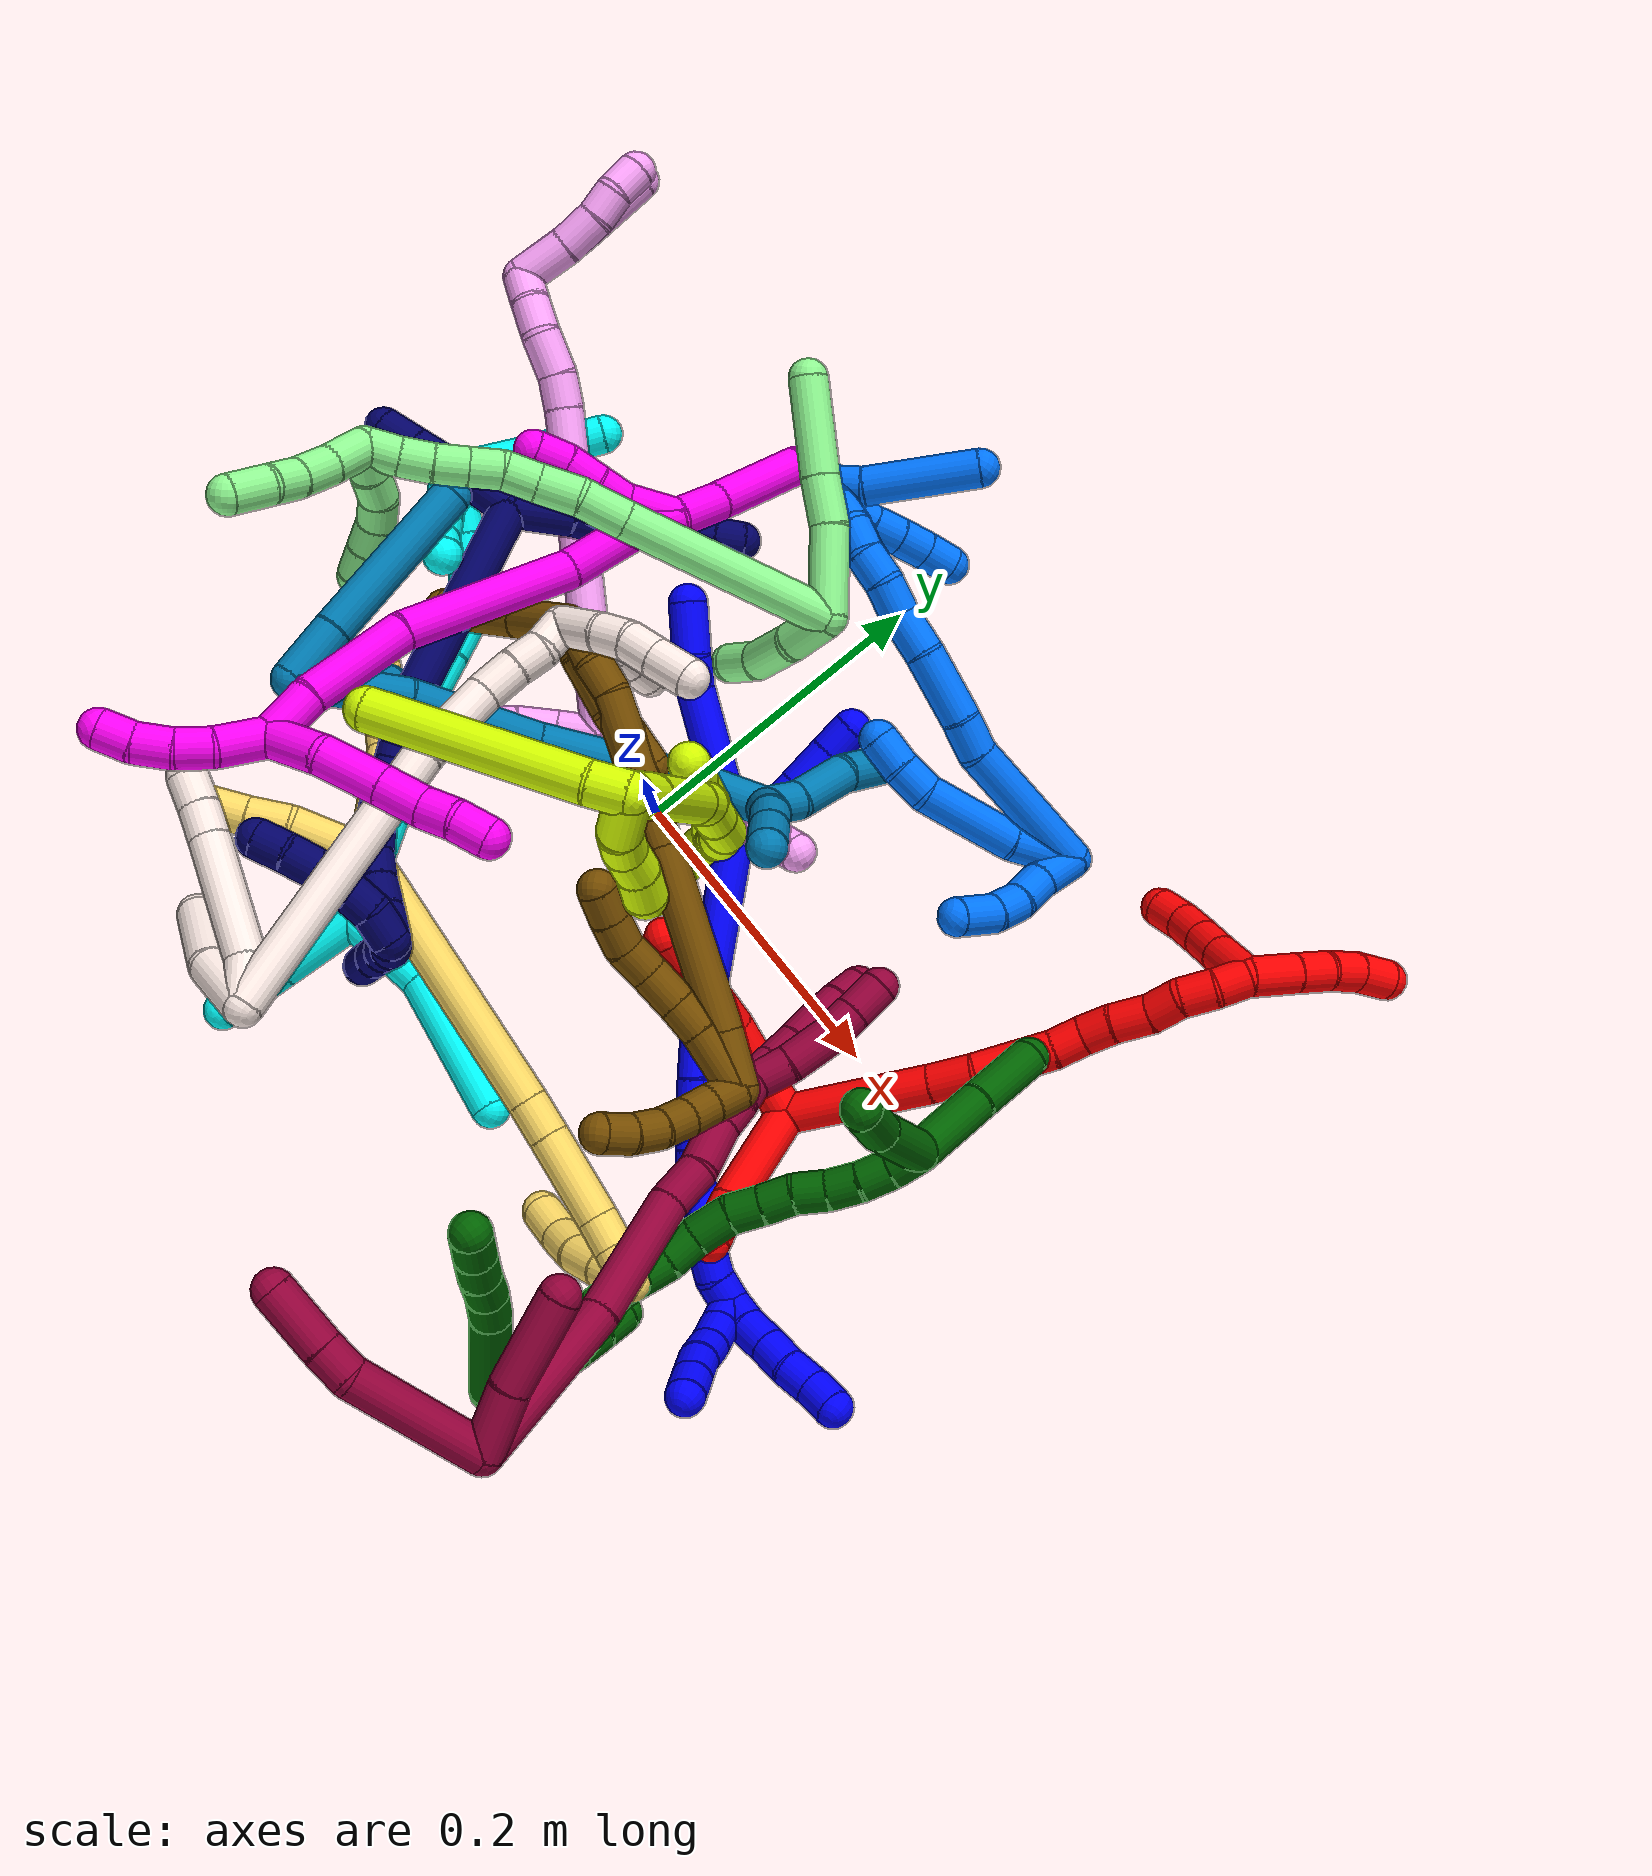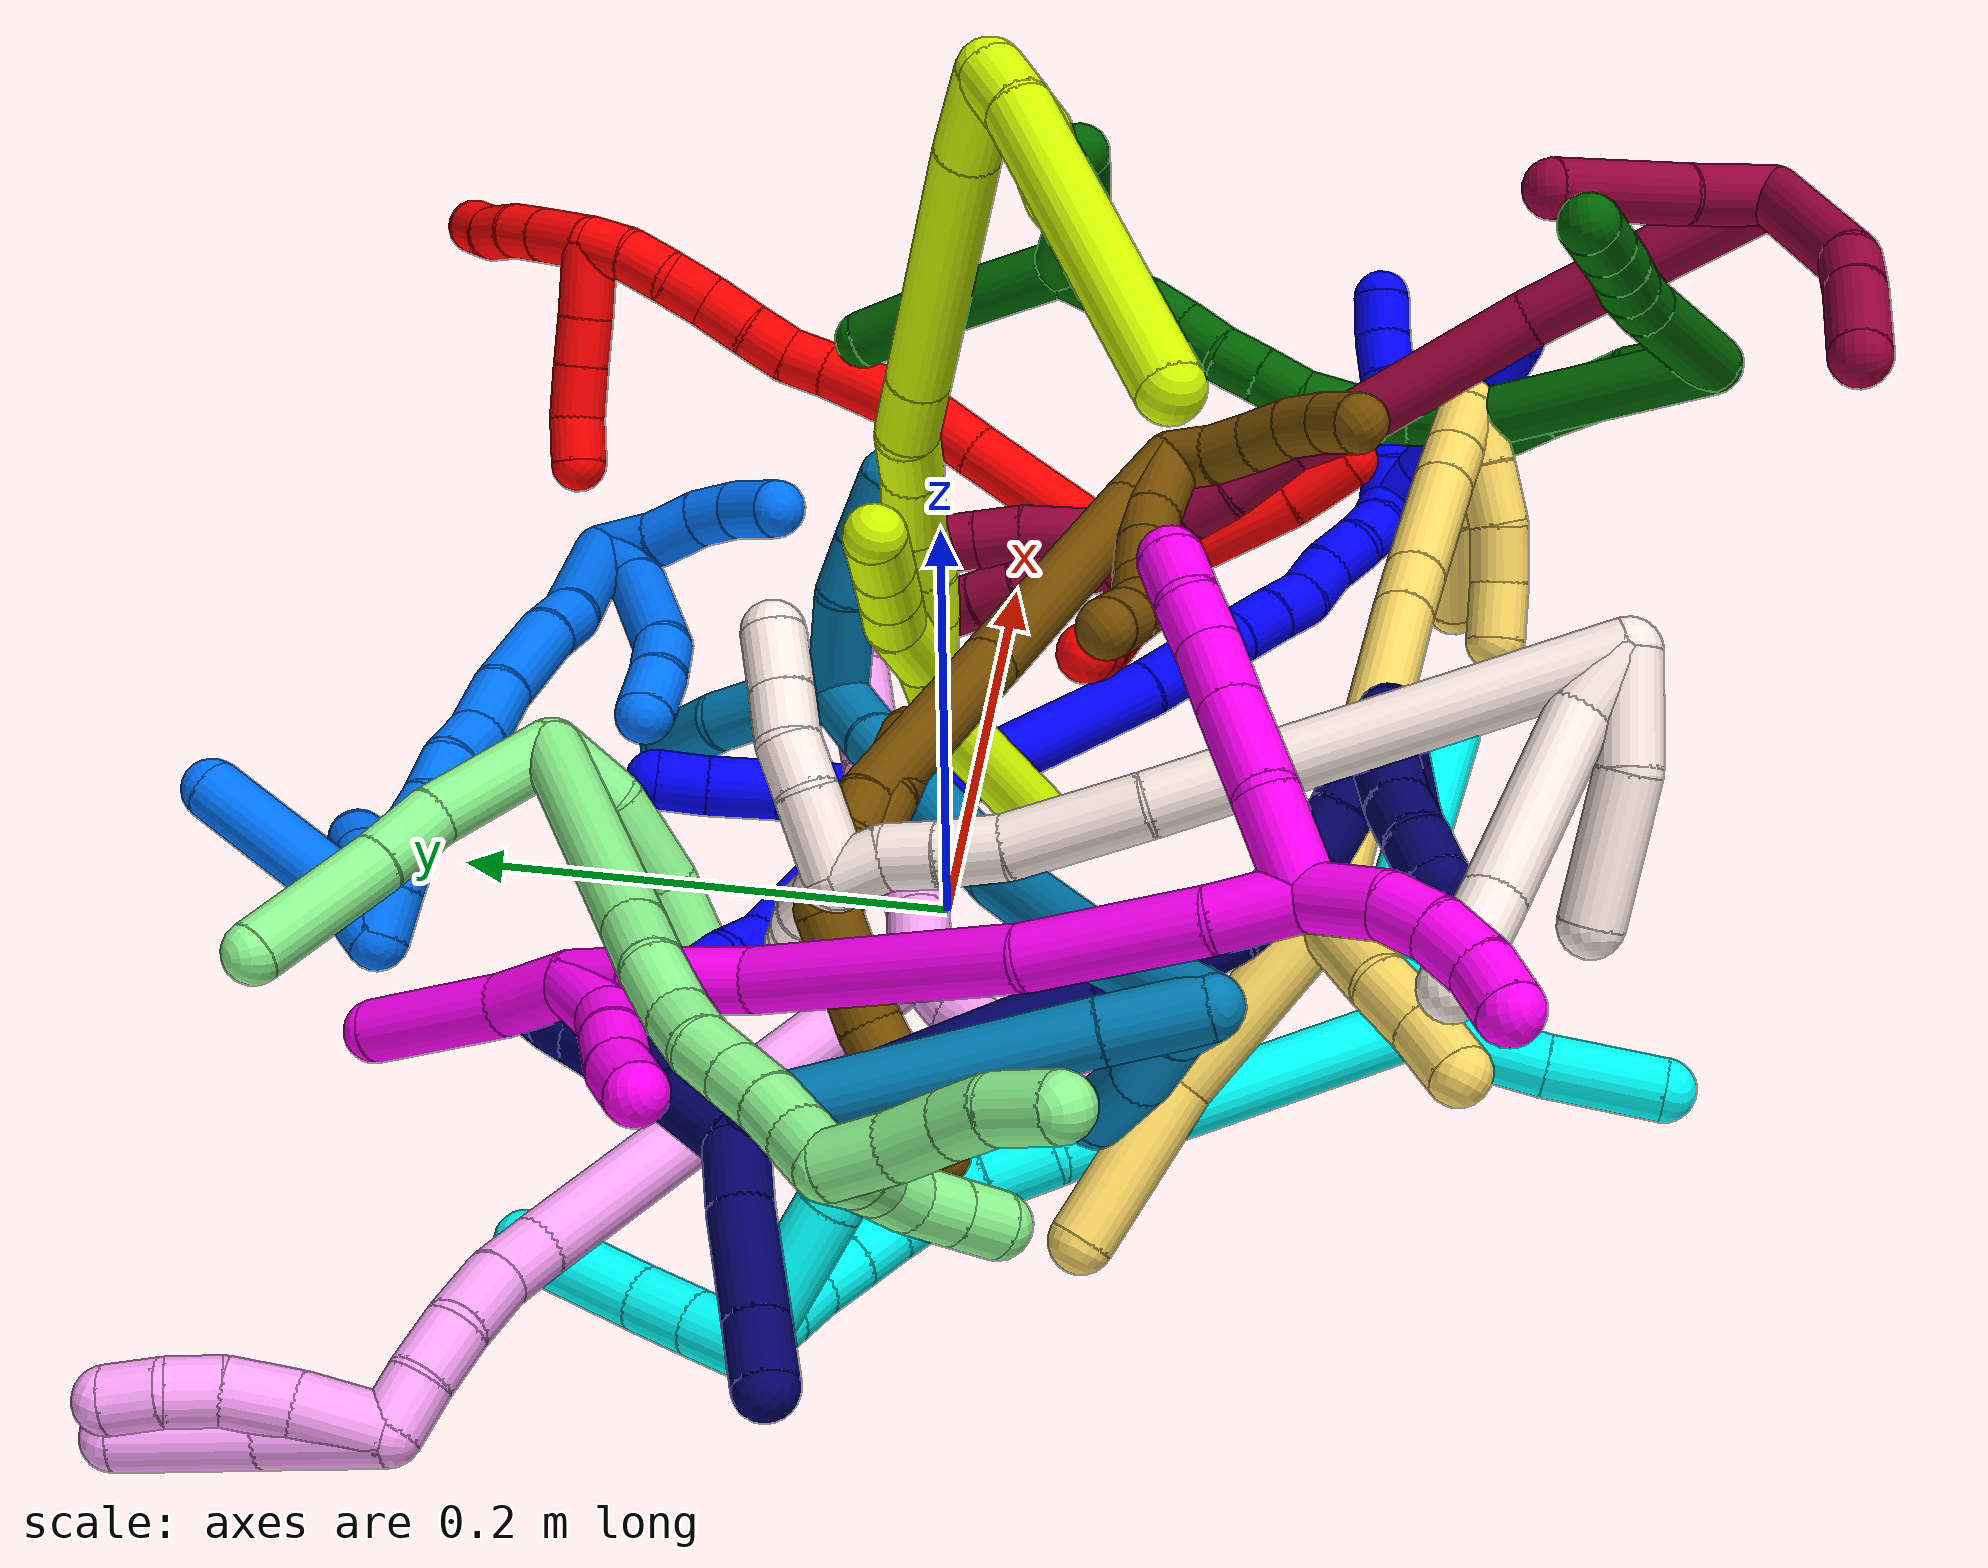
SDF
<sdf version="1.7">
 <world name="default">
  <plugin name="TubeGeneratorPlugin" filename="libtube_generator_plugin.so"/>
  <model name="photoneo_s_sensor">
   <static>1</static>
   <pose>0 0 2 1.57079 1.57079 3.14159</pose>
   <link name="link">
    <inertial><mass>0.1</mass></inertial>
    <sensor name="sensor" type="depth">
     <update_rate>30</update_rate>
     <camera>
      <horizontal_fov>1.22</horizontal_fov>
      <image><width>1920</width><height>1200</height><format>B8G8R8</format></image>
      <clip><near>0.1</near><far>4</far></clip>
      <depth_camera><output>points</output></depth_camera>
     </camera>
     <plugin name="camera_plugin" filename="libgazebo_ros_depth_camera.so">
      <baseline>0.2</baseline>
      <alwaysOn>1</alwaysOn>
      <updateRate>0.0</updateRate>
      <cameraName>camera_ir</cameraName>
      <imageTopicName>/camera/color/image_raw</imageTopicName>
      <cameraInfoTopicName>/camera/color/camera_info</cameraInfoTopicName>
      <depthImageTopicName>/camera/depth/image_raw</depthImageTopicName>
      <depthImageCameraInfoTopicName>/camera/depth/camera_info</depthImageCameraInfoTopicName>
      <pointCloudTopicName>/camera/depth/points</pointCloudTopicName>
      <frameName>fr_optical</frameName>
      <pointCloudCutoff>0.1</pointCloudCutoff>
      <pointCloudCutoffMax>2.0</pointCloudCutoffMax>
      <distortionK1>0</distortionK1>
      <distortionK2>0</distortionK2>
      <distortionK3>0</distortionK3>
      <distortionT1>0</distortionT1>
      <distortionT2>0</distortionT2>
      <CxPrime>0</CxPrime>
      <Cx>0</Cx>
      <Cy>0</Cy>
      <focalLength>0</focalLength>
      <hackBaseline>0</hackBaseline>
     </plugin>
    </sensor>
   </link>
  </model>
  <gravity>0 0 -9.8</gravity>
  <magnetic_field>6e-06 2.3e-05 -4.2e-05</magnetic_field>
  <atmosphere type="adiabatic"/>
  <physics name="default_physics" default="0" type="ode">
   <max_step_size>0.003</max_step_size>
   <real_time_factor>1</real_time_factor>
   <real_time_update_rate>1000</real_time_update_rate>
   <max_contacts>10000</max_contacts>
   <ode>
    <solver>
     <type>quick</type>
     <iters>100</iters>
     <sor>1.3</sor>
     <use_dynamic_moi_rescaling>0</use_dynamic_moi_rescaling>
    </solver>
    <constraints>
     <contact_max_correcting_vel>0</contact_max_correcting_vel>
     <contact_surface_layer>0.001</contact_surface_layer>
     <cfm>0</cfm>
     <erp>0.2</erp>
    </constraints>
   </ode>
  </physics>
  <scene><ambient>0.4 0.4 0.4 1</ambient><background>0.7 0.7 0.7 1</background><shadows>0</shadows></scene>
  <audio><device>default</device></audio>
  <spherical_coordinates>
   <surface_model>EARTH_WGS84</surface_model>
   <latitude_deg>0</latitude_deg>
   <longitude_deg>0</longitude_deg>
   <elevation>0</elevation>
   <heading_deg>0</heading_deg>
  </spherical_coordinates>
  <model name="bin">
   <static>1</static>
   <link name="bottom">
    <collision name="collision-bottom">
     <pose>0 0 -0.01 0 -0 0</pose>
     <geometry><box><size>0.8 0.6 0.02</size></box></geometry>
     <surface>
      <friction><ode><mu>100</mu><mu2>100</mu2></ode></friction>
      <contact><collide_bitmask>65535</collide_bitmask></contact>
     </surface>
    </collision>
   </link>
   <link name="west_wall">
    <collision name="collision-west_wall">
     <pose>-0.41 0 0.1 0 -0 0</pose>
     <geometry><box><size>0.02 0.6 0.2</size></box></geometry>
     <surface>
      <friction><ode><mu>100</mu><mu2>100</mu2></ode></friction>
      <contact><collide_bitmask>65535</collide_bitmask></contact>
     </surface>
    </collision>
   </link>
   <link name="east_wall">
    <collision name="collision-east_wall">
     <pose>0.41 0 0.1 0 -0 0</pose>
     <geometry><box><size>0.02 0.6 0.2</size></box></geometry>
     <surface>
      <friction><ode><mu>100</mu><mu2>100</mu2></ode></friction>
      <contact><collide_bitmask>65535</collide_bitmask></contact>
     </surface>
    </collision>
   </link>
   <link name="south_wall">
    <collision name="collision-south_wall">
     <pose>0 -0.31 0.1 0 -0 0</pose>
     <geometry><box><size>0.8 0.02 0.2</size></box></geometry>
     <surface>
      <friction><ode><mu>100</mu><mu2>100</mu2></ode></friction>
      <contact><collide_bitmask>65535</collide_bitmask></contact>
     </surface>
    </collision>
   </link>
   <link name="north_wall">
    <collision name="collision-north_wall">
     <pose>0 0.31 0.1 0 -0 0</pose>
     <geometry><box><size>0.8 0.02 0.2</size></box></geometry>
     <surface>
      <friction><ode><mu>100</mu><mu2>100</mu2></ode></friction>
      <contact><collide_bitmask>65535</collide_bitmask></contact>
     </surface>
    </collision>
   </link>
  </model>
  <model name="1">
   <static>0</static>
   <link name="1">
    <collision name="collision-cylinder-e_1_2_8">
     <pose>-0.030179 0.029188 -0.022548 -2.22855 -0.685759 1.25706</pose>
     <geometry><cylinder><radius>0.0125</radius><length>0.095312</length></cylinder></geometry>
     <surface>
      <friction><ode><mu>1.16</mu><mu2>1.16</mu2><slip1>0</slip1><slip2>0</slip2></ode></friction>
      <contact><ode><kp>1e+06</kp><kd>1</kd><max_vel>0</max_vel><min_depth>0.001</min_depth></ode></contact>
     </surface>
    </collision>
    <visual name="visual-cylinder-e_1_2_8">
     <pose>-0.030179 0.029188 -0.022548 -2.22855 -0.685759 1.25706</pose>
     <geometry><cylinder><radius>0.0125</radius><length>0.095312</length></cylinder></geometry>
     <material><ambient>0 0 1 1</ambient></material>
    </visual>
    <collision name="collision-cylinder-e_2_8_9">
     <pose>-0.065228 0.067127 -0.048683 -1.95971 -0.475533 0.693273</pose>
     <geometry><cylinder><radius>0.0125</radius><length>0.021277</length></cylinder></geometry>
     <surface>
      <friction><ode><mu>1.16</mu><mu2>1.16</mu2><slip1>0</slip1><slip2>0</slip2></ode></friction>
      <contact><ode><kp>1e+06</kp><kd>1</kd><max_vel>0</max_vel><min_depth>0.001</min_depth></ode></contact>
     </surface>
    </collision>
    <visual name="visual-cylinder-e_2_8_9">
     <pose>-0.065228 0.067127 -0.048683 -1.95971 -0.475533 0.693273</pose>
     <geometry><cylinder><radius>0.0125</radius><length>0.021277</length></cylinder></geometry>
     <material><ambient>0 0 1 1</ambient></material>
    </visual>
    <collision name="collision-cylinder-e_3_9_6">
     <pose>-0.078026 0.087323 -0.061502 -2.24968 -0.494468 0.971508</pose>
     <geometry><cylinder><radius>0.0125</radius><length>0.033411</length></cylinder></geometry>
     <surface>
      <friction><ode><mu>1.16</mu><mu2>1.16</mu2><slip1>0</slip1><slip2>0</slip2></ode></friction>
      <contact><ode><kp>1e+06</kp><kd>1</kd><max_vel>0</max_vel><min_depth>0.001</min_depth></ode></contact>
     </surface>
    </collision>
    <visual name="visual-cylinder-e_3_9_6">
     <pose>-0.078026 0.087323 -0.061502 -2.24968 -0.494468 0.971508</pose>
     <geometry><cylinder><radius>0.0125</radius><length>0.033411</length></cylinder></geometry>
     <material><ambient>0 0 1 1</ambient></material>
    </visual>
    <collision name="collision-cylinder-e_1_2_10">
     <pose>0.00689 0.006338 -0.006089 -2.33617 0.664851 -1.36213</pose>
     <geometry><cylinder><radius>0.0125</radius><length>0.022336</length></cylinder></geometry>
     <surface>
      <friction><ode><mu>1.16</mu><mu2>1.16</mu2><slip1>0</slip1><slip2>0</slip2></ode></friction>
      <contact><ode><kp>1e+06</kp><kd>1</kd><max_vel>0</max_vel><min_depth>0.001</min_depth></ode></contact>
     </surface>
    </collision>
    <visual name="visual-cylinder-e_1_2_10">
     <pose>0.00689 0.006338 -0.006089 -2.33617 0.664851 -1.36213</pose>
     <geometry><cylinder><radius>0.0125</radius><length>0.022336</length></cylinder></geometry>
     <material><ambient>0 0 1 1</ambient></material>
    </visual>
    <collision name="collision-cylinder-e_2_10_11">
     <pose>0.01855 0.021835 -0.021232 -2.35044 0.354754 -0.810974</pose>
     <geometry><cylinder><radius>0.0125</radius><length>0.027466</length></cylinder></geometry>
     <surface>
      <friction><ode><mu>1.16</mu><mu2>1.16</mu2><slip1>0</slip1><slip2>0</slip2></ode></friction>
      <contact><ode><kp>1e+06</kp><kd>1</kd><max_vel>0</max_vel><min_depth>0.001</min_depth></ode></contact>
     </surface>
    </collision>
    <visual name="visual-cylinder-e_2_10_11">
     <pose>0.01855 0.021835 -0.021232 -2.35044 0.354754 -0.810974</pose>
     <geometry><cylinder><radius>0.0125</radius><length>0.027466</length></cylinder></geometry>
     <material><ambient>0 0 1 1</ambient></material>
    </visual>
    <collision name="collision-cylinder-e_3_11_12">
     <pose>0.028001 0.041015 -0.039601 -2.31964 0.329609 -0.729145</pose>
     <geometry><cylinder><radius>0.0125</radius><length>0.028921</length></cylinder></geometry>
     <surface>
      <friction><ode><mu>1.16</mu><mu2>1.16</mu2><slip1>0</slip1><slip2>0</slip2></ode></friction>
      <contact><ode><kp>1e+06</kp><kd>1</kd><max_vel>0</max_vel><min_depth>0.001</min_depth></ode></contact>
     </surface>
    </collision>
    <visual name="visual-cylinder-e_3_11_12">
     <pose>0.028001 0.041015 -0.039601 -2.31964 0.329609 -0.729145</pose>
     <geometry><cylinder><radius>0.0125</radius><length>0.028921</length></cylinder></geometry>
     <material><ambient>0 0 1 1</ambient></material>
    </visual>
    <collision name="collision-cylinder-e_4_12_5">
     <pose>0.036248 0.058965 -0.055047 -2.22911 0.341809 -0.676316</pose>
     <geometry><cylinder><radius>0.0125</radius><length>0.021276</length></cylinder></geometry>
     <surface>
      <friction><ode><mu>1.16</mu><mu2>1.16</mu2><slip1>0</slip1><slip2>0</slip2></ode></friction>
      <contact><ode><kp>1e+06</kp><kd>1</kd><max_vel>0</max_vel><min_depth>0.001</min_depth></ode></contact>
     </surface>
    </collision>
    <visual name="visual-cylinder-e_4_12_5">
     <pose>0.036248 0.058965 -0.055047 -2.22911 0.341809 -0.676316</pose>
     <geometry><cylinder><radius>0.0125</radius><length>0.021276</length></cylinder></geometry>
     <material><ambient>0 0 1 1</ambient></material>
    </visual>
    <collision name="collision-cylinder-e_1_2_13">
     <pose>0.016217 -0.041956 0.044094 0.760554 0.260386 0.104582</pose>
     <geometry><cylinder><radius>0.0125</radius><length>0.125978</length></cylinder></geometry>
     <surface>
      <friction><ode><mu>1.16</mu><mu2>1.16</mu2><slip1>0</slip1><slip2>0</slip2></ode></friction>
      <contact><ode><kp>1e+06</kp><kd>1</kd><max_vel>0</max_vel><min_depth>0.001</min_depth></ode></contact>
     </surface>
    </collision>
    <visual name="visual-cylinder-e_1_2_13">
     <pose>0.016217 -0.041956 0.044094 0.760554 0.260386 0.104582</pose>
     <geometry><cylinder><radius>0.0125</radius><length>0.125978</length></cylinder></geometry>
     <material><ambient>0 0 1 1</ambient></material>
    </visual>
    <collision name="collision-cylinder-e_2_13_14">
     <pose>0.037764 -0.093325 0.098024 0.763474 0.3732 0.151287</pose>
     <geometry><cylinder><radius>0.0125</radius><length>0.02924</length></cylinder></geometry>
     <surface>
      <friction><ode><mu>1.16</mu><mu2>1.16</mu2><slip1>0</slip1><slip2>0</slip2></ode></friction>
      <contact><ode><kp>1e+06</kp><kd>1</kd><max_vel>0</max_vel><min_depth>0.001</min_depth></ode></contact>
     </surface>
    </collision>
    <visual name="visual-cylinder-e_2_13_14">
     <pose>0.037764 -0.093325 0.098024 0.763474 0.3732 0.151287</pose>
     <geometry><cylinder><radius>0.0125</radius><length>0.02924</length></cylinder></geometry>
     <material><ambient>0 0 1 1</ambient></material>
    </visual>
    <collision name="collision-cylinder-e_3_14_15">
     <pose>0.047174 -0.110262 0.114416 0.853938 0.38809 0.17834</pose>
     <geometry><cylinder><radius>0.0125</radius><length>0.021564</length></cylinder></geometry>
     <surface>
      <friction><ode><mu>1.16</mu><mu2>1.16</mu2><slip1>0</slip1><slip2>0</slip2></ode></friction>
      <contact><ode><kp>1e+06</kp><kd>1</kd><max_vel>0</max_vel><min_depth>0.001</min_depth></ode></contact>
     </surface>
    </collision>
    <visual name="visual-cylinder-e_3_14_15">
     <pose>0.047174 -0.110262 0.114416 0.853938 0.38809 0.17834</pose>
     <geometry><cylinder><radius>0.0125</radius><length>0.021564</length></cylinder></geometry>
     <material><ambient>0 0 1 1</ambient></material>
    </visual>
    <collision name="collision-cylinder-e_4_15_16">
     <pose>0.055753 -0.125442 0.127528 0.86276 0.419774 0.195482</pose>
     <geometry><cylinder><radius>0.0125</radius><length>0.022074</length></cylinder></geometry>
     <surface>
      <friction><ode><mu>1.16</mu><mu2>1.16</mu2><slip1>0</slip1><slip2>0</slip2></ode></friction>
      <contact><ode><kp>1e+06</kp><kd>1</kd><max_vel>0</max_vel><min_depth>0.001</min_depth></ode></contact>
     </surface>
    </collision>
    <visual name="visual-cylinder-e_4_15_16">
     <pose>0.055753 -0.125442 0.127528 0.86276 0.419774 0.195482</pose>
     <geometry><cylinder><radius>0.0125</radius><length>0.022074</length></cylinder></geometry>
     <material><ambient>0 0 1 1</ambient></material>
    </visual>
    <collision name="collision-cylinder-e_5_16_17">
     <pose>0.064367 -0.140412 0.139624 0.922345 0.42169 0.211907</pose>
     <geometry><cylinder><radius>0.0125</radius><length>0.020115</length></cylinder></geometry>
     <surface>
      <friction><ode><mu>1.16</mu><mu2>1.16</mu2><slip1>0</slip1><slip2>0</slip2></ode></friction>
      <contact><ode><kp>1e+06</kp><kd>1</kd><max_vel>0</max_vel><min_depth>0.001</min_depth></ode></contact>
     </surface>
    </collision>
    <visual name="visual-cylinder-e_5_16_17">
     <pose>0.064367 -0.140412 0.139624 0.922345 0.42169 0.211907</pose>
     <geometry><cylinder><radius>0.0125</radius><length>0.020115</length></cylinder></geometry>
     <material><ambient>0 0 1 1</ambient></material>
    </visual>
    <collision name="collision-cylinder-e_6_17_18">
     <pose>0.075054 -0.152772 0.15077 0.733155 0.716697 0.285621</pose>
     <geometry><cylinder><radius>0.0125</radius><length>0.020004</length></cylinder></geometry>
     <surface>
      <friction><ode><mu>1.16</mu><mu2>1.16</mu2><slip1>0</slip1><slip2>0</slip2></ode></friction>
      <contact><ode><kp>1e+06</kp><kd>1</kd><max_vel>0</max_vel><min_depth>0.001</min_depth></ode></contact>
     </surface>
    </collision>
    <visual name="visual-cylinder-e_6_17_18">
     <pose>0.075054 -0.152772 0.15077 0.733155 0.716697 0.285621</pose>
     <geometry><cylinder><radius>0.0125</radius><length>0.020004</length></cylinder></geometry>
     <material><ambient>0 0 1 1</ambient></material>
    </visual>
    <collision name="collision-cylinder-e_7_18_19">
     <pose>0.086503 -0.164056 0.1631 0.747639 0.48877 0.195017</pose>
     <geometry><cylinder><radius>0.0125</radius><length>0.020779</length></cylinder></geometry>
     <surface>
      <friction><ode><mu>1.16</mu><mu2>1.16</mu2><slip1>0</slip1><slip2>0</slip2></ode></friction>
      <contact><ode><kp>1e+06</kp><kd>1</kd><max_vel>0</max_vel><min_depth>0.001</min_depth></ode></contact>
     </surface>
    </collision>
    <visual name="visual-cylinder-e_7_18_19">
     <pose>0.086503 -0.164056 0.1631 0.747639 0.48877 0.195017</pose>
     <geometry><cylinder><radius>0.0125</radius><length>0.020779</length></cylinder></geometry>
     <material><ambient>0 0 1 1</ambient></material>
    </visual>
    <collision name="collision-cylinder-e_8_19_20">
     <pose>0.09762 -0.177076 0.173962 1.0233 0.665771 0.383526</pose>
     <geometry><cylinder><radius>0.0125</radius><length>0.020203</length></cylinder></geometry>
     <surface>
      <friction><ode><mu>1.16</mu><mu2>1.16</mu2><slip1>0</slip1><slip2>0</slip2></ode></friction>
      <contact><ode><kp>1e+06</kp><kd>1</kd><max_vel>0</max_vel><min_depth>0.001</min_depth></ode></contact>
     </surface>
    </collision>
    <visual name="visual-cylinder-e_8_19_20">
     <pose>0.09762 -0.177076 0.173962 1.0233 0.665771 0.383526</pose>
     <geometry><cylinder><radius>0.0125</radius><length>0.020203</length></cylinder></geometry>
     <material><ambient>0 0 1 1</ambient></material>
    </visual>
    <collision name="collision-cylinder-e_9_20_1">
     <pose>0.111634 -0.189968 0.179732 1.30951 0.887868 0.700184</pose>
     <geometry><cylinder><radius>0.0125</radius><length>0.020043</length></cylinder></geometry>
     <surface>
      <friction><ode><mu>1.16</mu><mu2>1.16</mu2><slip1>0</slip1><slip2>0</slip2></ode></friction>
      <contact><ode><kp>1e+06</kp><kd>1</kd><max_vel>0</max_vel><min_depth>0.001</min_depth></ode></contact>
     </surface>
    </collision>
    <visual name="visual-cylinder-e_9_20_1">
     <pose>0.111634 -0.189968 0.179732 1.30951 0.887868 0.700184</pose>
     <geometry><cylinder><radius>0.0125</radius><length>0.020043</length></cylinder></geometry>
     <material><ambient>0 0 1 1</ambient></material>
    </visual>
    <collision name="collision-cylinder-e_1_1_21">
     <pose>0.119473 -0.195832 0.191362 -0.024606 0.006527 -8e-05</pose>
     <geometry><cylinder><radius>0.0125</radius><length>0.02</length></cylinder></geometry>
     <surface>
      <friction><ode><mu>1.16</mu><mu2>1.16</mu2><slip1>0</slip1><slip2>0</slip2></ode></friction>
      <contact><ode><kp>1e+06</kp><kd>1</kd><max_vel>0</max_vel><min_depth>0.001</min_depth></ode></contact>
     </surface>
    </collision>
    <visual name="visual-cylinder-e_1_1_21">
     <pose>0.119473 -0.195832 0.191362 -0.024606 0.006527 -8e-05</pose>
     <geometry><cylinder><radius>0.0125</radius><length>0.02</length></cylinder></geometry>
     <material><ambient>0 0 1 1</ambient></material>
    </visual>
    <collision name="collision-cylinder-e_2_21_22">
     <pose>0.119842 -0.194107 0.211244 -0.148519 0.030387 -0.002261</pose>
     <geometry><cylinder><radius>0.0125</radius><length>0.02</length></cylinder></geometry>
     <surface>
      <friction><ode><mu>1.16</mu><mu2>1.16</mu2><slip1>0</slip1><slip2>0</slip2></ode></friction>
      <contact><ode><kp>1e+06</kp><kd>1</kd><max_vel>0</max_vel><min_depth>0.001</min_depth></ode></contact>
     </surface>
    </collision>
    <visual name="visual-cylinder-e_2_21_22">
     <pose>0.119842 -0.194107 0.211244 -0.148519 0.030387 -0.002261</pose>
     <geometry><cylinder><radius>0.0125</radius><length>0.02</length></cylinder></geometry>
     <material><ambient>0 0 1 1</ambient></material>
    </visual>
    <collision name="collision-cylinder-e_3_22_23">
     <pose>0.119728 -0.189266 0.230538 -0.34315 -0.041845 0.007252</pose>
     <geometry><cylinder><radius>0.0125</radius><length>0.02</length></cylinder></geometry>
     <surface>
      <friction><ode><mu>1.16</mu><mu2>1.16</mu2><slip1>0</slip1><slip2>0</slip2></ode></friction>
      <contact><ode><kp>1e+06</kp><kd>1</kd><max_vel>0</max_vel><min_depth>0.001</min_depth></ode></contact>
     </surface>
    </collision>
    <visual name="visual-cylinder-e_3_22_23">
     <pose>0.119728 -0.189266 0.230538 -0.34315 -0.041845 0.007252</pose>
     <geometry><cylinder><radius>0.0125</radius><length>0.02</length></cylinder></geometry>
     <material><ambient>0 0 1 1</ambient></material>
    </visual>
    <collision name="collision-cylinder-e_4_23_24">
     <pose>0.120532 -0.183195 0.249495 -0.276488 0.122556 -0.017072</pose>
     <geometry><cylinder><radius>0.0125</radius><length>0.02</length></cylinder></geometry>
     <surface>
      <friction><ode><mu>1.16</mu><mu2>1.16</mu2><slip1>0</slip1><slip2>0</slip2></ode></friction>
      <contact><ode><kp>1e+06</kp><kd>1</kd><max_vel>0</max_vel><min_depth>0.001</min_depth></ode></contact>
     </surface>
    </collision>
    <visual name="visual-cylinder-e_4_23_24">
     <pose>0.120532 -0.183195 0.249495 -0.276488 0.122556 -0.017072</pose>
     <geometry><cylinder><radius>0.0125</radius><length>0.02</length></cylinder></geometry>
     <material><ambient>0 0 1 1</ambient></material>
    </visual>
    <collision name="collision-cylinder-e_5_24_4">
     <pose>0.123002 -0.177723 0.268572 -0.282225 0.12509 -0.017793</pose>
     <geometry><cylinder><radius>0.0125</radius><length>0.02</length></cylinder></geometry>
     <surface>
      <friction><ode><mu>1.16</mu><mu2>1.16</mu2><slip1>0</slip1><slip2>0</slip2></ode></friction>
      <contact><ode><kp>1e+06</kp><kd>1</kd><max_vel>0</max_vel><min_depth>0.001</min_depth></ode></contact>
     </surface>
    </collision>
    <visual name="visual-cylinder-e_5_24_4">
     <pose>0.123002 -0.177723 0.268572 -0.282225 0.12509 -0.017793</pose>
     <geometry><cylinder><radius>0.0125</radius><length>0.02</length></cylinder></geometry>
     <material><ambient>0 0 1 1</ambient></material>
    </visual>
    <collision name="collision-cylinder-e_1_1_25">
     <pose>0.12712 -0.194532 0.18754 -0.245374 0.880748 -0.116083</pose>
     <geometry><cylinder><radius>0.0125</radius><length>0.02</length></cylinder></geometry>
     <surface>
      <friction><ode><mu>1.16</mu><mu2>1.16</mu2><slip1>0</slip1><slip2>0</slip2></ode></friction>
      <contact><ode><kp>1e+06</kp><kd>1</kd><max_vel>0</max_vel><min_depth>0.001</min_depth></ode></contact>
     </surface>
    </collision>
    <visual name="visual-cylinder-e_1_1_25">
     <pose>0.12712 -0.194532 0.18754 -0.245374 0.880748 -0.116083</pose>
     <geometry><cylinder><radius>0.0125</radius><length>0.02</length></cylinder></geometry>
     <material><ambient>0 0 1 1</ambient></material>
    </visual>
    <collision name="collision-cylinder-e_2_25_26">
     <pose>0.143431 -0.191503 0.1986 -0.294758 1.03508 -0.168631</pose>
     <geometry><cylinder><radius>0.0125</radius><length>0.02</length></cylinder></geometry>
     <surface>
      <friction><ode><mu>1.16</mu><mu2>1.16</mu2><slip1>0</slip1><slip2>0</slip2></ode></friction>
      <contact><ode><kp>1e+06</kp><kd>1</kd><max_vel>0</max_vel><min_depth>0.001</min_depth></ode></contact>
     </surface>
    </collision>
    <visual name="visual-cylinder-e_2_25_26">
     <pose>0.143431 -0.191503 0.1986 -0.294758 1.03508 -0.168631</pose>
     <geometry><cylinder><radius>0.0125</radius><length>0.02</length></cylinder></geometry>
     <material><ambient>0 0 1 1</ambient></material>
    </visual>
    <collision name="collision-cylinder-e_3_26_27">
     <pose>0.160572 -0.188825 0.208544 -0.231856 1.02403 -0.130706</pose>
     <geometry><cylinder><radius>0.0125</radius><length>0.02</length></cylinder></geometry>
     <surface>
      <friction><ode><mu>1.16</mu><mu2>1.16</mu2><slip1>0</slip1><slip2>0</slip2></ode></friction>
      <contact><ode><kp>1e+06</kp><kd>1</kd><max_vel>0</max_vel><min_depth>0.001</min_depth></ode></contact>
     </surface>
    </collision>
    <visual name="visual-cylinder-e_3_26_27">
     <pose>0.160572 -0.188825 0.208544 -0.231856 1.02403 -0.130706</pose>
     <geometry><cylinder><radius>0.0125</radius><length>0.02</length></cylinder></geometry>
     <material><ambient>0 0 1 1</ambient></material>
    </visual>
    <collision name="collision-cylinder-e_4_27_28">
     <pose>0.178376 -0.18679 0.217281 -0.224578 1.18415 -0.151392</pose>
     <geometry><cylinder><radius>0.0125</radius><length>0.02</length></cylinder></geometry>
     <surface>
      <friction><ode><mu>1.16</mu><mu2>1.16</mu2><slip1>0</slip1><slip2>0</slip2></ode></friction>
      <contact><ode><kp>1e+06</kp><kd>1</kd><max_vel>0</max_vel><min_depth>0.001</min_depth></ode></contact>
     </surface>
    </collision>
    <visual name="visual-cylinder-e_4_27_28">
     <pose>0.178376 -0.18679 0.217281 -0.224578 1.18415 -0.151392</pose>
     <geometry><cylinder><radius>0.0125</radius><length>0.02</length></cylinder></geometry>
     <material><ambient>0 0 1 1</ambient></material>
    </visual>
    <collision name="collision-cylinder-e_5_28_3">
     <pose>0.196179 -0.184543 0.225965 -0.274017 1.0237 -0.154601</pose>
     <geometry><cylinder><radius>0.0125</radius><length>0.02</length></cylinder></geometry>
     <surface>
      <friction><ode><mu>1.16</mu><mu2>1.16</mu2><slip1>0</slip1><slip2>0</slip2></ode></friction>
      <contact><ode><kp>1e+06</kp><kd>1</kd><max_vel>0</max_vel><min_depth>0.001</min_depth></ode></contact>
     </surface>
    </collision>
    <visual name="visual-cylinder-e_5_28_3">
     <pose>0.196179 -0.184543 0.225965 -0.274017 1.0237 -0.154601</pose>
     <geometry><cylinder><radius>0.0125</radius><length>0.02</length></cylinder></geometry>
     <material><ambient>0 0 1 1</ambient></material>
    </visual>
    <collision name="collision-sphere-3">
     <pose>0.204719 -0.183135 0.230973 0 -0 0</pose>
     <geometry><sphere><radius>0.0125</radius></sphere></geometry>
     <surface>
      <friction><ode><mu>1.16</mu><mu2>1.16</mu2><slip1>0</slip1><slip2>0</slip2></ode></friction>
      <contact><ode><kp>1e+06</kp><kd>1</kd><max_vel>0</max_vel><min_depth>0.001</min_depth></ode></contact>
     </surface>
    </collision>
    <visual name="visual-sphere-3">
     <pose>0.204719 -0.183135 0.230973 0 -0 0</pose>
     <geometry><sphere><radius>0.0125</radius></sphere></geometry>
     <material><ambient>0 0 1 1</ambient></material>
    </visual>
    <collision name="collision-sphere-28">
     <pose>0.187638 -0.185951 0.220957 0 -0 0</pose>
     <geometry><sphere><radius>0.0125</radius></sphere></geometry>
     <surface>
      <friction><ode><mu>1.16</mu><mu2>1.16</mu2><slip1>0</slip1><slip2>0</slip2></ode></friction>
      <contact><ode><kp>1e+06</kp><kd>1</kd><max_vel>0</max_vel><min_depth>0.001</min_depth></ode></contact>
     </surface>
    </collision>
    <visual name="visual-sphere-28">
     <pose>0.187638 -0.185951 0.220957 0 -0 0</pose>
     <geometry><sphere><radius>0.0125</radius></sphere></geometry>
     <material><ambient>0 0 1 1</ambient></material>
    </visual>
    <collision name="collision-sphere-27">
     <pose>0.169115 -0.18763 0.213604 0 -0 0</pose>
     <geometry><sphere><radius>0.0125</radius></sphere></geometry>
     <surface>
      <friction><ode><mu>1.16</mu><mu2>1.16</mu2><slip1>0</slip1><slip2>0</slip2></ode></friction>
      <contact><ode><kp>1e+06</kp><kd>1</kd><max_vel>0</max_vel><min_depth>0.001</min_depth></ode></contact>
     </surface>
    </collision>
    <visual name="visual-sphere-27">
     <pose>0.169115 -0.18763 0.213604 0 -0 0</pose>
     <geometry><sphere><radius>0.0125</radius></sphere></geometry>
     <material><ambient>0 0 1 1</ambient></material>
    </visual>
    <collision name="collision-sphere-26">
     <pose>0.15203 -0.19002 0.203484 0 -0 0</pose>
     <geometry><sphere><radius>0.0125</radius></sphere></geometry>
     <surface>
      <friction><ode><mu>1.16</mu><mu2>1.16</mu2><slip1>0</slip1><slip2>0</slip2></ode></friction>
      <contact><ode><kp>1e+06</kp><kd>1</kd><max_vel>0</max_vel><min_depth>0.001</min_depth></ode></contact>
     </surface>
    </collision>
    <visual name="visual-sphere-26">
     <pose>0.15203 -0.19002 0.203484 0 -0 0</pose>
     <geometry><sphere><radius>0.0125</radius></sphere></geometry>
     <material><ambient>0 0 1 1</ambient></material>
    </visual>
    <collision name="collision-sphere-25">
     <pose>0.134832 -0.192985 0.193715 0 -0 0</pose>
     <geometry><sphere><radius>0.0125</radius></sphere></geometry>
     <surface>
      <friction><ode><mu>1.16</mu><mu2>1.16</mu2><slip1>0</slip1><slip2>0</slip2></ode></friction>
      <contact><ode><kp>1e+06</kp><kd>1</kd><max_vel>0</max_vel><min_depth>0.001</min_depth></ode></contact>
     </surface>
    </collision>
    <visual name="visual-sphere-25">
     <pose>0.134832 -0.192985 0.193715 0 -0 0</pose>
     <geometry><sphere><radius>0.0125</radius></sphere></geometry>
     <material><ambient>0 0 1 1</ambient></material>
    </visual>
    <collision name="collision-sphere-4">
     <pose>0.12425 -0.17496 0.278102 0 -0 0</pose>
     <geometry><sphere><radius>0.0125</radius></sphere></geometry>
     <surface>
      <friction><ode><mu>1.16</mu><mu2>1.16</mu2><slip1>0</slip1><slip2>0</slip2></ode></friction>
      <contact><ode><kp>1e+06</kp><kd>1</kd><max_vel>0</max_vel><min_depth>0.001</min_depth></ode></contact>
     </surface>
    </collision>
    <visual name="visual-sphere-4">
     <pose>0.12425 -0.17496 0.278102 0 -0 0</pose>
     <geometry><sphere><radius>0.0125</radius></sphere></geometry>
     <material><ambient>0 0 1 1</ambient></material>
    </visual>
    <collision name="collision-sphere-24">
     <pose>0.121754 -0.180486 0.259043 0 -0 0</pose>
     <geometry><sphere><radius>0.0125</radius></sphere></geometry>
     <surface>
      <friction><ode><mu>1.16</mu><mu2>1.16</mu2><slip1>0</slip1><slip2>0</slip2></ode></friction>
      <contact><ode><kp>1e+06</kp><kd>1</kd><max_vel>0</max_vel><min_depth>0.001</min_depth></ode></contact>
     </surface>
    </collision>
    <visual name="visual-sphere-24">
     <pose>0.121754 -0.180486 0.259043 0 -0 0</pose>
     <geometry><sphere><radius>0.0125</radius></sphere></geometry>
     <material><ambient>0 0 1 1</ambient></material>
    </visual>
    <collision name="collision-sphere-23">
     <pose>0.119309 -0.185905 0.239947 0 -0 0</pose>
     <geometry><sphere><radius>0.0125</radius></sphere></geometry>
     <surface>
      <friction><ode><mu>1.16</mu><mu2>1.16</mu2><slip1>0</slip1><slip2>0</slip2></ode></friction>
      <contact><ode><kp>1e+06</kp><kd>1</kd><max_vel>0</max_vel><min_depth>0.001</min_depth></ode></contact>
     </surface>
    </collision>
    <visual name="visual-sphere-23">
     <pose>0.119309 -0.185905 0.239947 0 -0 0</pose>
     <geometry><sphere><radius>0.0125</radius></sphere></geometry>
     <material><ambient>0 0 1 1</ambient></material>
    </visual>
    <collision name="collision-sphere-22">
     <pose>0.120146 -0.192628 0.221129 0 -0 0</pose>
     <geometry><sphere><radius>0.0125</radius></sphere></geometry>
     <surface>
      <friction><ode><mu>1.16</mu><mu2>1.16</mu2><slip1>0</slip1><slip2>0</slip2></ode></friction>
      <contact><ode><kp>1e+06</kp><kd>1</kd><max_vel>0</max_vel><min_depth>0.001</min_depth></ode></contact>
     </surface>
    </collision>
    <visual name="visual-sphere-22">
     <pose>0.120146 -0.192628 0.221129 0 -0 0</pose>
     <geometry><sphere><radius>0.0125</radius></sphere></geometry>
     <material><ambient>0 0 1 1</ambient></material>
    </visual>
    <collision name="collision-sphere-21">
     <pose>0.119538 -0.195586 0.201359 0 -0 0</pose>
     <geometry><sphere><radius>0.0125</radius></sphere></geometry>
     <surface>
      <friction><ode><mu>1.16</mu><mu2>1.16</mu2><slip1>0</slip1><slip2>0</slip2></ode></friction>
      <contact><ode><kp>1e+06</kp><kd>1</kd><max_vel>0</max_vel><min_depth>0.001</min_depth></ode></contact>
     </surface>
    </collision>
    <visual name="visual-sphere-21">
     <pose>0.119538 -0.195586 0.201359 0 -0 0</pose>
     <geometry><sphere><radius>0.0125</radius></sphere></geometry>
     <material><ambient>0 0 1 1</ambient></material>
    </visual>
    <collision name="collision-sphere-1">
     <pose>0.119408 -0.196078 0.181365 0 -0 0</pose>
     <geometry><sphere><radius>0.0125</radius></sphere></geometry>
     <surface>
      <friction><ode><mu>1.16</mu><mu2>1.16</mu2><slip1>0</slip1><slip2>0</slip2></ode></friction>
      <contact><ode><kp>1e+06</kp><kd>1</kd><max_vel>0</max_vel><min_depth>0.001</min_depth></ode></contact>
     </surface>
    </collision>
    <visual name="visual-sphere-1">
     <pose>0.119408 -0.196078 0.181365 0 -0 0</pose>
     <geometry><sphere><radius>0.0125</radius></sphere></geometry>
     <material><ambient>0 0 1 1</ambient></material>
    </visual>
    <collision name="collision-sphere-11">
     <pose>0.023321 0.030993 -0.030286 0 -0 0</pose>
     <geometry><sphere><radius>0.0125</radius></sphere></geometry>
     <surface>
      <friction><ode><mu>1.16</mu><mu2>1.16</mu2><slip1>0</slip1><slip2>0</slip2></ode></friction>
      <contact><ode><kp>1e+06</kp><kd>1</kd><max_vel>0</max_vel><min_depth>0.001</min_depth></ode></contact>
     </surface>
    </collision>
    <visual name="visual-sphere-11">
     <pose>0.023321 0.030993 -0.030286 0 -0 0</pose>
     <geometry><sphere><radius>0.0125</radius></sphere></geometry>
     <material><ambient>0 0 1 1</ambient></material>
    </visual>
    <collision name="collision-sphere-10">
     <pose>0.01378 0.012676 -0.012179 0 -0 0</pose>
     <geometry><sphere><radius>0.0125</radius></sphere></geometry>
     <surface>
      <friction><ode><mu>1.16</mu><mu2>1.16</mu2><slip1>0</slip1><slip2>0</slip2></ode></friction>
      <contact><ode><kp>1e+06</kp><kd>1</kd><max_vel>0</max_vel><min_depth>0.001</min_depth></ode></contact>
     </surface>
    </collision>
    <visual name="visual-sphere-10">
     <pose>0.01378 0.012676 -0.012179 0 -0 0</pose>
     <geometry><sphere><radius>0.0125</radius></sphere></geometry>
     <material><ambient>0 0 1 1</ambient></material>
    </visual>
    <collision name="collision-sphere-6">
     <pose>-0.085954 0.098767 -0.070736 0 -0 0</pose>
     <geometry><sphere><radius>0.0125</radius></sphere></geometry>
     <surface>
      <friction><ode><mu>1.16</mu><mu2>1.16</mu2><slip1>0</slip1><slip2>0</slip2></ode></friction>
      <contact><ode><kp>1e+06</kp><kd>1</kd><max_vel>0</max_vel><min_depth>0.001</min_depth></ode></contact>
     </surface>
    </collision>
    <visual name="visual-sphere-6">
     <pose>-0.085954 0.098767 -0.070736 0 -0 0</pose>
     <geometry><sphere><radius>0.0125</radius></sphere></geometry>
     <material><ambient>0 0 1 1</ambient></material>
    </visual>
    <collision name="collision-sphere-9">
     <pose>-0.070098 0.075879 -0.052269 0 -0 0</pose>
     <geometry><sphere><radius>0.0125</radius></sphere></geometry>
     <surface>
      <friction><ode><mu>1.16</mu><mu2>1.16</mu2><slip1>0</slip1><slip2>0</slip2></ode></friction>
      <contact><ode><kp>1e+06</kp><kd>1</kd><max_vel>0</max_vel><min_depth>0.001</min_depth></ode></contact>
     </surface>
    </collision>
    <visual name="visual-sphere-9">
     <pose>-0.070098 0.075879 -0.052269 0 -0 0</pose>
     <geometry><sphere><radius>0.0125</radius></sphere></geometry>
     <material><ambient>0 0 1 1</ambient></material>
    </visual>
    <collision name="collision-sphere-2">
     <geometry><sphere><radius>0.0125</radius></sphere></geometry>
     <surface>
      <friction><ode><mu>1.16</mu><mu2>1.16</mu2><slip1>0</slip1><slip2>0</slip2></ode></friction>
      <contact><ode><kp>1e+06</kp><kd>1</kd><max_vel>0</max_vel><min_depth>0.001</min_depth></ode></contact>
     </surface>
    </collision>
    <visual name="visual-sphere-2">
     <geometry><sphere><radius>0.0125</radius></sphere></geometry>
     <material><ambient>0 0 1 1</ambient></material>
    </visual>
    <collision name="collision-sphere-19">
     <pose>0.091381 -0.170293 0.169827 0 -0 0</pose>
     <geometry><sphere><radius>0.0125</radius></sphere></geometry>
     <surface>
      <friction><ode><mu>1.16</mu><mu2>1.16</mu2><slip1>0</slip1><slip2>0</slip2></ode></friction>
      <contact><ode><kp>1e+06</kp><kd>1</kd><max_vel>0</max_vel><min_depth>0.001</min_depth></ode></contact>
     </surface>
    </collision>
    <visual name="visual-sphere-19">
     <pose>0.091381 -0.170293 0.169827 0 -0 0</pose>
     <geometry><sphere><radius>0.0125</radius></sphere></geometry>
     <material><ambient>0 0 1 1</ambient></material>
    </visual>
    <collision name="collision-sphere-8">
     <pose>-0.060357 0.058376 -0.045096 0 -0 0</pose>
     <geometry><sphere><radius>0.0125</radius></sphere></geometry>
     <surface>
      <friction><ode><mu>1.16</mu><mu2>1.16</mu2><slip1>0</slip1><slip2>0</slip2></ode></friction>
      <contact><ode><kp>1e+06</kp><kd>1</kd><max_vel>0</max_vel><min_depth>0.001</min_depth></ode></contact>
     </surface>
    </collision>
    <visual name="visual-sphere-8">
     <pose>-0.060357 0.058376 -0.045096 0 -0 0</pose>
     <geometry><sphere><radius>0.0125</radius></sphere></geometry>
     <material><ambient>0 0 1 1</ambient></material>
    </visual>
    <collision name="collision-sphere-12">
     <pose>0.032682 0.051037 -0.048915 0 -0 0</pose>
     <geometry><sphere><radius>0.0125</radius></sphere></geometry>
     <surface>
      <friction><ode><mu>1.16</mu><mu2>1.16</mu2><slip1>0</slip1><slip2>0</slip2></ode></friction>
      <contact><ode><kp>1e+06</kp><kd>1</kd><max_vel>0</max_vel><min_depth>0.001</min_depth></ode></contact>
     </surface>
    </collision>
    <visual name="visual-sphere-12">
     <pose>0.032682 0.051037 -0.048915 0 -0 0</pose>
     <geometry><sphere><radius>0.0125</radius></sphere></geometry>
     <material><ambient>0 0 1 1</ambient></material>
    </visual>
    <collision name="collision-sphere-5">
     <pose>0.039813 0.066893 -0.061179 0 -0 0</pose>
     <geometry><sphere><radius>0.0125</radius></sphere></geometry>
     <surface>
      <friction><ode><mu>1.16</mu><mu2>1.16</mu2><slip1>0</slip1><slip2>0</slip2></ode></friction>
      <contact><ode><kp>1e+06</kp><kd>1</kd><max_vel>0</max_vel><min_depth>0.001</min_depth></ode></contact>
     </surface>
    </collision>
    <visual name="visual-sphere-5">
     <pose>0.039813 0.066893 -0.061179 0 -0 0</pose>
     <geometry><sphere><radius>0.0125</radius></sphere></geometry>
     <material><ambient>0 0 1 1</ambient></material>
    </visual>
    <collision name="collision-sphere-13">
     <pose>0.032433 -0.083912 0.088189 0 -0 0</pose>
     <geometry><sphere><radius>0.0125</radius></sphere></geometry>
     <surface>
      <friction><ode><mu>1.16</mu><mu2>1.16</mu2><slip1>0</slip1><slip2>0</slip2></ode></friction>
      <contact><ode><kp>1e+06</kp><kd>1</kd><max_vel>0</max_vel><min_depth>0.001</min_depth></ode></contact>
     </surface>
    </collision>
    <visual name="visual-sphere-13">
     <pose>0.032433 -0.083912 0.088189 0 -0 0</pose>
     <geometry><sphere><radius>0.0125</radius></sphere></geometry>
     <material><ambient>0 0 1 1</ambient></material>
    </visual>
    <collision name="collision-sphere-14">
     <pose>0.043094 -0.102738 0.107859 0 -0 0</pose>
     <geometry><sphere><radius>0.0125</radius></sphere></geometry>
     <surface>
      <friction><ode><mu>1.16</mu><mu2>1.16</mu2><slip1>0</slip1><slip2>0</slip2></ode></friction>
      <contact><ode><kp>1e+06</kp><kd>1</kd><max_vel>0</max_vel><min_depth>0.001</min_depth></ode></contact>
     </surface>
    </collision>
    <visual name="visual-sphere-14">
     <pose>0.043094 -0.102738 0.107859 0 -0 0</pose>
     <geometry><sphere><radius>0.0125</radius></sphere></geometry>
     <material><ambient>0 0 1 1</ambient></material>
    </visual>
    <collision name="collision-sphere-15">
     <pose>0.051254 -0.117786 0.120973 0 -0 0</pose>
     <geometry><sphere><radius>0.0125</radius></sphere></geometry>
     <surface>
      <friction><ode><mu>1.16</mu><mu2>1.16</mu2><slip1>0</slip1><slip2>0</slip2></ode></friction>
      <contact><ode><kp>1e+06</kp><kd>1</kd><max_vel>0</max_vel><min_depth>0.001</min_depth></ode></contact>
     </surface>
    </collision>
    <visual name="visual-sphere-15">
     <pose>0.051254 -0.117786 0.120973 0 -0 0</pose>
     <geometry><sphere><radius>0.0125</radius></sphere></geometry>
     <material><ambient>0 0 1 1</ambient></material>
    </visual>
    <collision name="collision-sphere-16">
     <pose>0.060251 -0.133098 0.134082 0 -0 0</pose>
     <geometry><sphere><radius>0.0125</radius></sphere></geometry>
     <surface>
      <friction><ode><mu>1.16</mu><mu2>1.16</mu2><slip1>0</slip1><slip2>0</slip2></ode></friction>
      <contact><ode><kp>1e+06</kp><kd>1</kd><max_vel>0</max_vel><min_depth>0.001</min_depth></ode></contact>
     </surface>
    </collision>
    <visual name="visual-sphere-16">
     <pose>0.060251 -0.133098 0.134082 0 -0 0</pose>
     <geometry><sphere><radius>0.0125</radius></sphere></geometry>
     <material><ambient>0 0 1 1</ambient></material>
    </visual>
    <collision name="collision-sphere-17">
     <pose>0.068484 -0.147725 0.145166 0 -0 0</pose>
     <geometry><sphere><radius>0.0125</radius></sphere></geometry>
     <surface>
      <friction><ode><mu>1.16</mu><mu2>1.16</mu2><slip1>0</slip1><slip2>0</slip2></ode></friction>
      <contact><ode><kp>1e+06</kp><kd>1</kd><max_vel>0</max_vel><min_depth>0.001</min_depth></ode></contact>
     </surface>
    </collision>
    <visual name="visual-sphere-17">
     <pose>0.068484 -0.147725 0.145166 0 -0 0</pose>
     <geometry><sphere><radius>0.0125</radius></sphere></geometry>
     <material><ambient>0 0 1 1</ambient></material>
    </visual>
    <collision name="collision-sphere-18">
     <pose>0.081624 -0.157819 0.156374 0 -0 0</pose>
     <geometry><sphere><radius>0.0125</radius></sphere></geometry>
     <surface>
      <friction><ode><mu>1.16</mu><mu2>1.16</mu2><slip1>0</slip1><slip2>0</slip2></ode></friction>
      <contact><ode><kp>1e+06</kp><kd>1</kd><max_vel>0</max_vel><min_depth>0.001</min_depth></ode></contact>
     </surface>
    </collision>
    <visual name="visual-sphere-18">
     <pose>0.081624 -0.157819 0.156374 0 -0 0</pose>
     <geometry><sphere><radius>0.0125</radius></sphere></geometry>
     <material><ambient>0 0 1 1</ambient></material>
    </visual>
    <collision name="collision-sphere-20">
     <pose>0.10386 -0.183859 0.178098 0 -0 0</pose>
     <geometry><sphere><radius>0.0125</radius></sphere></geometry>
     <surface>
      <friction><ode><mu>1.16</mu><mu2>1.16</mu2><slip1>0</slip1><slip2>0</slip2></ode></friction>
      <contact><ode><kp>1e+06</kp><kd>1</kd><max_vel>0</max_vel><min_depth>0.001</min_depth></ode></contact>
     </surface>
    </collision>
    <visual name="visual-sphere-20">
     <pose>0.10386 -0.183859 0.178098 0 -0 0</pose>
     <geometry><sphere><radius>0.0125</radius></sphere></geometry>
     <material><ambient>0 0 1 1</ambient></material>
    </visual>
    <inertial>
     <pose>0.050316 -0.076336 0.087389 0 -0 0</pose>
     <mass>0.75</mass>
     <inertia><ixx>0.0003</ixx><ixy>0</ixy><ixz>0</ixz><iyy>0.000245</iyy><iyz>0</iyz><izz>6.9e-05</izz></inertia>
    </inertial>
   </link>
   <pose>0.04293 0.029044 0.012288 0.795323 -0.102937 0.456561</pose>
  </model>
  <model name="2">
   <static>0</static>
   <link name="2">
    <collision name="collision-cylinder-e_1_2_8">
     <pose>-0.010132 -0.002188 -0.020363 3.03453 -0.459435 -2.6911</pose>
     <geometry><cylinder><radius>0.0125</radius><length>0.045699</length></cylinder></geometry>
     <surface>
      <friction><ode><mu>1.16</mu><mu2>1.16</mu2><slip1>0</slip1><slip2>0</slip2></ode></friction>
      <contact><ode><kp>1e+06</kp><kd>1</kd><max_vel>0</max_vel><min_depth>0.001</min_depth></ode></contact>
     </surface>
    </collision>
    <visual name="visual-cylinder-e_1_2_8">
     <pose>-0.010132 -0.002188 -0.020363 3.03453 -0.459435 -2.6911</pose>
     <geometry><cylinder><radius>0.0125</radius><length>0.045699</length></cylinder></geometry>
     <material><ambient>1 0 0 1</ambient></material>
    </visual>
    <collision name="collision-cylinder-e_2_8_9">
     <pose>-0.027218 -0.003943 -0.047922 -3.08143 -0.767298 2.99277</pose>
     <geometry><cylinder><radius>0.0125</radius><length>0.020031</length></cylinder></geometry>
     <surface>
      <friction><ode><mu>1.16</mu><mu2>1.16</mu2><slip1>0</slip1><slip2>0</slip2></ode></friction>
      <contact><ode><kp>1e+06</kp><kd>1</kd><max_vel>0</max_vel><min_depth>0.001</min_depth></ode></contact>
     </surface>
    </collision>
    <visual name="visual-cylinder-e_2_8_9">
     <pose>-0.027218 -0.003943 -0.047922 -3.08143 -0.767298 2.99277</pose>
     <geometry><cylinder><radius>0.0125</radius><length>0.020031</length></cylinder></geometry>
     <material><ambient>1 0 0 1</ambient></material>
    </visual>
    <collision name="collision-cylinder-e_3_9_10">
     <pose>-0.043865 -0.002454 -0.060499 -2.94777 -1.05602 2.81127</pose>
     <geometry><cylinder><radius>0.0125</radius><length>0.022277</length></cylinder></geometry>
     <surface>
      <friction><ode><mu>1.16</mu><mu2>1.16</mu2><slip1>0</slip1><slip2>0</slip2></ode></friction>
      <contact><ode><kp>1e+06</kp><kd>1</kd><max_vel>0</max_vel><min_depth>0.001</min_depth></ode></contact>
     </surface>
    </collision>
    <visual name="visual-cylinder-e_3_9_10">
     <pose>-0.043865 -0.002454 -0.060499 -2.94777 -1.05602 2.81127</pose>
     <geometry><cylinder><radius>0.0125</radius><length>0.022277</length></cylinder></geometry>
     <material><ambient>1 0 0 1</ambient></material>
    </visual>
    <collision name="collision-cylinder-e_4_10_11">
     <pose>-0.062771 -0.001071 -0.070595 -3.07244 -1.09676 3.02847</pose>
     <geometry><cylinder><radius>0.0125</radius><length>0.020705</length></cylinder></geometry>
     <surface>
      <friction><ode><mu>1.16</mu><mu2>1.16</mu2><slip1>0</slip1><slip2>0</slip2></ode></friction>
      <contact><ode><kp>1e+06</kp><kd>1</kd><max_vel>0</max_vel><min_depth>0.001</min_depth></ode></contact>
     </surface>
    </collision>
    <visual name="visual-cylinder-e_4_10_11">
     <pose>-0.062771 -0.001071 -0.070595 -3.07244 -1.09676 3.02847</pose>
     <geometry><cylinder><radius>0.0125</radius><length>0.020705</length></cylinder></geometry>
     <material><ambient>1 0 0 1</ambient></material>
    </visual>
    <collision name="collision-cylinder-e_5_11_12">
     <pose>-0.080966 -0.000467 -0.079945 -3.08184 -1.0937 3.04349</pose>
     <geometry><cylinder><radius>0.0125</radius><length>0.020226</length></cylinder></geometry>
     <surface>
      <friction><ode><mu>1.16</mu><mu2>1.16</mu2><slip1>0</slip1><slip2>0</slip2></ode></friction>
      <contact><ode><kp>1e+06</kp><kd>1</kd><max_vel>0</max_vel><min_depth>0.001</min_depth></ode></contact>
     </surface>
    </collision>
    <visual name="visual-cylinder-e_5_11_12">
     <pose>-0.080966 -0.000467 -0.079945 -3.08184 -1.0937 3.04349</pose>
     <geometry><cylinder><radius>0.0125</radius><length>0.020226</length></cylinder></geometry>
     <material><ambient>1 0 0 1</ambient></material>
    </visual>
    <collision name="collision-cylinder-e_6_12_6">
     <pose>-0.098881 0.001242 -0.089973 -2.88215 -1.01242 2.67938</pose>
     <geometry><cylinder><radius>0.0125</radius><length>0.021061</length></cylinder></geometry>
     <surface>
      <friction><ode><mu>1.16</mu><mu2>1.16</mu2><slip1>0</slip1><slip2>0</slip2></ode></friction>
      <contact><ode><kp>1e+06</kp><kd>1</kd><max_vel>0</max_vel><min_depth>0.001</min_depth></ode></contact>
     </surface>
    </collision>
    <visual name="visual-cylinder-e_6_12_6">
     <pose>-0.098881 0.001242 -0.089973 -2.88215 -1.01242 2.67938</pose>
     <geometry><cylinder><radius>0.0125</radius><length>0.021061</length></cylinder></geometry>
     <material><ambient>1 0 0 1</ambient></material>
    </visual>
    <collision name="collision-cylinder-e_1_2_13">
     <pose>-0.016683 -0.017538 0.024818 0.61519 -0.502042 -0.162565</pose>
     <geometry><cylinder><radius>0.0125</radius><length>0.069336</length></cylinder></geometry>
     <surface>
      <friction><ode><mu>1.16</mu><mu2>1.16</mu2><slip1>0</slip1><slip2>0</slip2></ode></friction>
      <contact><ode><kp>1e+06</kp><kd>1</kd><max_vel>0</max_vel><min_depth>0.001</min_depth></ode></contact>
     </surface>
    </collision>
    <visual name="visual-cylinder-e_1_2_13">
     <pose>-0.016683 -0.017538 0.024818 0.61519 -0.502042 -0.162565</pose>
     <geometry><cylinder><radius>0.0125</radius><length>0.069336</length></cylinder></geometry>
     <material><ambient>1 0 0 1</ambient></material>
    </visual>
    <collision name="collision-cylinder-e_2_13_5">
     <pose>-0.041058 -0.040925 0.061541 0.456599 -0.525573 -0.124846</pose>
     <geometry><cylinder><radius>0.0125</radius><length>0.030664</length></cylinder></geometry>
     <surface>
      <friction><ode><mu>1.16</mu><mu2>1.16</mu2><slip1>0</slip1><slip2>0</slip2></ode></friction>
      <contact><ode><kp>1e+06</kp><kd>1</kd><max_vel>0</max_vel><min_depth>0.001</min_depth></ode></contact>
     </surface>
    </collision>
    <visual name="visual-cylinder-e_2_13_5">
     <pose>-0.041058 -0.040925 0.061541 0.456599 -0.525573 -0.124846</pose>
     <geometry><cylinder><radius>0.0125</radius><length>0.030664</length></cylinder></geometry>
     <material><ambient>1 0 0 1</ambient></material>
    </visual>
    <collision name="collision-cylinder-e_1_2_14">
     <pose>0.010517 0.045372 0.005583 -1.44837 0.226137 -0.200203</pose>
     <geometry><cylinder><radius>0.0125</radius><length>0.093816</length></cylinder></geometry>
     <surface>
      <friction><ode><mu>1.16</mu><mu2>1.16</mu2><slip1>0</slip1><slip2>0</slip2></ode></friction>
      <contact><ode><kp>1e+06</kp><kd>1</kd><max_vel>0</max_vel><min_depth>0.001</min_depth></ode></contact>
     </surface>
    </collision>
    <visual name="visual-cylinder-e_1_2_14">
     <pose>0.010517 0.045372 0.005583 -1.44837 0.226137 -0.200203</pose>
     <geometry><cylinder><radius>0.0125</radius><length>0.093816</length></cylinder></geometry>
     <material><ambient>1 0 0 1</ambient></material>
    </visual>
    <collision name="collision-cylinder-e_2_14_15">
     <pose>0.02319 0.104672 0.01267 -1.46319 0.15265 -0.1371</pose>
     <geometry><cylinder><radius>0.0125</radius><length>0.028348</length></cylinder></geometry>
     <surface>
      <friction><ode><mu>1.16</mu><mu2>1.16</mu2><slip1>0</slip1><slip2>0</slip2></ode></friction>
      <contact><ode><kp>1e+06</kp><kd>1</kd><max_vel>0</max_vel><min_depth>0.001</min_depth></ode></contact>
     </surface>
    </collision>
    <visual name="visual-cylinder-e_2_14_15">
     <pose>0.02319 0.104672 0.01267 -1.46319 0.15265 -0.1371</pose>
     <geometry><cylinder><radius>0.0125</radius><length>0.028348</length></cylinder></geometry>
     <material><ambient>1 0 0 1</ambient></material>
    </visual>
    <collision name="collision-cylinder-e_3_15_16">
     <pose>0.034116 0.142098 0.013993 -1.57852 0.357232 -0.359944</pose>
     <geometry><cylinder><radius>0.0125</radius><length>0.050165</length></cylinder></geometry>
     <surface>
      <friction><ode><mu>1.16</mu><mu2>1.16</mu2><slip1>0</slip1><slip2>0</slip2></ode></friction>
      <contact><ode><kp>1e+06</kp><kd>1</kd><max_vel>0</max_vel><min_depth>0.001</min_depth></ode></contact>
     </surface>
    </collision>
    <visual name="visual-cylinder-e_3_15_16">
     <pose>0.034116 0.142098 0.013993 -1.57852 0.357232 -0.359944</pose>
     <geometry><cylinder><radius>0.0125</radius><length>0.050165</length></cylinder></geometry>
     <material><ambient>1 0 0 1</ambient></material>
    </visual>
    <collision name="collision-cylinder-e_4_16_17">
     <pose>0.045479 0.175275 0.012419 -1.71368 0.259049 -0.298431</pose>
     <geometry><cylinder><radius>0.0125</radius><length>0.020231</length></cylinder></geometry>
     <surface>
      <friction><ode><mu>1.16</mu><mu2>1.16</mu2><slip1>0</slip1><slip2>0</slip2></ode></friction>
      <contact><ode><kp>1e+06</kp><kd>1</kd><max_vel>0</max_vel><min_depth>0.001</min_depth></ode></contact>
     </surface>
    </collision>
    <visual name="visual-cylinder-e_4_16_17">
     <pose>0.045479 0.175275 0.012419 -1.71368 0.259049 -0.298431</pose>
     <geometry><cylinder><radius>0.0125</radius><length>0.020231</length></cylinder></geometry>
     <material><ambient>1 0 0 1</ambient></material>
    </visual>
    <collision name="collision-cylinder-e_5_17_18">
     <pose>0.048526 0.195151 0.011108 -1.56281 0.044747 -0.044391</pose>
     <geometry><cylinder><radius>0.0125</radius><length>0.020416</length></cylinder></geometry>
     <surface>
      <friction><ode><mu>1.16</mu><mu2>1.16</mu2><slip1>0</slip1><slip2>0</slip2></ode></friction>
      <contact><ode><kp>1e+06</kp><kd>1</kd><max_vel>0</max_vel><min_depth>0.001</min_depth></ode></contact>
     </surface>
    </collision>
    <visual name="visual-cylinder-e_5_17_18">
     <pose>0.048526 0.195151 0.011108 -1.56281 0.044747 -0.044391</pose>
     <geometry><cylinder><radius>0.0125</radius><length>0.020416</length></cylinder></geometry>
     <material><ambient>1 0 0 1</ambient></material>
    </visual>
    <collision name="collision-cylinder-e_6_18_19">
     <pose>0.050994 0.217063 0.012233 -1.48199 0.169367 -0.155017</pose>
     <geometry><cylinder><radius>0.0125</radius><length>0.023864</length></cylinder></geometry>
     <surface>
      <friction><ode><mu>1.16</mu><mu2>1.16</mu2><slip1>0</slip1><slip2>0</slip2></ode></friction>
      <contact><ode><kp>1e+06</kp><kd>1</kd><max_vel>0</max_vel><min_depth>0.001</min_depth></ode></contact>
     </surface>
    </collision>
    <visual name="visual-cylinder-e_6_18_19">
     <pose>0.050994 0.217063 0.012233 -1.48199 0.169367 -0.155017</pose>
     <geometry><cylinder><radius>0.0125</radius><length>0.023864</length></cylinder></geometry>
     <material><ambient>1 0 0 1</ambient></material>
    </visual>
    <collision name="collision-cylinder-e_7_19_20">
     <pose>0.052482 0.239283 0.01249 -1.64548 -0.049618 0.053467</pose>
     <geometry><cylinder><radius>0.0125</radius><length>0.021094</length></cylinder></geometry>
     <surface>
      <friction><ode><mu>1.16</mu><mu2>1.16</mu2><slip1>0</slip1><slip2>0</slip2></ode></friction>
      <contact><ode><kp>1e+06</kp><kd>1</kd><max_vel>0</max_vel><min_depth>0.001</min_depth></ode></contact>
     </surface>
    </collision>
    <visual name="visual-cylinder-e_7_19_20">
     <pose>0.052482 0.239283 0.01249 -1.64548 -0.049618 0.053467</pose>
     <geometry><cylinder><radius>0.0125</radius><length>0.021094</length></cylinder></geometry>
     <material><ambient>1 0 0 1</ambient></material>
    </visual>
    <collision name="collision-cylinder-e_8_20_21">
     <pose>0.054852 0.260244 0.012202 -1.52315 0.269574 -0.257168</pose>
     <geometry><cylinder><radius>0.0125</radius><length>0.021721</length></cylinder></geometry>
     <surface>
      <friction><ode><mu>1.16</mu><mu2>1.16</mu2><slip1>0</slip1><slip2>0</slip2></ode></friction>
      <contact><ode><kp>1e+06</kp><kd>1</kd><max_vel>0</max_vel><min_depth>0.001</min_depth></ode></contact>
     </surface>
    </collision>
    <visual name="visual-cylinder-e_8_20_21">
     <pose>0.054852 0.260244 0.012202 -1.52315 0.269574 -0.257168</pose>
     <geometry><cylinder><radius>0.0125</radius><length>0.021721</length></cylinder></geometry>
     <material><ambient>1 0 0 1</ambient></material>
    </visual>
    <collision name="collision-cylinder-e_9_21_1">
     <pose>0.062146 0.279822 0.011759 -1.67371 0.447505 -0.494241</pose>
     <geometry><cylinder><radius>0.0125</radius><length>0.020344</length></cylinder></geometry>
     <surface>
      <friction><ode><mu>1.16</mu><mu2>1.16</mu2><slip1>0</slip1><slip2>0</slip2></ode></friction>
      <contact><ode><kp>1e+06</kp><kd>1</kd><max_vel>0</max_vel><min_depth>0.001</min_depth></ode></contact>
     </surface>
    </collision>
    <visual name="visual-cylinder-e_9_21_1">
     <pose>0.062146 0.279822 0.011759 -1.67371 0.447505 -0.494241</pose>
     <geometry><cylinder><radius>0.0125</radius><length>0.020344</length></cylinder></geometry>
     <material><ambient>1 0 0 1</ambient></material>
    </visual>
    <collision name="collision-cylinder-e_1_1_22">
     <pose>0.073995 0.280803 -0.001905 2.57234 0.458099 1.34567</pose>
     <geometry><cylinder><radius>0.0125</radius><length>0.03368</length></cylinder></geometry>
     <surface>
      <friction><ode><mu>1.16</mu><mu2>1.16</mu2><slip1>0</slip1><slip2>0</slip2></ode></friction>
      <contact><ode><kp>1e+06</kp><kd>1</kd><max_vel>0</max_vel><min_depth>0.001</min_depth></ode></contact>
     </surface>
    </collision>
    <visual name="visual-cylinder-e_1_1_22">
     <pose>0.073995 0.280803 -0.001905 2.57234 0.458099 1.34567</pose>
     <geometry><cylinder><radius>0.0125</radius><length>0.03368</length></cylinder></geometry>
     <material><ambient>1 0 0 1</ambient></material>
    </visual>
    <collision name="collision-cylinder-e_2_22_23">
     <pose>0.085962 0.267608 -0.023112 2.6043 0.429208 1.33934</pose>
     <geometry><cylinder><radius>0.0125</radius><length>0.021723</length></cylinder></geometry>
     <surface>
      <friction><ode><mu>1.16</mu><mu2>1.16</mu2><slip1>0</slip1><slip2>0</slip2></ode></friction>
      <contact><ode><kp>1e+06</kp><kd>1</kd><max_vel>0</max_vel><min_depth>0.001</min_depth></ode></contact>
     </surface>
    </collision>
    <visual name="visual-cylinder-e_2_22_23">
     <pose>0.085962 0.267608 -0.023112 2.6043 0.429208 1.33934</pose>
     <geometry><cylinder><radius>0.0125</radius><length>0.021723</length></cylinder></geometry>
     <material><ambient>1 0 0 1</ambient></material>
    </visual>
    <collision name="collision-cylinder-e_3_23_24">
     <pose>0.095315 0.256767 -0.040887 2.58459 0.415794 1.27122</pose>
     <geometry><cylinder><radius>0.0125</radius><length>0.023929</length></cylinder></geometry>
     <surface>
      <friction><ode><mu>1.16</mu><mu2>1.16</mu2><slip1>0</slip1><slip2>0</slip2></ode></friction>
      <contact><ode><kp>1e+06</kp><kd>1</kd><max_vel>0</max_vel><min_depth>0.001</min_depth></ode></contact>
     </surface>
    </collision>
    <visual name="visual-cylinder-e_3_23_24">
     <pose>0.095315 0.256767 -0.040887 2.58459 0.415794 1.27122</pose>
     <geometry><cylinder><radius>0.0125</radius><length>0.023929</length></cylinder></geometry>
     <material><ambient>1 0 0 1</ambient></material>
    </visual>
    <collision name="collision-cylinder-e_4_24_4">
     <pose>0.102037 0.244854 -0.058283 2.4943 0.183929 0.536615</pose>
     <geometry><cylinder><radius>0.0125</radius><length>0.020668</length></cylinder></geometry>
     <surface>
      <friction><ode><mu>1.16</mu><mu2>1.16</mu2><slip1>0</slip1><slip2>0</slip2></ode></friction>
      <contact><ode><kp>1e+06</kp><kd>1</kd><max_vel>0</max_vel><min_depth>0.001</min_depth></ode></contact>
     </surface>
    </collision>
    <visual name="visual-cylinder-e_4_24_4">
     <pose>0.102037 0.244854 -0.058283 2.4943 0.183929 0.536615</pose>
     <geometry><cylinder><radius>0.0125</radius><length>0.020668</length></cylinder></geometry>
     <material><ambient>1 0 0 1</ambient></material>
    </visual>
    <collision name="collision-cylinder-e_1_1_25">
     <pose>0.07829 0.300005 0.011497 -1.50932 0.814344 -0.770549</pose>
     <geometry><cylinder><radius>0.0125</radius><length>0.032292</length></cylinder></geometry>
     <surface>
      <friction><ode><mu>1.16</mu><mu2>1.16</mu2><slip1>0</slip1><slip2>0</slip2></ode></friction>
      <contact><ode><kp>1e+06</kp><kd>1</kd><max_vel>0</max_vel><min_depth>0.001</min_depth></ode></contact>
     </surface>
    </collision>
    <visual name="visual-cylinder-e_1_1_25">
     <pose>0.07829 0.300005 0.011497 -1.50932 0.814344 -0.770549</pose>
     <geometry><cylinder><radius>0.0125</radius><length>0.032292</length></cylinder></geometry>
     <material><ambient>1 0 0 1</ambient></material>
    </visual>
    <collision name="collision-cylinder-e_2_25_26">
     <pose>0.098263 0.318451 0.012648 -1.5072 0.838483 -0.792171</pose>
     <geometry><cylinder><radius>0.0125</radius><length>0.022137</length></cylinder></geometry>
     <surface>
      <friction><ode><mu>1.16</mu><mu2>1.16</mu2><slip1>0</slip1><slip2>0</slip2></ode></friction>
      <contact><ode><kp>1e+06</kp><kd>1</kd><max_vel>0</max_vel><min_depth>0.001</min_depth></ode></contact>
     </surface>
    </collision>
    <visual name="visual-cylinder-e_2_25_26">
     <pose>0.098263 0.318451 0.012648 -1.5072 0.838483 -0.792171</pose>
     <geometry><cylinder><radius>0.0125</radius><length>0.022137</length></cylinder></geometry>
     <material><ambient>1 0 0 1</ambient></material>
    </visual>
    <collision name="collision-cylinder-e_3_26_27">
     <pose>0.116337 0.331564 0.013582 -1.49013 1.04233 -0.974051</pose>
     <geometry><cylinder><radius>0.0125</radius><length>0.022796</length></cylinder></geometry>
     <surface>
      <friction><ode><mu>1.16</mu><mu2>1.16</mu2><slip1>0</slip1><slip2>0</slip2></ode></friction>
      <contact><ode><kp>1e+06</kp><kd>1</kd><max_vel>0</max_vel><min_depth>0.001</min_depth></ode></contact>
     </surface>
    </collision>
    <visual name="visual-cylinder-e_3_26_27">
     <pose>0.116337 0.331564 0.013582 -1.49013 1.04233 -0.974051</pose>
     <geometry><cylinder><radius>0.0125</radius><length>0.022796</length></cylinder></geometry>
     <material><ambient>1 0 0 1</ambient></material>
    </visual>
    <collision name="collision-cylinder-e_4_27_3">
     <pose>0.135489 0.343121 0.017052 -1.09443 0.957055 -0.612244</pose>
     <geometry><cylinder><radius>0.0125</radius><length>0.022776</length></cylinder></geometry>
     <surface>
      <friction><ode><mu>1.16</mu><mu2>1.16</mu2><slip1>0</slip1><slip2>0</slip2></ode></friction>
      <contact><ode><kp>1e+06</kp><kd>1</kd><max_vel>0</max_vel><min_depth>0.001</min_depth></ode></contact>
     </surface>
    </collision>
    <visual name="visual-cylinder-e_4_27_3">
     <pose>0.135489 0.343121 0.017052 -1.09443 0.957055 -0.612244</pose>
     <geometry><cylinder><radius>0.0125</radius><length>0.022776</length></cylinder></geometry>
     <material><ambient>1 0 0 1</ambient></material>
    </visual>
    <collision name="collision-sphere-3">
     <pose>0.144799 0.348949 0.02006 0 -0 0</pose>
     <geometry><sphere><radius>0.0125</radius></sphere></geometry>
     <surface>
      <friction><ode><mu>1.16</mu><mu2>1.16</mu2><slip1>0</slip1><slip2>0</slip2></ode></friction>
      <contact><ode><kp>1e+06</kp><kd>1</kd><max_vel>0</max_vel><min_depth>0.001</min_depth></ode></contact>
     </surface>
    </collision>
    <visual name="visual-sphere-3">
     <pose>0.144799 0.348949 0.02006 0 -0 0</pose>
     <geometry><sphere><radius>0.0125</radius></sphere></geometry>
     <material><ambient>1 0 0 1</ambient></material>
    </visual>
    <collision name="collision-sphere-27">
     <pose>0.12618 0.337292 0.014045 0 -0 0</pose>
     <geometry><sphere><radius>0.0125</radius></sphere></geometry>
     <surface>
      <friction><ode><mu>1.16</mu><mu2>1.16</mu2><slip1>0</slip1><slip2>0</slip2></ode></friction>
      <contact><ode><kp>1e+06</kp><kd>1</kd><max_vel>0</max_vel><min_depth>0.001</min_depth></ode></contact>
     </surface>
    </collision>
    <visual name="visual-sphere-27">
     <pose>0.12618 0.337292 0.014045 0 -0 0</pose>
     <geometry><sphere><radius>0.0125</radius></sphere></geometry>
     <material><ambient>1 0 0 1</ambient></material>
    </visual>
    <collision name="collision-sphere-26">
     <pose>0.106494 0.325836 0.013119 0 -0 0</pose>
     <geometry><sphere><radius>0.0125</radius></sphere></geometry>
     <surface>
      <friction><ode><mu>1.16</mu><mu2>1.16</mu2><slip1>0</slip1><slip2>0</slip2></ode></friction>
      <contact><ode><kp>1e+06</kp><kd>1</kd><max_vel>0</max_vel><min_depth>0.001</min_depth></ode></contact>
     </surface>
    </collision>
    <visual name="visual-sphere-26">
     <pose>0.106494 0.325836 0.013119 0 -0 0</pose>
     <geometry><sphere><radius>0.0125</radius></sphere></geometry>
     <material><ambient>1 0 0 1</ambient></material>
    </visual>
    <collision name="collision-sphere-25">
     <pose>0.090032 0.311065 0.012178 0 -0 0</pose>
     <geometry><sphere><radius>0.0125</radius></sphere></geometry>
     <surface>
      <friction><ode><mu>1.16</mu><mu2>1.16</mu2><slip1>0</slip1><slip2>0</slip2></ode></friction>
      <contact><ode><kp>1e+06</kp><kd>1</kd><max_vel>0</max_vel><min_depth>0.001</min_depth></ode></contact>
     </surface>
    </collision>
    <visual name="visual-sphere-25">
     <pose>0.090032 0.311065 0.012178 0 -0 0</pose>
     <geometry><sphere><radius>0.0125</radius></sphere></geometry>
     <material><ambient>1 0 0 1</ambient></material>
    </visual>
    <collision name="collision-sphere-4">
     <pose>0.103927 0.238728 -0.066387 0 -0 0</pose>
     <geometry><sphere><radius>0.0125</radius></sphere></geometry>
     <surface>
      <friction><ode><mu>1.16</mu><mu2>1.16</mu2><slip1>0</slip1><slip2>0</slip2></ode></friction>
      <contact><ode><kp>1e+06</kp><kd>1</kd><max_vel>0</max_vel><min_depth>0.001</min_depth></ode></contact>
     </surface>
    </collision>
    <visual name="visual-sphere-4">
     <pose>0.103927 0.238728 -0.066387 0 -0 0</pose>
     <geometry><sphere><radius>0.0125</radius></sphere></geometry>
     <material><ambient>1 0 0 1</ambient></material>
    </visual>
    <collision name="collision-sphere-24">
     <pose>0.100147 0.250981 -0.050178 0 -0 0</pose>
     <geometry><sphere><radius>0.0125</radius></sphere></geometry>
     <surface>
      <friction><ode><mu>1.16</mu><mu2>1.16</mu2><slip1>0</slip1><slip2>0</slip2></ode></friction>
      <contact><ode><kp>1e+06</kp><kd>1</kd><max_vel>0</max_vel><min_depth>0.001</min_depth></ode></contact>
     </surface>
    </collision>
    <visual name="visual-sphere-24">
     <pose>0.100147 0.250981 -0.050178 0 -0 0</pose>
     <geometry><sphere><radius>0.0125</radius></sphere></geometry>
     <material><ambient>1 0 0 1</ambient></material>
    </visual>
    <collision name="collision-sphere-23">
     <pose>0.090482 0.262553 -0.031596 0 -0 0</pose>
     <geometry><sphere><radius>0.0125</radius></sphere></geometry>
     <surface>
      <friction><ode><mu>1.16</mu><mu2>1.16</mu2><slip1>0</slip1><slip2>0</slip2></ode></friction>
      <contact><ode><kp>1e+06</kp><kd>1</kd><max_vel>0</max_vel><min_depth>0.001</min_depth></ode></contact>
     </surface>
    </collision>
    <visual name="visual-sphere-23">
     <pose>0.090482 0.262553 -0.031596 0 -0 0</pose>
     <geometry><sphere><radius>0.0125</radius></sphere></geometry>
     <material><ambient>1 0 0 1</ambient></material>
    </visual>
    <collision name="collision-sphere-22">
     <pose>0.081442 0.272663 -0.014627 0 -0 0</pose>
     <geometry><sphere><radius>0.0125</radius></sphere></geometry>
     <surface>
      <friction><ode><mu>1.16</mu><mu2>1.16</mu2><slip1>0</slip1><slip2>0</slip2></ode></friction>
      <contact><ode><kp>1e+06</kp><kd>1</kd><max_vel>0</max_vel><min_depth>0.001</min_depth></ode></contact>
     </surface>
    </collision>
    <visual name="visual-sphere-22">
     <pose>0.081442 0.272663 -0.014627 0 -0 0</pose>
     <geometry><sphere><radius>0.0125</radius></sphere></geometry>
     <material><ambient>1 0 0 1</ambient></material>
    </visual>
    <collision name="collision-sphere-1">
     <pose>0.066547 0.288944 0.010816 0 -0 0</pose>
     <geometry><sphere><radius>0.0125</radius></sphere></geometry>
     <surface>
      <friction><ode><mu>1.16</mu><mu2>1.16</mu2><slip1>0</slip1><slip2>0</slip2></ode></friction>
      <contact><ode><kp>1e+06</kp><kd>1</kd><max_vel>0</max_vel><min_depth>0.001</min_depth></ode></contact>
     </surface>
    </collision>
    <visual name="visual-sphere-1">
     <pose>0.066547 0.288944 0.010816 0 -0 0</pose>
     <geometry><sphere><radius>0.0125</radius></sphere></geometry>
     <material><ambient>1 0 0 1</ambient></material>
    </visual>
    <collision name="collision-sphere-21">
     <pose>0.057744 0.2707 0.012701 0 -0 0</pose>
     <geometry><sphere><radius>0.0125</radius></sphere></geometry>
     <surface>
      <friction><ode><mu>1.16</mu><mu2>1.16</mu2><slip1>0</slip1><slip2>0</slip2></ode></friction>
      <contact><ode><kp>1e+06</kp><kd>1</kd><max_vel>0</max_vel><min_depth>0.001</min_depth></ode></contact>
     </surface>
    </collision>
    <visual name="visual-sphere-21">
     <pose>0.057744 0.2707 0.012701 0 -0 0</pose>
     <geometry><sphere><radius>0.0125</radius></sphere></geometry>
     <material><ambient>1 0 0 1</ambient></material>
    </visual>
    <collision name="collision-sphere-12">
     <pose>-0.08995 -0.00019 -0.084581 0 -0 0</pose>
     <geometry><sphere><radius>0.0125</radius></sphere></geometry>
     <surface>
      <friction><ode><mu>1.16</mu><mu2>1.16</mu2><slip1>0</slip1><slip2>0</slip2></ode></friction>
      <contact><ode><kp>1e+06</kp><kd>1</kd><max_vel>0</max_vel><min_depth>0.001</min_depth></ode></contact>
     </surface>
    </collision>
    <visual name="visual-sphere-12">
     <pose>-0.08995 -0.00019 -0.084581 0 -0 0</pose>
     <geometry><sphere><radius>0.0125</radius></sphere></geometry>
     <material><ambient>1 0 0 1</ambient></material>
    </visual>
    <collision name="collision-sphere-11">
     <pose>-0.071982 -0.000744 -0.075309 0 -0 0</pose>
     <geometry><sphere><radius>0.0125</radius></sphere></geometry>
     <surface>
      <friction><ode><mu>1.16</mu><mu2>1.16</mu2><slip1>0</slip1><slip2>0</slip2></ode></friction>
      <contact><ode><kp>1e+06</kp><kd>1</kd><max_vel>0</max_vel><min_depth>0.001</min_depth></ode></contact>
     </surface>
    </collision>
    <visual name="visual-sphere-11">
     <pose>-0.071982 -0.000744 -0.075309 0 -0 0</pose>
     <geometry><sphere><radius>0.0125</radius></sphere></geometry>
     <material><ambient>1 0 0 1</ambient></material>
    </visual>
    <collision name="collision-sphere-10">
     <pose>-0.05356 -0.001397 -0.06588 0 -0 0</pose>
     <geometry><sphere><radius>0.0125</radius></sphere></geometry>
     <surface>
      <friction><ode><mu>1.16</mu><mu2>1.16</mu2><slip1>0</slip1><slip2>0</slip2></ode></friction>
      <contact><ode><kp>1e+06</kp><kd>1</kd><max_vel>0</max_vel><min_depth>0.001</min_depth></ode></contact>
     </surface>
    </collision>
    <visual name="visual-sphere-10">
     <pose>-0.05356 -0.001397 -0.06588 0 -0 0</pose>
     <geometry><sphere><radius>0.0125</radius></sphere></geometry>
     <material><ambient>1 0 0 1</ambient></material>
    </visual>
    <collision name="collision-sphere-9">
     <pose>-0.03417 -0.00351 -0.055118 0 -0 0</pose>
     <geometry><sphere><radius>0.0125</radius></sphere></geometry>
     <surface>
      <friction><ode><mu>1.16</mu><mu2>1.16</mu2><slip1>0</slip1><slip2>0</slip2></ode></friction>
      <contact><ode><kp>1e+06</kp><kd>1</kd><max_vel>0</max_vel><min_depth>0.001</min_depth></ode></contact>
     </surface>
    </collision>
    <visual name="visual-sphere-9">
     <pose>-0.03417 -0.00351 -0.055118 0 -0 0</pose>
     <geometry><sphere><radius>0.0125</radius></sphere></geometry>
     <material><ambient>1 0 0 1</ambient></material>
    </visual>
    <collision name="collision-sphere-2">
     <geometry><sphere><radius>0.0125</radius></sphere></geometry>
     <surface>
      <friction><ode><mu>1.16</mu><mu2>1.16</mu2><slip1>0</slip1><slip2>0</slip2></ode></friction>
      <contact><ode><kp>1e+06</kp><kd>1</kd><max_vel>0</max_vel><min_depth>0.001</min_depth></ode></contact>
     </surface>
    </collision>
    <visual name="visual-sphere-2">
     <geometry><sphere><radius>0.0125</radius></sphere></geometry>
     <material><ambient>1 0 0 1</ambient></material>
    </visual>
    <collision name="collision-sphere-19">
     <pose>0.053006 0.228778 0.013276 0 -0 0</pose>
     <geometry><sphere><radius>0.0125</radius></sphere></geometry>
     <surface>
      <friction><ode><mu>1.16</mu><mu2>1.16</mu2><slip1>0</slip1><slip2>0</slip2></ode></friction>
      <contact><ode><kp>1e+06</kp><kd>1</kd><max_vel>0</max_vel><min_depth>0.001</min_depth></ode></contact>
     </surface>
    </collision>
    <visual name="visual-sphere-19">
     <pose>0.053006 0.228778 0.013276 0 -0 0</pose>
     <geometry><sphere><radius>0.0125</radius></sphere></geometry>
     <material><ambient>1 0 0 1</ambient></material>
    </visual>
    <collision name="collision-sphere-8">
     <pose>-0.020265 -0.004377 -0.040726 0 -0 0</pose>
     <geometry><sphere><radius>0.0125</radius></sphere></geometry>
     <surface>
      <friction><ode><mu>1.16</mu><mu2>1.16</mu2><slip1>0</slip1><slip2>0</slip2></ode></friction>
      <contact><ode><kp>1e+06</kp><kd>1</kd><max_vel>0</max_vel><min_depth>0.001</min_depth></ode></contact>
     </surface>
    </collision>
    <visual name="visual-sphere-8">
     <pose>-0.020265 -0.004377 -0.040726 0 -0 0</pose>
     <geometry><sphere><radius>0.0125</radius></sphere></geometry>
     <material><ambient>1 0 0 1</ambient></material>
    </visual>
    <collision name="collision-sphere-6">
     <pose>-0.107812 0.002673 -0.095366 0 -0 0</pose>
     <geometry><sphere><radius>0.0125</radius></sphere></geometry>
     <surface>
      <friction><ode><mu>1.16</mu><mu2>1.16</mu2><slip1>0</slip1><slip2>0</slip2></ode></friction>
      <contact><ode><kp>1e+06</kp><kd>1</kd><max_vel>0</max_vel><min_depth>0.001</min_depth></ode></contact>
     </surface>
    </collision>
    <visual name="visual-sphere-6">
     <pose>-0.107812 0.002673 -0.095366 0 -0 0</pose>
     <geometry><sphere><radius>0.0125</radius></sphere></geometry>
     <material><ambient>1 0 0 1</ambient></material>
    </visual>
    <collision name="collision-sphere-13">
     <pose>-0.033366 -0.035077 0.049637 0 -0 0</pose>
     <geometry><sphere><radius>0.0125</radius></sphere></geometry>
     <surface>
      <friction><ode><mu>1.16</mu><mu2>1.16</mu2><slip1>0</slip1><slip2>0</slip2></ode></friction>
      <contact><ode><kp>1e+06</kp><kd>1</kd><max_vel>0</max_vel><min_depth>0.001</min_depth></ode></contact>
     </surface>
    </collision>
    <visual name="visual-sphere-13">
     <pose>-0.033366 -0.035077 0.049637 0 -0 0</pose>
     <geometry><sphere><radius>0.0125</radius></sphere></geometry>
     <material><ambient>1 0 0 1</ambient></material>
    </visual>
    <collision name="collision-sphere-5">
     <pose>-0.04875 -0.046772 0.073445 0 -0 0</pose>
     <geometry><sphere><radius>0.0125</radius></sphere></geometry>
     <surface>
      <friction><ode><mu>1.16</mu><mu2>1.16</mu2><slip1>0</slip1><slip2>0</slip2></ode></friction>
      <contact><ode><kp>1e+06</kp><kd>1</kd><max_vel>0</max_vel><min_depth>0.001</min_depth></ode></contact>
     </surface>
    </collision>
    <visual name="visual-sphere-5">
     <pose>-0.04875 -0.046772 0.073445 0 -0 0</pose>
     <geometry><sphere><radius>0.0125</radius></sphere></geometry>
     <material><ambient>1 0 0 1</ambient></material>
    </visual>
    <collision name="collision-sphere-14">
     <pose>0.021035 0.090743 0.011165 0 -0 0</pose>
     <geometry><sphere><radius>0.0125</radius></sphere></geometry>
     <surface>
      <friction><ode><mu>1.16</mu><mu2>1.16</mu2><slip1>0</slip1><slip2>0</slip2></ode></friction>
      <contact><ode><kp>1e+06</kp><kd>1</kd><max_vel>0</max_vel><min_depth>0.001</min_depth></ode></contact>
     </surface>
    </collision>
    <visual name="visual-sphere-14">
     <pose>0.021035 0.090743 0.011165 0 -0 0</pose>
     <geometry><sphere><radius>0.0125</radius></sphere></geometry>
     <material><ambient>1 0 0 1</ambient></material>
    </visual>
    <collision name="collision-sphere-15">
     <pose>0.025346 0.1186 0.014175 0 -0 0</pose>
     <geometry><sphere><radius>0.0125</radius></sphere></geometry>
     <surface>
      <friction><ode><mu>1.16</mu><mu2>1.16</mu2><slip1>0</slip1><slip2>0</slip2></ode></friction>
      <contact><ode><kp>1e+06</kp><kd>1</kd><max_vel>0</max_vel><min_depth>0.001</min_depth></ode></contact>
     </surface>
    </collision>
    <visual name="visual-sphere-15">
     <pose>0.025346 0.1186 0.014175 0 -0 0</pose>
     <geometry><sphere><radius>0.0125</radius></sphere></geometry>
     <material><ambient>1 0 0 1</ambient></material>
    </visual>
    <collision name="collision-sphere-16">
     <pose>0.042887 0.165596 0.013811 0 -0 0</pose>
     <geometry><sphere><radius>0.0125</radius></sphere></geometry>
     <surface>
      <friction><ode><mu>1.16</mu><mu2>1.16</mu2><slip1>0</slip1><slip2>0</slip2></ode></friction>
      <contact><ode><kp>1e+06</kp><kd>1</kd><max_vel>0</max_vel><min_depth>0.001</min_depth></ode></contact>
     </surface>
    </collision>
    <visual name="visual-sphere-16">
     <pose>0.042887 0.165596 0.013811 0 -0 0</pose>
     <geometry><sphere><radius>0.0125</radius></sphere></geometry>
     <material><ambient>1 0 0 1</ambient></material>
    </visual>
    <collision name="collision-sphere-17">
     <pose>0.04807 0.184953 0.011027 0 -0 0</pose>
     <geometry><sphere><radius>0.0125</radius></sphere></geometry>
     <surface>
      <friction><ode><mu>1.16</mu><mu2>1.16</mu2><slip1>0</slip1><slip2>0</slip2></ode></friction>
      <contact><ode><kp>1e+06</kp><kd>1</kd><max_vel>0</max_vel><min_depth>0.001</min_depth></ode></contact>
     </surface>
    </collision>
    <visual name="visual-sphere-17">
     <pose>0.04807 0.184953 0.011027 0 -0 0</pose>
     <geometry><sphere><radius>0.0125</radius></sphere></geometry>
     <material><ambient>1 0 0 1</ambient></material>
    </visual>
    <collision name="collision-sphere-18">
     <pose>0.048983 0.205348 0.011189 0 -0 0</pose>
     <geometry><sphere><radius>0.0125</radius></sphere></geometry>
     <surface>
      <friction><ode><mu>1.16</mu><mu2>1.16</mu2><slip1>0</slip1><slip2>0</slip2></ode></friction>
      <contact><ode><kp>1e+06</kp><kd>1</kd><max_vel>0</max_vel><min_depth>0.001</min_depth></ode></contact>
     </surface>
    </collision>
    <visual name="visual-sphere-18">
     <pose>0.048983 0.205348 0.011189 0 -0 0</pose>
     <geometry><sphere><radius>0.0125</radius></sphere></geometry>
     <material><ambient>1 0 0 1</ambient></material>
    </visual>
    <collision name="collision-sphere-20">
     <pose>0.051959 0.249788 0.011704 0 -0 0</pose>
     <geometry><sphere><radius>0.0125</radius></sphere></geometry>
     <surface>
      <friction><ode><mu>1.16</mu><mu2>1.16</mu2><slip1>0</slip1><slip2>0</slip2></ode></friction>
      <contact><ode><kp>1e+06</kp><kd>1</kd><max_vel>0</max_vel><min_depth>0.001</min_depth></ode></contact>
     </surface>
    </collision>
    <visual name="visual-sphere-20">
     <pose>0.051959 0.249788 0.011704 0 -0 0</pose>
     <geometry><sphere><radius>0.0125</radius></sphere></geometry>
     <material><ambient>1 0 0 1</ambient></material>
    </visual>
    <inertial>
     <pose>0.026421 0.132441 -0.003842 0 -0 0</pose>
     <mass>0.75</mass>
     <inertia><ixx>9.5e-05</ixx><ixy>0</ixy><ixz>0</ixz><iyy>6.1e-05</iyy><iyz>0</iyz><izz>-9.1e-05</izz></inertia>
    </inertial>
   </link>
   <pose>0.199091 -0.056888 0.021749 0.918299 1.01647 0.560896</pose>
  </model>
  <model name="3">
   <static>0</static>
   <link name="3">
    <collision name="collision-cylinder-e_1_2_8">
     <pose>0.028503 -0.000147 -0.002781 3.08887 1.4734 3.08347</pose>
     <geometry><cylinder><radius>0.0125</radius><length>0.057277</length></cylinder></geometry>
     <surface>
      <friction><ode><mu>1.16</mu><mu2>1.16</mu2><slip1>0</slip1><slip2>0</slip2></ode></friction>
      <contact><ode><kp>1e+06</kp><kd>1</kd><max_vel>0</max_vel><min_depth>0.001</min_depth></ode></contact>
     </surface>
    </collision>
    <visual name="visual-cylinder-e_1_2_8">
     <pose>0.028503 -0.000147 -0.002781 3.08887 1.4734 3.08347</pose>
     <geometry><cylinder><radius>0.0125</radius><length>0.057277</length></cylinder></geometry>
     <material><ambient>0.003922 1 0.996078 1</ambient></material>
    </visual>
    <collision name="collision-cylinder-e_2_8_6">
     <pose>0.101322 -0.013623 -0.002784 1.36534 1.27271 1.08199</pose>
     <geometry><cylinder><radius>0.0125</radius><length>0.092723</length></cylinder></geometry>
     <surface>
      <friction><ode><mu>1.16</mu><mu2>1.16</mu2><slip1>0</slip1><slip2>0</slip2></ode></friction>
      <contact><ode><kp>1e+06</kp><kd>1</kd><max_vel>0</max_vel><min_depth>0.001</min_depth></ode></contact>
     </surface>
    </collision>
    <visual name="visual-cylinder-e_2_8_6">
     <pose>0.101322 -0.013623 -0.002784 1.36534 1.27271 1.08199</pose>
     <geometry><cylinder><radius>0.0125</radius><length>0.092723</length></cylinder></geometry>
     <material><ambient>0.003922 1 0.996078 1</ambient></material>
    </visual>
    <collision name="collision-cylinder-e_1_2_9">
     <pose>-0.006811 -0.025396 0.006355 1.3256 -0.25452 -0.199097</pose>
     <geometry><cylinder><radius>0.0125</radius><length>0.054101</length></cylinder></geometry>
     <surface>
      <friction><ode><mu>1.16</mu><mu2>1.16</mu2><slip1>0</slip1><slip2>0</slip2></ode></friction>
      <contact><ode><kp>1e+06</kp><kd>1</kd><max_vel>0</max_vel><min_depth>0.001</min_depth></ode></contact>
     </surface>
    </collision>
    <visual name="visual-cylinder-e_1_2_9">
     <pose>-0.006811 -0.025396 0.006355 1.3256 -0.25452 -0.199097</pose>
     <geometry><cylinder><radius>0.0125</radius><length>0.054101</length></cylinder></geometry>
     <material><ambient>0.003922 1 0.996078 1</ambient></material>
    </visual>
    <collision name="collision-cylinder-e_2_9_5">
     <pose>-0.018758 -0.071855 0.020236 1.22761 -0.225748 -0.159403</pose>
     <geometry><cylinder><radius>0.0125</radius><length>0.045899</length></cylinder></geometry>
     <surface>
      <friction><ode><mu>1.16</mu><mu2>1.16</mu2><slip1>0</slip1><slip2>0</slip2></ode></friction>
      <contact><ode><kp>1e+06</kp><kd>1</kd><max_vel>0</max_vel><min_depth>0.001</min_depth></ode></contact>
     </surface>
    </collision>
    <visual name="visual-cylinder-e_2_9_5">
     <pose>-0.018758 -0.071855 0.020236 1.22761 -0.225748 -0.159403</pose>
     <geometry><cylinder><radius>0.0125</radius><length>0.045899</length></cylinder></geometry>
     <material><ambient>0.003922 1 0.996078 1</ambient></material>
    </visual>
    <collision name="collision-cylinder-e_1_2_10">
     <pose>-0.024795 0.054108 -0.01634 -1.86408 -0.413408 0.55043</pose>
     <geometry><cylinder><radius>0.0125</radius><length>0.123441</length></cylinder></geometry>
     <surface>
      <friction><ode><mu>1.16</mu><mu2>1.16</mu2><slip1>0</slip1><slip2>0</slip2></ode></friction>
      <contact><ode><kp>1e+06</kp><kd>1</kd><max_vel>0</max_vel><min_depth>0.001</min_depth></ode></contact>
     </surface>
    </collision>
    <visual name="visual-cylinder-e_1_2_10">
     <pose>-0.024795 0.054108 -0.01634 -1.86408 -0.413408 0.55043</pose>
     <geometry><cylinder><radius>0.0125</radius><length>0.123441</length></cylinder></geometry>
     <material><ambient>0.003922 1 0.996078 1</ambient></material>
    </visual>
    <collision name="collision-cylinder-e_2_10_11">
     <pose>-0.056179 0.120296 -0.034977 -1.75866 -0.491872 0.58884</pose>
     <geometry><cylinder><radius>0.0125</radius><length>0.027903</length></cylinder></geometry>
     <surface>
      <friction><ode><mu>1.16</mu><mu2>1.16</mu2><slip1>0</slip1><slip2>0</slip2></ode></friction>
      <contact><ode><kp>1e+06</kp><kd>1</kd><max_vel>0</max_vel><min_depth>0.001</min_depth></ode></contact>
     </surface>
    </collision>
    <visual name="visual-cylinder-e_2_10_11">
     <pose>-0.056179 0.120296 -0.034977 -1.75866 -0.491872 0.58884</pose>
     <geometry><cylinder><radius>0.0125</radius><length>0.027903</length></cylinder></geometry>
     <material><ambient>0.003922 1 0.996078 1</ambient></material>
    </visual>
    <collision name="collision-cylinder-e_3_11_12">
     <pose>-0.067004 0.143422 -0.043476 -2.08248 -0.322691 0.542437</pose>
     <geometry><cylinder><radius>0.0125</radius><length>0.026713</length></cylinder></geometry>
     <surface>
      <friction><ode><mu>1.16</mu><mu2>1.16</mu2><slip1>0</slip1><slip2>0</slip2></ode></friction>
      <contact><ode><kp>1e+06</kp><kd>1</kd><max_vel>0</max_vel><min_depth>0.001</min_depth></ode></contact>
     </surface>
    </collision>
    <visual name="visual-cylinder-e_3_11_12">
     <pose>-0.067004 0.143422 -0.043476 -2.08248 -0.322691 0.542437</pose>
     <geometry><cylinder><radius>0.0125</radius><length>0.026713</length></cylinder></geometry>
     <material><ambient>0.003922 1 0.996078 1</ambient></material>
    </visual>
    <collision name="collision-cylinder-e_4_12_13">
     <pose>-0.074937 0.16294 -0.055058 -2.13642 -0.353001 0.627527</pose>
     <geometry><cylinder><radius>0.0125</radius><length>0.021394</length></cylinder></geometry>
     <surface>
      <friction><ode><mu>1.16</mu><mu2>1.16</mu2><slip1>0</slip1><slip2>0</slip2></ode></friction>
      <contact><ode><kp>1e+06</kp><kd>1</kd><max_vel>0</max_vel><min_depth>0.001</min_depth></ode></contact>
     </surface>
    </collision>
    <visual name="visual-cylinder-e_4_12_13">
     <pose>-0.074937 0.16294 -0.055058 -2.13642 -0.353001 0.627527</pose>
     <geometry><cylinder><radius>0.0125</radius><length>0.021394</length></cylinder></geometry>
     <material><ambient>0.003922 1 0.996078 1</ambient></material>
    </visual>
    <collision name="collision-cylinder-e_5_13_14">
     <pose>-0.084659 0.178723 -0.063809 -2.00302 -0.642479 0.959004</pose>
     <geometry><cylinder><radius>0.0125</radius><length>0.020107</length></cylinder></geometry>
     <surface>
      <friction><ode><mu>1.16</mu><mu2>1.16</mu2><slip1>0</slip1><slip2>0</slip2></ode></friction>
      <contact><ode><kp>1e+06</kp><kd>1</kd><max_vel>0</max_vel><min_depth>0.001</min_depth></ode></contact>
     </surface>
    </collision>
    <visual name="visual-cylinder-e_5_13_14">
     <pose>-0.084659 0.178723 -0.063809 -2.00302 -0.642479 0.959004</pose>
     <geometry><cylinder><radius>0.0125</radius><length>0.020107</length></cylinder></geometry>
     <material><ambient>0.003922 1 0.996078 1</ambient></material>
    </visual>
    <collision name="collision-cylinder-e_6_14_15">
     <pose>-0.09776 0.193242 -0.067661 -1.63729 -0.774984 0.822654</pose>
     <geometry><cylinder><radius>0.0125</radius><length>0.020229</length></cylinder></geometry>
     <surface>
      <friction><ode><mu>1.16</mu><mu2>1.16</mu2><slip1>0</slip1><slip2>0</slip2></ode></friction>
      <contact><ode><kp>1e+06</kp><kd>1</kd><max_vel>0</max_vel><min_depth>0.001</min_depth></ode></contact>
     </surface>
    </collision>
    <visual name="visual-cylinder-e_6_14_15">
     <pose>-0.09776 0.193242 -0.067661 -1.63729 -0.774984 0.822654</pose>
     <geometry><cylinder><radius>0.0125</radius><length>0.020229</length></cylinder></geometry>
     <material><ambient>0.003922 1 0.996078 1</ambient></material>
    </visual>
    <collision name="collision-cylinder-e_7_15_16">
     <pose>-0.111805 0.207695 -0.06857 -1.63003 -0.765199 0.807132</pose>
     <geometry><cylinder><radius>0.0125</radius><length>0.020119</length></cylinder></geometry>
     <surface>
      <friction><ode><mu>1.16</mu><mu2>1.16</mu2><slip1>0</slip1><slip2>0</slip2></ode></friction>
      <contact><ode><kp>1e+06</kp><kd>1</kd><max_vel>0</max_vel><min_depth>0.001</min_depth></ode></contact>
     </surface>
    </collision>
    <visual name="visual-cylinder-e_7_15_16">
     <pose>-0.111805 0.207695 -0.06857 -1.63003 -0.765199 0.807132</pose>
     <geometry><cylinder><radius>0.0125</radius><length>0.020119</length></cylinder></geometry>
     <material><ambient>0.003922 1 0.996078 1</ambient></material>
    </visual>
    <collision name="collision-cylinder-e_8_16_17">
     <pose>-0.126449 0.221267 -0.06768 -1.36526 -0.870782 0.72312</pose>
     <geometry><cylinder><radius>0.0125</radius><length>0.020072</length></cylinder></geometry>
     <surface>
      <friction><ode><mu>1.16</mu><mu2>1.16</mu2><slip1>0</slip1><slip2>0</slip2></ode></friction>
      <contact><ode><kp>1e+06</kp><kd>1</kd><max_vel>0</max_vel><min_depth>0.001</min_depth></ode></contact>
     </surface>
    </collision>
    <visual name="visual-cylinder-e_8_16_17">
     <pose>-0.126449 0.221267 -0.06768 -1.36526 -0.870782 0.72312</pose>
     <geometry><cylinder><radius>0.0125</radius><length>0.020072</length></cylinder></geometry>
     <material><ambient>0.003922 1 0.996078 1</ambient></material>
    </visual>
    <collision name="collision-cylinder-e_9_17_1">
     <pose>-0.141765 0.233925 -0.065016 -1.3615 -0.868075 0.718253</pose>
     <geometry><cylinder><radius>0.0125</radius><length>0.020023</length></cylinder></geometry>
     <surface>
      <friction><ode><mu>1.16</mu><mu2>1.16</mu2><slip1>0</slip1><slip2>0</slip2></ode></friction>
      <contact><ode><kp>1e+06</kp><kd>1</kd><max_vel>0</max_vel><min_depth>0.001</min_depth></ode></contact>
     </surface>
    </collision>
    <visual name="visual-cylinder-e_9_17_1">
     <pose>-0.141765 0.233925 -0.065016 -1.3615 -0.868075 0.718253</pose>
     <geometry><cylinder><radius>0.0125</radius><length>0.020023</length></cylinder></geometry>
     <material><ambient>0.003922 1 0.996078 1</ambient></material>
    </visual>
    <collision name="collision-cylinder-e_1_1_18">
     <pose>-0.143473 0.248053 -0.069681 -2.22731 0.542192 -1.02863</pose>
     <geometry><cylinder><radius>0.0125</radius><length>0.022987</length></cylinder></geometry>
     <surface>
      <friction><ode><mu>1.16</mu><mu2>1.16</mu2><slip1>0</slip1><slip2>0</slip2></ode></friction>
      <contact><ode><kp>1e+06</kp><kd>1</kd><max_vel>0</max_vel><min_depth>0.001</min_depth></ode></contact>
     </surface>
    </collision>
    <visual name="visual-cylinder-e_1_1_18">
     <pose>-0.143473 0.248053 -0.069681 -2.22731 0.542192 -1.02863</pose>
     <geometry><cylinder><radius>0.0125</radius><length>0.022987</length></cylinder></geometry>
     <material><ambient>0.003922 1 0.996078 1</ambient></material>
    </visual>
    <collision name="collision-cylinder-e_2_18_19">
     <pose>-0.131129 0.264778 -0.081741 -2.16652 0.536559 -0.956627</pose>
     <geometry><cylinder><radius>0.0125</radius><length>0.025093</length></cylinder></geometry>
     <surface>
      <friction><ode><mu>1.16</mu><mu2>1.16</mu2><slip1>0</slip1><slip2>0</slip2></ode></friction>
      <contact><ode><kp>1e+06</kp><kd>1</kd><max_vel>0</max_vel><min_depth>0.001</min_depth></ode></contact>
     </surface>
    </collision>
    <visual name="visual-cylinder-e_2_18_19">
     <pose>-0.131129 0.264778 -0.081741 -2.16652 0.536559 -0.956627</pose>
     <geometry><cylinder><radius>0.0125</radius><length>0.025093</length></cylinder></geometry>
     <material><ambient>0.003922 1 0.996078 1</ambient></material>
    </visual>
    <collision name="collision-cylinder-e_3_19_4">
     <pose>-0.111621 0.293326 -0.098626 -2.07529 0.528713 -0.86009</pose>
     <geometry><cylinder><radius>0.0125</radius><length>0.051919</length></cylinder></geometry>
     <surface>
      <friction><ode><mu>1.16</mu><mu2>1.16</mu2><slip1>0</slip1><slip2>0</slip2></ode></friction>
      <contact><ode><kp>1e+06</kp><kd>1</kd><max_vel>0</max_vel><min_depth>0.001</min_depth></ode></contact>
     </surface>
    </collision>
    <visual name="visual-cylinder-e_3_19_4">
     <pose>-0.111621 0.293326 -0.098626 -2.07529 0.528713 -0.86009</pose>
     <geometry><cylinder><radius>0.0125</radius><length>0.051919</length></cylinder></geometry>
     <material><ambient>0.003922 1 0.996078 1</ambient></material>
    </visual>
    <collision name="collision-cylinder-e_1_1_20">
     <pose>-0.131268 0.232924 -0.041096 0.313965 0.652446 0.106997</pose>
     <geometry><cylinder><radius>0.0125</radius><length>0.059743</length></cylinder></geometry>
     <surface>
      <friction><ode><mu>1.16</mu><mu2>1.16</mu2><slip1>0</slip1><slip2>0</slip2></ode></friction>
      <contact><ode><kp>1e+06</kp><kd>1</kd><max_vel>0</max_vel><min_depth>0.001</min_depth></ode></contact>
     </surface>
    </collision>
    <visual name="visual-cylinder-e_1_1_20">
     <pose>-0.131268 0.232924 -0.041096 0.313965 0.652446 0.106997</pose>
     <geometry><cylinder><radius>0.0125</radius><length>0.059743</length></cylinder></geometry>
     <material><ambient>0.003922 1 0.996078 1</ambient></material>
    </visual>
    <collision name="collision-cylinder-e_2_20_21">
     <pose>-0.107195 0.223134 -0.010824 0.309382 0.633743 0.102181</pose>
     <geometry><cylinder><radius>0.0125</radius><length>0.020054</length></cylinder></geometry>
     <surface>
      <friction><ode><mu>1.16</mu><mu2>1.16</mu2><slip1>0</slip1><slip2>0</slip2></ode></friction>
      <contact><ode><kp>1e+06</kp><kd>1</kd><max_vel>0</max_vel><min_depth>0.001</min_depth></ode></contact>
     </surface>
    </collision>
    <visual name="visual-cylinder-e_2_20_21">
     <pose>-0.107195 0.223134 -0.010824 0.309382 0.633743 0.102181</pose>
     <geometry><cylinder><radius>0.0125</radius><length>0.020054</length></cylinder></geometry>
     <material><ambient>0.003922 1 0.996078 1</ambient></material>
    </visual>
    <collision name="collision-cylinder-e_3_21_3">
     <pose>-0.094177 0.219971 0.004043 0.097658 0.776608 0.039976</pose>
     <geometry><cylinder><radius>0.0125</radius><length>0.020203</length></cylinder></geometry>
     <surface>
      <friction><ode><mu>1.16</mu><mu2>1.16</mu2><slip1>0</slip1><slip2>0</slip2></ode></friction>
      <contact><ode><kp>1e+06</kp><kd>1</kd><max_vel>0</max_vel><min_depth>0.001</min_depth></ode></contact>
     </surface>
    </collision>
    <visual name="visual-cylinder-e_3_21_3">
     <pose>-0.094177 0.219971 0.004043 0.097658 0.776608 0.039976</pose>
     <geometry><cylinder><radius>0.0125</radius><length>0.020203</length></cylinder></geometry>
     <material><ambient>0.003922 1 0.996078 1</ambient></material>
    </visual>
    <collision name="collision-sphere-3">
     <pose>-0.087098 0.219268 0.011214 0 -0 0</pose>
     <geometry><sphere><radius>0.0125</radius></sphere></geometry>
     <surface>
      <friction><ode><mu>1.16</mu><mu2>1.16</mu2><slip1>0</slip1><slip2>0</slip2></ode></friction>
      <contact><ode><kp>1e+06</kp><kd>1</kd><max_vel>0</max_vel><min_depth>0.001</min_depth></ode></contact>
     </surface>
    </collision>
    <visual name="visual-sphere-3">
     <pose>-0.087098 0.219268 0.011214 0 -0 0</pose>
     <geometry><sphere><radius>0.0125</radius></sphere></geometry>
     <material><ambient>0.003922 1 0.996078 1</ambient></material>
    </visual>
    <collision name="collision-sphere-21">
     <pose>-0.101257 0.220674 -0.003128 0 -0 0</pose>
     <geometry><sphere><radius>0.0125</radius></sphere></geometry>
     <surface>
      <friction><ode><mu>1.16</mu><mu2>1.16</mu2><slip1>0</slip1><slip2>0</slip2></ode></friction>
      <contact><ode><kp>1e+06</kp><kd>1</kd><max_vel>0</max_vel><min_depth>0.001</min_depth></ode></contact>
     </surface>
    </collision>
    <visual name="visual-sphere-21">
     <pose>-0.101257 0.220674 -0.003128 0 -0 0</pose>
     <geometry><sphere><radius>0.0125</radius></sphere></geometry>
     <material><ambient>0.003922 1 0.996078 1</ambient></material>
    </visual>
    <collision name="collision-sphere-20">
     <pose>-0.113132 0.225594 -0.018521 0 -0 0</pose>
     <geometry><sphere><radius>0.0125</radius></sphere></geometry>
     <surface>
      <friction><ode><mu>1.16</mu><mu2>1.16</mu2><slip1>0</slip1><slip2>0</slip2></ode></friction>
      <contact><ode><kp>1e+06</kp><kd>1</kd><max_vel>0</max_vel><min_depth>0.001</min_depth></ode></contact>
     </surface>
    </collision>
    <visual name="visual-sphere-20">
     <pose>-0.113132 0.225594 -0.018521 0 -0 0</pose>
     <geometry><sphere><radius>0.0125</radius></sphere></geometry>
     <material><ambient>0.003922 1 0.996078 1</ambient></material>
    </visual>
    <collision name="collision-sphere-4">
     <pose>-0.098526 0.312949 -0.109461 0 -0 0</pose>
     <geometry><sphere><radius>0.0125</radius></sphere></geometry>
     <surface>
      <friction><ode><mu>1.16</mu><mu2>1.16</mu2><slip1>0</slip1><slip2>0</slip2></ode></friction>
      <contact><ode><kp>1e+06</kp><kd>1</kd><max_vel>0</max_vel><min_depth>0.001</min_depth></ode></contact>
     </surface>
    </collision>
    <visual name="visual-sphere-4">
     <pose>-0.098526 0.312949 -0.109461 0 -0 0</pose>
     <geometry><sphere><radius>0.0125</radius></sphere></geometry>
     <material><ambient>0.003922 1 0.996078 1</ambient></material>
    </visual>
    <collision name="collision-sphere-10">
     <pose>-0.04959 0.108215 -0.03268 0 -0 0</pose>
     <geometry><sphere><radius>0.0125</radius></sphere></geometry>
     <surface>
      <friction><ode><mu>1.16</mu><mu2>1.16</mu2><slip1>0</slip1><slip2>0</slip2></ode></friction>
      <contact><ode><kp>1e+06</kp><kd>1</kd><max_vel>0</max_vel><min_depth>0.001</min_depth></ode></contact>
     </surface>
    </collision>
    <visual name="visual-sphere-10">
     <pose>-0.04959 0.108215 -0.03268 0 -0 0</pose>
     <geometry><sphere><radius>0.0125</radius></sphere></geometry>
     <material><ambient>0.003922 1 0.996078 1</ambient></material>
    </visual>
    <collision name="collision-sphere-5">
     <pose>-0.023895 -0.092918 0.027762 0 -0 0</pose>
     <geometry><sphere><radius>0.0125</radius></sphere></geometry>
     <surface>
      <friction><ode><mu>1.16</mu><mu2>1.16</mu2><slip1>0</slip1><slip2>0</slip2></ode></friction>
      <contact><ode><kp>1e+06</kp><kd>1</kd><max_vel>0</max_vel><min_depth>0.001</min_depth></ode></contact>
     </surface>
    </collision>
    <visual name="visual-sphere-5">
     <pose>-0.023895 -0.092918 0.027762 0 -0 0</pose>
     <geometry><sphere><radius>0.0125</radius></sphere></geometry>
     <material><ambient>0.003922 1 0.996078 1</ambient></material>
    </visual>
    <collision name="collision-sphere-6">
     <pose>0.145639 -0.026953 -6e-06 0 -0 0</pose>
     <geometry><sphere><radius>0.0125</radius></sphere></geometry>
     <surface>
      <friction><ode><mu>1.16</mu><mu2>1.16</mu2><slip1>0</slip1><slip2>0</slip2></ode></friction>
      <contact><ode><kp>1e+06</kp><kd>1</kd><max_vel>0</max_vel><min_depth>0.001</min_depth></ode></contact>
     </surface>
    </collision>
    <visual name="visual-sphere-6">
     <pose>0.145639 -0.026953 -6e-06 0 -0 0</pose>
     <geometry><sphere><radius>0.0125</radius></sphere></geometry>
     <material><ambient>0.003922 1 0.996078 1</ambient></material>
    </visual>
    <collision name="collision-sphere-9">
     <pose>-0.013621 -0.050792 0.01271 0 -0 0</pose>
     <geometry><sphere><radius>0.0125</radius></sphere></geometry>
     <surface>
      <friction><ode><mu>1.16</mu><mu2>1.16</mu2><slip1>0</slip1><slip2>0</slip2></ode></friction>
      <contact><ode><kp>1e+06</kp><kd>1</kd><max_vel>0</max_vel><min_depth>0.001</min_depth></ode></contact>
     </surface>
    </collision>
    <visual name="visual-sphere-9">
     <pose>-0.013621 -0.050792 0.01271 0 -0 0</pose>
     <geometry><sphere><radius>0.0125</radius></sphere></geometry>
     <material><ambient>0.003922 1 0.996078 1</ambient></material>
    </visual>
    <collision name="collision-sphere-2">
     <geometry><sphere><radius>0.0125</radius></sphere></geometry>
     <surface>
      <friction><ode><mu>1.16</mu><mu2>1.16</mu2><slip1>0</slip1><slip2>0</slip2></ode></friction>
      <contact><ode><kp>1e+06</kp><kd>1</kd><max_vel>0</max_vel><min_depth>0.001</min_depth></ode></contact>
     </surface>
    </collision>
    <visual name="visual-sphere-2">
     <geometry><sphere><radius>0.0125</radius></sphere></geometry>
     <material><ambient>0.003922 1 0.996078 1</ambient></material>
    </visual>
    <collision name="collision-sphere-19">
     <pose>-0.124715 0.273704 -0.087792 0 -0 0</pose>
     <geometry><sphere><radius>0.0125</radius></sphere></geometry>
     <surface>
      <friction><ode><mu>1.16</mu><mu2>1.16</mu2><slip1>0</slip1><slip2>0</slip2></ode></friction>
      <contact><ode><kp>1e+06</kp><kd>1</kd><max_vel>0</max_vel><min_depth>0.001</min_depth></ode></contact>
     </surface>
    </collision>
    <visual name="visual-sphere-19">
     <pose>-0.124715 0.273704 -0.087792 0 -0 0</pose>
     <geometry><sphere><radius>0.0125</radius></sphere></geometry>
     <material><ambient>0.003922 1 0.996078 1</ambient></material>
    </visual>
    <collision name="collision-sphere-8">
     <pose>0.057006 -0.000294 -0.005562 0 -0 0</pose>
     <geometry><sphere><radius>0.0125</radius></sphere></geometry>
     <surface>
      <friction><ode><mu>1.16</mu><mu2>1.16</mu2><slip1>0</slip1><slip2>0</slip2></ode></friction>
      <contact><ode><kp>1e+06</kp><kd>1</kd><max_vel>0</max_vel><min_depth>0.001</min_depth></ode></contact>
     </surface>
    </collision>
    <visual name="visual-sphere-8">
     <pose>0.057006 -0.000294 -0.005562 0 -0 0</pose>
     <geometry><sphere><radius>0.0125</radius></sphere></geometry>
     <material><ambient>0.003922 1 0.996078 1</ambient></material>
    </visual>
    <collision name="collision-sphere-11">
     <pose>-0.062768 0.132377 -0.037274 0 -0 0</pose>
     <geometry><sphere><radius>0.0125</radius></sphere></geometry>
     <surface>
      <friction><ode><mu>1.16</mu><mu2>1.16</mu2><slip1>0</slip1><slip2>0</slip2></ode></friction>
      <contact><ode><kp>1e+06</kp><kd>1</kd><max_vel>0</max_vel><min_depth>0.001</min_depth></ode></contact>
     </surface>
    </collision>
    <visual name="visual-sphere-11">
     <pose>-0.062768 0.132377 -0.037274 0 -0 0</pose>
     <geometry><sphere><radius>0.0125</radius></sphere></geometry>
     <material><ambient>0.003922 1 0.996078 1</ambient></material>
    </visual>
    <collision name="collision-sphere-12">
     <pose>-0.071239 0.154466 -0.049678 0 -0 0</pose>
     <geometry><sphere><radius>0.0125</radius></sphere></geometry>
     <surface>
      <friction><ode><mu>1.16</mu><mu2>1.16</mu2><slip1>0</slip1><slip2>0</slip2></ode></friction>
      <contact><ode><kp>1e+06</kp><kd>1</kd><max_vel>0</max_vel><min_depth>0.001</min_depth></ode></contact>
     </surface>
    </collision>
    <visual name="visual-sphere-12">
     <pose>-0.071239 0.154466 -0.049678 0 -0 0</pose>
     <geometry><sphere><radius>0.0125</radius></sphere></geometry>
     <material><ambient>0.003922 1 0.996078 1</ambient></material>
    </visual>
    <collision name="collision-sphere-13">
     <pose>-0.078635 0.171415 -0.060437 0 -0 0</pose>
     <geometry><sphere><radius>0.0125</radius></sphere></geometry>
     <surface>
      <friction><ode><mu>1.16</mu><mu2>1.16</mu2><slip1>0</slip1><slip2>0</slip2></ode></friction>
      <contact><ode><kp>1e+06</kp><kd>1</kd><max_vel>0</max_vel><min_depth>0.001</min_depth></ode></contact>
     </surface>
    </collision>
    <visual name="visual-sphere-13">
     <pose>-0.078635 0.171415 -0.060437 0 -0 0</pose>
     <geometry><sphere><radius>0.0125</radius></sphere></geometry>
     <material><ambient>0.003922 1 0.996078 1</ambient></material>
    </visual>
    <collision name="collision-sphere-14">
     <pose>-0.090683 0.186032 -0.06718 0 -0 0</pose>
     <geometry><sphere><radius>0.0125</radius></sphere></geometry>
     <surface>
      <friction><ode><mu>1.16</mu><mu2>1.16</mu2><slip1>0</slip1><slip2>0</slip2></ode></friction>
      <contact><ode><kp>1e+06</kp><kd>1</kd><max_vel>0</max_vel><min_depth>0.001</min_depth></ode></contact>
     </surface>
    </collision>
    <visual name="visual-sphere-14">
     <pose>-0.090683 0.186032 -0.06718 0 -0 0</pose>
     <geometry><sphere><radius>0.0125</radius></sphere></geometry>
     <material><ambient>0.003922 1 0.996078 1</ambient></material>
    </visual>
    <collision name="collision-sphere-15">
     <pose>-0.104837 0.200452 -0.068141 0 -0 0</pose>
     <geometry><sphere><radius>0.0125</radius></sphere></geometry>
     <surface>
      <friction><ode><mu>1.16</mu><mu2>1.16</mu2><slip1>0</slip1><slip2>0</slip2></ode></friction>
      <contact><ode><kp>1e+06</kp><kd>1</kd><max_vel>0</max_vel><min_depth>0.001</min_depth></ode></contact>
     </surface>
    </collision>
    <visual name="visual-sphere-15">
     <pose>-0.104837 0.200452 -0.068141 0 -0 0</pose>
     <geometry><sphere><radius>0.0125</radius></sphere></geometry>
     <material><ambient>0.003922 1 0.996078 1</ambient></material>
    </visual>
    <collision name="collision-sphere-16">
     <pose>-0.118774 0.214938 -0.069 0 -0 0</pose>
     <geometry><sphere><radius>0.0125</radius></sphere></geometry>
     <surface>
      <friction><ode><mu>1.16</mu><mu2>1.16</mu2><slip1>0</slip1><slip2>0</slip2></ode></friction>
      <contact><ode><kp>1e+06</kp><kd>1</kd><max_vel>0</max_vel><min_depth>0.001</min_depth></ode></contact>
     </surface>
    </collision>
    <visual name="visual-sphere-16">
     <pose>-0.118774 0.214938 -0.069 0 -0 0</pose>
     <geometry><sphere><radius>0.0125</radius></sphere></geometry>
     <material><ambient>0.003922 1 0.996078 1</ambient></material>
    </visual>
    <collision name="collision-sphere-17">
     <pose>-0.134125 0.227596 -0.066361 0 -0 0</pose>
     <geometry><sphere><radius>0.0125</radius></sphere></geometry>
     <surface>
      <friction><ode><mu>1.16</mu><mu2>1.16</mu2><slip1>0</slip1><slip2>0</slip2></ode></friction>
      <contact><ode><kp>1e+06</kp><kd>1</kd><max_vel>0</max_vel><min_depth>0.001</min_depth></ode></contact>
     </surface>
    </collision>
    <visual name="visual-sphere-17">
     <pose>-0.134125 0.227596 -0.066361 0 -0 0</pose>
     <geometry><sphere><radius>0.0125</radius></sphere></geometry>
     <material><ambient>0.003922 1 0.996078 1</ambient></material>
    </visual>
    <collision name="collision-sphere-1">
     <pose>-0.149404 0.240255 -0.063672 0 -0 0</pose>
     <geometry><sphere><radius>0.0125</radius></sphere></geometry>
     <surface>
      <friction><ode><mu>1.16</mu><mu2>1.16</mu2><slip1>0</slip1><slip2>0</slip2></ode></friction>
      <contact><ode><kp>1e+06</kp><kd>1</kd><max_vel>0</max_vel><min_depth>0.001</min_depth></ode></contact>
     </surface>
    </collision>
    <visual name="visual-sphere-1">
     <pose>-0.149404 0.240255 -0.063672 0 -0 0</pose>
     <geometry><sphere><radius>0.0125</radius></sphere></geometry>
     <material><ambient>0.003922 1 0.996078 1</ambient></material>
    </visual>
    <collision name="collision-sphere-18">
     <pose>-0.137542 0.255852 -0.07569 0 -0 0</pose>
     <geometry><sphere><radius>0.0125</radius></sphere></geometry>
     <surface>
      <friction><ode><mu>1.16</mu><mu2>1.16</mu2><slip1>0</slip1><slip2>0</slip2></ode></friction>
      <contact><ode><kp>1e+06</kp><kd>1</kd><max_vel>0</max_vel><min_depth>0.001</min_depth></ode></contact>
     </surface>
    </collision>
    <visual name="visual-sphere-18">
     <pose>-0.137542 0.255852 -0.07569 0 -0 0</pose>
     <geometry><sphere><radius>0.0125</radius></sphere></geometry>
     <material><ambient>0.003922 1 0.996078 1</ambient></material>
    </visual>
    <inertial>
     <pose>-0.045077 0.110167 -0.030044 0 -0 0</pose>
     <mass>0.75</mass>
     <inertia>
      <ixx>0.00029</ixx>
      <ixy>0</ixy>
      <ixz>0</ixz>
      <iyy>0.00021</iyy>
      <iyz>0</iyz>
      <izz>-0.000146</izz>
     </inertia>
    </inertial>
   </link>
   <pose>-0.065141 -0.189606 0.027519 0.364891 -0.20775 0.138716</pose>
  </model>
  <model name="4">
   <static>0</static>
   <link name="4">
    <collision name="collision-cylinder-e_1_2_8">
     <pose>0.011674 -0.006074 -0.006021 2.35189 0.938503 1.76566</pose>
     <geometry><cylinder><radius>0.0125</radius><length>0.028943</length></cylinder></geometry>
     <surface>
      <friction><ode><mu>1.16</mu><mu2>1.16</mu2><slip1>0</slip1><slip2>0</slip2></ode></friction>
      <contact><ode><kp>1e+06</kp><kd>1</kd><max_vel>0</max_vel><min_depth>0.001</min_depth></ode></contact>
     </surface>
    </collision>
    <visual name="visual-cylinder-e_1_2_8">
     <pose>0.011674 -0.006074 -0.006021 2.35189 0.938503 1.76566</pose>
     <geometry><cylinder><radius>0.0125</radius><length>0.028943</length></cylinder></geometry>
     <material><ambient>1 0.65098 0.996078 1</ambient></material>
    </visual>
    <collision name="collision-cylinder-e_2_8_9">
     <pose>0.042555 -0.015201 -0.02589 2.92453 0.934867 2.71637</pose>
     <geometry><cylinder><radius>0.0125</radius><length>0.04775</length></cylinder></geometry>
     <surface>
      <friction><ode><mu>1.16</mu><mu2>1.16</mu2><slip1>0</slip1><slip2>0</slip2></ode></friction>
      <contact><ode><kp>1e+06</kp><kd>1</kd><max_vel>0</max_vel><min_depth>0.001</min_depth></ode></contact>
     </surface>
    </collision>
    <visual name="visual-cylinder-e_2_8_9">
     <pose>0.042555 -0.015201 -0.02589 2.92453 0.934867 2.71637</pose>
     <geometry><cylinder><radius>0.0125</radius><length>0.04775</length></cylinder></geometry>
     <material><ambient>1 0.65098 0.996078 1</ambient></material>
    </visual>
    <collision name="collision-cylinder-e_3_9_10">
     <pose>0.071968 -0.020271 -0.049186 2.93132 0.812721 2.66063</pose>
     <geometry><cylinder><radius>0.0125</radius><length>0.028106</length></cylinder></geometry>
     <surface>
      <friction><ode><mu>1.16</mu><mu2>1.16</mu2><slip1>0</slip1><slip2>0</slip2></ode></friction>
      <contact><ode><kp>1e+06</kp><kd>1</kd><max_vel>0</max_vel><min_depth>0.001</min_depth></ode></contact>
     </surface>
    </collision>
    <visual name="visual-cylinder-e_3_9_10">
     <pose>0.071968 -0.020271 -0.049186 2.93132 0.812721 2.66063</pose>
     <geometry><cylinder><radius>0.0125</radius><length>0.028106</length></cylinder></geometry>
     <material><ambient>1 0.65098 0.996078 1</ambient></material>
    </visual>
    <collision name="collision-cylinder-e_4_10_11">
     <pose>0.090774 -0.022777 -0.064013 3.051 1.01023 2.97802</pose>
     <geometry><cylinder><radius>0.0125</radius><length>0.020313</length></cylinder></geometry>
     <surface>
      <friction><ode><mu>1.16</mu><mu2>1.16</mu2><slip1>0</slip1><slip2>0</slip2></ode></friction>
      <contact><ode><kp>1e+06</kp><kd>1</kd><max_vel>0</max_vel><min_depth>0.001</min_depth></ode></contact>
     </surface>
    </collision>
    <visual name="visual-cylinder-e_4_10_11">
     <pose>0.090774 -0.022777 -0.064013 3.051 1.01023 2.97802</pose>
     <geometry><cylinder><radius>0.0125</radius><length>0.020313</length></cylinder></geometry>
     <material><ambient>1 0.65098 0.996078 1</ambient></material>
    </visual>
    <collision name="collision-cylinder-e_5_11_6">
     <pose>0.10997 -0.020926 -0.075487 -2.77532 1.01842 -2.50098</pose>
     <geometry><cylinder><radius>0.0125</radius><length>0.024889</length></cylinder></geometry>
     <surface>
      <friction><ode><mu>1.16</mu><mu2>1.16</mu2><slip1>0</slip1><slip2>0</slip2></ode></friction>
      <contact><ode><kp>1e+06</kp><kd>1</kd><max_vel>0</max_vel><min_depth>0.001</min_depth></ode></contact>
     </surface>
    </collision>
    <visual name="visual-cylinder-e_5_11_6">
     <pose>0.10997 -0.020926 -0.075487 -2.77532 1.01842 -2.50098</pose>
     <geometry><cylinder><radius>0.0125</radius><length>0.024889</length></cylinder></geometry>
     <material><ambient>1 0.65098 0.996078 1</ambient></material>
    </visual>
    <collision name="collision-cylinder-e_1_2_12">
     <pose>-0.007445 0.001509 0.011812 -0.127092 -0.55875 0.036505</pose>
     <geometry><cylinder><radius>0.0125</radius><length>0.028089</length></cylinder></geometry>
     <surface>
      <friction><ode><mu>1.16</mu><mu2>1.16</mu2><slip1>0</slip1><slip2>0</slip2></ode></friction>
      <contact><ode><kp>1e+06</kp><kd>1</kd><max_vel>0</max_vel><min_depth>0.001</min_depth></ode></contact>
     </surface>
    </collision>
    <visual name="visual-cylinder-e_1_2_12">
     <pose>-0.007445 0.001509 0.011812 -0.127092 -0.55875 0.036505</pose>
     <geometry><cylinder><radius>0.0125</radius><length>0.028089</length></cylinder></geometry>
     <material><ambient>1 0.65098 0.996078 1</ambient></material>
    </visual>
    <collision name="collision-cylinder-e_2_12_13">
     <pose>-0.019847 0.008037 0.035124 -0.411523 -0.376244 0.079426</pose>
     <geometry><cylinder><radius>0.0125</radius><length>0.02698</length></cylinder></geometry>
     <surface>
      <friction><ode><mu>1.16</mu><mu2>1.16</mu2><slip1>0</slip1><slip2>0</slip2></ode></friction>
      <contact><ode><kp>1e+06</kp><kd>1</kd><max_vel>0</max_vel><min_depth>0.001</min_depth></ode></contact>
     </surface>
    </collision>
    <visual name="visual-cylinder-e_2_12_13">
     <pose>-0.019847 0.008037 0.035124 -0.411523 -0.376244 0.079426</pose>
     <geometry><cylinder><radius>0.0125</radius><length>0.02698</length></cylinder></geometry>
     <material><ambient>1 0.65098 0.996078 1</ambient></material>
    </visual>
    <collision name="collision-cylinder-e_3_13_14">
     <pose>-0.026152 0.017425 0.055902 -0.440072 -0.130646 0.029259</pose>
     <geometry><cylinder><radius>0.0125</radius><length>0.020689</length></cylinder></geometry>
     <surface>
      <friction><ode><mu>1.16</mu><mu2>1.16</mu2><slip1>0</slip1><slip2>0</slip2></ode></friction>
      <contact><ode><kp>1e+06</kp><kd>1</kd><max_vel>0</max_vel><min_depth>0.001</min_depth></ode></contact>
     </surface>
    </collision>
    <visual name="visual-cylinder-e_3_13_14">
     <pose>-0.026152 0.017425 0.055902 -0.440072 -0.130646 0.029259</pose>
     <geometry><cylinder><radius>0.0125</radius><length>0.020689</length></cylinder></geometry>
     <material><ambient>1 0.65098 0.996078 1</ambient></material>
    </visual>
    <collision name="collision-cylinder-e_4_14_5">
     <pose>-0.029317 0.02708 0.075937 -0.456725 -0.150516 0.035045</pose>
     <geometry><cylinder><radius>0.0125</radius><length>0.024242</length></cylinder></geometry>
     <surface>
      <friction><ode><mu>1.16</mu><mu2>1.16</mu2><slip1>0</slip1><slip2>0</slip2></ode></friction>
      <contact><ode><kp>1e+06</kp><kd>1</kd><max_vel>0</max_vel><min_depth>0.001</min_depth></ode></contact>
     </surface>
    </collision>
    <visual name="visual-cylinder-e_4_14_5">
     <pose>-0.029317 0.02708 0.075937 -0.456725 -0.150516 0.035045</pose>
     <geometry><cylinder><radius>0.0125</radius><length>0.024242</length></cylinder></geometry>
     <material><ambient>1 0.65098 0.996078 1</ambient></material>
    </visual>
    <collision name="collision-cylinder-e_1_2_15">
     <pose>-0.089059 0.041638 -0.031268 -2.21491 -1.04171 1.70863</pose>
     <geometry><cylinder><radius>0.0125</radius><length>0.206328</length></cylinder></geometry>
     <surface>
      <friction><ode><mu>1.16</mu><mu2>1.16</mu2><slip1>0</slip1><slip2>0</slip2></ode></friction>
      <contact><ode><kp>1e+06</kp><kd>1</kd><max_vel>0</max_vel><min_depth>0.001</min_depth></ode></contact>
     </surface>
    </collision>
    <visual name="visual-cylinder-e_1_2_15">
     <pose>-0.089059 0.041638 -0.031268 -2.21491 -1.04171 1.70863</pose>
     <geometry><cylinder><radius>0.0125</radius><length>0.206328</length></cylinder></geometry>
     <material><ambient>1 0.65098 0.996078 1</ambient></material>
    </visual>
    <collision name="collision-cylinder-e_2_15_16">
     <pose>-0.187449 0.088566 -0.065065 -2.01661 -1.00984 1.43961</pose>
     <geometry><cylinder><radius>0.0125</radius><length>0.022043</length></cylinder></geometry>
     <surface>
      <friction><ode><mu>1.16</mu><mu2>1.16</mu2><slip1>0</slip1><slip2>0</slip2></ode></friction>
      <contact><ode><kp>1e+06</kp><kd>1</kd><max_vel>0</max_vel><min_depth>0.001</min_depth></ode></contact>
     </surface>
    </collision>
    <visual name="visual-cylinder-e_2_15_16">
     <pose>-0.187449 0.088566 -0.065065 -2.01661 -1.00984 1.43961</pose>
     <geometry><cylinder><radius>0.0125</radius><length>0.022043</length></cylinder></geometry>
     <material><ambient>1 0.65098 0.996078 1</ambient></material>
    </visual>
    <collision name="collision-cylinder-e_3_16_17">
     <pose>-0.208836 0.100612 -0.068104 -1.64631 -1.05875 1.12583</pose>
     <geometry><cylinder><radius>0.0125</radius><length>0.027656</length></cylinder></geometry>
     <surface>
      <friction><ode><mu>1.16</mu><mu2>1.16</mu2><slip1>0</slip1><slip2>0</slip2></ode></friction>
      <contact><ode><kp>1e+06</kp><kd>1</kd><max_vel>0</max_vel><min_depth>0.001</min_depth></ode></contact>
     </surface>
    </collision>
    <visual name="visual-cylinder-e_3_16_17">
     <pose>-0.208836 0.100612 -0.068104 -1.64631 -1.05875 1.12583</pose>
     <geometry><cylinder><radius>0.0125</radius><length>0.027656</length></cylinder></geometry>
     <material><ambient>1 0.65098 0.996078 1</ambient></material>
    </visual>
    <collision name="collision-cylinder-e_4_17_18">
     <pose>-0.231997 0.109621 -0.069733 -2.03104 -1.34811 1.821</pose>
     <geometry><cylinder><radius>0.0125</radius><length>0.022775</length></cylinder></geometry>
     <surface>
      <friction><ode><mu>1.16</mu><mu2>1.16</mu2><slip1>0</slip1><slip2>0</slip2></ode></friction>
      <contact><ode><kp>1e+06</kp><kd>1</kd><max_vel>0</max_vel><min_depth>0.001</min_depth></ode></contact>
     </surface>
    </collision>
    <visual name="visual-cylinder-e_4_17_18">
     <pose>-0.231997 0.109621 -0.069733 -2.03104 -1.34811 1.821</pose>
     <geometry><cylinder><radius>0.0125</radius><length>0.022775</length></cylinder></geometry>
     <material><ambient>1 0.65098 0.996078 1</ambient></material>
    </visual>
    <collision name="collision-cylinder-e_5_18_1">
     <pose>-0.253649 0.111922 -0.071906 -3.096 -1.47088 3.0912</pose>
     <geometry><cylinder><radius>0.0125</radius><length>0.021198</length></cylinder></geometry>
     <surface>
      <friction><ode><mu>1.16</mu><mu2>1.16</mu2><slip1>0</slip1><slip2>0</slip2></ode></friction>
      <contact><ode><kp>1e+06</kp><kd>1</kd><max_vel>0</max_vel><min_depth>0.001</min_depth></ode></contact>
     </surface>
    </collision>
    <visual name="visual-cylinder-e_5_18_1">
     <pose>-0.253649 0.111922 -0.071906 -3.096 -1.47088 3.0912</pose>
     <geometry><cylinder><radius>0.0125</radius><length>0.021198</length></cylinder></geometry>
     <material><ambient>1 0.65098 0.996078 1</ambient></material>
    </visual>
    <collision name="collision-cylinder-e_1_1_19">
     <pose>-0.266118 0.114694 -0.089406 -2.97743 -0.114816 1.21958</pose>
     <geometry><cylinder><radius>0.0125</radius><length>0.033558</length></cylinder></geometry>
     <surface>
      <friction><ode><mu>1.16</mu><mu2>1.16</mu2><slip1>0</slip1><slip2>0</slip2></ode></friction>
      <contact><ode><kp>1e+06</kp><kd>1</kd><max_vel>0</max_vel><min_depth>0.001</min_depth></ode></contact>
     </surface>
    </collision>
    <visual name="visual-cylinder-e_1_1_19">
     <pose>-0.266118 0.114694 -0.089406 -2.97743 -0.114816 1.21958</pose>
     <geometry><cylinder><radius>0.0125</radius><length>0.033558</length></cylinder></geometry>
     <material><ambient>1 0.65098 0.996078 1</ambient></material>
    </visual>
    <collision name="collision-cylinder-e_2_19_20">
     <pose>-0.270849 0.120594 -0.118094 -2.88782 -0.218493 1.42029</pose>
     <geometry><cylinder><radius>0.0125</radius><length>0.025913</length></cylinder></geometry>
     <surface>
      <friction><ode><mu>1.16</mu><mu2>1.16</mu2><slip1>0</slip1><slip2>0</slip2></ode></friction>
      <contact><ode><kp>1e+06</kp><kd>1</kd><max_vel>0</max_vel><min_depth>0.001</min_depth></ode></contact>
     </surface>
    </collision>
    <visual name="visual-cylinder-e_2_19_20">
     <pose>-0.270849 0.120594 -0.118094 -2.88782 -0.218493 1.42029</pose>
     <geometry><cylinder><radius>0.0125</radius><length>0.025913</length></cylinder></geometry>
     <material><ambient>1 0.65098 0.996078 1</ambient></material>
    </visual>
    <collision name="collision-cylinder-e_3_20_21">
     <pose>-0.277968 0.126276 -0.139021 -2.86057 -0.444991 2.02414</pose>
     <geometry><cylinder><radius>0.0125</radius><length>0.020027</length></cylinder></geometry>
     <surface>
      <friction><ode><mu>1.16</mu><mu2>1.16</mu2><slip1>0</slip1><slip2>0</slip2></ode></friction>
      <contact><ode><kp>1e+06</kp><kd>1</kd><max_vel>0</max_vel><min_depth>0.001</min_depth></ode></contact>
     </surface>
    </collision>
    <visual name="visual-cylinder-e_3_20_21">
     <pose>-0.277968 0.126276 -0.139021 -2.86057 -0.444991 2.02414</pose>
     <geometry><cylinder><radius>0.0125</radius><length>0.020027</length></cylinder></geometry>
     <material><ambient>1 0.65098 0.996078 1</ambient></material>
    </visual>
    <collision name="collision-cylinder-e_4_21_4">
     <pose>-0.286899 0.128193 -0.156837 3.07707 -0.467613 -2.8722</pose>
     <geometry><cylinder><radius>0.0125</radius><length>0.020502</length></cylinder></geometry>
     <surface>
      <friction><ode><mu>1.16</mu><mu2>1.16</mu2><slip1>0</slip1><slip2>0</slip2></ode></friction>
      <contact><ode><kp>1e+06</kp><kd>1</kd><max_vel>0</max_vel><min_depth>0.001</min_depth></ode></contact>
     </surface>
    </collision>
    <visual name="visual-cylinder-e_4_21_4">
     <pose>-0.286899 0.128193 -0.156837 3.07707 -0.467613 -2.8722</pose>
     <geometry><cylinder><radius>0.0125</radius><length>0.020502</length></cylinder></geometry>
     <material><ambient>1 0.65098 0.996078 1</ambient></material>
    </visual>
    <collision name="collision-cylinder-e_1_1_22">
     <pose>-0.271935 0.10949 -0.094926 3.02915 -0.336803 -2.50223</pose>
     <geometry><cylinder><radius>0.0125</radius><length>0.046838</length></cylinder></geometry>
     <surface>
      <friction><ode><mu>1.16</mu><mu2>1.16</mu2><slip1>0</slip1><slip2>0</slip2></ode></friction>
      <contact><ode><kp>1e+06</kp><kd>1</kd><max_vel>0</max_vel><min_depth>0.001</min_depth></ode></contact>
     </surface>
    </collision>
    <visual name="visual-cylinder-e_1_1_22">
     <pose>-0.271935 0.10949 -0.094926 3.02915 -0.336803 -2.50223</pose>
     <geometry><cylinder><radius>0.0125</radius><length>0.046838</length></cylinder></geometry>
     <material><ambient>1 0.65098 0.996078 1</ambient></material>
    </visual>
    <collision name="collision-cylinder-e_2_22_3">
     <pose>-0.289345 0.107006 -0.141649 3.14144 -0.372367 -3.14078</pose>
     <geometry><cylinder><radius>0.0125</radius><length>0.053162</length></cylinder></geometry>
     <surface>
      <friction><ode><mu>1.16</mu><mu2>1.16</mu2><slip1>0</slip1><slip2>0</slip2></ode></friction>
      <contact><ode><kp>1e+06</kp><kd>1</kd><max_vel>0</max_vel><min_depth>0.001</min_depth></ode></contact>
     </surface>
    </collision>
    <visual name="visual-cylinder-e_2_22_3">
     <pose>-0.289345 0.107006 -0.141649 3.14144 -0.372367 -3.14078</pose>
     <geometry><cylinder><radius>0.0125</radius><length>0.053162</length></cylinder></geometry>
     <material><ambient>1 0.65098 0.996078 1</ambient></material>
    </visual>
    <collision name="collision-sphere-3">
     <pose>-0.299016 0.107002 -0.166408 0 -0 0</pose>
     <geometry><sphere><radius>0.0125</radius></sphere></geometry>
     <surface>
      <friction><ode><mu>1.16</mu><mu2>1.16</mu2><slip1>0</slip1><slip2>0</slip2></ode></friction>
      <contact><ode><kp>1e+06</kp><kd>1</kd><max_vel>0</max_vel><min_depth>0.001</min_depth></ode></contact>
     </surface>
    </collision>
    <visual name="visual-sphere-3">
     <pose>-0.299016 0.107002 -0.166408 0 -0 0</pose>
     <geometry><sphere><radius>0.0125</radius></sphere></geometry>
     <material><ambient>1 0.65098 0.996078 1</ambient></material>
    </visual>
    <collision name="collision-sphere-22">
     <pose>-0.279674 0.10701 -0.116889 0 -0 0</pose>
     <geometry><sphere><radius>0.0125</radius></sphere></geometry>
     <surface>
      <friction><ode><mu>1.16</mu><mu2>1.16</mu2><slip1>0</slip1><slip2>0</slip2></ode></friction>
      <contact><ode><kp>1e+06</kp><kd>1</kd><max_vel>0</max_vel><min_depth>0.001</min_depth></ode></contact>
     </surface>
    </collision>
    <visual name="visual-sphere-22">
     <pose>-0.279674 0.10701 -0.116889 0 -0 0</pose>
     <geometry><sphere><radius>0.0125</radius></sphere></geometry>
     <material><ambient>1 0.65098 0.996078 1</ambient></material>
    </visual>
    <collision name="collision-sphere-4">
     <pose>-0.291519 0.127603 -0.165968 0 -0 0</pose>
     <geometry><sphere><radius>0.0125</radius></sphere></geometry>
     <surface>
      <friction><ode><mu>1.16</mu><mu2>1.16</mu2><slip1>0</slip1><slip2>0</slip2></ode></friction>
      <contact><ode><kp>1e+06</kp><kd>1</kd><max_vel>0</max_vel><min_depth>0.001</min_depth></ode></contact>
     </surface>
    </collision>
    <visual name="visual-sphere-4">
     <pose>-0.291519 0.127603 -0.165968 0 -0 0</pose>
     <geometry><sphere><radius>0.0125</radius></sphere></geometry>
     <material><ambient>1 0.65098 0.996078 1</ambient></material>
    </visual>
    <collision name="collision-sphere-21">
     <pose>-0.282278 0.128783 -0.147705 0 -0 0</pose>
     <geometry><sphere><radius>0.0125</radius></sphere></geometry>
     <surface>
      <friction><ode><mu>1.16</mu><mu2>1.16</mu2><slip1>0</slip1><slip2>0</slip2></ode></friction>
      <contact><ode><kp>1e+06</kp><kd>1</kd><max_vel>0</max_vel><min_depth>0.001</min_depth></ode></contact>
     </surface>
    </collision>
    <visual name="visual-sphere-21">
     <pose>-0.282278 0.128783 -0.147705 0 -0 0</pose>
     <geometry><sphere><radius>0.0125</radius></sphere></geometry>
     <material><ambient>1 0.65098 0.996078 1</ambient></material>
    </visual>
    <collision name="collision-sphere-20">
     <pose>-0.273657 0.123769 -0.130338 0 -0 0</pose>
     <geometry><sphere><radius>0.0125</radius></sphere></geometry>
     <surface>
      <friction><ode><mu>1.16</mu><mu2>1.16</mu2><slip1>0</slip1><slip2>0</slip2></ode></friction>
      <contact><ode><kp>1e+06</kp><kd>1</kd><max_vel>0</max_vel><min_depth>0.001</min_depth></ode></contact>
     </surface>
    </collision>
    <visual name="visual-sphere-20">
     <pose>-0.273657 0.123769 -0.130338 0 -0 0</pose>
     <geometry><sphere><radius>0.0125</radius></sphere></geometry>
     <material><ambient>1 0.65098 0.996078 1</ambient></material>
    </visual>
    <collision name="collision-sphere-6">
     <pose>0.120564 -0.018588 -0.081584 0 -0 0</pose>
     <geometry><sphere><radius>0.0125</radius></sphere></geometry>
     <surface>
      <friction><ode><mu>1.16</mu><mu2>1.16</mu2><slip1>0</slip1><slip2>0</slip2></ode></friction>
      <contact><ode><kp>1e+06</kp><kd>1</kd><max_vel>0</max_vel><min_depth>0.001</min_depth></ode></contact>
     </surface>
    </collision>
    <visual name="visual-sphere-6">
     <pose>0.120564 -0.018588 -0.081584 0 -0 0</pose>
     <geometry><sphere><radius>0.0125</radius></sphere></geometry>
     <material><ambient>1 0.65098 0.996078 1</ambient></material>
    </visual>
    <collision name="collision-sphere-11">
     <pose>0.099376 -0.023265 -0.06939 0 -0 0</pose>
     <geometry><sphere><radius>0.0125</radius></sphere></geometry>
     <surface>
      <friction><ode><mu>1.16</mu><mu2>1.16</mu2><slip1>0</slip1><slip2>0</slip2></ode></friction>
      <contact><ode><kp>1e+06</kp><kd>1</kd><max_vel>0</max_vel><min_depth>0.001</min_depth></ode></contact>
     </surface>
    </collision>
    <visual name="visual-sphere-11">
     <pose>0.099376 -0.023265 -0.06939 0 -0 0</pose>
     <geometry><sphere><radius>0.0125</radius></sphere></geometry>
     <material><ambient>1 0.65098 0.996078 1</ambient></material>
    </visual>
    <collision name="collision-sphere-10">
     <pose>0.082172 -0.022288 -0.058635 0 -0 0</pose>
     <geometry><sphere><radius>0.0125</radius></sphere></geometry>
     <surface>
      <friction><ode><mu>1.16</mu><mu2>1.16</mu2><slip1>0</slip1><slip2>0</slip2></ode></friction>
      <contact><ode><kp>1e+06</kp><kd>1</kd><max_vel>0</max_vel><min_depth>0.001</min_depth></ode></contact>
     </surface>
    </collision>
    <visual name="visual-sphere-10">
     <pose>0.082172 -0.022288 -0.058635 0 -0 0</pose>
     <geometry><sphere><radius>0.0125</radius></sphere></geometry>
     <material><ambient>1 0.65098 0.996078 1</ambient></material>
    </visual>
    <collision name="collision-sphere-9">
     <pose>0.061763 -0.018255 -0.039737 0 -0 0</pose>
     <geometry><sphere><radius>0.0125</radius></sphere></geometry>
     <surface>
      <friction><ode><mu>1.16</mu><mu2>1.16</mu2><slip1>0</slip1><slip2>0</slip2></ode></friction>
      <contact><ode><kp>1e+06</kp><kd>1</kd><max_vel>0</max_vel><min_depth>0.001</min_depth></ode></contact>
     </surface>
    </collision>
    <visual name="visual-sphere-9">
     <pose>0.061763 -0.018255 -0.039737 0 -0 0</pose>
     <geometry><sphere><radius>0.0125</radius></sphere></geometry>
     <material><ambient>1 0.65098 0.996078 1</ambient></material>
    </visual>
    <collision name="collision-sphere-2">
     <geometry><sphere><radius>0.0125</radius></sphere></geometry>
     <surface>
      <friction><ode><mu>1.16</mu><mu2>1.16</mu2><slip1>0</slip1><slip2>0</slip2></ode></friction>
      <contact><ode><kp>1e+06</kp><kd>1</kd><max_vel>0</max_vel><min_depth>0.001</min_depth></ode></contact>
     </surface>
    </collision>
    <visual name="visual-sphere-2">
     <geometry><sphere><radius>0.0125</radius></sphere></geometry>
     <material><ambient>1 0.65098 0.996078 1</ambient></material>
    </visual>
    <collision name="collision-sphere-19">
     <pose>-0.26804 0.117418 -0.105851 0 -0 0</pose>
     <geometry><sphere><radius>0.0125</radius></sphere></geometry>
     <surface>
      <friction><ode><mu>1.16</mu><mu2>1.16</mu2><slip1>0</slip1><slip2>0</slip2></ode></friction>
      <contact><ode><kp>1e+06</kp><kd>1</kd><max_vel>0</max_vel><min_depth>0.001</min_depth></ode></contact>
     </surface>
    </collision>
    <visual name="visual-sphere-19">
     <pose>-0.26804 0.117418 -0.105851 0 -0 0</pose>
     <geometry><sphere><radius>0.0125</radius></sphere></geometry>
     <material><ambient>1 0.65098 0.996078 1</ambient></material>
    </visual>
    <collision name="collision-sphere-8">
     <pose>0.023347 -0.012147 -0.012043 0 -0 0</pose>
     <geometry><sphere><radius>0.0125</radius></sphere></geometry>
     <surface>
      <friction><ode><mu>1.16</mu><mu2>1.16</mu2><slip1>0</slip1><slip2>0</slip2></ode></friction>
      <contact><ode><kp>1e+06</kp><kd>1</kd><max_vel>0</max_vel><min_depth>0.001</min_depth></ode></contact>
     </surface>
    </collision>
    <visual name="visual-sphere-8">
     <pose>0.023347 -0.012147 -0.012043 0 -0 0</pose>
     <geometry><sphere><radius>0.0125</radius></sphere></geometry>
     <material><ambient>1 0.65098 0.996078 1</ambient></material>
    </visual>
    <collision name="collision-sphere-12">
     <pose>-0.01489 0.003019 0.023625 0 -0 0</pose>
     <geometry><sphere><radius>0.0125</radius></sphere></geometry>
     <surface>
      <friction><ode><mu>1.16</mu><mu2>1.16</mu2><slip1>0</slip1><slip2>0</slip2></ode></friction>
      <contact><ode><kp>1e+06</kp><kd>1</kd><max_vel>0</max_vel><min_depth>0.001</min_depth></ode></contact>
     </surface>
    </collision>
    <visual name="visual-sphere-12">
     <pose>-0.01489 0.003019 0.023625 0 -0 0</pose>
     <geometry><sphere><radius>0.0125</radius></sphere></geometry>
     <material><ambient>1 0.65098 0.996078 1</ambient></material>
    </visual>
    <collision name="collision-sphere-13">
     <pose>-0.024804 0.013056 0.046623 0 -0 0</pose>
     <geometry><sphere><radius>0.0125</radius></sphere></geometry>
     <surface>
      <friction><ode><mu>1.16</mu><mu2>1.16</mu2><slip1>0</slip1><slip2>0</slip2></ode></friction>
      <contact><ode><kp>1e+06</kp><kd>1</kd><max_vel>0</max_vel><min_depth>0.001</min_depth></ode></contact>
     </surface>
    </collision>
    <visual name="visual-sphere-13">
     <pose>-0.024804 0.013056 0.046623 0 -0 0</pose>
     <geometry><sphere><radius>0.0125</radius></sphere></geometry>
     <material><ambient>1 0.65098 0.996078 1</ambient></material>
    </visual>
    <collision name="collision-sphere-14">
     <pose>-0.027499 0.021795 0.065181 0 -0 0</pose>
     <geometry><sphere><radius>0.0125</radius></sphere></geometry>
     <surface>
      <friction><ode><mu>1.16</mu><mu2>1.16</mu2><slip1>0</slip1><slip2>0</slip2></ode></friction>
      <contact><ode><kp>1e+06</kp><kd>1</kd><max_vel>0</max_vel><min_depth>0.001</min_depth></ode></contact>
     </surface>
    </collision>
    <visual name="visual-sphere-14">
     <pose>-0.027499 0.021795 0.065181 0 -0 0</pose>
     <geometry><sphere><radius>0.0125</radius></sphere></geometry>
     <material><ambient>1 0.65098 0.996078 1</ambient></material>
    </visual>
    <collision name="collision-sphere-5">
     <pose>-0.031134 0.032365 0.086692 0 -0 0</pose>
     <geometry><sphere><radius>0.0125</radius></sphere></geometry>
     <surface>
      <friction><ode><mu>1.16</mu><mu2>1.16</mu2><slip1>0</slip1><slip2>0</slip2></ode></friction>
      <contact><ode><kp>1e+06</kp><kd>1</kd><max_vel>0</max_vel><min_depth>0.001</min_depth></ode></contact>
     </surface>
    </collision>
    <visual name="visual-sphere-5">
     <pose>-0.031134 0.032365 0.086692 0 -0 0</pose>
     <geometry><sphere><radius>0.0125</radius></sphere></geometry>
     <material><ambient>1 0.65098 0.996078 1</ambient></material>
    </visual>
    <collision name="collision-sphere-15">
     <pose>-0.178117 0.083275 -0.062537 0 -0 0</pose>
     <geometry><sphere><radius>0.0125</radius></sphere></geometry>
     <surface>
      <friction><ode><mu>1.16</mu><mu2>1.16</mu2><slip1>0</slip1><slip2>0</slip2></ode></friction>
      <contact><ode><kp>1e+06</kp><kd>1</kd><max_vel>0</max_vel><min_depth>0.001</min_depth></ode></contact>
     </surface>
    </collision>
    <visual name="visual-sphere-15">
     <pose>-0.178117 0.083275 -0.062537 0 -0 0</pose>
     <geometry><sphere><radius>0.0125</radius></sphere></geometry>
     <material><ambient>1 0.65098 0.996078 1</ambient></material>
    </visual>
    <collision name="collision-sphere-16">
     <pose>-0.196782 0.093856 -0.067593 0 -0 0</pose>
     <geometry><sphere><radius>0.0125</radius></sphere></geometry>
     <surface>
      <friction><ode><mu>1.16</mu><mu2>1.16</mu2><slip1>0</slip1><slip2>0</slip2></ode></friction>
      <contact><ode><kp>1e+06</kp><kd>1</kd><max_vel>0</max_vel><min_depth>0.001</min_depth></ode></contact>
     </surface>
    </collision>
    <visual name="visual-sphere-16">
     <pose>-0.196782 0.093856 -0.067593 0 -0 0</pose>
     <geometry><sphere><radius>0.0125</radius></sphere></geometry>
     <material><ambient>1 0.65098 0.996078 1</ambient></material>
    </visual>
    <collision name="collision-sphere-17">
     <pose>-0.22089 0.107367 -0.068616 0 -0 0</pose>
     <geometry><sphere><radius>0.0125</radius></sphere></geometry>
     <surface>
      <friction><ode><mu>1.16</mu><mu2>1.16</mu2><slip1>0</slip1><slip2>0</slip2></ode></friction>
      <contact><ode><kp>1e+06</kp><kd>1</kd><max_vel>0</max_vel><min_depth>0.001</min_depth></ode></contact>
     </surface>
    </collision>
    <visual name="visual-sphere-17">
     <pose>-0.22089 0.107367 -0.068616 0 -0 0</pose>
     <geometry><sphere><radius>0.0125</radius></sphere></geometry>
     <material><ambient>1 0.65098 0.996078 1</ambient></material>
    </visual>
    <collision name="collision-sphere-18">
     <pose>-0.243103 0.111874 -0.07085 0 -0 0</pose>
     <geometry><sphere><radius>0.0125</radius></sphere></geometry>
     <surface>
      <friction><ode><mu>1.16</mu><mu2>1.16</mu2><slip1>0</slip1><slip2>0</slip2></ode></friction>
      <contact><ode><kp>1e+06</kp><kd>1</kd><max_vel>0</max_vel><min_depth>0.001</min_depth></ode></contact>
     </surface>
    </collision>
    <visual name="visual-sphere-18">
     <pose>-0.243103 0.111874 -0.07085 0 -0 0</pose>
     <geometry><sphere><radius>0.0125</radius></sphere></geometry>
     <material><ambient>1 0.65098 0.996078 1</ambient></material>
    </visual>
    <collision name="collision-sphere-1">
     <pose>-0.264196 0.11197 -0.072962 0 -0 0</pose>
     <geometry><sphere><radius>0.0125</radius></sphere></geometry>
     <surface>
      <friction><ode><mu>1.16</mu><mu2>1.16</mu2><slip1>0</slip1><slip2>0</slip2></ode></friction>
      <contact><ode><kp>1e+06</kp><kd>1</kd><max_vel>0</max_vel><min_depth>0.001</min_depth></ode></contact>
     </surface>
    </collision>
    <visual name="visual-sphere-1">
     <pose>-0.264196 0.11197 -0.072962 0 -0 0</pose>
     <geometry><sphere><radius>0.0125</radius></sphere></geometry>
     <material><ambient>1 0.65098 0.996078 1</ambient></material>
    </visual>
    <inertial>
     <pose>-0.116644 0.053286 -0.051485 0 -0 0</pose>
     <mass>0.75</mass>
     <inertia>
      <ixx>0.000287</ixx>
      <ixy>0</ixy>
      <ixz>0</ixz>
      <iyy>0.001015</iyy>
      <iyz>0</iyz>
      <izz>0.000322</izz>
     </inertia>
    </inertial>
   </link>
   <pose>-0.057334 0.002388 0.027658 1.61217 -0.376852 -0.27857</pose>
  </model>
  <model name="5">
   <static>0</static>
   <link name="5">
    <collision name="collision-cylinder-e_1_2_8">
     <pose>0.00988 0.005043 -0.039006 -3.01301 0.246116 -2.18174</pose>
     <geometry><cylinder><radius>0.0125</radius><length>0.081105</length></cylinder></geometry>
     <surface>
      <friction><ode><mu>1.16</mu><mu2>1.16</mu2><slip1>0</slip1><slip2>0</slip2></ode></friction>
      <contact><ode><kp>1e+06</kp><kd>1</kd><max_vel>0</max_vel><min_depth>0.001</min_depth></ode></contact>
     </surface>
    </collision>
    <visual name="visual-cylinder-e_1_2_8">
     <pose>0.00988 0.005043 -0.039006 -3.01301 0.246116 -2.18174</pose>
     <geometry><cylinder><radius>0.0125</radius><length>0.081105</length></cylinder></geometry>
     <material><ambient>1 0.858824 0.4 1</ambient></material>
    </visual>
    <collision name="collision-cylinder-e_2_8_6">
     <pose>0.021415 0.013528 -0.112247 -3.04141 0.048056 -0.894007</pose>
     <geometry><cylinder><radius>0.0125</radius><length>0.068895</length></cylinder></geometry>
     <surface>
      <friction><ode><mu>1.16</mu><mu2>1.16</mu2><slip1>0</slip1><slip2>0</slip2></ode></friction>
      <contact><ode><kp>1e+06</kp><kd>1</kd><max_vel>0</max_vel><min_depth>0.001</min_depth></ode></contact>
     </surface>
    </collision>
    <visual name="visual-cylinder-e_2_8_6">
     <pose>0.021415 0.013528 -0.112247 -3.04141 0.048056 -0.894007</pose>
     <geometry><cylinder><radius>0.0125</radius><length>0.068895</length></cylinder></geometry>
     <material><ambient>1 0.858824 0.4 1</ambient></material>
    </visual>
    <collision name="collision-cylinder-e_1_2_9">
     <pose>-0.023277 0.000344 -0.00855 -3.10139 -1.21853 3.08399</pose>
     <geometry><cylinder><radius>0.0125</radius><length>0.0496</length></cylinder></geometry>
     <surface>
      <friction><ode><mu>1.16</mu><mu2>1.16</mu2><slip1>0</slip1><slip2>0</slip2></ode></friction>
      <contact><ode><kp>1e+06</kp><kd>1</kd><max_vel>0</max_vel><min_depth>0.001</min_depth></ode></contact>
     </surface>
    </collision>
    <visual name="visual-cylinder-e_1_2_9">
     <pose>-0.023277 0.000344 -0.00855 -3.10139 -1.21853 3.08399</pose>
     <geometry><cylinder><radius>0.0125</radius><length>0.0496</length></cylinder></geometry>
     <material><ambient>1 0.858824 0.4 1</ambient></material>
    </visual>
    <collision name="collision-cylinder-e_2_9_10">
     <pose>-0.05828 -0.002616 -0.021723 2.52121 -1.11949 -2.1959</pose>
     <geometry><cylinder><radius>0.0125</radius><length>0.02606</length></cylinder></geometry>
     <surface>
      <friction><ode><mu>1.16</mu><mu2>1.16</mu2><slip1>0</slip1><slip2>0</slip2></ode></friction>
      <contact><ode><kp>1e+06</kp><kd>1</kd><max_vel>0</max_vel><min_depth>0.001</min_depth></ode></contact>
     </surface>
    </collision>
    <visual name="visual-cylinder-e_2_9_10">
     <pose>-0.05828 -0.002616 -0.021723 2.52121 -1.11949 -2.1959</pose>
     <geometry><cylinder><radius>0.0125</radius><length>0.02606</length></cylinder></geometry>
     <material><ambient>1 0.858824 0.4 1</ambient></material>
    </visual>
    <collision name="collision-cylinder-e_3_10_5">
     <pose>-0.080642 -0.008825 -0.031497 2.62787 -1.06349 -2.30171</pose>
     <geometry><cylinder><radius>0.0125</radius><length>0.02434</length></cylinder></geometry>
     <surface>
      <friction><ode><mu>1.16</mu><mu2>1.16</mu2><slip1>0</slip1><slip2>0</slip2></ode></friction>
      <contact><ode><kp>1e+06</kp><kd>1</kd><max_vel>0</max_vel><min_depth>0.001</min_depth></ode></contact>
     </surface>
    </collision>
    <visual name="visual-cylinder-e_3_10_5">
     <pose>-0.080642 -0.008825 -0.031497 2.62787 -1.06349 -2.30171</pose>
     <geometry><cylinder><radius>0.0125</radius><length>0.02434</length></cylinder></geometry>
     <material><ambient>1 0.858824 0.4 1</ambient></material>
    </visual>
    <collision name="collision-cylinder-e_1_2_11">
     <pose>0.048893 -0.023426 0.069315 0.325912 0.589094 0.099674</pose>
     <geometry><cylinder><radius>0.0125</radius><length>0.175999</length></cylinder></geometry>
     <surface>
      <friction><ode><mu>1.16</mu><mu2>1.16</mu2><slip1>0</slip1><slip2>0</slip2></ode></friction>
      <contact><ode><kp>1e+06</kp><kd>1</kd><max_vel>0</max_vel><min_depth>0.001</min_depth></ode></contact>
     </surface>
    </collision>
    <visual name="visual-cylinder-e_1_2_11">
     <pose>0.048893 -0.023426 0.069315 0.325912 0.589094 0.099674</pose>
     <geometry><cylinder><radius>0.0125</radius><length>0.175999</length></cylinder></geometry>
     <material><ambient>1 0.858824 0.4 1</ambient></material>
    </visual>
    <collision name="collision-cylinder-e_2_11_12">
     <pose>0.104145 -0.050074 0.148589 0.312911 0.545901 0.08826</pose>
     <geometry><cylinder><radius>0.0125</radius><length>0.024493</length></cylinder></geometry>
     <surface>
      <friction><ode><mu>1.16</mu><mu2>1.16</mu2><slip1>0</slip1><slip2>0</slip2></ode></friction>
      <contact><ode><kp>1e+06</kp><kd>1</kd><max_vel>0</max_vel><min_depth>0.001</min_depth></ode></contact>
     </surface>
    </collision>
    <visual name="visual-cylinder-e_2_11_12">
     <pose>0.104145 -0.050074 0.148589 0.312911 0.545901 0.08826</pose>
     <geometry><cylinder><radius>0.0125</radius><length>0.024493</length></cylinder></geometry>
     <material><ambient>1 0.858824 0.4 1</ambient></material>
    </visual>
    <collision name="collision-cylinder-e_3_12_13">
     <pose>0.124766 -0.060569 0.181688 0.304519 0.531536 0.08349</pose>
     <geometry><cylinder><radius>0.0125</radius><length>0.056277</length></cylinder></geometry>
     <surface>
      <friction><ode><mu>1.16</mu><mu2>1.16</mu2><slip1>0</slip1><slip2>0</slip2></ode></friction>
      <contact><ode><kp>1e+06</kp><kd>1</kd><max_vel>0</max_vel><min_depth>0.001</min_depth></ode></contact>
     </surface>
    </collision>
    <visual name="visual-cylinder-e_3_12_13">
     <pose>0.124766 -0.060569 0.181688 0.304519 0.531536 0.08349</pose>
     <geometry><cylinder><radius>0.0125</radius><length>0.056277</length></cylinder></geometry>
     <material><ambient>1 0.858824 0.4 1</ambient></material>
    </visual>
    <collision name="collision-cylinder-e_4_13_14">
     <pose>0.143853 -0.070304 0.213882 0.265578 0.475022 0.064649</pose>
     <geometry><cylinder><radius>0.0125</radius><length>0.021101</length></cylinder></geometry>
     <surface>
      <friction><ode><mu>1.16</mu><mu2>1.16</mu2><slip1>0</slip1><slip2>0</slip2></ode></friction>
      <contact><ode><kp>1e+06</kp><kd>1</kd><max_vel>0</max_vel><min_depth>0.001</min_depth></ode></contact>
     </surface>
    </collision>
    <visual name="visual-cylinder-e_4_13_14">
     <pose>0.143853 -0.070304 0.213882 0.265578 0.475022 0.064649</pose>
     <geometry><cylinder><radius>0.0125</radius><length>0.021101</length></cylinder></geometry>
     <material><ambient>1 0.858824 0.4 1</ambient></material>
    </visual>
    <collision name="collision-cylinder-e_5_14_1">
     <pose>0.152304 -0.074134 0.233299 0.131132 0.333796 0.022122</pose>
     <geometry><cylinder><radius>0.0125</radius><length>0.022129</length></cylinder></geometry>
     <surface>
      <friction><ode><mu>1.16</mu><mu2>1.16</mu2><slip1>0</slip1><slip2>0</slip2></ode></friction>
      <contact><ode><kp>1e+06</kp><kd>1</kd><max_vel>0</max_vel><min_depth>0.001</min_depth></ode></contact>
     </surface>
    </collision>
    <visual name="visual-cylinder-e_5_14_1">
     <pose>0.152304 -0.074134 0.233299 0.131132 0.333796 0.022122</pose>
     <geometry><cylinder><radius>0.0125</radius><length>0.022129</length></cylinder></geometry>
     <material><ambient>1 0.858824 0.4 1</ambient></material>
    </visual>
    <collision name="collision-cylinder-e_1_1_15">
     <pose>0.163981 -0.090256 0.225227 2.46662 0.32865 0.88288</pose>
     <geometry><cylinder><radius>0.0125</radius><length>0.049898</length></cylinder></geometry>
     <surface>
      <friction><ode><mu>1.16</mu><mu2>1.16</mu2><slip1>0</slip1><slip2>0</slip2></ode></friction>
      <contact><ode><kp>1e+06</kp><kd>1</kd><max_vel>0</max_vel><min_depth>0.001</min_depth></ode></contact>
     </surface>
    </collision>
    <visual name="visual-cylinder-e_1_1_15">
     <pose>0.163981 -0.090256 0.225227 2.46662 0.32865 0.88288</pose>
     <geometry><cylinder><radius>0.0125</radius><length>0.049898</length></cylinder></geometry>
     <material><ambient>1 0.858824 0.4 1</ambient></material>
    </visual>
    <collision name="collision-cylinder-e_2_15_4">
     <pose>0.181277 -0.123906 0.193185 2.19494 0.377901 0.714704</pose>
     <geometry><cylinder><radius>0.0125</radius><length>0.050102</length></cylinder></geometry>
     <surface>
      <friction><ode><mu>1.16</mu><mu2>1.16</mu2><slip1>0</slip1><slip2>0</slip2></ode></friction>
      <contact><ode><kp>1e+06</kp><kd>1</kd><max_vel>0</max_vel><min_depth>0.001</min_depth></ode></contact>
     </surface>
    </collision>
    <visual name="visual-cylinder-e_2_15_4">
     <pose>0.181277 -0.123906 0.193185 2.19494 0.377901 0.714704</pose>
     <geometry><cylinder><radius>0.0125</radius><length>0.050102</length></cylinder></geometry>
     <material><ambient>1 0.858824 0.4 1</ambient></material>
    </visual>
    <collision name="collision-cylinder-e_1_1_16">
     <pose>0.151528 -0.08287 0.234241 2.47782 -0.352537 -0.954036</pose>
     <geometry><cylinder><radius>0.0125</radius><length>0.025491</length></cylinder></geometry>
     <surface>
      <friction><ode><mu>1.16</mu><mu2>1.16</mu2><slip1>0</slip1><slip2>0</slip2></ode></friction>
      <contact><ode><kp>1e+06</kp><kd>1</kd><max_vel>0</max_vel><min_depth>0.001</min_depth></ode></contact>
     </surface>
    </collision>
    <visual name="visual-cylinder-e_1_1_16">
     <pose>0.151528 -0.08287 0.234241 2.47782 -0.352537 -0.954036</pose>
     <geometry><cylinder><radius>0.0125</radius><length>0.025491</length></cylinder></geometry>
     <material><ambient>1 0.858824 0.4 1</ambient></material>
    </visual>
    <collision name="collision-cylinder-e_2_16_17">
     <pose>0.143586 -0.09759 0.215022 2.49799 -0.281429 -0.803533</pose>
     <geometry><cylinder><radius>0.0125</radius><length>0.025499</length></cylinder></geometry>
     <surface>
      <friction><ode><mu>1.16</mu><mu2>1.16</mu2><slip1>0</slip1><slip2>0</slip2></ode></friction>
      <contact><ode><kp>1e+06</kp><kd>1</kd><max_vel>0</max_vel><min_depth>0.001</min_depth></ode></contact>
     </surface>
    </collision>
    <visual name="visual-cylinder-e_2_16_17">
     <pose>0.143586 -0.09759 0.215022 2.49799 -0.281429 -0.803533</pose>
     <geometry><cylinder><radius>0.0125</radius><length>0.025499</length></cylinder></geometry>
     <material><ambient>1 0.858824 0.4 1</ambient></material>
    </visual>
    <collision name="collision-cylinder-e_3_17_18">
     <pose>0.13915 -0.111115 0.194823 2.6058 -0.073861 -0.267595</pose>
     <geometry><cylinder><radius>0.0125</radius><length>0.024259</length></cylinder></geometry>
     <surface>
      <friction><ode><mu>1.16</mu><mu2>1.16</mu2><slip1>0</slip1><slip2>0</slip2></ode></friction>
      <contact><ode><kp>1e+06</kp><kd>1</kd><max_vel>0</max_vel><min_depth>0.001</min_depth></ode></contact>
     </surface>
    </collision>
    <visual name="visual-cylinder-e_3_17_18">
     <pose>0.13915 -0.111115 0.194823 2.6058 -0.073861 -0.267595</pose>
     <geometry><cylinder><radius>0.0125</radius><length>0.024259</length></cylinder></geometry>
     <material><ambient>1 0.858824 0.4 1</ambient></material>
    </visual>
    <collision name="collision-cylinder-e_4_18_3">
     <pose>0.13574 -0.12119 0.172949 2.81394 -0.204681 -1.11181</pose>
     <geometry><cylinder><radius>0.0125</radius><length>0.024751</length></cylinder></geometry>
     <surface>
      <friction><ode><mu>1.16</mu><mu2>1.16</mu2><slip1>0</slip1><slip2>0</slip2></ode></friction>
      <contact><ode><kp>1e+06</kp><kd>1</kd><max_vel>0</max_vel><min_depth>0.001</min_depth></ode></contact>
     </surface>
    </collision>
    <visual name="visual-cylinder-e_4_18_3">
     <pose>0.13574 -0.12119 0.172949 2.81394 -0.204681 -1.11181</pose>
     <geometry><cylinder><radius>0.0125</radius><length>0.024751</length></cylinder></geometry>
     <material><ambient>1 0.858824 0.4 1</ambient></material>
    </visual>
    <collision name="collision-sphere-3">
     <pose>0.133225 -0.12509 0.161477 0 -0 0</pose>
     <geometry><sphere><radius>0.0125</radius></sphere></geometry>
     <surface>
      <friction><ode><mu>1.16</mu><mu2>1.16</mu2><slip1>0</slip1><slip2>0</slip2></ode></friction>
      <contact><ode><kp>1e+06</kp><kd>1</kd><max_vel>0</max_vel><min_depth>0.001</min_depth></ode></contact>
     </surface>
    </collision>
    <visual name="visual-sphere-3">
     <pose>0.133225 -0.12509 0.161477 0 -0 0</pose>
     <geometry><sphere><radius>0.0125</radius></sphere></geometry>
     <material><ambient>1 0.858824 0.4 1</ambient></material>
    </visual>
    <collision name="collision-sphere-5">
     <pose>-0.09128 -0.01173 -0.036646 0 -0 0</pose>
     <geometry><sphere><radius>0.0125</radius></sphere></geometry>
     <surface>
      <friction><ode><mu>1.16</mu><mu2>1.16</mu2><slip1>0</slip1><slip2>0</slip2></ode></friction>
      <contact><ode><kp>1e+06</kp><kd>1</kd><max_vel>0</max_vel><min_depth>0.001</min_depth></ode></contact>
     </surface>
    </collision>
    <visual name="visual-sphere-5">
     <pose>-0.09128 -0.01173 -0.036646 0 -0 0</pose>
     <geometry><sphere><radius>0.0125</radius></sphere></geometry>
     <material><ambient>1 0.858824 0.4 1</ambient></material>
    </visual>
    <collision name="collision-sphere-10">
     <pose>-0.070005 -0.005919 -0.026347 0 -0 0</pose>
     <geometry><sphere><radius>0.0125</radius></sphere></geometry>
     <surface>
      <friction><ode><mu>1.16</mu><mu2>1.16</mu2><slip1>0</slip1><slip2>0</slip2></ode></friction>
      <contact><ode><kp>1e+06</kp><kd>1</kd><max_vel>0</max_vel><min_depth>0.001</min_depth></ode></contact>
     </surface>
    </collision>
    <visual name="visual-sphere-10">
     <pose>-0.070005 -0.005919 -0.026347 0 -0 0</pose>
     <geometry><sphere><radius>0.0125</radius></sphere></geometry>
     <material><ambient>1 0.858824 0.4 1</ambient></material>
    </visual>
    <collision name="collision-sphere-6">
     <pose>0.02307 0.016969 -0.146482 0 -0 0</pose>
     <geometry><sphere><radius>0.0125</radius></sphere></geometry>
     <surface>
      <friction><ode><mu>1.16</mu><mu2>1.16</mu2><slip1>0</slip1><slip2>0</slip2></ode></friction>
      <contact><ode><kp>1e+06</kp><kd>1</kd><max_vel>0</max_vel><min_depth>0.001</min_depth></ode></contact>
     </surface>
    </collision>
    <visual name="visual-sphere-6">
     <pose>0.02307 0.016969 -0.146482 0 -0 0</pose>
     <geometry><sphere><radius>0.0125</radius></sphere></geometry>
     <material><ambient>1 0.858824 0.4 1</ambient></material>
    </visual>
    <collision name="collision-sphere-9">
     <pose>-0.046555 0.000688 -0.0171 0 -0 0</pose>
     <geometry><sphere><radius>0.0125</radius></sphere></geometry>
     <surface>
      <friction><ode><mu>1.16</mu><mu2>1.16</mu2><slip1>0</slip1><slip2>0</slip2></ode></friction>
      <contact><ode><kp>1e+06</kp><kd>1</kd><max_vel>0</max_vel><min_depth>0.001</min_depth></ode></contact>
     </surface>
    </collision>
    <visual name="visual-sphere-9">
     <pose>-0.046555 0.000688 -0.0171 0 -0 0</pose>
     <geometry><sphere><radius>0.0125</radius></sphere></geometry>
     <material><ambient>1 0.858824 0.4 1</ambient></material>
    </visual>
    <collision name="collision-sphere-2">
     <geometry><sphere><radius>0.0125</radius></sphere></geometry>
     <surface>
      <friction><ode><mu>1.16</mu><mu2>1.16</mu2><slip1>0</slip1><slip2>0</slip2></ode></friction>
      <contact><ode><kp>1e+06</kp><kd>1</kd><max_vel>0</max_vel><min_depth>0.001</min_depth></ode></contact>
     </surface>
    </collision>
    <visual name="visual-sphere-2">
     <geometry><sphere><radius>0.0125</radius></sphere></geometry>
     <material><ambient>1 0.858824 0.4 1</ambient></material>
    </visual>
    <collision name="collision-sphere-8">
     <pose>0.01976 0.010086 -0.078012 0 -0 0</pose>
     <geometry><sphere><radius>0.0125</radius></sphere></geometry>
     <surface>
      <friction><ode><mu>1.16</mu><mu2>1.16</mu2><slip1>0</slip1><slip2>0</slip2></ode></friction>
      <contact><ode><kp>1e+06</kp><kd>1</kd><max_vel>0</max_vel><min_depth>0.001</min_depth></ode></contact>
     </surface>
    </collision>
    <visual name="visual-sphere-8">
     <pose>0.01976 0.010086 -0.078012 0 -0 0</pose>
     <geometry><sphere><radius>0.0125</radius></sphere></geometry>
     <material><ambient>1 0.858824 0.4 1</ambient></material>
    </visual>
    <collision name="collision-sphere-11">
     <pose>0.097787 -0.046852 0.13863 0 -0 0</pose>
     <geometry><sphere><radius>0.0125</radius></sphere></geometry>
     <surface>
      <friction><ode><mu>1.16</mu><mu2>1.16</mu2><slip1>0</slip1><slip2>0</slip2></ode></friction>
      <contact><ode><kp>1e+06</kp><kd>1</kd><max_vel>0</max_vel><min_depth>0.001</min_depth></ode></contact>
     </surface>
    </collision>
    <visual name="visual-sphere-11">
     <pose>0.097787 -0.046852 0.13863 0 -0 0</pose>
     <geometry><sphere><radius>0.0125</radius></sphere></geometry>
     <material><ambient>1 0.858824 0.4 1</ambient></material>
    </visual>
    <collision name="collision-sphere-12">
     <pose>0.110503 -0.053296 0.158547 0 -0 0</pose>
     <geometry><sphere><radius>0.0125</radius></sphere></geometry>
     <surface>
      <friction><ode><mu>1.16</mu><mu2>1.16</mu2><slip1>0</slip1><slip2>0</slip2></ode></friction>
      <contact><ode><kp>1e+06</kp><kd>1</kd><max_vel>0</max_vel><min_depth>0.001</min_depth></ode></contact>
     </surface>
    </collision>
    <visual name="visual-sphere-12">
     <pose>0.110503 -0.053296 0.158547 0 -0 0</pose>
     <geometry><sphere><radius>0.0125</radius></sphere></geometry>
     <material><ambient>1 0.858824 0.4 1</ambient></material>
    </visual>
    <collision name="collision-sphere-13">
     <pose>0.139028 -0.067842 0.204828 0 -0 0</pose>
     <geometry><sphere><radius>0.0125</radius></sphere></geometry>
     <surface>
      <friction><ode><mu>1.16</mu><mu2>1.16</mu2><slip1>0</slip1><slip2>0</slip2></ode></friction>
      <contact><ode><kp>1e+06</kp><kd>1</kd><max_vel>0</max_vel><min_depth>0.001</min_depth></ode></contact>
     </surface>
    </collision>
    <visual name="visual-sphere-13">
     <pose>0.139028 -0.067842 0.204828 0 -0 0</pose>
     <geometry><sphere><radius>0.0125</radius></sphere></geometry>
     <material><ambient>1 0.858824 0.4 1</ambient></material>
    </visual>
    <collision name="collision-sphere-14">
     <pose>0.148679 -0.072767 0.222935 0 -0 0</pose>
     <geometry><sphere><radius>0.0125</radius></sphere></geometry>
     <surface>
      <friction><ode><mu>1.16</mu><mu2>1.16</mu2><slip1>0</slip1><slip2>0</slip2></ode></friction>
      <contact><ode><kp>1e+06</kp><kd>1</kd><max_vel>0</max_vel><min_depth>0.001</min_depth></ode></contact>
     </surface>
    </collision>
    <visual name="visual-sphere-14">
     <pose>0.148679 -0.072767 0.222935 0 -0 0</pose>
     <geometry><sphere><radius>0.0125</radius></sphere></geometry>
     <material><ambient>1 0.858824 0.4 1</ambient></material>
    </visual>
    <collision name="collision-sphere-1">
     <pose>0.155929 -0.075501 0.243663 0 -0 0</pose>
     <geometry><sphere><radius>0.0125</radius></sphere></geometry>
     <surface>
      <friction><ode><mu>1.16</mu><mu2>1.16</mu2><slip1>0</slip1><slip2>0</slip2></ode></friction>
      <contact><ode><kp>1e+06</kp><kd>1</kd><max_vel>0</max_vel><min_depth>0.001</min_depth></ode></contact>
     </surface>
    </collision>
    <visual name="visual-sphere-1">
     <pose>0.155929 -0.075501 0.243663 0 -0 0</pose>
     <geometry><sphere><radius>0.0125</radius></sphere></geometry>
     <material><ambient>1 0.858824 0.4 1</ambient></material>
    </visual>
    <collision name="collision-sphere-18">
     <pose>0.138255 -0.117291 0.184421 0 -0 0</pose>
     <geometry><sphere><radius>0.0125</radius></sphere></geometry>
     <surface>
      <friction><ode><mu>1.16</mu><mu2>1.16</mu2><slip1>0</slip1><slip2>0</slip2></ode></friction>
      <contact><ode><kp>1e+06</kp><kd>1</kd><max_vel>0</max_vel><min_depth>0.001</min_depth></ode></contact>
     </surface>
    </collision>
    <visual name="visual-sphere-18">
     <pose>0.138255 -0.117291 0.184421 0 -0 0</pose>
     <geometry><sphere><radius>0.0125</radius></sphere></geometry>
     <material><ambient>1 0.858824 0.4 1</ambient></material>
    </visual>
    <collision name="collision-sphere-15">
     <pose>0.172034 -0.105012 0.206792 0 -0 0</pose>
     <geometry><sphere><radius>0.0125</radius></sphere></geometry>
     <surface>
      <friction><ode><mu>1.16</mu><mu2>1.16</mu2><slip1>0</slip1><slip2>0</slip2></ode></friction>
      <contact><ode><kp>1e+06</kp><kd>1</kd><max_vel>0</max_vel><min_depth>0.001</min_depth></ode></contact>
     </surface>
    </collision>
    <visual name="visual-sphere-15">
     <pose>0.172034 -0.105012 0.206792 0 -0 0</pose>
     <geometry><sphere><radius>0.0125</radius></sphere></geometry>
     <material><ambient>1 0.858824 0.4 1</ambient></material>
    </visual>
    <collision name="collision-sphere-4">
     <pose>0.19052 -0.1428 0.179578 0 -0 0</pose>
     <geometry><sphere><radius>0.0125</radius></sphere></geometry>
     <surface>
      <friction><ode><mu>1.16</mu><mu2>1.16</mu2><slip1>0</slip1><slip2>0</slip2></ode></friction>
      <contact><ode><kp>1e+06</kp><kd>1</kd><max_vel>0</max_vel><min_depth>0.001</min_depth></ode></contact>
     </surface>
    </collision>
    <visual name="visual-sphere-4">
     <pose>0.19052 -0.1428 0.179578 0 -0 0</pose>
     <geometry><sphere><radius>0.0125</radius></sphere></geometry>
     <material><ambient>1 0.858824 0.4 1</ambient></material>
    </visual>
    <collision name="collision-sphere-16">
     <pose>0.147127 -0.09024 0.22482 0 -0 0</pose>
     <geometry><sphere><radius>0.0125</radius></sphere></geometry>
     <surface>
      <friction><ode><mu>1.16</mu><mu2>1.16</mu2><slip1>0</slip1><slip2>0</slip2></ode></friction>
      <contact><ode><kp>1e+06</kp><kd>1</kd><max_vel>0</max_vel><min_depth>0.001</min_depth></ode></contact>
     </surface>
    </collision>
    <visual name="visual-sphere-16">
     <pose>0.147127 -0.09024 0.22482 0 -0 0</pose>
     <geometry><sphere><radius>0.0125</radius></sphere></geometry>
     <material><ambient>1 0.858824 0.4 1</ambient></material>
    </visual>
    <collision name="collision-sphere-17">
     <pose>0.140045 -0.104939 0.205224 0 -0 0</pose>
     <geometry><sphere><radius>0.0125</radius></sphere></geometry>
     <surface>
      <friction><ode><mu>1.16</mu><mu2>1.16</mu2><slip1>0</slip1><slip2>0</slip2></ode></friction>
      <contact><ode><kp>1e+06</kp><kd>1</kd><max_vel>0</max_vel><min_depth>0.001</min_depth></ode></contact>
     </surface>
    </collision>
    <visual name="visual-sphere-17">
     <pose>0.140045 -0.104939 0.205224 0 -0 0</pose>
     <geometry><sphere><radius>0.0125</radius></sphere></geometry>
     <material><ambient>1 0.858824 0.4 1</ambient></material>
    </visual>
    <inertial>
     <pose>0.071664 -0.042419 0.085952 0 -0 0</pose>
     <mass>0.75</mass>
     <inertia>
      <ixx>0.000405</ixx>
      <ixy>0</ixy>
      <ixz>0</ixz>
      <iyy>0.000452</iyy>
      <iyz>0</iyz>
      <izz>-0.000136</izz>
     </inertia>
    </inertial>
   </link>
   <pose>-0.080455 -0.154538 0.097232 0.899362 0.460114 0.801877</pose>
  </model>
  <model name="6">
   <static>0</static>
   <link name="6">
    <collision name="collision-cylinder-e_1_2_8">
     <pose>0.003368 0.033645 -0.003566 -1.67638 0.099217 -0.110266</pose>
     <geometry><cylinder><radius>0.0125</radius><length>0.068002</length></cylinder></geometry>
     <surface>
      <friction><ode><mu>1.16</mu><mu2>1.16</mu2><slip1>0</slip1><slip2>0</slip2></ode></friction>
      <contact><ode><kp>1e+06</kp><kd>1</kd><max_vel>0</max_vel><min_depth>0.001</min_depth></ode></contact>
     </surface>
    </collision>
    <visual name="visual-cylinder-e_1_2_8">
     <pose>0.003368 0.033645 -0.003566 -1.67638 0.099217 -0.110266</pose>
     <geometry><cylinder><radius>0.0125</radius><length>0.068002</length></cylinder></geometry>
     <material><ambient>0 0.392157 0.003922 1</ambient></material>
    </visual>
    <collision name="collision-cylinder-e_2_8_9">
     <pose>0.007482 0.077529 -0.00703 -1.56086 0.072753 -0.072034</pose>
     <geometry><cylinder><radius>0.0125</radius><length>0.020532</length></cylinder></geometry>
     <surface>
      <friction><ode><mu>1.16</mu><mu2>1.16</mu2><slip1>0</slip1><slip2>0</slip2></ode></friction>
      <contact><ode><kp>1e+06</kp><kd>1</kd><max_vel>0</max_vel><min_depth>0.001</min_depth></ode></contact>
     </surface>
    </collision>
    <visual name="visual-cylinder-e_2_8_9">
     <pose>0.007482 0.077529 -0.00703 -1.56086 0.072753 -0.072034</pose>
     <geometry><cylinder><radius>0.0125</radius><length>0.020532</length></cylinder></geometry>
     <material><ambient>0 0.392157 0.003922 1</ambient></material>
    </visual>
    <collision name="collision-cylinder-e_3_9_10">
     <pose>0.009165 0.097794 -0.005631 -1.44221 0.092361 -0.0812</pose>
     <geometry><cylinder><radius>0.0125</radius><length>0.020308</length></cylinder></geometry>
     <surface>
      <friction><ode><mu>1.16</mu><mu2>1.16</mu2><slip1>0</slip1><slip2>0</slip2></ode></friction>
      <contact><ode><kp>1e+06</kp><kd>1</kd><max_vel>0</max_vel><min_depth>0.001</min_depth></ode></contact>
     </surface>
    </collision>
    <visual name="visual-cylinder-e_3_9_10">
     <pose>0.009165 0.097794 -0.005631 -1.44221 0.092361 -0.0812</pose>
     <geometry><cylinder><radius>0.0125</radius><length>0.020308</length></cylinder></geometry>
     <material><ambient>0 0.392157 0.003922 1</ambient></material>
    </visual>
    <collision name="collision-cylinder-e_4_10_11">
     <pose>0.011046 0.117792 -0.003811 -1.51832 0.094322 -0.089504</pose>
     <geometry><cylinder><radius>0.0125</radius><length>0.020057</length></cylinder></geometry>
     <surface>
      <friction><ode><mu>1.16</mu><mu2>1.16</mu2><slip1>0</slip1><slip2>0</slip2></ode></friction>
      <contact><ode><kp>1e+06</kp><kd>1</kd><max_vel>0</max_vel><min_depth>0.001</min_depth></ode></contact>
     </surface>
    </collision>
    <visual name="visual-cylinder-e_4_10_11">
     <pose>0.011046 0.117792 -0.003811 -1.51832 0.094322 -0.089504</pose>
     <geometry><cylinder><radius>0.0125</radius><length>0.020057</length></cylinder></geometry>
     <material><ambient>0 0.392157 0.003922 1</ambient></material>
    </visual>
    <collision name="collision-cylinder-e_5_11_6">
     <pose>0.013093 0.138246 -0.002867 -1.53071 0.104668 -0.100561</pose>
     <geometry><cylinder><radius>0.0125</radius><length>0.021101</length></cylinder></geometry>
     <surface>
      <friction><ode><mu>1.16</mu><mu2>1.16</mu2><slip1>0</slip1><slip2>0</slip2></ode></friction>
      <contact><ode><kp>1e+06</kp><kd>1</kd><max_vel>0</max_vel><min_depth>0.001</min_depth></ode></contact>
     </surface>
    </collision>
    <visual name="visual-cylinder-e_5_11_6">
     <pose>0.013093 0.138246 -0.002867 -1.53071 0.104668 -0.100561</pose>
     <geometry><cylinder><radius>0.0125</radius><length>0.021101</length></cylinder></geometry>
     <material><ambient>0 0.392157 0.003922 1</ambient></material>
    </visual>
    <collision name="collision-cylinder-e_1_2_12">
     <pose>0.0024 -0.003261 -0.009144 2.79898 0.242343 1.22661</pose>
     <geometry><cylinder><radius>0.0125</radius><length>0.02</length></cylinder></geometry>
     <surface>
      <friction><ode><mu>1.16</mu><mu2>1.16</mu2><slip1>0</slip1><slip2>0</slip2></ode></friction>
      <contact><ode><kp>1e+06</kp><kd>1</kd><max_vel>0</max_vel><min_depth>0.001</min_depth></ode></contact>
     </surface>
    </collision>
    <visual name="visual-cylinder-e_1_2_12">
     <pose>0.0024 -0.003261 -0.009144 2.79898 0.242343 1.22661</pose>
     <geometry><cylinder><radius>0.0125</radius><length>0.02</length></cylinder></geometry>
     <material><ambient>0 0.392157 0.003922 1</ambient></material>
    </visual>
    <collision name="collision-cylinder-e_2_12_13">
     <pose>0.005497 -0.007822 -0.028178 3.01098 0.069783 0.98051</pose>
     <geometry><cylinder><radius>0.0125</radius><length>0.02</length></cylinder></geometry>
     <surface>
      <friction><ode><mu>1.16</mu><mu2>1.16</mu2><slip1>0</slip1><slip2>0</slip2></ode></friction>
      <contact><ode><kp>1e+06</kp><kd>1</kd><max_vel>0</max_vel><min_depth>0.001</min_depth></ode></contact>
     </surface>
    </collision>
    <visual name="visual-cylinder-e_2_12_13">
     <pose>0.005497 -0.007822 -0.028178 3.01098 0.069783 0.98051</pose>
     <geometry><cylinder><radius>0.0125</radius><length>0.02</length></cylinder></geometry>
     <material><ambient>0 0.392157 0.003922 1</ambient></material>
    </visual>
    <collision name="collision-cylinder-e_3_13_14">
     <pose>0.004945 -0.011241 -0.047761 2.92624 -0.12524 -1.05128</pose>
     <geometry><cylinder><radius>0.0125</radius><length>0.02</length></cylinder></geometry>
     <surface>
      <friction><ode><mu>1.16</mu><mu2>1.16</mu2><slip1>0</slip1><slip2>0</slip2></ode></friction>
      <contact><ode><kp>1e+06</kp><kd>1</kd><max_vel>0</max_vel><min_depth>0.001</min_depth></ode></contact>
     </surface>
    </collision>
    <visual name="visual-cylinder-e_3_13_14">
     <pose>0.004945 -0.011241 -0.047761 2.92624 -0.12524 -1.05128</pose>
     <geometry><cylinder><radius>0.0125</radius><length>0.02</length></cylinder></geometry>
     <material><ambient>0 0.392157 0.003922 1</ambient></material>
    </visual>
    <collision name="collision-cylinder-e_4_14_15">
     <pose>0.002808 -0.01446 -0.067353 3.03114 -0.088903 -1.35508</pose>
     <geometry><cylinder><radius>0.0125</radius><length>0.02</length></cylinder></geometry>
     <surface>
      <friction><ode><mu>1.16</mu><mu2>1.16</mu2><slip1>0</slip1><slip2>0</slip2></ode></friction>
      <contact><ode><kp>1e+06</kp><kd>1</kd><max_vel>0</max_vel><min_depth>0.001</min_depth></ode></contact>
     </surface>
    </collision>
    <visual name="visual-cylinder-e_4_14_15">
     <pose>0.002808 -0.01446 -0.067353 3.03114 -0.088903 -1.35508</pose>
     <geometry><cylinder><radius>0.0125</radius><length>0.02</length></cylinder></geometry>
     <material><ambient>0 0.392157 0.003922 1</ambient></material>
    </visual>
    <collision name="collision-cylinder-e_5_15_5">
     <pose>0.000528 -0.0172 -0.087019 2.97499 -0.139705 -1.39492</pose>
     <geometry><cylinder><radius>0.0125</radius><length>0.02</length></cylinder></geometry>
     <surface>
      <friction><ode><mu>1.16</mu><mu2>1.16</mu2><slip1>0</slip1><slip2>0</slip2></ode></friction>
      <contact><ode><kp>1e+06</kp><kd>1</kd><max_vel>0</max_vel><min_depth>0.001</min_depth></ode></contact>
     </surface>
    </collision>
    <visual name="visual-cylinder-e_5_15_5">
     <pose>0.000528 -0.0172 -0.087019 2.97499 -0.139705 -1.39492</pose>
     <geometry><cylinder><radius>0.0125</radius><length>0.02</length></cylinder></geometry>
     <material><ambient>0 0.392157 0.003922 1</ambient></material>
    </visual>
    <collision name="collision-cylinder-e_1_2_16">
     <pose>-0.000639 0.000644 -0.051547 -3.1291 -0.012392 1.563</pose>
     <geometry><cylinder><radius>0.0125</radius><length>0.10311</length></cylinder></geometry>
     <surface>
      <friction><ode><mu>1.16</mu><mu2>1.16</mu2><slip1>0</slip1><slip2>0</slip2></ode></friction>
      <contact><ode><kp>1e+06</kp><kd>1</kd><max_vel>0</max_vel><min_depth>0.001</min_depth></ode></contact>
     </surface>
    </collision>
    <visual name="visual-cylinder-e_1_2_16">
     <pose>-0.000639 0.000644 -0.051547 -3.1291 -0.012392 1.563</pose>
     <geometry><cylinder><radius>0.0125</radius><length>0.10311</length></cylinder></geometry>
     <material><ambient>0 0.392157 0.003922 1</ambient></material>
    </visual>
    <collision name="collision-cylinder-e_2_16_17">
     <pose>0.002182 0.003276 -0.117011 -2.99969 0.241313 -2.08121</pose>
     <geometry><cylinder><radius>0.0125</radius><length>0.028956</length></cylinder></geometry>
     <surface>
      <friction><ode><mu>1.16</mu><mu2>1.16</mu2><slip1>0</slip1><slip2>0</slip2></ode></friction>
      <contact><ode><kp>1e+06</kp><kd>1</kd><max_vel>0</max_vel><min_depth>0.001</min_depth></ode></contact>
     </surface>
    </collision>
    <visual name="visual-cylinder-e_2_16_17">
     <pose>0.002182 0.003276 -0.117011 -2.99969 0.241313 -2.08121</pose>
     <geometry><cylinder><radius>0.0125</radius><length>0.028956</length></cylinder></geometry>
     <material><ambient>0 0.392157 0.003922 1</ambient></material>
    </visual>
    <collision name="collision-cylinder-e_3_17_18">
     <pose>0.007113 0.008691 -0.140998 -2.81361 0.137402 -0.788135</pose>
     <geometry><cylinder><radius>0.0125</radius><length>0.021477</length></cylinder></geometry>
     <surface>
      <friction><ode><mu>1.16</mu><mu2>1.16</mu2><slip1>0</slip1><slip2>0</slip2></ode></friction>
      <contact><ode><kp>1e+06</kp><kd>1</kd><max_vel>0</max_vel><min_depth>0.001</min_depth></ode></contact>
     </surface>
    </collision>
    <visual name="visual-cylinder-e_3_17_18">
     <pose>0.007113 0.008691 -0.140998 -2.81361 0.137402 -0.788135</pose>
     <geometry><cylinder><radius>0.0125</radius><length>0.021477</length></cylinder></geometry>
     <material><ambient>0 0.392157 0.003922 1</ambient></material>
    </visual>
    <collision name="collision-cylinder-e_4_18_19">
     <pose>0.013196 0.017235 -0.161516 -2.68608 0.377423 -1.37841</pose>
     <geometry><cylinder><radius>0.0125</radius><length>0.025029</length></cylinder></geometry>
     <surface>
      <friction><ode><mu>1.16</mu><mu2>1.16</mu2><slip1>0</slip1><slip2>0</slip2></ode></friction>
      <contact><ode><kp>1e+06</kp><kd>1</kd><max_vel>0</max_vel><min_depth>0.001</min_depth></ode></contact>
     </surface>
    </collision>
    <visual name="visual-cylinder-e_4_18_19">
     <pose>0.013196 0.017235 -0.161516 -2.68608 0.377423 -1.37841</pose>
     <geometry><cylinder><radius>0.0125</radius><length>0.025029</length></cylinder></geometry>
     <material><ambient>0 0.392157 0.003922 1</ambient></material>
    </visual>
    <collision name="collision-cylinder-e_5_19_20">
     <pose>0.024027 0.025027 -0.179711 -2.80931 0.64914 -2.2169</pose>
     <geometry><cylinder><radius>0.0125</radius><length>0.020577</length></cylinder></geometry>
     <surface>
      <friction><ode><mu>1.16</mu><mu2>1.16</mu2><slip1>0</slip1><slip2>0</slip2></ode></friction>
      <contact><ode><kp>1e+06</kp><kd>1</kd><max_vel>0</max_vel><min_depth>0.001</min_depth></ode></contact>
     </surface>
    </collision>
    <visual name="visual-cylinder-e_5_19_20">
     <pose>0.024027 0.025027 -0.179711 -2.80931 0.64914 -2.2169</pose>
     <geometry><cylinder><radius>0.0125</radius><length>0.020577</length></cylinder></geometry>
     <material><ambient>0 0.392157 0.003922 1</ambient></material>
    </visual>
    <collision name="collision-cylinder-e_6_20_21">
     <pose>0.035972 0.03087 -0.195146 -2.75047 0.603008 -2.00726</pose>
     <geometry><cylinder><radius>0.0125</radius><length>0.020194</length></cylinder></geometry>
     <surface>
      <friction><ode><mu>1.16</mu><mu2>1.16</mu2><slip1>0</slip1><slip2>0</slip2></ode></friction>
      <contact><ode><kp>1e+06</kp><kd>1</kd><max_vel>0</max_vel><min_depth>0.001</min_depth></ode></contact>
     </surface>
    </collision>
    <visual name="visual-cylinder-e_6_20_21">
     <pose>0.035972 0.03087 -0.195146 -2.75047 0.603008 -2.00726</pose>
     <geometry><cylinder><radius>0.0125</radius><length>0.020194</length></cylinder></geometry>
     <material><ambient>0 0.392157 0.003922 1</ambient></material>
    </visual>
    <collision name="collision-cylinder-e_7_21_22">
     <pose>0.048782 0.035198 -0.210089 -2.98343 0.767149 -2.75379</pose>
     <geometry><cylinder><radius>0.0125</radius><length>0.02041</length></cylinder></geometry>
     <surface>
      <friction><ode><mu>1.16</mu><mu2>1.16</mu2><slip1>0</slip1><slip2>0</slip2></ode></friction>
      <contact><ode><kp>1e+06</kp><kd>1</kd><max_vel>0</max_vel><min_depth>0.001</min_depth></ode></contact>
     </surface>
    </collision>
    <visual name="visual-cylinder-e_7_21_22">
     <pose>0.048782 0.035198 -0.210089 -2.98343 0.767149 -2.75379</pose>
     <geometry><cylinder><radius>0.0125</radius><length>0.02041</length></cylinder></geometry>
     <material><ambient>0 0.392157 0.003922 1</ambient></material>
    </visual>
    <collision name="collision-cylinder-e_8_22_23">
     <pose>0.062192 0.039204 -0.224607 -2.7678 0.681422 -2.16159</pose>
     <geometry><cylinder><radius>0.0125</radius><length>0.020089</length></cylinder></geometry>
     <surface>
      <friction><ode><mu>1.16</mu><mu2>1.16</mu2><slip1>0</slip1><slip2>0</slip2></ode></friction>
      <contact><ode><kp>1e+06</kp><kd>1</kd><max_vel>0</max_vel><min_depth>0.001</min_depth></ode></contact>
     </surface>
    </collision>
    <visual name="visual-cylinder-e_8_22_23">
     <pose>0.062192 0.039204 -0.224607 -2.7678 0.681422 -2.16159</pose>
     <geometry><cylinder><radius>0.0125</radius><length>0.020089</length></cylinder></geometry>
     <material><ambient>0 0.392157 0.003922 1</ambient></material>
    </visual>
    <collision name="collision-cylinder-e_9_23_24">
     <pose>0.07347 0.045032 -0.240078 -2.79336 0.515732 -1.9652</pose>
     <geometry><cylinder><radius>0.0125</radius><length>0.020076</length></cylinder></geometry>
     <surface>
      <friction><ode><mu>1.16</mu><mu2>1.16</mu2><slip1>0</slip1><slip2>0</slip2></ode></friction>
      <contact><ode><kp>1e+06</kp><kd>1</kd><max_vel>0</max_vel><min_depth>0.001</min_depth></ode></contact>
     </surface>
    </collision>
    <visual name="visual-cylinder-e_9_23_24">
     <pose>0.07347 0.045032 -0.240078 -2.79336 0.515732 -1.9652</pose>
     <geometry><cylinder><radius>0.0125</radius><length>0.020076</length></cylinder></geometry>
     <material><ambient>0 0.392157 0.003922 1</ambient></material>
    </visual>
    <collision name="collision-cylinder-e_10_24_1">
     <pose>0.083146 0.053246 -0.255435 -2.50965 0.489988 -1.30576</pose>
     <geometry><cylinder><radius>0.0125</radius><length>0.020083</length></cylinder></geometry>
     <surface>
      <friction><ode><mu>1.16</mu><mu2>1.16</mu2><slip1>0</slip1><slip2>0</slip2></ode></friction>
      <contact><ode><kp>1e+06</kp><kd>1</kd><max_vel>0</max_vel><min_depth>0.001</min_depth></ode></contact>
     </surface>
    </collision>
    <visual name="visual-cylinder-e_10_24_1">
     <pose>0.083146 0.053246 -0.255435 -2.50965 0.489988 -1.30576</pose>
     <geometry><cylinder><radius>0.0125</radius><length>0.020083</length></cylinder></geometry>
     <material><ambient>0 0.392157 0.003922 1</ambient></material>
    </visual>
    <collision name="collision-cylinder-e_1_1_25">
     <pose>0.086052 0.058318 -0.288296 3.13533 -0.070646 -2.96478</pose>
     <geometry><cylinder><radius>0.0125</radius><length>0.051554</length></cylinder></geometry>
     <surface>
      <friction><ode><mu>1.16</mu><mu2>1.16</mu2><slip1>0</slip1><slip2>0</slip2></ode></friction>
      <contact><ode><kp>1e+06</kp><kd>1</kd><max_vel>0</max_vel><min_depth>0.001</min_depth></ode></contact>
     </surface>
    </collision>
    <visual name="visual-cylinder-e_1_1_25">
     <pose>0.086052 0.058318 -0.288296 3.13533 -0.070646 -2.96478</pose>
     <geometry><cylinder><radius>0.0125</radius><length>0.051554</length></cylinder></geometry>
     <material><ambient>0 0.392157 0.003922 1</ambient></material>
    </visual>
    <collision name="collision-cylinder-e_2_25_4">
     <pose>0.081817 0.056497 -0.338053 3.07267 -0.099901 -1.93409</pose>
     <geometry><cylinder><radius>0.0125</radius><length>0.048446</length></cylinder></geometry>
     <surface>
      <friction><ode><mu>1.16</mu><mu2>1.16</mu2><slip1>0</slip1><slip2>0</slip2></ode></friction>
      <contact><ode><kp>1e+06</kp><kd>1</kd><max_vel>0</max_vel><min_depth>0.001</min_depth></ode></contact>
     </surface>
    </collision>
    <visual name="visual-cylinder-e_2_25_4">
     <pose>0.081817 0.056497 -0.338053 3.07267 -0.099901 -1.93409</pose>
     <geometry><cylinder><radius>0.0125</radius><length>0.048446</length></cylinder></geometry>
     <material><ambient>0 0.392157 0.003922 1</ambient></material>
    </visual>
    <collision name="collision-cylinder-e_1_1_26">
     <pose>0.089937 0.08279 -0.246093 -0.974768 0.070186 -0.037212</pose>
     <geometry><cylinder><radius>0.0125</radius><length>0.058896</length></cylinder></geometry>
     <surface>
      <friction><ode><mu>1.16</mu><mu2>1.16</mu2><slip1>0</slip1><slip2>0</slip2></ode></friction>
      <contact><ode><kp>1e+06</kp><kd>1</kd><max_vel>0</max_vel><min_depth>0.001</min_depth></ode></contact>
     </surface>
    </collision>
    <visual name="visual-cylinder-e_1_1_26">
     <pose>0.089937 0.08279 -0.246093 -0.974768 0.070186 -0.037212</pose>
     <geometry><cylinder><radius>0.0125</radius><length>0.058896</length></cylinder></geometry>
     <material><ambient>0 0.392157 0.003922 1</ambient></material>
    </visual>
    <collision name="collision-cylinder-e_2_26_3">
     <pose>0.095455 0.125445 -0.221004 -1.13245 0.168823 -0.107466</pose>
     <geometry><cylinder><radius>0.0125</radius><length>0.041104</length></cylinder></geometry>
     <surface>
      <friction><ode><mu>1.16</mu><mu2>1.16</mu2><slip1>0</slip1><slip2>0</slip2></ode></friction>
      <contact><ode><kp>1e+06</kp><kd>1</kd><max_vel>0</max_vel><min_depth>0.001</min_depth></ode></contact>
     </surface>
    </collision>
    <visual name="visual-cylinder-e_2_26_3">
     <pose>0.095455 0.125445 -0.221004 -1.13245 0.168823 -0.107466</pose>
     <geometry><cylinder><radius>0.0125</radius><length>0.041104</length></cylinder></geometry>
     <material><ambient>0 0.392157 0.003922 1</ambient></material>
    </visual>
    <collision name="collision-sphere-3">
     <pose>0.098908 0.143789 -0.212405 0 -0 0</pose>
     <geometry><sphere><radius>0.0125</radius></sphere></geometry>
     <surface>
      <friction><ode><mu>1.16</mu><mu2>1.16</mu2><slip1>0</slip1><slip2>0</slip2></ode></friction>
      <contact><ode><kp>1e+06</kp><kd>1</kd><max_vel>0</max_vel><min_depth>0.001</min_depth></ode></contact>
     </surface>
    </collision>
    <visual name="visual-sphere-3">
     <pose>0.098908 0.143789 -0.212405 0 -0 0</pose>
     <geometry><sphere><radius>0.0125</radius></sphere></geometry>
     <material><ambient>0 0.392157 0.003922 1</ambient></material>
    </visual>
    <collision name="collision-sphere-26">
     <pose>0.092002 0.1071 -0.229603 0 -0 0</pose>
     <geometry><sphere><radius>0.0125</radius></sphere></geometry>
     <surface>
      <friction><ode><mu>1.16</mu><mu2>1.16</mu2><slip1>0</slip1><slip2>0</slip2></ode></friction>
      <contact><ode><kp>1e+06</kp><kd>1</kd><max_vel>0</max_vel><min_depth>0.001</min_depth></ode></contact>
     </surface>
    </collision>
    <visual name="visual-sphere-26">
     <pose>0.092002 0.1071 -0.229603 0 -0 0</pose>
     <geometry><sphere><radius>0.0125</radius></sphere></geometry>
     <material><ambient>0 0.392157 0.003922 1</ambient></material>
    </visual>
    <collision name="collision-sphere-4">
     <pose>0.079401 0.054837 -0.362098 0 -0 0</pose>
     <geometry><sphere><radius>0.0125</radius></sphere></geometry>
     <surface>
      <friction><ode><mu>1.16</mu><mu2>1.16</mu2><slip1>0</slip1><slip2>0</slip2></ode></friction>
      <contact><ode><kp>1e+06</kp><kd>1</kd><max_vel>0</max_vel><min_depth>0.001</min_depth></ode></contact>
     </surface>
    </collision>
    <visual name="visual-sphere-4">
     <pose>0.079401 0.054837 -0.362098 0 -0 0</pose>
     <geometry><sphere><radius>0.0125</radius></sphere></geometry>
     <material><ambient>0 0.392157 0.003922 1</ambient></material>
    </visual>
    <collision name="collision-sphere-25">
     <pose>0.084232 0.058157 -0.314008 0 -0 0</pose>
     <geometry><sphere><radius>0.0125</radius></sphere></geometry>
     <surface>
      <friction><ode><mu>1.16</mu><mu2>1.16</mu2><slip1>0</slip1><slip2>0</slip2></ode></friction>
      <contact><ode><kp>1e+06</kp><kd>1</kd><max_vel>0</max_vel><min_depth>0.001</min_depth></ode></contact>
     </surface>
    </collision>
    <visual name="visual-sphere-25">
     <pose>0.084232 0.058157 -0.314008 0 -0 0</pose>
     <geometry><sphere><radius>0.0125</radius></sphere></geometry>
     <material><ambient>0 0.392157 0.003922 1</ambient></material>
    </visual>
    <collision name="collision-sphere-1">
     <pose>0.087871 0.058479 -0.262584 0 -0 0</pose>
     <geometry><sphere><radius>0.0125</radius></sphere></geometry>
     <surface>
      <friction><ode><mu>1.16</mu><mu2>1.16</mu2><slip1>0</slip1><slip2>0</slip2></ode></friction>
      <contact><ode><kp>1e+06</kp><kd>1</kd><max_vel>0</max_vel><min_depth>0.001</min_depth></ode></contact>
     </surface>
    </collision>
    <visual name="visual-sphere-1">
     <pose>0.087871 0.058479 -0.262584 0 -0 0</pose>
     <geometry><sphere><radius>0.0125</radius></sphere></geometry>
     <material><ambient>0 0.392157 0.003922 1</ambient></material>
    </visual>
    <collision name="collision-sphere-24">
     <pose>0.07842 0.048012 -0.248286 0 -0 0</pose>
     <geometry><sphere><radius>0.0125</radius></sphere></geometry>
     <surface>
      <friction><ode><mu>1.16</mu><mu2>1.16</mu2><slip1>0</slip1><slip2>0</slip2></ode></friction>
      <contact><ode><kp>1e+06</kp><kd>1</kd><max_vel>0</max_vel><min_depth>0.001</min_depth></ode></contact>
     </surface>
    </collision>
    <visual name="visual-sphere-24">
     <pose>0.07842 0.048012 -0.248286 0 -0 0</pose>
     <geometry><sphere><radius>0.0125</radius></sphere></geometry>
     <material><ambient>0 0.392157 0.003922 1</ambient></material>
    </visual>
    <collision name="collision-sphere-23">
     <pose>0.068519 0.042052 -0.231869 0 -0 0</pose>
     <geometry><sphere><radius>0.0125</radius></sphere></geometry>
     <surface>
      <friction><ode><mu>1.16</mu><mu2>1.16</mu2><slip1>0</slip1><slip2>0</slip2></ode></friction>
      <contact><ode><kp>1e+06</kp><kd>1</kd><max_vel>0</max_vel><min_depth>0.001</min_depth></ode></contact>
     </surface>
    </collision>
    <visual name="visual-sphere-23">
     <pose>0.068519 0.042052 -0.231869 0 -0 0</pose>
     <geometry><sphere><radius>0.0125</radius></sphere></geometry>
     <material><ambient>0 0.392157 0.003922 1</ambient></material>
    </visual>
    <collision name="collision-sphere-22">
     <pose>0.055865 0.036355 -0.217344 0 -0 0</pose>
     <geometry><sphere><radius>0.0125</radius></sphere></geometry>
     <surface>
      <friction><ode><mu>1.16</mu><mu2>1.16</mu2><slip1>0</slip1><slip2>0</slip2></ode></friction>
      <contact><ode><kp>1e+06</kp><kd>1</kd><max_vel>0</max_vel><min_depth>0.001</min_depth></ode></contact>
     </surface>
    </collision>
    <visual name="visual-sphere-22">
     <pose>0.055865 0.036355 -0.217344 0 -0 0</pose>
     <geometry><sphere><radius>0.0125</radius></sphere></geometry>
     <material><ambient>0 0.392157 0.003922 1</ambient></material>
    </visual>
    <collision name="collision-sphere-21">
     <pose>0.041698 0.034041 -0.202834 0 -0 0</pose>
     <geometry><sphere><radius>0.0125</radius></sphere></geometry>
     <surface>
      <friction><ode><mu>1.16</mu><mu2>1.16</mu2><slip1>0</slip1><slip2>0</slip2></ode></friction>
      <contact><ode><kp>1e+06</kp><kd>1</kd><max_vel>0</max_vel><min_depth>0.001</min_depth></ode></contact>
     </surface>
    </collision>
    <visual name="visual-sphere-21">
     <pose>0.041698 0.034041 -0.202834 0 -0 0</pose>
     <geometry><sphere><radius>0.0125</radius></sphere></geometry>
     <material><ambient>0 0.392157 0.003922 1</ambient></material>
    </visual>
    <collision name="collision-sphere-6">
     <pose>0.014195 0.148731 -0.002446 0 -0 0</pose>
     <geometry><sphere><radius>0.0125</radius></sphere></geometry>
     <surface>
      <friction><ode><mu>1.16</mu><mu2>1.16</mu2><slip1>0</slip1><slip2>0</slip2></ode></friction>
      <contact><ode><kp>1e+06</kp><kd>1</kd><max_vel>0</max_vel><min_depth>0.001</min_depth></ode></contact>
     </surface>
    </collision>
    <visual name="visual-sphere-6">
     <pose>0.014195 0.148731 -0.002446 0 -0 0</pose>
     <geometry><sphere><radius>0.0125</radius></sphere></geometry>
     <material><ambient>0 0.392157 0.003922 1</ambient></material>
    </visual>
    <collision name="collision-sphere-11">
     <pose>0.01199 0.127762 -0.003287 0 -0 0</pose>
     <geometry><sphere><radius>0.0125</radius></sphere></geometry>
     <surface>
      <friction><ode><mu>1.16</mu><mu2>1.16</mu2><slip1>0</slip1><slip2>0</slip2></ode></friction>
      <contact><ode><kp>1e+06</kp><kd>1</kd><max_vel>0</max_vel><min_depth>0.001</min_depth></ode></contact>
     </surface>
    </collision>
    <visual name="visual-sphere-11">
     <pose>0.01199 0.127762 -0.003287 0 -0 0</pose>
     <geometry><sphere><radius>0.0125</radius></sphere></geometry>
     <material><ambient>0 0.392157 0.003922 1</ambient></material>
    </visual>
    <collision name="collision-sphere-10">
     <pose>0.010101 0.107821 -0.004335 0 -0 0</pose>
     <geometry><sphere><radius>0.0125</radius></sphere></geometry>
     <surface>
      <friction><ode><mu>1.16</mu><mu2>1.16</mu2><slip1>0</slip1><slip2>0</slip2></ode></friction>
      <contact><ode><kp>1e+06</kp><kd>1</kd><max_vel>0</max_vel><min_depth>0.001</min_depth></ode></contact>
     </surface>
    </collision>
    <visual name="visual-sphere-10">
     <pose>0.010101 0.107821 -0.004335 0 -0 0</pose>
     <geometry><sphere><radius>0.0125</radius></sphere></geometry>
     <material><ambient>0 0.392157 0.003922 1</ambient></material>
    </visual>
    <collision name="collision-sphere-9">
     <pose>0.008228 0.087767 -0.006928 0 -0 0</pose>
     <geometry><sphere><radius>0.0125</radius></sphere></geometry>
     <surface>
      <friction><ode><mu>1.16</mu><mu2>1.16</mu2><slip1>0</slip1><slip2>0</slip2></ode></friction>
      <contact><ode><kp>1e+06</kp><kd>1</kd><max_vel>0</max_vel><min_depth>0.001</min_depth></ode></contact>
     </surface>
    </collision>
    <visual name="visual-sphere-9">
     <pose>0.008228 0.087767 -0.006928 0 -0 0</pose>
     <geometry><sphere><radius>0.0125</radius></sphere></geometry>
     <material><ambient>0 0.392157 0.003922 1</ambient></material>
    </visual>
    <collision name="collision-sphere-2">
     <geometry><sphere><radius>0.0125</radius></sphere></geometry>
     <surface>
      <friction><ode><mu>1.16</mu><mu2>1.16</mu2><slip1>0</slip1><slip2>0</slip2></ode></friction>
      <contact><ode><kp>1e+06</kp><kd>1</kd><max_vel>0</max_vel><min_depth>0.001</min_depth></ode></contact>
     </surface>
    </collision>
    <visual name="visual-sphere-2">
     <geometry><sphere><radius>0.0125</radius></sphere></geometry>
     <material><ambient>0 0.392157 0.003922 1</ambient></material>
    </visual>
    <collision name="collision-sphere-19">
     <pose>0.017808 0.022353 -0.171963 0 -0 0</pose>
     <geometry><sphere><radius>0.0125</radius></sphere></geometry>
     <surface>
      <friction><ode><mu>1.16</mu><mu2>1.16</mu2><slip1>0</slip1><slip2>0</slip2></ode></friction>
      <contact><ode><kp>1e+06</kp><kd>1</kd><max_vel>0</max_vel><min_depth>0.001</min_depth></ode></contact>
     </surface>
    </collision>
    <visual name="visual-sphere-19">
     <pose>0.017808 0.022353 -0.171963 0 -0 0</pose>
     <geometry><sphere><radius>0.0125</radius></sphere></geometry>
     <material><ambient>0 0.392157 0.003922 1</ambient></material>
    </visual>
    <collision name="collision-sphere-8">
     <pose>0.006736 0.067291 -0.007131 0 -0 0</pose>
     <geometry><sphere><radius>0.0125</radius></sphere></geometry>
     <surface>
      <friction><ode><mu>1.16</mu><mu2>1.16</mu2><slip1>0</slip1><slip2>0</slip2></ode></friction>
      <contact><ode><kp>1e+06</kp><kd>1</kd><max_vel>0</max_vel><min_depth>0.001</min_depth></ode></contact>
     </surface>
    </collision>
    <visual name="visual-sphere-8">
     <pose>0.006736 0.067291 -0.007131 0 -0 0</pose>
     <geometry><sphere><radius>0.0125</radius></sphere></geometry>
     <material><ambient>0 0.392157 0.003922 1</ambient></material>
    </visual>
    <collision name="collision-sphere-12">
     <pose>0.0048 -0.006523 -0.018287 0 -0 0</pose>
     <geometry><sphere><radius>0.0125</radius></sphere></geometry>
     <surface>
      <friction><ode><mu>1.16</mu><mu2>1.16</mu2><slip1>0</slip1><slip2>0</slip2></ode></friction>
      <contact><ode><kp>1e+06</kp><kd>1</kd><max_vel>0</max_vel><min_depth>0.001</min_depth></ode></contact>
     </surface>
    </collision>
    <visual name="visual-sphere-12">
     <pose>0.0048 -0.006523 -0.018287 0 -0 0</pose>
     <geometry><sphere><radius>0.0125</radius></sphere></geometry>
     <material><ambient>0 0.392157 0.003922 1</ambient></material>
    </visual>
    <collision name="collision-sphere-13">
     <pose>0.006194 -0.009121 -0.038068 0 -0 0</pose>
     <geometry><sphere><radius>0.0125</radius></sphere></geometry>
     <surface>
      <friction><ode><mu>1.16</mu><mu2>1.16</mu2><slip1>0</slip1><slip2>0</slip2></ode></friction>
      <contact><ode><kp>1e+06</kp><kd>1</kd><max_vel>0</max_vel><min_depth>0.001</min_depth></ode></contact>
     </surface>
    </collision>
    <visual name="visual-sphere-13">
     <pose>0.006194 -0.009121 -0.038068 0 -0 0</pose>
     <geometry><sphere><radius>0.0125</radius></sphere></geometry>
     <material><ambient>0 0.392157 0.003922 1</ambient></material>
    </visual>
    <collision name="collision-sphere-14">
     <pose>0.003696 -0.013362 -0.057453 0 -0 0</pose>
     <geometry><sphere><radius>0.0125</radius></sphere></geometry>
     <surface>
      <friction><ode><mu>1.16</mu><mu2>1.16</mu2><slip1>0</slip1><slip2>0</slip2></ode></friction>
      <contact><ode><kp>1e+06</kp><kd>1</kd><max_vel>0</max_vel><min_depth>0.001</min_depth></ode></contact>
     </surface>
    </collision>
    <visual name="visual-sphere-14">
     <pose>0.003696 -0.013362 -0.057453 0 -0 0</pose>
     <geometry><sphere><radius>0.0125</radius></sphere></geometry>
     <material><ambient>0 0.392157 0.003922 1</ambient></material>
    </visual>
    <collision name="collision-sphere-15">
     <pose>0.00192 -0.015557 -0.077253 0 -0 0</pose>
     <geometry><sphere><radius>0.0125</radius></sphere></geometry>
     <surface>
      <friction><ode><mu>1.16</mu><mu2>1.16</mu2><slip1>0</slip1><slip2>0</slip2></ode></friction>
      <contact><ode><kp>1e+06</kp><kd>1</kd><max_vel>0</max_vel><min_depth>0.001</min_depth></ode></contact>
     </surface>
    </collision>
    <visual name="visual-sphere-15">
     <pose>0.00192 -0.015557 -0.077253 0 -0 0</pose>
     <geometry><sphere><radius>0.0125</radius></sphere></geometry>
     <material><ambient>0 0.392157 0.003922 1</ambient></material>
    </visual>
    <collision name="collision-sphere-5">
     <pose>-0.000865 -0.018842 -0.096784 0 -0 0</pose>
     <geometry><sphere><radius>0.0125</radius></sphere></geometry>
     <surface>
      <friction><ode><mu>1.16</mu><mu2>1.16</mu2><slip1>0</slip1><slip2>0</slip2></ode></friction>
      <contact><ode><kp>1e+06</kp><kd>1</kd><max_vel>0</max_vel><min_depth>0.001</min_depth></ode></contact>
     </surface>
    </collision>
    <visual name="visual-sphere-5">
     <pose>-0.000865 -0.018842 -0.096784 0 -0 0</pose>
     <geometry><sphere><radius>0.0125</radius></sphere></geometry>
     <material><ambient>0 0.392157 0.003922 1</ambient></material>
    </visual>
    <collision name="collision-sphere-16">
     <pose>-0.001278 0.001288 -0.103094 0 -0 0</pose>
     <geometry><sphere><radius>0.0125</radius></sphere></geometry>
     <surface>
      <friction><ode><mu>1.16</mu><mu2>1.16</mu2><slip1>0</slip1><slip2>0</slip2></ode></friction>
      <contact><ode><kp>1e+06</kp><kd>1</kd><max_vel>0</max_vel><min_depth>0.001</min_depth></ode></contact>
     </surface>
    </collision>
    <visual name="visual-sphere-16">
     <pose>-0.001278 0.001288 -0.103094 0 -0 0</pose>
     <geometry><sphere><radius>0.0125</radius></sphere></geometry>
     <material><ambient>0 0.392157 0.003922 1</ambient></material>
    </visual>
    <collision name="collision-sphere-17">
     <pose>0.005642 0.005264 -0.130928 0 -0 0</pose>
     <geometry><sphere><radius>0.0125</radius></sphere></geometry>
     <surface>
      <friction><ode><mu>1.16</mu><mu2>1.16</mu2><slip1>0</slip1><slip2>0</slip2></ode></friction>
      <contact><ode><kp>1e+06</kp><kd>1</kd><max_vel>0</max_vel><min_depth>0.001</min_depth></ode></contact>
     </surface>
    </collision>
    <visual name="visual-sphere-17">
     <pose>0.005642 0.005264 -0.130928 0 -0 0</pose>
     <geometry><sphere><radius>0.0125</radius></sphere></geometry>
     <material><ambient>0 0.392157 0.003922 1</ambient></material>
    </visual>
    <collision name="collision-sphere-18">
     <pose>0.008584 0.012117 -0.151068 0 -0 0</pose>
     <geometry><sphere><radius>0.0125</radius></sphere></geometry>
     <surface>
      <friction><ode><mu>1.16</mu><mu2>1.16</mu2><slip1>0</slip1><slip2>0</slip2></ode></friction>
      <contact><ode><kp>1e+06</kp><kd>1</kd><max_vel>0</max_vel><min_depth>0.001</min_depth></ode></contact>
     </surface>
    </collision>
    <visual name="visual-sphere-18">
     <pose>0.008584 0.012117 -0.151068 0 -0 0</pose>
     <geometry><sphere><radius>0.0125</radius></sphere></geometry>
     <material><ambient>0 0.392157 0.003922 1</ambient></material>
    </visual>
    <collision name="collision-sphere-20">
     <pose>0.030246 0.0277 -0.187458 0 -0 0</pose>
     <geometry><sphere><radius>0.0125</radius></sphere></geometry>
     <surface>
      <friction><ode><mu>1.16</mu><mu2>1.16</mu2><slip1>0</slip1><slip2>0</slip2></ode></friction>
      <contact><ode><kp>1e+06</kp><kd>1</kd><max_vel>0</max_vel><min_depth>0.001</min_depth></ode></contact>
     </surface>
    </collision>
    <visual name="visual-sphere-20">
     <pose>0.030246 0.0277 -0.187458 0 -0 0</pose>
     <geometry><sphere><radius>0.0125</radius></sphere></geometry>
     <material><ambient>0 0.392157 0.003922 1</ambient></material>
    </visual>
    <inertial>
     <pose>0.034802 0.041652 -0.136544 0 -0 0</pose>
     <mass>0.75</mass>
     <inertia>
      <ixx>0.000116</ixx>
      <ixy>0</ixy>
      <ixz>0</ixz>
      <iyy>0.000117</iyy>
      <iyz>0</iyz>
      <izz>-0.000102</izz>
     </inertia>
    </inertial>
   </link>
   <pose>0.212279 -0.287908 0.147159 1.06512 -0.572853 0.234889</pose>
  </model>
  <model name="7">
   <static>0</static>
   <link name="7">
    <collision name="collision-cylinder-e_1_2_8">
     <pose>0.010682 0.015475 -0.00401 -1.82433 0.589076 -0.747153</pose>
     <geometry><cylinder><radius>0.0125</radius><length>0.038454</length></cylinder></geometry>
     <surface>
      <friction><ode><mu>1.16</mu><mu2>1.16</mu2><slip1>0</slip1><slip2>0</slip2></ode></friction>
      <contact><ode><kp>1e+06</kp><kd>1</kd><max_vel>0</max_vel><min_depth>0.001</min_depth></ode></contact>
     </surface>
    </collision>
    <visual name="visual-cylinder-e_1_2_8">
     <pose>0.010682 0.015475 -0.00401 -1.82433 0.589076 -0.747153</pose>
     <geometry><cylinder><radius>0.0125</radius><length>0.038454</length></cylinder></geometry>
     <material><ambient>0.003922 0 0.403922 1</ambient></material>
    </visual>
    <collision name="collision-cylinder-e_2_8_9">
     <pose>0.029428 0.043184 -0.013838 -2.01477 0.536927 -0.821444</pose>
     <geometry><cylinder><radius>0.0125</radius><length>0.031529</length></cylinder></geometry>
     <surface>
      <friction><ode><mu>1.16</mu><mu2>1.16</mu2><slip1>0</slip1><slip2>0</slip2></ode></friction>
      <contact><ode><kp>1e+06</kp><kd>1</kd><max_vel>0</max_vel><min_depth>0.001</min_depth></ode></contact>
     </surface>
    </collision>
    <visual name="visual-cylinder-e_2_8_9">
     <pose>0.029428 0.043184 -0.013838 -2.01477 0.536927 -0.821444</pose>
     <geometry><cylinder><radius>0.0125</radius><length>0.031529</length></cylinder></geometry>
     <material><ambient>0.003922 0 0.403922 1</ambient></material>
    </visual>
    <collision name="collision-cylinder-e_3_9_10">
     <pose>0.042037 0.063846 -0.022544 -1.90082 0.47165 -0.64887</pose>
     <geometry><cylinder><radius>0.0125</radius><length>0.020005</length></cylinder></geometry>
     <surface>
      <friction><ode><mu>1.16</mu><mu2>1.16</mu2><slip1>0</slip1><slip2>0</slip2></ode></friction>
      <contact><ode><kp>1e+06</kp><kd>1</kd><max_vel>0</max_vel><min_depth>0.001</min_depth></ode></contact>
     </surface>
    </collision>
    <visual name="visual-cylinder-e_3_9_10">
     <pose>0.042037 0.063846 -0.022544 -1.90082 0.47165 -0.64887</pose>
     <geometry><cylinder><radius>0.0125</radius><length>0.020005</length></cylinder></geometry>
     <material><ambient>0.003922 0 0.403922 1</ambient></material>
    </visual>
    <collision name="collision-cylinder-e_4_10_11">
     <pose>0.051524 0.08059 -0.027974 -1.86752 0.516966 -0.686364</pose>
     <geometry><cylinder><radius>0.0125</radius><length>0.020002</length></cylinder></geometry>
     <surface>
      <friction><ode><mu>1.16</mu><mu2>1.16</mu2><slip1>0</slip1><slip2>0</slip2></ode></friction>
      <contact><ode><kp>1e+06</kp><kd>1</kd><max_vel>0</max_vel><min_depth>0.001</min_depth></ode></contact>
     </surface>
    </collision>
    <visual name="visual-cylinder-e_4_10_11">
     <pose>0.051524 0.08059 -0.027974 -1.86752 0.516966 -0.686364</pose>
     <geometry><cylinder><radius>0.0125</radius><length>0.020002</length></cylinder></geometry>
     <material><ambient>0.003922 0 0.403922 1</ambient></material>
    </visual>
    <collision name="collision-cylinder-e_5_11_12">
     <pose>0.06126 0.097472 -0.03243 -1.79058 0.499682 -0.616622</pose>
     <geometry><cylinder><radius>0.0125</radius><length>0.020003</length></cylinder></geometry>
     <surface>
      <friction><ode><mu>1.16</mu><mu2>1.16</mu2><slip1>0</slip1><slip2>0</slip2></ode></friction>
      <contact><ode><kp>1e+06</kp><kd>1</kd><max_vel>0</max_vel><min_depth>0.001</min_depth></ode></contact>
     </surface>
    </collision>
    <visual name="visual-cylinder-e_5_11_12">
     <pose>0.06126 0.097472 -0.03243 -1.79058 0.499682 -0.616622</pose>
     <geometry><cylinder><radius>0.0125</radius><length>0.020003</length></cylinder></geometry>
     <material><ambient>0.003922 0 0.403922 1</ambient></material>
    </visual>
    <collision name="collision-cylinder-e_6_12_6">
     <pose>0.071635 0.114034 -0.036576 -1.84305 0.592082 -0.764147</pose>
     <geometry><cylinder><radius>0.0125</radius><length>0.020006</length></cylinder></geometry>
     <surface>
      <friction><ode><mu>1.16</mu><mu2>1.16</mu2><slip1>0</slip1><slip2>0</slip2></ode></friction>
      <contact><ode><kp>1e+06</kp><kd>1</kd><max_vel>0</max_vel><min_depth>0.001</min_depth></ode></contact>
     </surface>
    </collision>
    <visual name="visual-cylinder-e_6_12_6">
     <pose>0.071635 0.114034 -0.036576 -1.84305 0.592082 -0.764147</pose>
     <geometry><cylinder><radius>0.0125</radius><length>0.020006</length></cylinder></geometry>
     <material><ambient>0.003922 0 0.403922 1</ambient></material>
    </visual>
    <collision name="collision-cylinder-e_1_2_13">
     <pose>-0.013534 -0.003868 -0.000372 1.66657 -1.29118 -1.38447</pose>
     <geometry><cylinder><radius>0.0125</radius><length>0.028161</length></cylinder></geometry>
     <surface>
      <friction><ode><mu>1.16</mu><mu2>1.16</mu2><slip1>0</slip1><slip2>0</slip2></ode></friction>
      <contact><ode><kp>1e+06</kp><kd>1</kd><max_vel>0</max_vel><min_depth>0.001</min_depth></ode></contact>
     </surface>
    </collision>
    <visual name="visual-cylinder-e_1_2_13">
     <pose>-0.013534 -0.003868 -0.000372 1.66657 -1.29118 -1.38447</pose>
     <geometry><cylinder><radius>0.0125</radius><length>0.028161</length></cylinder></geometry>
     <material><ambient>0.003922 0 0.403922 1</ambient></material>
    </visual>
    <collision name="collision-cylinder-e_2_13_14">
     <pose>-0.048661 -0.015922 -0.000186 1.5028 -1.20769 -1.14488</pose>
     <geometry><cylinder><radius>0.0125</radius><length>0.046199</length></cylinder></geometry>
     <surface>
      <friction><ode><mu>1.16</mu><mu2>1.16</mu2><slip1>0</slip1><slip2>0</slip2></ode></friction>
      <contact><ode><kp>1e+06</kp><kd>1</kd><max_vel>0</max_vel><min_depth>0.001</min_depth></ode></contact>
     </surface>
    </collision>
    <visual name="visual-cylinder-e_2_13_14">
     <pose>-0.048661 -0.015922 -0.000186 1.5028 -1.20769 -1.14488</pose>
     <geometry><cylinder><radius>0.0125</radius><length>0.046199</length></cylinder></geometry>
     <material><ambient>0.003922 0 0.403922 1</ambient></material>
    </visual>
    <collision name="collision-cylinder-e_3_14_5">
     <pose>-0.082278 -0.028551 0.000543 1.53221 -1.2166 -1.18065</pose>
     <geometry><cylinder><radius>0.0125</radius><length>0.02564</length></cylinder></geometry>
     <surface>
      <friction><ode><mu>1.16</mu><mu2>1.16</mu2><slip1>0</slip1><slip2>0</slip2></ode></friction>
      <contact><ode><kp>1e+06</kp><kd>1</kd><max_vel>0</max_vel><min_depth>0.001</min_depth></ode></contact>
     </surface>
    </collision>
    <visual name="visual-cylinder-e_3_14_5">
     <pose>-0.082278 -0.028551 0.000543 1.53221 -1.2166 -1.18065</pose>
     <geometry><cylinder><radius>0.0125</radius><length>0.02564</length></cylinder></geometry>
     <material><ambient>0.003922 0 0.403922 1</ambient></material>
    </visual>
    <collision name="collision-cylinder-e_1_2_15">
     <pose>0.035015 -0.05853 -0.0134 1.79586 0.527946 0.653954</pose>
     <geometry><cylinder><radius>0.0125</radius><length>0.139016</length></cylinder></geometry>
     <surface>
      <friction><ode><mu>1.16</mu><mu2>1.16</mu2><slip1>0</slip1><slip2>0</slip2></ode></friction>
      <contact><ode><kp>1e+06</kp><kd>1</kd><max_vel>0</max_vel><min_depth>0.001</min_depth></ode></contact>
     </surface>
    </collision>
    <visual name="visual-cylinder-e_1_2_15">
     <pose>0.035015 -0.05853 -0.0134 1.79586 0.527946 0.653954</pose>
     <geometry><cylinder><radius>0.0125</radius><length>0.139016</length></cylinder></geometry>
     <material><ambient>0.003922 0 0.403922 1</ambient></material>
    </visual>
    <collision name="collision-cylinder-e_2_15_16">
     <pose>0.08212 -0.130537 -0.033471 2.03047 0.677097 1.0319</pose>
     <geometry><cylinder><radius>0.0125</radius><length>0.038589</length></cylinder></geometry>
     <surface>
      <friction><ode><mu>1.16</mu><mu2>1.16</mu2><slip1>0</slip1><slip2>0</slip2></ode></friction>
      <contact><ode><kp>1e+06</kp><kd>1</kd><max_vel>0</max_vel><min_depth>0.001</min_depth></ode></contact>
     </surface>
    </collision>
    <visual name="visual-cylinder-e_2_15_16">
     <pose>0.08212 -0.130537 -0.033471 2.03047 0.677097 1.0319</pose>
     <geometry><cylinder><radius>0.0125</radius><length>0.038589</length></cylinder></geometry>
     <material><ambient>0.003922 0 0.403922 1</ambient></material>
    </visual>
    <collision name="collision-cylinder-e_3_16_17">
     <pose>0.100626 -0.152341 -0.041542 1.73728 0.649904 0.757956</pose>
     <geometry><cylinder><radius>0.0125</radius><length>0.021212</length></cylinder></geometry>
     <surface>
      <friction><ode><mu>1.16</mu><mu2>1.16</mu2><slip1>0</slip1><slip2>0</slip2></ode></friction>
      <contact><ode><kp>1e+06</kp><kd>1</kd><max_vel>0</max_vel><min_depth>0.001</min_depth></ode></contact>
     </surface>
    </collision>
    <visual name="visual-cylinder-e_3_16_17">
     <pose>0.100626 -0.152341 -0.041542 1.73728 0.649904 0.757956</pose>
     <geometry><cylinder><radius>0.0125</radius><length>0.021212</length></cylinder></geometry>
     <material><ambient>0.003922 0 0.403922 1</ambient></material>
    </visual>
    <collision name="collision-cylinder-e_4_17_18">
     <pose>0.114584 -0.167434 -0.043762 1.69152 0.835881 0.92927</pose>
     <geometry><cylinder><radius>0.0125</radius><length>0.020327</length></cylinder></geometry>
     <surface>
      <friction><ode><mu>1.16</mu><mu2>1.16</mu2><slip1>0</slip1><slip2>0</slip2></ode></friction>
      <contact><ode><kp>1e+06</kp><kd>1</kd><max_vel>0</max_vel><min_depth>0.001</min_depth></ode></contact>
     </surface>
    </collision>
    <visual name="visual-cylinder-e_4_17_18">
     <pose>0.114584 -0.167434 -0.043762 1.69152 0.835881 0.92927</pose>
     <geometry><cylinder><radius>0.0125</radius><length>0.020327</length></cylinder></geometry>
     <material><ambient>0.003922 0 0.403922 1</ambient></material>
    </visual>
    <collision name="collision-cylinder-e_5_18_19">
     <pose>0.130243 -0.180053 -0.045059 1.65187 0.944509 1.0118</pose>
     <geometry><cylinder><radius>0.0125</radius><length>0.02004</length></cylinder></geometry>
     <surface>
      <friction><ode><mu>1.16</mu><mu2>1.16</mu2><slip1>0</slip1><slip2>0</slip2></ode></friction>
      <contact><ode><kp>1e+06</kp><kd>1</kd><max_vel>0</max_vel><min_depth>0.001</min_depth></ode></contact>
     </surface>
    </collision>
    <visual name="visual-cylinder-e_5_18_19">
     <pose>0.130243 -0.180053 -0.045059 1.65187 0.944509 1.0118</pose>
     <geometry><cylinder><radius>0.0125</radius><length>0.02004</length></cylinder></geometry>
     <material><ambient>0.003922 0 0.403922 1</ambient></material>
    </visual>
    <collision name="collision-cylinder-e_6_19_20">
     <pose>0.1474 -0.190097 -0.044593 1.34986 1.12726 0.936575</pose>
     <geometry><cylinder><radius>0.0125</radius><length>0.020016</length></cylinder></geometry>
     <surface>
      <friction><ode><mu>1.16</mu><mu2>1.16</mu2><slip1>0</slip1><slip2>0</slip2></ode></friction>
      <contact><ode><kp>1e+06</kp><kd>1</kd><max_vel>0</max_vel><min_depth>0.001</min_depth></ode></contact>
     </surface>
    </collision>
    <visual name="visual-cylinder-e_6_19_20">
     <pose>0.1474 -0.190097 -0.044593 1.34986 1.12726 0.936575</pose>
     <geometry><cylinder><radius>0.0125</radius><length>0.020016</length></cylinder></geometry>
     <material><ambient>0.003922 0 0.403922 1</ambient></material>
    </visual>
    <collision name="collision-cylinder-e_7_20_21">
     <pose>0.166119 -0.197857 -0.042569 1.27622 1.20295 0.941601</pose>
     <geometry><cylinder><radius>0.0125</radius><length>0.020746</length></cylinder></geometry>
     <surface>
      <friction><ode><mu>1.16</mu><mu2>1.16</mu2><slip1>0</slip1><slip2>0</slip2></ode></friction>
      <contact><ode><kp>1e+06</kp><kd>1</kd><max_vel>0</max_vel><min_depth>0.001</min_depth></ode></contact>
     </surface>
    </collision>
    <visual name="visual-cylinder-e_7_20_21">
     <pose>0.166119 -0.197857 -0.042569 1.27622 1.20295 0.941601</pose>
     <geometry><cylinder><radius>0.0125</radius><length>0.020746</length></cylinder></geometry>
     <material><ambient>0.003922 0 0.403922 1</ambient></material>
    </visual>
    <collision name="collision-cylinder-e_8_21_1">
     <pose>0.185145 -0.204975 -0.04072 1.35829 1.20027 1.00941</pose>
     <geometry><cylinder><radius>0.0125</radius><length>0.020053</length></cylinder></geometry>
     <surface>
      <friction><ode><mu>1.16</mu><mu2>1.16</mu2><slip1>0</slip1><slip2>0</slip2></ode></friction>
      <contact><ode><kp>1e+06</kp><kd>1</kd><max_vel>0</max_vel><min_depth>0.001</min_depth></ode></contact>
     </surface>
    </collision>
    <visual name="visual-cylinder-e_8_21_1">
     <pose>0.185145 -0.204975 -0.04072 1.35829 1.20027 1.00941</pose>
     <geometry><cylinder><radius>0.0125</radius><length>0.020053</length></cylinder></geometry>
     <material><ambient>0.003922 0 0.403922 1</ambient></material>
    </visual>
    <collision name="collision-cylinder-e_1_1_22">
     <pose>0.191701 -0.207301 -0.05142 -3.03533 -0.237417 2.3027</pose>
     <geometry><cylinder><radius>0.0125</radius><length>0.023728</length></cylinder></geometry>
     <surface>
      <friction><ode><mu>1.16</mu><mu2>1.16</mu2><slip1>0</slip1><slip2>0</slip2></ode></friction>
      <contact><ode><kp>1e+06</kp><kd>1</kd><max_vel>0</max_vel><min_depth>0.001</min_depth></ode></contact>
     </surface>
    </collision>
    <visual name="visual-cylinder-e_1_1_22">
     <pose>0.191701 -0.207301 -0.05142 -3.03533 -0.237417 2.3027</pose>
     <geometry><cylinder><radius>0.0125</radius><length>0.023728</length></cylinder></geometry>
     <material><ambient>0.003922 0 0.403922 1</ambient></material>
    </visual>
    <collision name="collision-cylinder-e_2_22_23">
     <pose>0.183403 -0.205946 -0.074345 -3.13002 -0.448 3.09079</pose>
     <geometry><cylinder><radius>0.0125</radius><length>0.025427</length></cylinder></geometry>
     <surface>
      <friction><ode><mu>1.16</mu><mu2>1.16</mu2><slip1>0</slip1><slip2>0</slip2></ode></friction>
      <contact><ode><kp>1e+06</kp><kd>1</kd><max_vel>0</max_vel><min_depth>0.001</min_depth></ode></contact>
     </surface>
    </collision>
    <visual name="visual-cylinder-e_2_22_23">
     <pose>0.183403 -0.205946 -0.074345 -3.13002 -0.448 3.09079</pose>
     <geometry><cylinder><radius>0.0125</radius><length>0.025427</length></cylinder></geometry>
     <material><ambient>0.003922 0 0.403922 1</ambient></material>
    </visual>
    <collision name="collision-cylinder-e_3_23_24">
     <pose>0.173115 -0.206777 -0.096789 3.05404 -0.409082 -2.72537</pose>
     <geometry><cylinder><radius>0.0125</radius><length>0.02404</length></cylinder></geometry>
     <surface>
      <friction><ode><mu>1.16</mu><mu2>1.16</mu2><slip1>0</slip1><slip2>0</slip2></ode></friction>
      <contact><ode><kp>1e+06</kp><kd>1</kd><max_vel>0</max_vel><min_depth>0.001</min_depth></ode></contact>
     </surface>
    </collision>
    <visual name="visual-cylinder-e_3_23_24">
     <pose>0.173115 -0.206777 -0.096789 3.05404 -0.409082 -2.72537</pose>
     <geometry><cylinder><radius>0.0125</radius><length>0.02404</length></cylinder></geometry>
     <material><ambient>0.003922 0 0.403922 1</ambient></material>
    </visual>
    <collision name="collision-cylinder-e_4_24_4">
     <pose>0.163242 -0.209597 -0.120033 2.99139 -0.389675 -2.41304</pose>
     <geometry><cylinder><radius>0.0125</radius><length>0.026805</length></cylinder></geometry>
     <surface>
      <friction><ode><mu>1.16</mu><mu2>1.16</mu2><slip1>0</slip1><slip2>0</slip2></ode></friction>
      <contact><ode><kp>1e+06</kp><kd>1</kd><max_vel>0</max_vel><min_depth>0.001</min_depth></ode></contact>
     </surface>
    </collision>
    <visual name="visual-cylinder-e_4_24_4">
     <pose>0.163242 -0.209597 -0.120033 2.99139 -0.389675 -2.41304</pose>
     <geometry><cylinder><radius>0.0125</radius><length>0.026805</length></cylinder></geometry>
     <material><ambient>0.003922 0 0.403922 1</ambient></material>
    </visual>
    <collision name="collision-cylinder-e_1_1_25">
     <pose>0.186357 -0.20952 -0.034223 0.171936 -0.949924 -0.088574</pose>
     <geometry><cylinder><radius>0.0125</radius><length>0.02</length></cylinder></geometry>
     <surface>
      <friction><ode><mu>1.16</mu><mu2>1.16</mu2><slip1>0</slip1><slip2>0</slip2></ode></friction>
      <contact><ode><kp>1e+06</kp><kd>1</kd><max_vel>0</max_vel><min_depth>0.001</min_depth></ode></contact>
     </surface>
    </collision>
    <visual name="visual-cylinder-e_1_1_25">
     <pose>0.186357 -0.20952 -0.034223 0.171936 -0.949924 -0.088574</pose>
     <geometry><cylinder><radius>0.0125</radius><length>0.02</length></cylinder></geometry>
     <material><ambient>0.003922 0 0.403922 1</ambient></material>
    </visual>
    <collision name="collision-cylinder-e_2_25_26">
     <pose>0.169618 -0.213778 -0.024579 0.695117 -1.03628 -0.407322</pose>
     <geometry><cylinder><radius>0.0125</radius><length>0.02</length></cylinder></geometry>
     <surface>
      <friction><ode><mu>1.16</mu><mu2>1.16</mu2><slip1>0</slip1><slip2>0</slip2></ode></friction>
      <contact><ode><kp>1e+06</kp><kd>1</kd><max_vel>0</max_vel><min_depth>0.001</min_depth></ode></contact>
     </surface>
    </collision>
    <visual name="visual-cylinder-e_2_25_26">
     <pose>0.169618 -0.213778 -0.024579 0.695117 -1.03628 -0.407322</pose>
     <geometry><cylinder><radius>0.0125</radius><length>0.02</length></cylinder></geometry>
     <material><ambient>0.003922 0 0.403922 1</ambient></material>
    </visual>
    <collision name="collision-cylinder-e_3_26_27">
     <pose>0.151943 -0.220816 -0.018801 1.1117 -1.13615 -0.754924</pose>
     <geometry><cylinder><radius>0.0125</radius><length>0.02</length></cylinder></geometry>
     <surface>
      <friction><ode><mu>1.16</mu><mu2>1.16</mu2><slip1>0</slip1><slip2>0</slip2></ode></friction>
      <contact><ode><kp>1e+06</kp><kd>1</kd><max_vel>0</max_vel><min_depth>0.001</min_depth></ode></contact>
     </surface>
    </collision>
    <visual name="visual-cylinder-e_3_26_27">
     <pose>0.151943 -0.220816 -0.018801 1.1117 -1.13615 -0.754924</pose>
     <geometry><cylinder><radius>0.0125</radius><length>0.02</length></cylinder></geometry>
     <material><ambient>0.003922 0 0.403922 1</ambient></material>
    </visual>
    <collision name="collision-cylinder-e_4_27_28">
     <pose>0.134488 -0.229611 -0.014814 1.17111 -0.994431 -0.690901</pose>
     <geometry><cylinder><radius>0.0125</radius><length>0.02</length></cylinder></geometry>
     <surface>
      <friction><ode><mu>1.16</mu><mu2>1.16</mu2><slip1>0</slip1><slip2>0</slip2></ode></friction>
      <contact><ode><kp>1e+06</kp><kd>1</kd><max_vel>0</max_vel><min_depth>0.001</min_depth></ode></contact>
     </surface>
    </collision>
    <visual name="visual-cylinder-e_4_27_28">
     <pose>0.134488 -0.229611 -0.014814 1.17111 -0.994431 -0.690901</pose>
     <geometry><cylinder><radius>0.0125</radius><length>0.02</length></cylinder></geometry>
     <material><ambient>0.003922 0 0.403922 1</ambient></material>
    </visual>
    <collision name="collision-cylinder-e_5_28_3">
     <pose>0.117437 -0.239603 -0.012282 1.48822 -1.04843 -0.978303</pose>
     <geometry><cylinder><radius>0.0125</radius><length>0.02</length></cylinder></geometry>
     <surface>
      <friction><ode><mu>1.16</mu><mu2>1.16</mu2><slip1>0</slip1><slip2>0</slip2></ode></friction>
      <contact><ode><kp>1e+06</kp><kd>1</kd><max_vel>0</max_vel><min_depth>0.001</min_depth></ode></contact>
     </surface>
    </collision>
    <visual name="visual-cylinder-e_5_28_3">
     <pose>0.117437 -0.239603 -0.012282 1.48822 -1.04843 -0.978303</pose>
     <geometry><cylinder><radius>0.0125</radius><length>0.02</length></cylinder></geometry>
     <material><ambient>0.003922 0 0.403922 1</ambient></material>
    </visual>
    <collision name="collision-sphere-3">
     <pose>0.108771 -0.244576 -0.01187 0 -0 0</pose>
     <geometry><sphere><radius>0.0125</radius></sphere></geometry>
     <surface>
      <friction><ode><mu>1.16</mu><mu2>1.16</mu2><slip1>0</slip1><slip2>0</slip2></ode></friction>
      <contact><ode><kp>1e+06</kp><kd>1</kd><max_vel>0</max_vel><min_depth>0.001</min_depth></ode></contact>
     </surface>
    </collision>
    <visual name="visual-sphere-3">
     <pose>0.108771 -0.244576 -0.01187 0 -0 0</pose>
     <geometry><sphere><radius>0.0125</radius></sphere></geometry>
     <material><ambient>0.003922 0 0.403922 1</ambient></material>
    </visual>
    <collision name="collision-sphere-28">
     <pose>0.126104 -0.234631 -0.012693 0 -0 0</pose>
     <geometry><sphere><radius>0.0125</radius></sphere></geometry>
     <surface>
      <friction><ode><mu>1.16</mu><mu2>1.16</mu2><slip1>0</slip1><slip2>0</slip2></ode></friction>
      <contact><ode><kp>1e+06</kp><kd>1</kd><max_vel>0</max_vel><min_depth>0.001</min_depth></ode></contact>
     </surface>
    </collision>
    <visual name="visual-sphere-28">
     <pose>0.126104 -0.234631 -0.012693 0 -0 0</pose>
     <geometry><sphere><radius>0.0125</radius></sphere></geometry>
     <material><ambient>0.003922 0 0.403922 1</ambient></material>
    </visual>
    <collision name="collision-sphere-27">
     <pose>0.142873 -0.22459 -0.016935 0 -0 0</pose>
     <geometry><sphere><radius>0.0125</radius></sphere></geometry>
     <surface>
      <friction><ode><mu>1.16</mu><mu2>1.16</mu2><slip1>0</slip1><slip2>0</slip2></ode></friction>
      <contact><ode><kp>1e+06</kp><kd>1</kd><max_vel>0</max_vel><min_depth>0.001</min_depth></ode></contact>
     </surface>
    </collision>
    <visual name="visual-sphere-27">
     <pose>0.142873 -0.22459 -0.016935 0 -0 0</pose>
     <geometry><sphere><radius>0.0125</radius></sphere></geometry>
     <material><ambient>0.003922 0 0.403922 1</ambient></material>
    </visual>
    <collision name="collision-sphere-26">
     <pose>0.161013 -0.217041 -0.020667 0 -0 0</pose>
     <geometry><sphere><radius>0.0125</radius></sphere></geometry>
     <surface>
      <friction><ode><mu>1.16</mu><mu2>1.16</mu2><slip1>0</slip1><slip2>0</slip2></ode></friction>
      <contact><ode><kp>1e+06</kp><kd>1</kd><max_vel>0</max_vel><min_depth>0.001</min_depth></ode></contact>
     </surface>
    </collision>
    <visual name="visual-sphere-26">
     <pose>0.161013 -0.217041 -0.020667 0 -0 0</pose>
     <geometry><sphere><radius>0.0125</radius></sphere></geometry>
     <material><ambient>0.003922 0 0.403922 1</ambient></material>
    </visual>
    <collision name="collision-sphere-25">
     <pose>0.178223 -0.210515 -0.028491 0 -0 0</pose>
     <geometry><sphere><radius>0.0125</radius></sphere></geometry>
     <surface>
      <friction><ode><mu>1.16</mu><mu2>1.16</mu2><slip1>0</slip1><slip2>0</slip2></ode></friction>
      <contact><ode><kp>1e+06</kp><kd>1</kd><max_vel>0</max_vel><min_depth>0.001</min_depth></ode></contact>
     </surface>
    </collision>
    <visual name="visual-sphere-25">
     <pose>0.178223 -0.210515 -0.028491 0 -0 0</pose>
     <geometry><sphere><radius>0.0125</radius></sphere></geometry>
     <material><ambient>0.003922 0 0.403922 1</ambient></material>
    </visual>
    <collision name="collision-sphere-4">
     <pose>0.158151 -0.211452 -0.132291 0 -0 0</pose>
     <geometry><sphere><radius>0.0125</radius></sphere></geometry>
     <surface>
      <friction><ode><mu>1.16</mu><mu2>1.16</mu2><slip1>0</slip1><slip2>0</slip2></ode></friction>
      <contact><ode><kp>1e+06</kp><kd>1</kd><max_vel>0</max_vel><min_depth>0.001</min_depth></ode></contact>
     </surface>
    </collision>
    <visual name="visual-sphere-4">
     <pose>0.158151 -0.211452 -0.132291 0 -0 0</pose>
     <geometry><sphere><radius>0.0125</radius></sphere></geometry>
     <material><ambient>0.003922 0 0.403922 1</ambient></material>
    </visual>
    <collision name="collision-sphere-24">
     <pose>0.168334 -0.207742 -0.107775 0 -0 0</pose>
     <geometry><sphere><radius>0.0125</radius></sphere></geometry>
     <surface>
      <friction><ode><mu>1.16</mu><mu2>1.16</mu2><slip1>0</slip1><slip2>0</slip2></ode></friction>
      <contact><ode><kp>1e+06</kp><kd>1</kd><max_vel>0</max_vel><min_depth>0.001</min_depth></ode></contact>
     </surface>
    </collision>
    <visual name="visual-sphere-24">
     <pose>0.168334 -0.207742 -0.107775 0 -0 0</pose>
     <geometry><sphere><radius>0.0125</radius></sphere></geometry>
     <material><ambient>0.003922 0 0.403922 1</ambient></material>
    </visual>
    <collision name="collision-sphere-23">
     <pose>0.177896 -0.205813 -0.085803 0 -0 0</pose>
     <geometry><sphere><radius>0.0125</radius></sphere></geometry>
     <surface>
      <friction><ode><mu>1.16</mu><mu2>1.16</mu2><slip1>0</slip1><slip2>0</slip2></ode></friction>
      <contact><ode><kp>1e+06</kp><kd>1</kd><max_vel>0</max_vel><min_depth>0.001</min_depth></ode></contact>
     </surface>
    </collision>
    <visual name="visual-sphere-23">
     <pose>0.177896 -0.205813 -0.085803 0 -0 0</pose>
     <geometry><sphere><radius>0.0125</radius></sphere></geometry>
     <material><ambient>0.003922 0 0.403922 1</ambient></material>
    </visual>
    <collision name="collision-sphere-22">
     <pose>0.18891 -0.206078 -0.062886 0 -0 0</pose>
     <geometry><sphere><radius>0.0125</radius></sphere></geometry>
     <surface>
      <friction><ode><mu>1.16</mu><mu2>1.16</mu2><slip1>0</slip1><slip2>0</slip2></ode></friction>
      <contact><ode><kp>1e+06</kp><kd>1</kd><max_vel>0</max_vel><min_depth>0.001</min_depth></ode></contact>
     </surface>
    </collision>
    <visual name="visual-sphere-22">
     <pose>0.18891 -0.206078 -0.062886 0 -0 0</pose>
     <geometry><sphere><radius>0.0125</radius></sphere></geometry>
     <material><ambient>0.003922 0 0.403922 1</ambient></material>
    </visual>
    <collision name="collision-sphere-1">
     <pose>0.194491 -0.208525 -0.039955 0 -0 0</pose>
     <geometry><sphere><radius>0.0125</radius></sphere></geometry>
     <surface>
      <friction><ode><mu>1.16</mu><mu2>1.16</mu2><slip1>0</slip1><slip2>0</slip2></ode></friction>
      <contact><ode><kp>1e+06</kp><kd>1</kd><max_vel>0</max_vel><min_depth>0.001</min_depth></ode></contact>
     </surface>
    </collision>
    <visual name="visual-sphere-1">
     <pose>0.194491 -0.208525 -0.039955 0 -0 0</pose>
     <geometry><sphere><radius>0.0125</radius></sphere></geometry>
     <material><ambient>0.003922 0 0.403922 1</ambient></material>
    </visual>
    <collision name="collision-sphere-21">
     <pose>0.175798 -0.201426 -0.041486 0 -0 0</pose>
     <geometry><sphere><radius>0.0125</radius></sphere></geometry>
     <surface>
      <friction><ode><mu>1.16</mu><mu2>1.16</mu2><slip1>0</slip1><slip2>0</slip2></ode></friction>
      <contact><ode><kp>1e+06</kp><kd>1</kd><max_vel>0</max_vel><min_depth>0.001</min_depth></ode></contact>
     </surface>
    </collision>
    <visual name="visual-sphere-21">
     <pose>0.175798 -0.201426 -0.041486 0 -0 0</pose>
     <geometry><sphere><radius>0.0125</radius></sphere></geometry>
     <material><ambient>0.003922 0 0.403922 1</ambient></material>
    </visual>
    <collision name="collision-sphere-12">
     <pose>0.066052 0.10604 -0.034344 0 -0 0</pose>
     <geometry><sphere><radius>0.0125</radius></sphere></geometry>
     <surface>
      <friction><ode><mu>1.16</mu><mu2>1.16</mu2><slip1>0</slip1><slip2>0</slip2></ode></friction>
      <contact><ode><kp>1e+06</kp><kd>1</kd><max_vel>0</max_vel><min_depth>0.001</min_depth></ode></contact>
     </surface>
    </collision>
    <visual name="visual-sphere-12">
     <pose>0.066052 0.10604 -0.034344 0 -0 0</pose>
     <geometry><sphere><radius>0.0125</radius></sphere></geometry>
     <material><ambient>0.003922 0 0.403922 1</ambient></material>
    </visual>
    <collision name="collision-sphere-11">
     <pose>0.056467 0.088905 -0.030516 0 -0 0</pose>
     <geometry><sphere><radius>0.0125</radius></sphere></geometry>
     <surface>
      <friction><ode><mu>1.16</mu><mu2>1.16</mu2><slip1>0</slip1><slip2>0</slip2></ode></friction>
      <contact><ode><kp>1e+06</kp><kd>1</kd><max_vel>0</max_vel><min_depth>0.001</min_depth></ode></contact>
     </surface>
    </collision>
    <visual name="visual-sphere-11">
     <pose>0.056467 0.088905 -0.030516 0 -0 0</pose>
     <geometry><sphere><radius>0.0125</radius></sphere></geometry>
     <material><ambient>0.003922 0 0.403922 1</ambient></material>
    </visual>
    <collision name="collision-sphere-10">
     <pose>0.046581 0.072276 -0.025432 0 -0 0</pose>
     <geometry><sphere><radius>0.0125</radius></sphere></geometry>
     <surface>
      <friction><ode><mu>1.16</mu><mu2>1.16</mu2><slip1>0</slip1><slip2>0</slip2></ode></friction>
      <contact><ode><kp>1e+06</kp><kd>1</kd><max_vel>0</max_vel><min_depth>0.001</min_depth></ode></contact>
     </surface>
    </collision>
    <visual name="visual-sphere-10">
     <pose>0.046581 0.072276 -0.025432 0 -0 0</pose>
     <geometry><sphere><radius>0.0125</radius></sphere></geometry>
     <material><ambient>0.003922 0 0.403922 1</ambient></material>
    </visual>
    <collision name="collision-sphere-9">
     <pose>0.037492 0.055417 -0.019657 0 -0 0</pose>
     <geometry><sphere><radius>0.0125</radius></sphere></geometry>
     <surface>
      <friction><ode><mu>1.16</mu><mu2>1.16</mu2><slip1>0</slip1><slip2>0</slip2></ode></friction>
      <contact><ode><kp>1e+06</kp><kd>1</kd><max_vel>0</max_vel><min_depth>0.001</min_depth></ode></contact>
     </surface>
    </collision>
    <visual name="visual-sphere-9">
     <pose>0.037492 0.055417 -0.019657 0 -0 0</pose>
     <geometry><sphere><radius>0.0125</radius></sphere></geometry>
     <material><ambient>0.003922 0 0.403922 1</ambient></material>
    </visual>
    <collision name="collision-sphere-2">
     <geometry><sphere><radius>0.0125</radius></sphere></geometry>
     <surface>
      <friction><ode><mu>1.16</mu><mu2>1.16</mu2><slip1>0</slip1><slip2>0</slip2></ode></friction>
      <contact><ode><kp>1e+06</kp><kd>1</kd><max_vel>0</max_vel><min_depth>0.001</min_depth></ode></contact>
     </surface>
    </collision>
    <visual name="visual-sphere-2">
     <geometry><sphere><radius>0.0125</radius></sphere></geometry>
     <material><ambient>0.003922 0 0.403922 1</ambient></material>
    </visual>
    <collision name="collision-sphere-19">
     <pose>0.138361 -0.185906 -0.045534 0 -0 0</pose>
     <geometry><sphere><radius>0.0125</radius></sphere></geometry>
     <surface>
      <friction><ode><mu>1.16</mu><mu2>1.16</mu2><slip1>0</slip1><slip2>0</slip2></ode></friction>
      <contact><ode><kp>1e+06</kp><kd>1</kd><max_vel>0</max_vel><min_depth>0.001</min_depth></ode></contact>
     </surface>
    </collision>
    <visual name="visual-sphere-19">
     <pose>0.138361 -0.185906 -0.045534 0 -0 0</pose>
     <geometry><sphere><radius>0.0125</radius></sphere></geometry>
     <material><ambient>0.003922 0 0.403922 1</ambient></material>
    </visual>
    <collision name="collision-sphere-8">
     <pose>0.021365 0.030951 -0.00802 0 -0 0</pose>
     <geometry><sphere><radius>0.0125</radius></sphere></geometry>
     <surface>
      <friction><ode><mu>1.16</mu><mu2>1.16</mu2><slip1>0</slip1><slip2>0</slip2></ode></friction>
      <contact><ode><kp>1e+06</kp><kd>1</kd><max_vel>0</max_vel><min_depth>0.001</min_depth></ode></contact>
     </surface>
    </collision>
    <visual name="visual-sphere-8">
     <pose>0.021365 0.030951 -0.00802 0 -0 0</pose>
     <geometry><sphere><radius>0.0125</radius></sphere></geometry>
     <material><ambient>0.003922 0 0.403922 1</ambient></material>
    </visual>
    <collision name="collision-sphere-6">
     <pose>0.077217 0.122029 -0.038808 0 -0 0</pose>
     <geometry><sphere><radius>0.0125</radius></sphere></geometry>
     <surface>
      <friction><ode><mu>1.16</mu><mu2>1.16</mu2><slip1>0</slip1><slip2>0</slip2></ode></friction>
      <contact><ode><kp>1e+06</kp><kd>1</kd><max_vel>0</max_vel><min_depth>0.001</min_depth></ode></contact>
     </surface>
    </collision>
    <visual name="visual-sphere-6">
     <pose>0.077217 0.122029 -0.038808 0 -0 0</pose>
     <geometry><sphere><radius>0.0125</radius></sphere></geometry>
     <material><ambient>0.003922 0 0.403922 1</ambient></material>
    </visual>
    <collision name="collision-sphere-13">
     <pose>-0.027067 -0.007737 -0.000743 0 -0 0</pose>
     <geometry><sphere><radius>0.0125</radius></sphere></geometry>
     <surface>
      <friction><ode><mu>1.16</mu><mu2>1.16</mu2><slip1>0</slip1><slip2>0</slip2></ode></friction>
      <contact><ode><kp>1e+06</kp><kd>1</kd><max_vel>0</max_vel><min_depth>0.001</min_depth></ode></contact>
     </surface>
    </collision>
    <visual name="visual-sphere-13">
     <pose>-0.027067 -0.007737 -0.000743 0 -0 0</pose>
     <geometry><sphere><radius>0.0125</radius></sphere></geometry>
     <material><ambient>0.003922 0 0.403922 1</ambient></material>
    </visual>
    <collision name="collision-sphere-14">
     <pose>-0.070254 -0.024108 0.000372 0 -0 0</pose>
     <geometry><sphere><radius>0.0125</radius></sphere></geometry>
     <surface>
      <friction><ode><mu>1.16</mu><mu2>1.16</mu2><slip1>0</slip1><slip2>0</slip2></ode></friction>
      <contact><ode><kp>1e+06</kp><kd>1</kd><max_vel>0</max_vel><min_depth>0.001</min_depth></ode></contact>
     </surface>
    </collision>
    <visual name="visual-sphere-14">
     <pose>-0.070254 -0.024108 0.000372 0 -0 0</pose>
     <geometry><sphere><radius>0.0125</radius></sphere></geometry>
     <material><ambient>0.003922 0 0.403922 1</ambient></material>
    </visual>
    <collision name="collision-sphere-5">
     <pose>-0.094302 -0.032994 0.000715 0 -0 0</pose>
     <geometry><sphere><radius>0.0125</radius></sphere></geometry>
     <surface>
      <friction><ode><mu>1.16</mu><mu2>1.16</mu2><slip1>0</slip1><slip2>0</slip2></ode></friction>
      <contact><ode><kp>1e+06</kp><kd>1</kd><max_vel>0</max_vel><min_depth>0.001</min_depth></ode></contact>
     </surface>
    </collision>
    <visual name="visual-sphere-5">
     <pose>-0.094302 -0.032994 0.000715 0 -0 0</pose>
     <geometry><sphere><radius>0.0125</radius></sphere></geometry>
     <material><ambient>0.003922 0 0.403922 1</ambient></material>
    </visual>
    <collision name="collision-sphere-15">
     <pose>0.070031 -0.11706 -0.0268 0 -0 0</pose>
     <geometry><sphere><radius>0.0125</radius></sphere></geometry>
     <surface>
      <friction><ode><mu>1.16</mu><mu2>1.16</mu2><slip1>0</slip1><slip2>0</slip2></ode></friction>
      <contact><ode><kp>1e+06</kp><kd>1</kd><max_vel>0</max_vel><min_depth>0.001</min_depth></ode></contact>
     </surface>
    </collision>
    <visual name="visual-sphere-15">
     <pose>0.070031 -0.11706 -0.0268 0 -0 0</pose>
     <geometry><sphere><radius>0.0125</radius></sphere></geometry>
     <material><ambient>0.003922 0 0.403922 1</ambient></material>
    </visual>
    <collision name="collision-sphere-16">
     <pose>0.094208 -0.144014 -0.040143 0 -0 0</pose>
     <geometry><sphere><radius>0.0125</radius></sphere></geometry>
     <surface>
      <friction><ode><mu>1.16</mu><mu2>1.16</mu2><slip1>0</slip1><slip2>0</slip2></ode></friction>
      <contact><ode><kp>1e+06</kp><kd>1</kd><max_vel>0</max_vel><min_depth>0.001</min_depth></ode></contact>
     </surface>
    </collision>
    <visual name="visual-sphere-16">
     <pose>0.094208 -0.144014 -0.040143 0 -0 0</pose>
     <geometry><sphere><radius>0.0125</radius></sphere></geometry>
     <material><ambient>0.003922 0 0.403922 1</ambient></material>
    </visual>
    <collision name="collision-sphere-17">
     <pose>0.107044 -0.160668 -0.042942 0 -0 0</pose>
     <geometry><sphere><radius>0.0125</radius></sphere></geometry>
     <surface>
      <friction><ode><mu>1.16</mu><mu2>1.16</mu2><slip1>0</slip1><slip2>0</slip2></ode></friction>
      <contact><ode><kp>1e+06</kp><kd>1</kd><max_vel>0</max_vel><min_depth>0.001</min_depth></ode></contact>
     </surface>
    </collision>
    <visual name="visual-sphere-17">
     <pose>0.107044 -0.160668 -0.042942 0 -0 0</pose>
     <geometry><sphere><radius>0.0125</radius></sphere></geometry>
     <material><ambient>0.003922 0 0.403922 1</ambient></material>
    </visual>
    <collision name="collision-sphere-18">
     <pose>0.122124 -0.174199 -0.044583 0 -0 0</pose>
     <geometry><sphere><radius>0.0125</radius></sphere></geometry>
     <surface>
      <friction><ode><mu>1.16</mu><mu2>1.16</mu2><slip1>0</slip1><slip2>0</slip2></ode></friction>
      <contact><ode><kp>1e+06</kp><kd>1</kd><max_vel>0</max_vel><min_depth>0.001</min_depth></ode></contact>
     </surface>
    </collision>
    <visual name="visual-sphere-18">
     <pose>0.122124 -0.174199 -0.044583 0 -0 0</pose>
     <geometry><sphere><radius>0.0125</radius></sphere></geometry>
     <material><ambient>0.003922 0 0.403922 1</ambient></material>
    </visual>
    <collision name="collision-sphere-20">
     <pose>0.15644 -0.194287 -0.043652 0 -0 0</pose>
     <geometry><sphere><radius>0.0125</radius></sphere></geometry>
     <surface>
      <friction><ode><mu>1.16</mu><mu2>1.16</mu2><slip1>0</slip1><slip2>0</slip2></ode></friction>
      <contact><ode><kp>1e+06</kp><kd>1</kd><max_vel>0</max_vel><min_depth>0.001</min_depth></ode></contact>
     </surface>
    </collision>
    <visual name="visual-sphere-20">
     <pose>0.15644 -0.194287 -0.043652 0 -0 0</pose>
     <geometry><sphere><radius>0.0125</radius></sphere></geometry>
     <material><ambient>0.003922 0 0.403922 1</ambient></material>
    </visual>
    <inertial>
     <pose>0.079061 -0.094597 -0.029541 0 -0 0</pose>
     <mass>0.75</mass>
     <inertia>
      <ixx>0.000287</ixx>
      <ixy>0</ixy>
      <ixz>0</ixz>
      <iyy>0.000165</iyy>
      <iyz>0</iyz>
      <izz>7.5e-05</izz>
     </inertia>
    </inertial>
   </link>
   <pose>-0.196787 0.04624 0.072244 -0.28959 -0.307236 -0.037552</pose>
  </model>
  <model name="8">
   <static>0</static>
   <link name="8">
    <collision name="collision-cylinder-e_1_2_8">
     <pose>0.018926 0.034161 0.019226 -1.05818 0.449803 -0.265944</pose>
     <geometry><cylinder><radius>0.0125</radius><length>0.087059</length></cylinder></geometry>
     <surface>
      <friction><ode><mu>1.16</mu><mu2>1.16</mu2><slip1>0</slip1><slip2>0</slip2></ode></friction>
      <contact><ode><kp>1e+06</kp><kd>1</kd><max_vel>0</max_vel><min_depth>0.001</min_depth></ode></contact>
     </surface>
    </collision>
    <visual name="visual-cylinder-e_1_2_8">
     <pose>0.018926 0.034161 0.019226 -1.05818 0.449803 -0.265944</pose>
     <geometry><cylinder><radius>0.0125</radius><length>0.087059</length></cylinder></geometry>
     <material><ambient>0.584314 0 0.227451 1</ambient></material>
    </visual>
    <collision name="collision-cylinder-e_2_8_9">
     <pose>0.041011 0.078433 0.040323 -1.38783 0.298009 -0.248491</pose>
     <geometry><cylinder><radius>0.0125</radius><length>0.021513</length></cylinder></geometry>
     <surface>
      <friction><ode><mu>1.16</mu><mu2>1.16</mu2><slip1>0</slip1><slip2>0</slip2></ode></friction>
      <contact><ode><kp>1e+06</kp><kd>1</kd><max_vel>0</max_vel><min_depth>0.001</min_depth></ode></contact>
     </surface>
    </collision>
    <visual name="visual-cylinder-e_2_8_9">
     <pose>0.041011 0.078433 0.040323 -1.38783 0.298009 -0.248491</pose>
     <geometry><cylinder><radius>0.0125</radius><length>0.021513</length></cylinder></geometry>
     <material><ambient>0.584314 0 0.227451 1</ambient></material>
    </visual>
    <collision name="collision-cylinder-e_3_9_6">
     <pose>0.049573 0.108403 0.044535 -1.45344 0.263928 -0.234925</pose>
     <geometry><cylinder><radius>0.0125</radius><length>0.041428</length></cylinder></geometry>
     <surface>
      <friction><ode><mu>1.16</mu><mu2>1.16</mu2><slip1>0</slip1><slip2>0</slip2></ode></friction>
      <contact><ode><kp>1e+06</kp><kd>1</kd><max_vel>0</max_vel><min_depth>0.001</min_depth></ode></contact>
     </surface>
    </collision>
    <visual name="visual-cylinder-e_3_9_6">
     <pose>0.049573 0.108403 0.044535 -1.45344 0.263928 -0.234925</pose>
     <geometry><cylinder><radius>0.0125</radius><length>0.041428</length></cylinder></geometry>
     <material><ambient>0.584314 0 0.227451 1</ambient></material>
    </visual>
    <collision name="collision-cylinder-e_1_2_10">
     <pose>0.011929 0.007877 -0.014917 -2.65578 0.615526 -1.81726</pose>
     <geometry><cylinder><radius>0.0125</radius><length>0.041321</length></cylinder></geometry>
     <surface>
      <friction><ode><mu>1.16</mu><mu2>1.16</mu2><slip1>0</slip1><slip2>0</slip2></ode></friction>
      <contact><ode><kp>1e+06</kp><kd>1</kd><max_vel>0</max_vel><min_depth>0.001</min_depth></ode></contact>
     </surface>
    </collision>
    <visual name="visual-cylinder-e_1_2_10">
     <pose>0.011929 0.007877 -0.014917 -2.65578 0.615526 -1.81726</pose>
     <geometry><cylinder><radius>0.0125</radius><length>0.041321</length></cylinder></geometry>
     <material><ambient>0.584314 0 0.227451 1</ambient></material>
    </visual>
    <collision name="collision-cylinder-e_2_10_5">
     <pose>0.03933 0.024472 -0.053188 -2.78429 0.555451 -2.01237</pose>
     <geometry><cylinder><radius>0.0125</radius><length>0.058679</length></cylinder></geometry>
     <surface>
      <friction><ode><mu>1.16</mu><mu2>1.16</mu2><slip1>0</slip1><slip2>0</slip2></ode></friction>
      <contact><ode><kp>1e+06</kp><kd>1</kd><max_vel>0</max_vel><min_depth>0.001</min_depth></ode></contact>
     </surface>
    </collision>
    <visual name="visual-cylinder-e_2_10_5">
     <pose>0.03933 0.024472 -0.053188 -2.78429 0.555451 -2.01237</pose>
     <geometry><cylinder><radius>0.0125</radius><length>0.058679</length></cylinder></geometry>
     <material><ambient>0.584314 0 0.227451 1</ambient></material>
    </visual>
    <collision name="collision-cylinder-e_1_2_11">
     <pose>-0.012704 0.016461 -0.051161 -2.8303 -0.232117 1.27797</pose>
     <geometry><cylinder><radius>0.0125</radius><length>0.110451</length></cylinder></geometry>
     <surface>
      <friction><ode><mu>1.16</mu><mu2>1.16</mu2><slip1>0</slip1><slip2>0</slip2></ode></friction>
      <contact><ode><kp>1e+06</kp><kd>1</kd><max_vel>0</max_vel><min_depth>0.001</min_depth></ode></contact>
     </surface>
    </collision>
    <visual name="visual-cylinder-e_1_2_11">
     <pose>-0.012704 0.016461 -0.051161 -2.8303 -0.232117 1.27797</pose>
     <geometry><cylinder><radius>0.0125</radius><length>0.110451</length></cylinder></geometry>
     <material><ambient>0.584314 0 0.227451 1</ambient></material>
    </visual>
    <collision name="collision-cylinder-e_2_11_12">
     <pose>-0.032815 0.050204 -0.139433 -2.70577 -0.178996 0.770077</pose>
     <geometry><cylinder><radius>0.0125</radius><length>0.083203</length></cylinder></geometry>
     <surface>
      <friction><ode><mu>1.16</mu><mu2>1.16</mu2><slip1>0</slip1><slip2>0</slip2></ode></friction>
      <contact><ode><kp>1e+06</kp><kd>1</kd><max_vel>0</max_vel><min_depth>0.001</min_depth></ode></contact>
     </surface>
    </collision>
    <visual name="visual-cylinder-e_2_11_12">
     <pose>-0.032815 0.050204 -0.139433 -2.70577 -0.178996 0.770077</pose>
     <geometry><cylinder><radius>0.0125</radius><length>0.083203</length></cylinder></geometry>
     <material><ambient>0.584314 0 0.227451 1</ambient></material>
    </visual>
    <collision name="collision-cylinder-e_3_12_13">
     <pose>-0.041809 0.070951 -0.190224 -2.89353 -0.111991 0.845069</pose>
     <geometry><cylinder><radius>0.0125</radius><length>0.028405</length></cylinder></geometry>
     <surface>
      <friction><ode><mu>1.16</mu><mu2>1.16</mu2><slip1>0</slip1><slip2>0</slip2></ode></friction>
      <contact><ode><kp>1e+06</kp><kd>1</kd><max_vel>0</max_vel><min_depth>0.001</min_depth></ode></contact>
     </surface>
    </collision>
    <visual name="visual-cylinder-e_3_12_13">
     <pose>-0.041809 0.070951 -0.190224 -2.89353 -0.111991 0.845069</pose>
     <geometry><cylinder><radius>0.0125</radius><length>0.028405</length></cylinder></geometry>
     <material><ambient>0.584314 0 0.227451 1</ambient></material>
    </visual>
    <collision name="collision-cylinder-e_4_13_14">
     <pose>-0.047639 0.082705 -0.218137 -2.6142 -0.25215 0.877841</pose>
     <geometry><cylinder><radius>0.0125</radius><length>0.034015</length></cylinder></geometry>
     <surface>
      <friction><ode><mu>1.16</mu><mu2>1.16</mu2><slip1>0</slip1><slip2>0</slip2></ode></friction>
      <contact><ode><kp>1e+06</kp><kd>1</kd><max_vel>0</max_vel><min_depth>0.001</min_depth></ode></contact>
     </surface>
    </collision>
    <visual name="visual-cylinder-e_4_13_14">
     <pose>-0.047639 0.082705 -0.218137 -2.6142 -0.25215 0.877841</pose>
     <geometry><cylinder><radius>0.0125</radius><length>0.034015</length></cylinder></geometry>
     <material><ambient>0.584314 0 0.227451 1</ambient></material>
    </visual>
    <collision name="collision-cylinder-e_5_14_15">
     <pose>-0.05438 0.09442 -0.241862 -2.79526 -0.242647 1.21744</pose>
     <geometry><cylinder><radius>0.0125</radius><length>0.020794</length></cylinder></geometry>
     <surface>
      <friction><ode><mu>1.16</mu><mu2>1.16</mu2><slip1>0</slip1><slip2>0</slip2></ode></friction>
      <contact><ode><kp>1e+06</kp><kd>1</kd><max_vel>0</max_vel><min_depth>0.001</min_depth></ode></contact>
     </surface>
    </collision>
    <visual name="visual-cylinder-e_5_14_15">
     <pose>-0.05438 0.09442 -0.241862 -2.79526 -0.242647 1.21744</pose>
     <geometry><cylinder><radius>0.0125</radius><length>0.020794</length></cylinder></geometry>
     <material><ambient>0.584314 0 0.227451 1</ambient></material>
    </visual>
    <collision name="collision-cylinder-e_6_15_1">
     <pose>-0.062319 0.10268 -0.260345 -2.64818 -0.489715 1.56297</pose>
     <geometry><cylinder><radius>0.0125</radius><length>0.023133</length></cylinder></geometry>
     <surface>
      <friction><ode><mu>1.16</mu><mu2>1.16</mu2><slip1>0</slip1><slip2>0</slip2></ode></friction>
      <contact><ode><kp>1e+06</kp><kd>1</kd><max_vel>0</max_vel><min_depth>0.001</min_depth></ode></contact>
     </surface>
    </collision>
    <visual name="visual-cylinder-e_6_15_1">
     <pose>-0.062319 0.10268 -0.260345 -2.64818 -0.489715 1.56297</pose>
     <geometry><cylinder><radius>0.0125</radius><length>0.023133</length></cylinder></geometry>
     <material><ambient>0.584314 0 0.227451 1</ambient></material>
    </visual>
    <collision name="collision-cylinder-e_1_1_16">
     <pose>-0.068725 0.109078 -0.279164 -2.98391 -0.096728 1.09933</pose>
     <geometry><cylinder><radius>0.0125</radius><length>0.02</length></cylinder></geometry>
     <surface>
      <friction><ode><mu>1.16</mu><mu2>1.16</mu2><slip1>0</slip1><slip2>0</slip2></ode></friction>
      <contact><ode><kp>1e+06</kp><kd>1</kd><max_vel>0</max_vel><min_depth>0.001</min_depth></ode></contact>
     </surface>
    </collision>
    <visual name="visual-cylinder-e_1_1_16">
     <pose>-0.068725 0.109078 -0.279164 -2.98391 -0.096728 1.09933</pose>
     <geometry><cylinder><radius>0.0125</radius><length>0.02</length></cylinder></geometry>
     <material><ambient>0.584314 0 0.227451 1</ambient></material>
    </visual>
    <collision name="collision-cylinder-e_2_16_17">
     <pose>-0.070189 0.112207 -0.298858 -2.98408 -0.04976 0.610916</pose>
     <geometry><cylinder><radius>0.0125</radius><length>0.02</length></cylinder></geometry>
     <surface>
      <friction><ode><mu>1.16</mu><mu2>1.16</mu2><slip1>0</slip1><slip2>0</slip2></ode></friction>
      <contact><ode><kp>1e+06</kp><kd>1</kd><max_vel>0</max_vel><min_depth>0.001</min_depth></ode></contact>
     </surface>
    </collision>
    <visual name="visual-cylinder-e_2_16_17">
     <pose>-0.070189 0.112207 -0.298858 -2.98408 -0.04976 0.610916</pose>
     <geometry><cylinder><radius>0.0125</radius><length>0.02</length></cylinder></geometry>
     <material><ambient>0.584314 0 0.227451 1</ambient></material>
    </visual>
    <collision name="collision-cylinder-e_3_17_18">
     <pose>-0.071742 0.115888 -0.318439 -2.92736 -0.105833 0.915389</pose>
     <geometry><cylinder><radius>0.0125</radius><length>0.02</length></cylinder></geometry>
     <surface>
      <friction><ode><mu>1.16</mu><mu2>1.16</mu2><slip1>0</slip1><slip2>0</slip2></ode></friction>
      <contact><ode><kp>1e+06</kp><kd>1</kd><max_vel>0</max_vel><min_depth>0.001</min_depth></ode></contact>
     </surface>
    </collision>
    <visual name="visual-cylinder-e_3_17_18">
     <pose>-0.071742 0.115888 -0.318439 -2.92736 -0.105833 0.915389</pose>
     <geometry><cylinder><radius>0.0125</radius><length>0.02</length></cylinder></geometry>
     <material><ambient>0.584314 0 0.227451 1</ambient></material>
    </visual>
    <collision name="collision-cylinder-e_4_18_19">
     <pose>-0.074923 0.119857 -0.337749 -2.95058 -0.21409 1.68536</pose>
     <geometry><cylinder><radius>0.0125</radius><length>0.02</length></cylinder></geometry>
     <surface>
      <friction><ode><mu>1.16</mu><mu2>1.16</mu2><slip1>0</slip1><slip2>0</slip2></ode></friction>
      <contact><ode><kp>1e+06</kp><kd>1</kd><max_vel>0</max_vel><min_depth>0.001</min_depth></ode></contact>
     </surface>
    </collision>
    <visual name="visual-cylinder-e_4_18_19">
     <pose>-0.074923 0.119857 -0.337749 -2.95058 -0.21409 1.68536</pose>
     <geometry><cylinder><radius>0.0125</radius><length>0.02</length></cylinder></geometry>
     <material><ambient>0.584314 0 0.227451 1</ambient></material>
    </visual>
    <collision name="collision-cylinder-e_5_19_4">
     <pose>-0.079421 0.122848 -0.356991 -3.02446 -0.239601 2.23508</pose>
     <geometry><cylinder><radius>0.0125</radius><length>0.02</length></cylinder></geometry>
     <surface>
      <friction><ode><mu>1.16</mu><mu2>1.16</mu2><slip1>0</slip1><slip2>0</slip2></ode></friction>
      <contact><ode><kp>1e+06</kp><kd>1</kd><max_vel>0</max_vel><min_depth>0.001</min_depth></ode></contact>
     </surface>
    </collision>
    <visual name="visual-cylinder-e_5_19_4">
     <pose>-0.079421 0.122848 -0.356991 -3.02446 -0.239601 2.23508</pose>
     <geometry><cylinder><radius>0.0125</radius><length>0.02</length></cylinder></geometry>
     <material><ambient>0.584314 0 0.227451 1</ambient></material>
    </visual>
    <collision name="collision-cylinder-e_1_1_20">
     <pose>-0.065623 0.104863 -0.281886 2.93339 0.165024 1.33914</pose>
     <geometry><cylinder><radius>0.0125</radius><length>0.02601</length></cylinder></geometry>
     <surface>
      <friction><ode><mu>1.16</mu><mu2>1.16</mu2><slip1>0</slip1><slip2>0</slip2></ode></friction>
      <contact><ode><kp>1e+06</kp><kd>1</kd><max_vel>0</max_vel><min_depth>0.001</min_depth></ode></contact>
     </surface>
    </collision>
    <visual name="visual-cylinder-e_1_1_20">
     <pose>-0.065623 0.104863 -0.281886 2.93339 0.165024 1.33914</pose>
     <geometry><cylinder><radius>0.0125</radius><length>0.02601</length></cylinder></geometry>
     <material><ambient>0.584314 0 0.227451 1</ambient></material>
    </visual>
    <collision name="collision-cylinder-e_2_20_21">
     <pose>-0.061313 0.10169 -0.309387 3.10672 0.144279 2.66806</pose>
     <geometry><cylinder><radius>0.0125</radius><length>0.030233</length></cylinder></geometry>
     <surface>
      <friction><ode><mu>1.16</mu><mu2>1.16</mu2><slip1>0</slip1><slip2>0</slip2></ode></friction>
      <contact><ode><kp>1e+06</kp><kd>1</kd><max_vel>0</max_vel><min_depth>0.001</min_depth></ode></contact>
     </surface>
    </collision>
    <visual name="visual-cylinder-e_2_20_21">
     <pose>-0.061313 0.10169 -0.309387 3.10672 0.144279 2.66806</pose>
     <geometry><cylinder><radius>0.0125</radius><length>0.030233</length></cylinder></geometry>
     <material><ambient>0.584314 0 0.227451 1</ambient></material>
    </visual>
    <collision name="collision-cylinder-e_3_21_22">
     <pose>-0.058193 0.102659 -0.334233 -2.99205 0.094377 -1.12492</pose>
     <geometry><cylinder><radius>0.0125</radius><length>0.020104</length></cylinder></geometry>
     <surface>
      <friction><ode><mu>1.16</mu><mu2>1.16</mu2><slip1>0</slip1><slip2>0</slip2></ode></friction>
      <contact><ode><kp>1e+06</kp><kd>1</kd><max_vel>0</max_vel><min_depth>0.001</min_depth></ode></contact>
     </surface>
    </collision>
    <visual name="visual-cylinder-e_3_21_22">
     <pose>-0.058193 0.102659 -0.334233 -2.99205 0.094377 -1.12492</pose>
     <geometry><cylinder><radius>0.0125</radius><length>0.020104</length></cylinder></geometry>
     <material><ambient>0.584314 0 0.227451 1</ambient></material>
    </visual>
    <collision name="collision-cylinder-e_4_22_3">
     <pose>-0.056096 0.105877 -0.355772 -2.99437 0.097338 -1.16743</pose>
     <geometry><cylinder><radius>0.0125</radius><length>0.023653</length></cylinder></geometry>
     <surface>
      <friction><ode><mu>1.16</mu><mu2>1.16</mu2><slip1>0</slip1><slip2>0</slip2></ode></friction>
      <contact><ode><kp>1e+06</kp><kd>1</kd><max_vel>0</max_vel><min_depth>0.001</min_depth></ode></contact>
     </surface>
    </collision>
    <visual name="visual-cylinder-e_4_22_3">
     <pose>-0.056096 0.105877 -0.355772 -2.99437 0.097338 -1.16743</pose>
     <geometry><cylinder><radius>0.0125</radius><length>0.023653</length></cylinder></geometry>
     <material><ambient>0.584314 0 0.227451 1</ambient></material>
    </visual>
    <collision name="collision-sphere-3">
     <pose>-0.054947 0.107604 -0.367415 0 -0 0</pose>
     <geometry><sphere><radius>0.0125</radius></sphere></geometry>
     <surface>
      <friction><ode><mu>1.16</mu><mu2>1.16</mu2><slip1>0</slip1><slip2>0</slip2></ode></friction>
      <contact><ode><kp>1e+06</kp><kd>1</kd><max_vel>0</max_vel><min_depth>0.001</min_depth></ode></contact>
     </surface>
    </collision>
    <visual name="visual-sphere-3">
     <pose>-0.054947 0.107604 -0.367415 0 -0 0</pose>
     <geometry><sphere><radius>0.0125</radius></sphere></geometry>
     <material><ambient>0.584314 0 0.227451 1</ambient></material>
    </visual>
    <collision name="collision-sphere-22">
     <pose>-0.057245 0.10415 -0.344129 0 -0 0</pose>
     <geometry><sphere><radius>0.0125</radius></sphere></geometry>
     <surface>
      <friction><ode><mu>1.16</mu><mu2>1.16</mu2><slip1>0</slip1><slip2>0</slip2></ode></friction>
      <contact><ode><kp>1e+06</kp><kd>1</kd><max_vel>0</max_vel><min_depth>0.001</min_depth></ode></contact>
     </surface>
    </collision>
    <visual name="visual-sphere-22">
     <pose>-0.057245 0.10415 -0.344129 0 -0 0</pose>
     <geometry><sphere><radius>0.0125</radius></sphere></geometry>
     <material><ambient>0.584314 0 0.227451 1</ambient></material>
    </visual>
    <collision name="collision-sphere-21">
     <pose>-0.05914 0.101168 -0.324337 0 -0 0</pose>
     <geometry><sphere><radius>0.0125</radius></sphere></geometry>
     <surface>
      <friction><ode><mu>1.16</mu><mu2>1.16</mu2><slip1>0</slip1><slip2>0</slip2></ode></friction>
      <contact><ode><kp>1e+06</kp><kd>1</kd><max_vel>0</max_vel><min_depth>0.001</min_depth></ode></contact>
     </surface>
    </collision>
    <visual name="visual-sphere-21">
     <pose>-0.05914 0.101168 -0.324337 0 -0 0</pose>
     <geometry><sphere><radius>0.0125</radius></sphere></geometry>
     <material><ambient>0.584314 0 0.227451 1</ambient></material>
    </visual>
    <collision name="collision-sphere-20">
     <pose>-0.063487 0.102211 -0.294437 0 -0 0</pose>
     <geometry><sphere><radius>0.0125</radius></sphere></geometry>
     <surface>
      <friction><ode><mu>1.16</mu><mu2>1.16</mu2><slip1>0</slip1><slip2>0</slip2></ode></friction>
      <contact><ode><kp>1e+06</kp><kd>1</kd><max_vel>0</max_vel><min_depth>0.001</min_depth></ode></contact>
     </surface>
    </collision>
    <visual name="visual-sphere-20">
     <pose>-0.063487 0.102211 -0.294437 0 -0 0</pose>
     <geometry><sphere><radius>0.0125</radius></sphere></geometry>
     <material><ambient>0.584314 0 0.227451 1</ambient></material>
    </visual>
    <collision name="collision-sphere-4">
     <pose>-0.081794 0.123983 -0.366639 0 -0 0</pose>
     <geometry><sphere><radius>0.0125</radius></sphere></geometry>
     <surface>
      <friction><ode><mu>1.16</mu><mu2>1.16</mu2><slip1>0</slip1><slip2>0</slip2></ode></friction>
      <contact><ode><kp>1e+06</kp><kd>1</kd><max_vel>0</max_vel><min_depth>0.001</min_depth></ode></contact>
     </surface>
    </collision>
    <visual name="visual-sphere-4">
     <pose>-0.081794 0.123983 -0.366639 0 -0 0</pose>
     <geometry><sphere><radius>0.0125</radius></sphere></geometry>
     <material><ambient>0.584314 0 0.227451 1</ambient></material>
    </visual>
    <collision name="collision-sphere-5">
     <pose>0.054801 0.03319 -0.076542 0 -0 0</pose>
     <geometry><sphere><radius>0.0125</radius></sphere></geometry>
     <surface>
      <friction><ode><mu>1.16</mu><mu2>1.16</mu2><slip1>0</slip1><slip2>0</slip2></ode></friction>
      <contact><ode><kp>1e+06</kp><kd>1</kd><max_vel>0</max_vel><min_depth>0.001</min_depth></ode></contact>
     </surface>
    </collision>
    <visual name="visual-sphere-5">
     <pose>0.054801 0.03319 -0.076542 0 -0 0</pose>
     <geometry><sphere><radius>0.0125</radius></sphere></geometry>
     <material><ambient>0.584314 0 0.227451 1</ambient></material>
    </visual>
    <collision name="collision-sphere-10">
     <pose>0.023858 0.015753 -0.029834 0 -0 0</pose>
     <geometry><sphere><radius>0.0125</radius></sphere></geometry>
     <surface>
      <friction><ode><mu>1.16</mu><mu2>1.16</mu2><slip1>0</slip1><slip2>0</slip2></ode></friction>
      <contact><ode><kp>1e+06</kp><kd>1</kd><max_vel>0</max_vel><min_depth>0.001</min_depth></ode></contact>
     </surface>
    </collision>
    <visual name="visual-sphere-10">
     <pose>0.023858 0.015753 -0.029834 0 -0 0</pose>
     <geometry><sphere><radius>0.0125</radius></sphere></geometry>
     <material><ambient>0.584314 0 0.227451 1</ambient></material>
    </visual>
    <collision name="collision-sphere-6">
     <pose>0.054976 0.128262 0.046876 0 -0 0</pose>
     <geometry><sphere><radius>0.0125</radius></sphere></geometry>
     <surface>
      <friction><ode><mu>1.16</mu><mu2>1.16</mu2><slip1>0</slip1><slip2>0</slip2></ode></friction>
      <contact><ode><kp>1e+06</kp><kd>1</kd><max_vel>0</max_vel><min_depth>0.001</min_depth></ode></contact>
     </surface>
    </collision>
    <visual name="visual-sphere-6">
     <pose>0.054976 0.128262 0.046876 0 -0 0</pose>
     <geometry><sphere><radius>0.0125</radius></sphere></geometry>
     <material><ambient>0.584314 0 0.227451 1</ambient></material>
    </visual>
    <collision name="collision-sphere-9">
     <pose>0.044169 0.088544 0.042194 0 -0 0</pose>
     <geometry><sphere><radius>0.0125</radius></sphere></geometry>
     <surface>
      <friction><ode><mu>1.16</mu><mu2>1.16</mu2><slip1>0</slip1><slip2>0</slip2></ode></friction>
      <contact><ode><kp>1e+06</kp><kd>1</kd><max_vel>0</max_vel><min_depth>0.001</min_depth></ode></contact>
     </surface>
    </collision>
    <visual name="visual-sphere-9">
     <pose>0.044169 0.088544 0.042194 0 -0 0</pose>
     <geometry><sphere><radius>0.0125</radius></sphere></geometry>
     <material><ambient>0.584314 0 0.227451 1</ambient></material>
    </visual>
    <collision name="collision-sphere-2">
     <geometry><sphere><radius>0.0125</radius></sphere></geometry>
     <surface>
      <friction><ode><mu>1.16</mu><mu2>1.16</mu2><slip1>0</slip1><slip2>0</slip2></ode></friction>
      <contact><ode><kp>1e+06</kp><kd>1</kd><max_vel>0</max_vel><min_depth>0.001</min_depth></ode></contact>
     </surface>
    </collision>
    <visual name="visual-sphere-2">
     <geometry><sphere><radius>0.0125</radius></sphere></geometry>
     <material><ambient>0.584314 0 0.227451 1</ambient></material>
    </visual>
    <collision name="collision-sphere-19">
     <pose>-0.077048 0.121713 -0.347343 0 -0 0</pose>
     <geometry><sphere><radius>0.0125</radius></sphere></geometry>
     <surface>
      <friction><ode><mu>1.16</mu><mu2>1.16</mu2><slip1>0</slip1><slip2>0</slip2></ode></friction>
      <contact><ode><kp>1e+06</kp><kd>1</kd><max_vel>0</max_vel><min_depth>0.001</min_depth></ode></contact>
     </surface>
    </collision>
    <visual name="visual-sphere-19">
     <pose>-0.077048 0.121713 -0.347343 0 -0 0</pose>
     <geometry><sphere><radius>0.0125</radius></sphere></geometry>
     <material><ambient>0.584314 0 0.227451 1</ambient></material>
    </visual>
    <collision name="collision-sphere-8">
     <pose>0.037852 0.068322 0.038452 0 -0 0</pose>
     <geometry><sphere><radius>0.0125</radius></sphere></geometry>
     <surface>
      <friction><ode><mu>1.16</mu><mu2>1.16</mu2><slip1>0</slip1><slip2>0</slip2></ode></friction>
      <contact><ode><kp>1e+06</kp><kd>1</kd><max_vel>0</max_vel><min_depth>0.001</min_depth></ode></contact>
     </surface>
    </collision>
    <visual name="visual-sphere-8">
     <pose>0.037852 0.068322 0.038452 0 -0 0</pose>
     <geometry><sphere><radius>0.0125</radius></sphere></geometry>
     <material><ambient>0.584314 0 0.227451 1</ambient></material>
    </visual>
    <collision name="collision-sphere-11">
     <pose>-0.025408 0.032922 -0.102323 0 -0 0</pose>
     <geometry><sphere><radius>0.0125</radius></sphere></geometry>
     <surface>
      <friction><ode><mu>1.16</mu><mu2>1.16</mu2><slip1>0</slip1><slip2>0</slip2></ode></friction>
      <contact><ode><kp>1e+06</kp><kd>1</kd><max_vel>0</max_vel><min_depth>0.001</min_depth></ode></contact>
     </surface>
    </collision>
    <visual name="visual-sphere-11">
     <pose>-0.025408 0.032922 -0.102323 0 -0 0</pose>
     <geometry><sphere><radius>0.0125</radius></sphere></geometry>
     <material><ambient>0.584314 0 0.227451 1</ambient></material>
    </visual>
    <collision name="collision-sphere-12">
     <pose>-0.040221 0.067486 -0.176543 0 -0 0</pose>
     <geometry><sphere><radius>0.0125</radius></sphere></geometry>
     <surface>
      <friction><ode><mu>1.16</mu><mu2>1.16</mu2><slip1>0</slip1><slip2>0</slip2></ode></friction>
      <contact><ode><kp>1e+06</kp><kd>1</kd><max_vel>0</max_vel><min_depth>0.001</min_depth></ode></contact>
     </surface>
    </collision>
    <visual name="visual-sphere-12">
     <pose>-0.040221 0.067486 -0.176543 0 -0 0</pose>
     <geometry><sphere><radius>0.0125</radius></sphere></geometry>
     <material><ambient>0.584314 0 0.227451 1</ambient></material>
    </visual>
    <collision name="collision-sphere-13">
     <pose>-0.043396 0.074416 -0.203905 0 -0 0</pose>
     <geometry><sphere><radius>0.0125</radius></sphere></geometry>
     <surface>
      <friction><ode><mu>1.16</mu><mu2>1.16</mu2><slip1>0</slip1><slip2>0</slip2></ode></friction>
      <contact><ode><kp>1e+06</kp><kd>1</kd><max_vel>0</max_vel><min_depth>0.001</min_depth></ode></contact>
     </surface>
    </collision>
    <visual name="visual-sphere-13">
     <pose>-0.043396 0.074416 -0.203905 0 -0 0</pose>
     <geometry><sphere><radius>0.0125</radius></sphere></geometry>
     <material><ambient>0.584314 0 0.227451 1</ambient></material>
    </visual>
    <collision name="collision-sphere-14">
     <pose>-0.051882 0.090994 -0.232369 0 -0 0</pose>
     <geometry><sphere><radius>0.0125</radius></sphere></geometry>
     <surface>
      <friction><ode><mu>1.16</mu><mu2>1.16</mu2><slip1>0</slip1><slip2>0</slip2></ode></friction>
      <contact><ode><kp>1e+06</kp><kd>1</kd><max_vel>0</max_vel><min_depth>0.001</min_depth></ode></contact>
     </surface>
    </collision>
    <visual name="visual-sphere-14">
     <pose>-0.051882 0.090994 -0.232369 0 -0 0</pose>
     <geometry><sphere><radius>0.0125</radius></sphere></geometry>
     <material><ambient>0.584314 0 0.227451 1</ambient></material>
    </visual>
    <collision name="collision-sphere-15">
     <pose>-0.056878 0.097846 -0.251355 0 -0 0</pose>
     <geometry><sphere><radius>0.0125</radius></sphere></geometry>
     <surface>
      <friction><ode><mu>1.16</mu><mu2>1.16</mu2><slip1>0</slip1><slip2>0</slip2></ode></friction>
      <contact><ode><kp>1e+06</kp><kd>1</kd><max_vel>0</max_vel><min_depth>0.001</min_depth></ode></contact>
     </surface>
    </collision>
    <visual name="visual-sphere-15">
     <pose>-0.056878 0.097846 -0.251355 0 -0 0</pose>
     <geometry><sphere><radius>0.0125</radius></sphere></geometry>
     <material><ambient>0.584314 0 0.227451 1</ambient></material>
    </visual>
    <collision name="collision-sphere-1">
     <pose>-0.06776 0.107515 -0.269334 0 -0 0</pose>
     <geometry><sphere><radius>0.0125</radius></sphere></geometry>
     <surface>
      <friction><ode><mu>1.16</mu><mu2>1.16</mu2><slip1>0</slip1><slip2>0</slip2></ode></friction>
      <contact><ode><kp>1e+06</kp><kd>1</kd><max_vel>0</max_vel><min_depth>0.001</min_depth></ode></contact>
     </surface>
    </collision>
    <visual name="visual-sphere-1">
     <pose>-0.06776 0.107515 -0.269334 0 -0 0</pose>
     <geometry><sphere><radius>0.0125</radius></sphere></geometry>
     <material><ambient>0.584314 0 0.227451 1</ambient></material>
    </visual>
    <collision name="collision-sphere-18">
     <pose>-0.072799 0.118002 -0.328155 0 -0 0</pose>
     <geometry><sphere><radius>0.0125</radius></sphere></geometry>
     <surface>
      <friction><ode><mu>1.16</mu><mu2>1.16</mu2><slip1>0</slip1><slip2>0</slip2></ode></friction>
      <contact><ode><kp>1e+06</kp><kd>1</kd><max_vel>0</max_vel><min_depth>0.001</min_depth></ode></contact>
     </surface>
    </collision>
    <visual name="visual-sphere-18">
     <pose>-0.072799 0.118002 -0.328155 0 -0 0</pose>
     <geometry><sphere><radius>0.0125</radius></sphere></geometry>
     <material><ambient>0.584314 0 0.227451 1</ambient></material>
    </visual>
    <collision name="collision-sphere-16">
     <pose>-0.069691 0.110641 -0.288994 0 -0 0</pose>
     <geometry><sphere><radius>0.0125</radius></sphere></geometry>
     <surface>
      <friction><ode><mu>1.16</mu><mu2>1.16</mu2><slip1>0</slip1><slip2>0</slip2></ode></friction>
      <contact><ode><kp>1e+06</kp><kd>1</kd><max_vel>0</max_vel><min_depth>0.001</min_depth></ode></contact>
     </surface>
    </collision>
    <visual name="visual-sphere-16">
     <pose>-0.069691 0.110641 -0.288994 0 -0 0</pose>
     <geometry><sphere><radius>0.0125</radius></sphere></geometry>
     <material><ambient>0.584314 0 0.227451 1</ambient></material>
    </visual>
    <collision name="collision-sphere-17">
     <pose>-0.070686 0.113774 -0.308722 0 -0 0</pose>
     <geometry><sphere><radius>0.0125</radius></sphere></geometry>
     <surface>
      <friction><ode><mu>1.16</mu><mu2>1.16</mu2><slip1>0</slip1><slip2>0</slip2></ode></friction>
      <contact><ode><kp>1e+06</kp><kd>1</kd><max_vel>0</max_vel><min_depth>0.001</min_depth></ode></contact>
     </surface>
    </collision>
    <visual name="visual-sphere-17">
     <pose>-0.070686 0.113774 -0.308722 0 -0 0</pose>
     <geometry><sphere><radius>0.0125</radius></sphere></geometry>
     <material><ambient>0.584314 0 0.227451 1</ambient></material>
    </visual>
    <inertial>
     <pose>-0.020649 0.064058 -0.13883 0 -0 0</pose>
     <mass>0.75</mass>
     <inertia>
      <ixx>0.000252</ixx>
      <ixy>0</ixy>
      <ixz>0</ixz>
      <iyy>0.000135</iyy>
      <iyz>0</iyz>
      <izz>-0.000167</izz>
     </inertia>
    </inertial>
   </link>
   <pose>0.235392 -0.30369 0.216737 -0.811096 -1.19264 2.33743</pose>
  </model>
  <model name="9">
   <static>0</static>
   <link name="9">
    <collision name="collision-cylinder-e_1_2_8">
     <pose>-0.013555 0.0091 -0.010491 -2.42706 -0.773268 1.65747</pose>
     <geometry><cylinder><radius>0.0125</radius><length>0.038814</length></cylinder></geometry>
     <surface>
      <friction><ode><mu>1.16</mu><mu2>1.16</mu2><slip1>0</slip1><slip2>0</slip2></ode></friction>
      <contact><ode><kp>1e+06</kp><kd>1</kd><max_vel>0</max_vel><min_depth>0.001</min_depth></ode></contact>
     </surface>
    </collision>
    <visual name="visual-cylinder-e_1_2_8">
     <pose>-0.013555 0.0091 -0.010491 -2.42706 -0.773268 1.65747</pose>
     <geometry><cylinder><radius>0.0125</radius><length>0.038814</length></cylinder></geometry>
     <material><ambient>0 0.490196 0.709804 1</ambient></material>
    </visual>
    <collision name="collision-cylinder-e_2_8_6">
     <pose>-0.065569 0.042523 -0.052919 -2.49073 -0.763967 1.7443</pose>
     <geometry><cylinder><radius>0.0125</radius><length>0.111186</length></cylinder></geometry>
     <surface>
      <friction><ode><mu>1.16</mu><mu2>1.16</mu2><slip1>0</slip1><slip2>0</slip2></ode></friction>
      <contact><ode><kp>1e+06</kp><kd>1</kd><max_vel>0</max_vel><min_depth>0.001</min_depth></ode></contact>
     </surface>
    </collision>
    <visual name="visual-cylinder-e_2_8_6">
     <pose>-0.065569 0.042523 -0.052919 -2.49073 -0.763967 1.7443</pose>
     <geometry><cylinder><radius>0.0125</radius><length>0.111186</length></cylinder></geometry>
     <material><ambient>0 0.490196 0.709804 1</ambient></material>
    </visual>
    <collision name="collision-cylinder-e_1_2_9">
     <pose>-0.003086 -0.001304 -0.009613 3.00673 -0.308024 -2.32092</pose>
     <geometry><cylinder><radius>0.0125</radius><length>0.02036</length></cylinder></geometry>
     <surface>
      <friction><ode><mu>1.16</mu><mu2>1.16</mu2><slip1>0</slip1><slip2>0</slip2></ode></friction>
      <contact><ode><kp>1e+06</kp><kd>1</kd><max_vel>0</max_vel><min_depth>0.001</min_depth></ode></contact>
     </surface>
    </collision>
    <visual name="visual-cylinder-e_1_2_9">
     <pose>-0.003086 -0.001304 -0.009613 3.00673 -0.308024 -2.32092</pose>
     <geometry><cylinder><radius>0.0125</radius><length>0.02036</length></cylinder></geometry>
     <material><ambient>0 0.490196 0.709804 1</ambient></material>
    </visual>
    <collision name="collision-cylinder-e_2_9_10">
     <pose>-0.008746 -0.011332 -0.039147 2.72884 -0.117763 -0.548943</pose>
     <geometry><cylinder><radius>0.0125</radius><length>0.043799</length></cylinder></geometry>
     <surface>
      <friction><ode><mu>1.16</mu><mu2>1.16</mu2><slip1>0</slip1><slip2>0</slip2></ode></friction>
      <contact><ode><kp>1e+06</kp><kd>1</kd><max_vel>0</max_vel><min_depth>0.001</min_depth></ode></contact>
     </surface>
    </collision>
    <visual name="visual-cylinder-e_2_9_10">
     <pose>-0.008746 -0.011332 -0.039147 2.72884 -0.117763 -0.548943</pose>
     <geometry><cylinder><radius>0.0125</radius><length>0.043799</length></cylinder></geometry>
     <material><ambient>0 0.490196 0.709804 1</ambient></material>
    </visual>
    <collision name="collision-cylinder-e_3_10_5">
     <pose>-0.016932 -0.024699 -0.075442 2.86529 -0.318571 -1.71475</pose>
     <geometry><cylinder><radius>0.0125</radius><length>0.035842</length></cylinder></geometry>
     <surface>
      <friction><ode><mu>1.16</mu><mu2>1.16</mu2><slip1>0</slip1><slip2>0</slip2></ode></friction>
      <contact><ode><kp>1e+06</kp><kd>1</kd><max_vel>0</max_vel><min_depth>0.001</min_depth></ode></contact>
     </surface>
    </collision>
    <visual name="visual-cylinder-e_3_10_5">
     <pose>-0.016932 -0.024699 -0.075442 2.86529 -0.318571 -1.71475</pose>
     <geometry><cylinder><radius>0.0125</radius><length>0.035842</length></cylinder></geometry>
     <material><ambient>0 0.490196 0.709804 1</ambient></material>
    </visual>
    <collision name="collision-cylinder-e_1_2_11">
     <pose>0.006146 0.010881 -0.03334 -2.82613 0.173478 -1.00064</pose>
     <geometry><cylinder><radius>0.0125</radius><length>0.07121</length></cylinder></geometry>
     <surface>
      <friction><ode><mu>1.16</mu><mu2>1.16</mu2><slip1>0</slip1><slip2>0</slip2></ode></friction>
      <contact><ode><kp>1e+06</kp><kd>1</kd><max_vel>0</max_vel><min_depth>0.001</min_depth></ode></contact>
     </surface>
    </collision>
    <visual name="visual-cylinder-e_1_2_11">
     <pose>0.006146 0.010881 -0.03334 -2.82613 0.173478 -1.00064</pose>
     <geometry><cylinder><radius>0.0125</radius><length>0.07121</length></cylinder></geometry>
     <material><ambient>0 0.490196 0.709804 1</ambient></material>
    </visual>
    <collision name="collision-cylinder-e_2_11_12">
     <pose>0.024836 0.029658 -0.106196 -2.94436 0.301782 -1.98785</pose>
     <geometry><cylinder><radius>0.0125</radius><length>0.084411</length></cylinder></geometry>
     <surface>
      <friction><ode><mu>1.16</mu><mu2>1.16</mu2><slip1>0</slip1><slip2>0</slip2></ode></friction>
      <contact><ode><kp>1e+06</kp><kd>1</kd><max_vel>0</max_vel><min_depth>0.001</min_depth></ode></contact>
     </surface>
    </collision>
    <visual name="visual-cylinder-e_2_11_12">
     <pose>0.024836 0.029658 -0.106196 -2.94436 0.301782 -1.98785</pose>
     <geometry><cylinder><radius>0.0125</radius><length>0.084411</length></cylinder></geometry>
     <material><ambient>0 0.490196 0.709804 1</ambient></material>
    </visual>
    <collision name="collision-cylinder-e_3_12_13">
     <pose>0.048886 0.052079 -0.172734 -2.6484 0.358832 -1.24871</pose>
     <geometry><cylinder><radius>0.0125</radius><length>0.065527</length></cylinder></geometry>
     <surface>
      <friction><ode><mu>1.16</mu><mu2>1.16</mu2><slip1>0</slip1><slip2>0</slip2></ode></friction>
      <contact><ode><kp>1e+06</kp><kd>1</kd><max_vel>0</max_vel><min_depth>0.001</min_depth></ode></contact>
     </surface>
    </collision>
    <visual name="visual-cylinder-e_3_12_13">
     <pose>0.048886 0.052079 -0.172734 -2.6484 0.358832 -1.24871</pose>
     <geometry><cylinder><radius>0.0125</radius><length>0.065527</length></cylinder></geometry>
     <material><ambient>0 0.490196 0.709804 1</ambient></material>
    </visual>
    <collision name="collision-cylinder-e_4_13_14">
     <pose>0.06766 0.075744 -0.215738 -2.62203 0.375955 -1.24236</pose>
     <geometry><cylinder><radius>0.0125</radius><length>0.039591</length></cylinder></geometry>
     <surface>
      <friction><ode><mu>1.16</mu><mu2>1.16</mu2><slip1>0</slip1><slip2>0</slip2></ode></friction>
      <contact><ode><kp>1e+06</kp><kd>1</kd><max_vel>0</max_vel><min_depth>0.001</min_depth></ode></contact>
     </surface>
    </collision>
    <visual name="visual-cylinder-e_4_13_14">
     <pose>0.06766 0.075744 -0.215738 -2.62203 0.375955 -1.24236</pose>
     <geometry><cylinder><radius>0.0125</radius><length>0.039591</length></cylinder></geometry>
     <material><ambient>0 0.490196 0.709804 1</ambient></material>
    </visual>
    <collision name="collision-cylinder-e_5_14_1">
     <pose>0.082996 0.091794 -0.24823 -2.74531 0.423531 -1.63914</pose>
     <geometry><cylinder><radius>0.0125</radius><length>0.039262</length></cylinder></geometry>
     <surface>
      <friction><ode><mu>1.16</mu><mu2>1.16</mu2><slip1>0</slip1><slip2>0</slip2></ode></friction>
      <contact><ode><kp>1e+06</kp><kd>1</kd><max_vel>0</max_vel><min_depth>0.001</min_depth></ode></contact>
     </surface>
    </collision>
    <visual name="visual-cylinder-e_5_14_1">
     <pose>0.082996 0.091794 -0.24823 -2.74531 0.423531 -1.63914</pose>
     <geometry><cylinder><radius>0.0125</radius><length>0.039262</length></cylinder></geometry>
     <material><ambient>0 0.490196 0.709804 1</ambient></material>
    </visual>
    <collision name="collision-cylinder-e_1_1_15">
     <pose>0.088962 0.101933 -0.276007 -2.86236 -0.177478 1.12884</pose>
     <geometry><cylinder><radius>0.0125</radius><length>0.023817</length></cylinder></geometry>
     <surface>
      <friction><ode><mu>1.16</mu><mu2>1.16</mu2><slip1>0</slip1><slip2>0</slip2></ode></friction>
      <contact><ode><kp>1e+06</kp><kd>1</kd><max_vel>0</max_vel><min_depth>0.001</min_depth></ode></contact>
     </surface>
    </collision>
    <visual name="visual-cylinder-e_1_1_15">
     <pose>0.088962 0.101933 -0.276007 -2.86236 -0.177478 1.12884</pose>
     <geometry><cylinder><radius>0.0125</radius><length>0.023817</length></cylinder></geometry>
     <material><ambient>0 0.490196 0.709804 1</ambient></material>
    </visual>
    <collision name="collision-cylinder-e_2_15_16">
     <pose>0.077762 0.109542 -0.30423 -2.88887 -0.479121 2.18236</pose>
     <geometry><cylinder><radius>0.0125</radius><length>0.039467</length></cylinder></geometry>
     <surface>
      <friction><ode><mu>1.16</mu><mu2>1.16</mu2><slip1>0</slip1><slip2>0</slip2></ode></friction>
      <contact><ode><kp>1e+06</kp><kd>1</kd><max_vel>0</max_vel><min_depth>0.001</min_depth></ode></contact>
     </surface>
    </collision>
    <visual name="visual-cylinder-e_2_15_16">
     <pose>0.077762 0.109542 -0.30423 -2.88887 -0.479121 2.18236</pose>
     <geometry><cylinder><radius>0.0125</radius><length>0.039467</length></cylinder></geometry>
     <material><ambient>0 0.490196 0.709804 1</ambient></material>
    </visual>
    <collision name="collision-cylinder-e_3_16_4">
     <pose>0.063545 0.113997 -0.338814 -3.13725 -0.282662 3.11104</pose>
     <geometry><cylinder><radius>0.0125</radius><length>0.036716</length></cylinder></geometry>
     <surface>
      <friction><ode><mu>1.16</mu><mu2>1.16</mu2><slip1>0</slip1><slip2>0</slip2></ode></friction>
      <contact><ode><kp>1e+06</kp><kd>1</kd><max_vel>0</max_vel><min_depth>0.001</min_depth></ode></contact>
     </surface>
    </collision>
    <visual name="visual-cylinder-e_3_16_4">
     <pose>0.063545 0.113997 -0.338814 -3.13725 -0.282662 3.11104</pose>
     <geometry><cylinder><radius>0.0125</radius><length>0.036716</length></cylinder></geometry>
     <material><ambient>0 0.490196 0.709804 1</ambient></material>
    </visual>
    <collision name="collision-cylinder-e_1_1_17">
     <pose>0.101438 0.114568 -0.251122 -0.861516 0.460553 -0.214636</pose>
     <geometry><cylinder><radius>0.0125</radius><length>0.046682</length></cylinder></geometry>
     <surface>
      <friction><ode><mu>1.16</mu><mu2>1.16</mu2><slip1>0</slip1><slip2>0</slip2></ode></friction>
      <contact><ode><kp>1e+06</kp><kd>1</kd><max_vel>0</max_vel><min_depth>0.001</min_depth></ode></contact>
     </surface>
    </collision>
    <visual name="visual-cylinder-e_1_1_17">
     <pose>0.101438 0.114568 -0.251122 -0.861516 0.460553 -0.214636</pose>
     <geometry><cylinder><radius>0.0125</radius><length>0.046682</length></cylinder></geometry>
     <material><ambient>0 0.490196 0.709804 1</ambient></material>
    </visual>
    <collision name="collision-cylinder-e_2_17_18">
     <pose>0.119555 0.136255 -0.230486 -0.692377 0.704055 -0.263467</pose>
     <geometry><cylinder><radius>0.0125</radius><length>0.023924</length></cylinder></geometry>
     <surface>
      <friction><ode><mu>1.16</mu><mu2>1.16</mu2><slip1>0</slip1><slip2>0</slip2></ode></friction>
      <contact><ode><kp>1e+06</kp><kd>1</kd><max_vel>0</max_vel><min_depth>0.001</min_depth></ode></contact>
     </surface>
    </collision>
    <visual name="visual-cylinder-e_2_17_18">
     <pose>0.119555 0.136255 -0.230486 -0.692377 0.704055 -0.263467</pose>
     <geometry><cylinder><radius>0.0125</radius><length>0.023924</length></cylinder></geometry>
     <material><ambient>0 0.490196 0.709804 1</ambient></material>
    </visual>
    <collision name="collision-cylinder-e_3_18_3">
     <pose>0.136823 0.149 -0.214674 -0.667041 0.705099 -0.253574</pose>
     <geometry><cylinder><radius>0.0125</radius><length>0.029394</length></cylinder></geometry>
     <surface>
      <friction><ode><mu>1.16</mu><mu2>1.16</mu2><slip1>0</slip1><slip2>0</slip2></ode></friction>
      <contact><ode><kp>1e+06</kp><kd>1</kd><max_vel>0</max_vel><min_depth>0.001</min_depth></ode></contact>
     </surface>
    </collision>
    <visual name="visual-cylinder-e_3_18_3">
     <pose>0.136823 0.149 -0.214674 -0.667041 0.705099 -0.253574</pose>
     <geometry><cylinder><radius>0.0125</radius><length>0.029394</length></cylinder></geometry>
     <material><ambient>0 0.490196 0.709804 1</ambient></material>
    </visual>
    <collision name="collision-sphere-3">
     <pose>0.146348 0.155925 -0.205881 0 -0 0</pose>
     <geometry><sphere><radius>0.0125</radius></sphere></geometry>
     <surface>
      <friction><ode><mu>1.16</mu><mu2>1.16</mu2><slip1>0</slip1><slip2>0</slip2></ode></friction>
      <contact><ode><kp>1e+06</kp><kd>1</kd><max_vel>0</max_vel><min_depth>0.001</min_depth></ode></contact>
     </surface>
    </collision>
    <visual name="visual-sphere-3">
     <pose>0.146348 0.155925 -0.205881 0 -0 0</pose>
     <geometry><sphere><radius>0.0125</radius></sphere></geometry>
     <material><ambient>0 0.490196 0.709804 1</ambient></material>
    </visual>
    <collision name="collision-sphere-5">
     <pose>-0.022545 -0.029342 -0.091815 0 -0 0</pose>
     <geometry><sphere><radius>0.0125</radius></sphere></geometry>
     <surface>
      <friction><ode><mu>1.16</mu><mu2>1.16</mu2><slip1>0</slip1><slip2>0</slip2></ode></friction>
      <contact><ode><kp>1e+06</kp><kd>1</kd><max_vel>0</max_vel><min_depth>0.001</min_depth></ode></contact>
     </surface>
    </collision>
    <visual name="visual-sphere-5">
     <pose>-0.022545 -0.029342 -0.091815 0 -0 0</pose>
     <geometry><sphere><radius>0.0125</radius></sphere></geometry>
     <material><ambient>0 0.490196 0.709804 1</ambient></material>
    </visual>
    <collision name="collision-sphere-10">
     <pose>-0.011319 -0.020056 -0.059068 0 -0 0</pose>
     <geometry><sphere><radius>0.0125</radius></sphere></geometry>
     <surface>
      <friction><ode><mu>1.16</mu><mu2>1.16</mu2><slip1>0</slip1><slip2>0</slip2></ode></friction>
      <contact><ode><kp>1e+06</kp><kd>1</kd><max_vel>0</max_vel><min_depth>0.001</min_depth></ode></contact>
     </surface>
    </collision>
    <visual name="visual-sphere-10">
     <pose>-0.011319 -0.020056 -0.059068 0 -0 0</pose>
     <geometry><sphere><radius>0.0125</radius></sphere></geometry>
     <material><ambient>0 0.490196 0.709804 1</ambient></material>
    </visual>
    <collision name="collision-sphere-6">
     <pose>-0.104028 0.066845 -0.084856 0 -0 0</pose>
     <geometry><sphere><radius>0.0125</radius></sphere></geometry>
     <surface>
      <friction><ode><mu>1.16</mu><mu2>1.16</mu2><slip1>0</slip1><slip2>0</slip2></ode></friction>
      <contact><ode><kp>1e+06</kp><kd>1</kd><max_vel>0</max_vel><min_depth>0.001</min_depth></ode></contact>
     </surface>
    </collision>
    <visual name="visual-sphere-6">
     <pose>-0.104028 0.066845 -0.084856 0 -0 0</pose>
     <geometry><sphere><radius>0.0125</radius></sphere></geometry>
     <material><ambient>0 0.490196 0.709804 1</ambient></material>
    </visual>
    <collision name="collision-sphere-9">
     <pose>-0.006173 -0.002609 -0.019225 0 -0 0</pose>
     <geometry><sphere><radius>0.0125</radius></sphere></geometry>
     <surface>
      <friction><ode><mu>1.16</mu><mu2>1.16</mu2><slip1>0</slip1><slip2>0</slip2></ode></friction>
      <contact><ode><kp>1e+06</kp><kd>1</kd><max_vel>0</max_vel><min_depth>0.001</min_depth></ode></contact>
     </surface>
    </collision>
    <visual name="visual-sphere-9">
     <pose>-0.006173 -0.002609 -0.019225 0 -0 0</pose>
     <geometry><sphere><radius>0.0125</radius></sphere></geometry>
     <material><ambient>0 0.490196 0.709804 1</ambient></material>
    </visual>
    <collision name="collision-sphere-2">
     <geometry><sphere><radius>0.0125</radius></sphere></geometry>
     <surface>
      <friction><ode><mu>1.16</mu><mu2>1.16</mu2><slip1>0</slip1><slip2>0</slip2></ode></friction>
      <contact><ode><kp>1e+06</kp><kd>1</kd><max_vel>0</max_vel><min_depth>0.001</min_depth></ode></contact>
     </surface>
    </collision>
    <visual name="visual-sphere-2">
     <geometry><sphere><radius>0.0125</radius></sphere></geometry>
     <material><ambient>0 0.490196 0.709804 1</ambient></material>
    </visual>
    <collision name="collision-sphere-8">
     <pose>-0.027111 0.018201 -0.020982 0 -0 0</pose>
     <geometry><sphere><radius>0.0125</radius></sphere></geometry>
     <surface>
      <friction><ode><mu>1.16</mu><mu2>1.16</mu2><slip1>0</slip1><slip2>0</slip2></ode></friction>
      <contact><ode><kp>1e+06</kp><kd>1</kd><max_vel>0</max_vel><min_depth>0.001</min_depth></ode></contact>
     </surface>
    </collision>
    <visual name="visual-sphere-8">
     <pose>-0.027111 0.018201 -0.020982 0 -0 0</pose>
     <geometry><sphere><radius>0.0125</radius></sphere></geometry>
     <material><ambient>0 0.490196 0.709804 1</ambient></material>
    </visual>
    <collision name="collision-sphere-11">
     <pose>0.012291 0.021762 -0.066679 0 -0 0</pose>
     <geometry><sphere><radius>0.0125</radius></sphere></geometry>
     <surface>
      <friction><ode><mu>1.16</mu><mu2>1.16</mu2><slip1>0</slip1><slip2>0</slip2></ode></friction>
      <contact><ode><kp>1e+06</kp><kd>1</kd><max_vel>0</max_vel><min_depth>0.001</min_depth></ode></contact>
     </surface>
    </collision>
    <visual name="visual-sphere-11">
     <pose>0.012291 0.021762 -0.066679 0 -0 0</pose>
     <geometry><sphere><radius>0.0125</radius></sphere></geometry>
     <material><ambient>0 0.490196 0.709804 1</ambient></material>
    </visual>
    <collision name="collision-sphere-12">
     <pose>0.03738 0.037555 -0.145713 0 -0 0</pose>
     <geometry><sphere><radius>0.0125</radius></sphere></geometry>
     <surface>
      <friction><ode><mu>1.16</mu><mu2>1.16</mu2><slip1>0</slip1><slip2>0</slip2></ode></friction>
      <contact><ode><kp>1e+06</kp><kd>1</kd><max_vel>0</max_vel><min_depth>0.001</min_depth></ode></contact>
     </surface>
    </collision>
    <visual name="visual-sphere-12">
     <pose>0.03738 0.037555 -0.145713 0 -0 0</pose>
     <geometry><sphere><radius>0.0125</radius></sphere></geometry>
     <material><ambient>0 0.490196 0.709804 1</ambient></material>
    </visual>
    <collision name="collision-sphere-13">
     <pose>0.060392 0.066602 -0.199755 0 -0 0</pose>
     <geometry><sphere><radius>0.0125</radius></sphere></geometry>
     <surface>
      <friction><ode><mu>1.16</mu><mu2>1.16</mu2><slip1>0</slip1><slip2>0</slip2></ode></friction>
      <contact><ode><kp>1e+06</kp><kd>1</kd><max_vel>0</max_vel><min_depth>0.001</min_depth></ode></contact>
     </surface>
    </collision>
    <visual name="visual-sphere-13">
     <pose>0.060392 0.066602 -0.199755 0 -0 0</pose>
     <geometry><sphere><radius>0.0125</radius></sphere></geometry>
     <material><ambient>0 0.490196 0.709804 1</ambient></material>
    </visual>
    <collision name="collision-sphere-14">
     <pose>0.074928 0.084886 -0.231721 0 -0 0</pose>
     <geometry><sphere><radius>0.0125</radius></sphere></geometry>
     <surface>
      <friction><ode><mu>1.16</mu><mu2>1.16</mu2><slip1>0</slip1><slip2>0</slip2></ode></friction>
      <contact><ode><kp>1e+06</kp><kd>1</kd><max_vel>0</max_vel><min_depth>0.001</min_depth></ode></contact>
     </surface>
    </collision>
    <visual name="visual-sphere-14">
     <pose>0.074928 0.084886 -0.231721 0 -0 0</pose>
     <geometry><sphere><radius>0.0125</radius></sphere></geometry>
     <material><ambient>0 0.490196 0.709804 1</ambient></material>
    </visual>
    <collision name="collision-sphere-1">
     <pose>0.091064 0.098702 -0.26474 0 -0 0</pose>
     <geometry><sphere><radius>0.0125</radius></sphere></geometry>
     <surface>
      <friction><ode><mu>1.16</mu><mu2>1.16</mu2><slip1>0</slip1><slip2>0</slip2></ode></friction>
      <contact><ode><kp>1e+06</kp><kd>1</kd><max_vel>0</max_vel><min_depth>0.001</min_depth></ode></contact>
     </surface>
    </collision>
    <visual name="visual-sphere-1">
     <pose>0.091064 0.098702 -0.26474 0 -0 0</pose>
     <geometry><sphere><radius>0.0125</radius></sphere></geometry>
     <material><ambient>0 0.490196 0.709804 1</ambient></material>
    </visual>
    <collision name="collision-sphere-18">
     <pose>0.127298 0.142076 -0.223467 0 -0 0</pose>
     <geometry><sphere><radius>0.0125</radius></sphere></geometry>
     <surface>
      <friction><ode><mu>1.16</mu><mu2>1.16</mu2><slip1>0</slip1><slip2>0</slip2></ode></friction>
      <contact><ode><kp>1e+06</kp><kd>1</kd><max_vel>0</max_vel><min_depth>0.001</min_depth></ode></contact>
     </surface>
    </collision>
    <visual name="visual-sphere-18">
     <pose>0.127298 0.142076 -0.223467 0 -0 0</pose>
     <geometry><sphere><radius>0.0125</radius></sphere></geometry>
     <material><ambient>0 0.490196 0.709804 1</ambient></material>
    </visual>
    <collision name="collision-sphere-15">
     <pose>0.086859 0.105163 -0.287275 0 -0 0</pose>
     <geometry><sphere><radius>0.0125</radius></sphere></geometry>
     <surface>
      <friction><ode><mu>1.16</mu><mu2>1.16</mu2><slip1>0</slip1><slip2>0</slip2></ode></friction>
      <contact><ode><kp>1e+06</kp><kd>1</kd><max_vel>0</max_vel><min_depth>0.001</min_depth></ode></contact>
     </surface>
    </collision>
    <visual name="visual-sphere-15">
     <pose>0.086859 0.105163 -0.287275 0 -0 0</pose>
     <geometry><sphere><radius>0.0125</radius></sphere></geometry>
     <material><ambient>0 0.490196 0.709804 1</ambient></material>
    </visual>
    <collision name="collision-sphere-16">
     <pose>0.068665 0.113921 -0.321185 0 -0 0</pose>
     <geometry><sphere><radius>0.0125</radius></sphere></geometry>
     <surface>
      <friction><ode><mu>1.16</mu><mu2>1.16</mu2><slip1>0</slip1><slip2>0</slip2></ode></friction>
      <contact><ode><kp>1e+06</kp><kd>1</kd><max_vel>0</max_vel><min_depth>0.001</min_depth></ode></contact>
     </surface>
    </collision>
    <visual name="visual-sphere-16">
     <pose>0.068665 0.113921 -0.321185 0 -0 0</pose>
     <geometry><sphere><radius>0.0125</radius></sphere></geometry>
     <material><ambient>0 0.490196 0.709804 1</ambient></material>
    </visual>
    <collision name="collision-sphere-4">
     <pose>0.058424 0.114074 -0.356444 0 -0 0</pose>
     <geometry><sphere><radius>0.0125</radius></sphere></geometry>
     <surface>
      <friction><ode><mu>1.16</mu><mu2>1.16</mu2><slip1>0</slip1><slip2>0</slip2></ode></friction>
      <contact><ode><kp>1e+06</kp><kd>1</kd><max_vel>0</max_vel><min_depth>0.001</min_depth></ode></contact>
     </surface>
    </collision>
    <visual name="visual-sphere-4">
     <pose>0.058424 0.114074 -0.356444 0 -0 0</pose>
     <geometry><sphere><radius>0.0125</radius></sphere></geometry>
     <material><ambient>0 0.490196 0.709804 1</ambient></material>
    </visual>
    <collision name="collision-sphere-17">
     <pose>0.111812 0.130435 -0.237504 0 -0 0</pose>
     <geometry><sphere><radius>0.0125</radius></sphere></geometry>
     <surface>
      <friction><ode><mu>1.16</mu><mu2>1.16</mu2><slip1>0</slip1><slip2>0</slip2></ode></friction>
      <contact><ode><kp>1e+06</kp><kd>1</kd><max_vel>0</max_vel><min_depth>0.001</min_depth></ode></contact>
     </surface>
    </collision>
    <visual name="visual-sphere-17">
     <pose>0.111812 0.130435 -0.237504 0 -0 0</pose>
     <geometry><sphere><radius>0.0125</radius></sphere></geometry>
     <material><ambient>0 0.490196 0.709804 1</ambient></material>
    </visual>
    <inertial>
     <pose>0.029258 0.054521 -0.14189 0 -0 0</pose>
     <mass>0.75</mass>
     <inertia>
      <ixx>-2.6e-05</ixx>
      <ixy>0</ixy>
      <ixz>0</ixz>
      <iyy>8.2e-05</iyy>
      <iyz>0</iyz>
      <izz>-8.5e-05</izz>
     </inertia>
    </inertial>
   </link>
   <pose>-0.182371 -0.121439 0.150582 0.825692 -0.261382 -0.506328</pose>
  </model>
  <model name="10">
   <static>0</static>
   <link name="10">
    <collision name="collision-cylinder-e_1_2_8">
     <pose>0.018732 -0.002468 -0.005484 2.71872 1.26012 2.56906</pose>
     <geometry><cylinder><radius>0.0125</radius><length>0.039347</length></cylinder></geometry>
     <surface>
      <friction><ode><mu>1.16</mu><mu2>1.16</mu2><slip1>0</slip1><slip2>0</slip2></ode></friction>
      <contact><ode><kp>1e+06</kp><kd>1</kd><max_vel>0</max_vel><min_depth>0.001</min_depth></ode></contact>
     </surface>
    </collision>
    <visual name="visual-cylinder-e_1_2_8">
     <pose>0.018732 -0.002468 -0.005484 2.71872 1.26012 2.56906</pose>
     <geometry><cylinder><radius>0.0125</radius><length>0.039347</length></cylinder></geometry>
     <material><ambient>1 0 0.964706 1</ambient></material>
    </visual>
    <collision name="collision-cylinder-e_2_8_9">
     <pose>0.053536 -0.012398 -0.02029 2.46654 0.93189 1.92296</pose>
     <geometry><cylinder><radius>0.0125</radius><length>0.040044</length></cylinder></geometry>
     <surface>
      <friction><ode><mu>1.16</mu><mu2>1.16</mu2><slip1>0</slip1><slip2>0</slip2></ode></friction>
      <contact><ode><kp>1e+06</kp><kd>1</kd><max_vel>0</max_vel><min_depth>0.001</min_depth></ode></contact>
     </surface>
    </collision>
    <visual name="visual-cylinder-e_2_8_9">
     <pose>0.053536 -0.012398 -0.02029 2.46654 0.93189 1.92296</pose>
     <geometry><cylinder><radius>0.0125</radius><length>0.040044</length></cylinder></geometry>
     <material><ambient>1 0 0.964706 1</ambient></material>
    </visual>
    <collision name="collision-cylinder-e_3_9_10">
     <pose>0.080887 -0.025072 -0.035736 2.43647 0.951291 1.90106</pose>
     <geometry><cylinder><radius>0.0125</radius><length>0.027705</length></cylinder></geometry>
     <surface>
      <friction><ode><mu>1.16</mu><mu2>1.16</mu2><slip1>0</slip1><slip2>0</slip2></ode></friction>
      <contact><ode><kp>1e+06</kp><kd>1</kd><max_vel>0</max_vel><min_depth>0.001</min_depth></ode></contact>
     </surface>
    </collision>
    <visual name="visual-cylinder-e_3_9_10">
     <pose>0.080887 -0.025072 -0.035736 2.43647 0.951291 1.90106</pose>
     <geometry><cylinder><radius>0.0125</radius><length>0.027705</length></cylinder></geometry>
     <material><ambient>1 0 0.964706 1</ambient></material>
    </visual>
    <collision name="collision-cylinder-e_4_10_11">
     <pose>0.101413 -0.032668 -0.046098 2.62931 1.08683 2.32343</pose>
     <geometry><cylinder><radius>0.0125</radius><length>0.020895</length></cylinder></geometry>
     <surface>
      <friction><ode><mu>1.16</mu><mu2>1.16</mu2><slip1>0</slip1><slip2>0</slip2></ode></friction>
      <contact><ode><kp>1e+06</kp><kd>1</kd><max_vel>0</max_vel><min_depth>0.001</min_depth></ode></contact>
     </surface>
    </collision>
    <visual name="visual-cylinder-e_4_10_11">
     <pose>0.101413 -0.032668 -0.046098 2.62931 1.08683 2.32343</pose>
     <geometry><cylinder><radius>0.0125</radius><length>0.020895</length></cylinder></geometry>
     <material><ambient>1 0 0.964706 1</ambient></material>
    </visual>
    <collision name="collision-cylinder-e_5_11_6">
     <pose>0.118928 -0.039782 -0.055846 2.43214 0.849981 1.76984</pose>
     <geometry><cylinder><radius>0.0125</radius><length>0.022008</length></cylinder></geometry>
     <surface>
      <friction><ode><mu>1.16</mu><mu2>1.16</mu2><slip1>0</slip1><slip2>0</slip2></ode></friction>
      <contact><ode><kp>1e+06</kp><kd>1</kd><max_vel>0</max_vel><min_depth>0.001</min_depth></ode></contact>
     </surface>
    </collision>
    <visual name="visual-cylinder-e_5_11_6">
     <pose>0.118928 -0.039782 -0.055846 2.43214 0.849981 1.76984</pose>
     <geometry><cylinder><radius>0.0125</radius><length>0.022008</length></cylinder></geometry>
     <material><ambient>1 0 0.964706 1</ambient></material>
    </visual>
    <collision name="collision-cylinder-e_1_2_12">
     <pose>-0.00422 -0.000662 0.016152 0.040969 -0.25535 -0.00526</pose>
     <geometry><cylinder><radius>0.0125</radius><length>0.033415</length></cylinder></geometry>
     <surface>
      <friction><ode><mu>1.16</mu><mu2>1.16</mu2><slip1>0</slip1><slip2>0</slip2></ode></friction>
      <contact><ode><kp>1e+06</kp><kd>1</kd><max_vel>0</max_vel><min_depth>0.001</min_depth></ode></contact>
     </surface>
    </collision>
    <visual name="visual-cylinder-e_1_2_12">
     <pose>-0.00422 -0.000662 0.016152 0.040969 -0.25535 -0.00526</pose>
     <geometry><cylinder><radius>0.0125</radius><length>0.033415</length></cylinder></geometry>
     <material><ambient>1 0 0.964706 1</ambient></material>
    </visual>
    <collision name="collision-cylinder-e_2_12_13">
     <pose>-0.014095 -0.000838 0.041828 -0.051041 -0.535225 0.013998</pose>
     <geometry><cylinder><radius>0.0125</radius><length>0.022173</length></cylinder></geometry>
     <surface>
      <friction><ode><mu>1.16</mu><mu2>1.16</mu2><slip1>0</slip1><slip2>0</slip2></ode></friction>
      <contact><ode><kp>1e+06</kp><kd>1</kd><max_vel>0</max_vel><min_depth>0.001</min_depth></ode></contact>
     </surface>
    </collision>
    <visual name="visual-cylinder-e_2_12_13">
     <pose>-0.014095 -0.000838 0.041828 -0.051041 -0.535225 0.013998</pose>
     <geometry><cylinder><radius>0.0125</radius><length>0.022173</length></cylinder></geometry>
     <material><ambient>1 0 0.964706 1</ambient></material>
    </visual>
    <collision name="collision-cylinder-e_3_13_14">
     <pose>-0.027203 0.001704 0.060058 -0.231859 -0.694684 0.084266</pose>
     <geometry><cylinder><radius>0.0125</radius><length>0.023287</length></cylinder></geometry>
     <surface>
      <friction><ode><mu>1.16</mu><mu2>1.16</mu2><slip1>0</slip1><slip2>0</slip2></ode></friction>
      <contact><ode><kp>1e+06</kp><kd>1</kd><max_vel>0</max_vel><min_depth>0.001</min_depth></ode></contact>
     </surface>
    </collision>
    <visual name="visual-cylinder-e_3_13_14">
     <pose>-0.027203 0.001704 0.060058 -0.231859 -0.694684 0.084266</pose>
     <geometry><cylinder><radius>0.0125</radius><length>0.023287</length></cylinder></geometry>
     <material><ambient>1 0 0.964706 1</ambient></material>
    </visual>
    <collision name="collision-cylinder-e_4_14_5">
     <pose>-0.041922 0.007709 0.075335 -0.541153 -0.758581 0.220227</pose>
     <geometry><cylinder><radius>0.0125</radius><length>0.021125</length></cylinder></geometry>
     <surface>
      <friction><ode><mu>1.16</mu><mu2>1.16</mu2><slip1>0</slip1><slip2>0</slip2></ode></friction>
      <contact><ode><kp>1e+06</kp><kd>1</kd><max_vel>0</max_vel><min_depth>0.001</min_depth></ode></contact>
     </surface>
    </collision>
    <visual name="visual-cylinder-e_4_14_5">
     <pose>-0.041922 0.007709 0.075335 -0.541153 -0.758581 0.220227</pose>
     <geometry><cylinder><radius>0.0125</radius><length>0.021125</length></cylinder></geometry>
     <material><ambient>1 0 0.964706 1</ambient></material>
    </visual>
    <collision name="collision-cylinder-e_1_2_15">
     <pose>-0.000526 0.009099 -0.014236 -2.57288 -0.031107 0.106339</pose>
     <geometry><cylinder><radius>0.0125</radius><length>0.033806</length></cylinder></geometry>
     <surface>
      <friction><ode><mu>1.16</mu><mu2>1.16</mu2><slip1>0</slip1><slip2>0</slip2></ode></friction>
      <contact><ode><kp>1e+06</kp><kd>1</kd><max_vel>0</max_vel><min_depth>0.001</min_depth></ode></contact>
     </surface>
    </collision>
    <visual name="visual-cylinder-e_1_2_15">
     <pose>-0.000526 0.009099 -0.014236 -2.57288 -0.031107 0.106339</pose>
     <geometry><cylinder><radius>0.0125</radius><length>0.033806</length></cylinder></geometry>
     <material><ambient>1 0 0.964706 1</ambient></material>
    </visual>
    <collision name="collision-cylinder-e_2_15_16">
     <pose>-0.000604 0.031289 -0.061111 -2.76014 0.012732 -0.065919</pose>
     <geometry><cylinder><radius>0.0125</radius><length>0.070341</length></cylinder></geometry>
     <surface>
      <friction><ode><mu>1.16</mu><mu2>1.16</mu2><slip1>0</slip1><slip2>0</slip2></ode></friction>
      <contact><ode><kp>1e+06</kp><kd>1</kd><max_vel>0</max_vel><min_depth>0.001</min_depth></ode></contact>
     </surface>
    </collision>
    <visual name="visual-cylinder-e_2_15_16">
     <pose>-0.000604 0.031289 -0.061111 -2.76014 0.012732 -0.065919</pose>
     <geometry><cylinder><radius>0.0125</radius><length>0.070341</length></cylinder></geometry>
     <material><ambient>1 0 0.964706 1</ambient></material>
    </visual>
    <collision name="collision-cylinder-e_3_16_17">
     <pose>0.005755 0.05397 -0.151253 -2.97635 0.101052 -1.09647</pose>
     <geometry><cylinder><radius>0.0125</radius><length>0.11719</length></cylinder></geometry>
     <surface>
      <friction><ode><mu>1.16</mu><mu2>1.16</mu2><slip1>0</slip1><slip2>0</slip2></ode></friction>
      <contact><ode><kp>1e+06</kp><kd>1</kd><max_vel>0</max_vel><min_depth>0.001</min_depth></ode></contact>
     </surface>
    </collision>
    <visual name="visual-cylinder-e_3_16_17">
     <pose>0.005755 0.05397 -0.151253 -2.97635 0.101052 -1.09647</pose>
     <geometry><cylinder><radius>0.0125</radius><length>0.11719</length></cylinder></geometry>
     <material><ambient>1 0 0.964706 1</ambient></material>
    </visual>
    <collision name="collision-cylinder-e_4_17_18">
     <pose>0.016388 0.072582 -0.230083 -2.74139 0.201141 -0.923372</pose>
     <geometry><cylinder><radius>0.0125</radius><length>0.047267</length></cylinder></geometry>
     <surface>
      <friction><ode><mu>1.16</mu><mu2>1.16</mu2><slip1>0</slip1><slip2>0</slip2></ode></friction>
      <contact><ode><kp>1e+06</kp><kd>1</kd><max_vel>0</max_vel><min_depth>0.001</min_depth></ode></contact>
     </surface>
    </collision>
    <visual name="visual-cylinder-e_4_17_18">
     <pose>0.016388 0.072582 -0.230083 -2.74139 0.201141 -0.923372</pose>
     <geometry><cylinder><radius>0.0125</radius><length>0.047267</length></cylinder></geometry>
     <material><ambient>1 0 0.964706 1</ambient></material>
    </visual>
    <collision name="collision-cylinder-e_5_18_1">
     <pose>0.023186 0.083503 -0.266853 -3.01921 0.132625 -1.65129</pose>
     <geometry><cylinder><radius>0.0125</radius><length>0.031395</length></cylinder></geometry>
     <surface>
      <friction><ode><mu>1.16</mu><mu2>1.16</mu2><slip1>0</slip1><slip2>0</slip2></ode></friction>
      <contact><ode><kp>1e+06</kp><kd>1</kd><max_vel>0</max_vel><min_depth>0.001</min_depth></ode></contact>
     </surface>
    </collision>
    <visual name="visual-cylinder-e_5_18_1">
     <pose>0.023186 0.083503 -0.266853 -3.01921 0.132625 -1.65129</pose>
     <geometry><cylinder><radius>0.0125</radius><length>0.031395</length></cylinder></geometry>
     <material><ambient>1 0 0.964706 1</ambient></material>
    </visual>
    <collision name="collision-cylinder-e_1_1_19">
     <pose>0.023795 0.08737 -0.299866 -3.03011 -0.082728 1.27635</pose>
     <geometry><cylinder><radius>0.0125</radius><length>0.03548</length></cylinder></geometry>
     <surface>
      <friction><ode><mu>1.16</mu><mu2>1.16</mu2><slip1>0</slip1><slip2>0</slip2></ode></friction>
      <contact><ode><kp>1e+06</kp><kd>1</kd><max_vel>0</max_vel><min_depth>0.001</min_depth></ode></contact>
     </surface>
    </collision>
    <visual name="visual-cylinder-e_1_1_19">
     <pose>0.023795 0.08737 -0.299866 -3.03011 -0.082728 1.27635</pose>
     <geometry><cylinder><radius>0.0125</radius><length>0.03548</length></cylinder></geometry>
     <material><ambient>1 0 0.964706 1</ambient></material>
    </visual>
    <collision name="collision-cylinder-e_2_19_4">
     <pose>0.022751 0.095747 -0.34905 -2.94154 0.013078 -0.130125</pose>
     <geometry><cylinder><radius>0.0125</radius><length>0.06452</length></cylinder></geometry>
     <surface>
      <friction><ode><mu>1.16</mu><mu2>1.16</mu2><slip1>0</slip1><slip2>0</slip2></ode></friction>
      <contact><ode><kp>1e+06</kp><kd>1</kd><max_vel>0</max_vel><min_depth>0.001</min_depth></ode></contact>
     </surface>
    </collision>
    <visual name="visual-cylinder-e_2_19_4">
     <pose>0.022751 0.095747 -0.34905 -2.94154 0.013078 -0.130125</pose>
     <geometry><cylinder><radius>0.0125</radius><length>0.06452</length></cylinder></geometry>
     <material><ambient>1 0 0.964706 1</ambient></material>
    </visual>
    <collision name="collision-cylinder-e_1_1_20">
     <pose>0.017772 0.091586 -0.2676 -0.398216 -0.439118 0.089997</pose>
     <geometry><cylinder><radius>0.0125</radius><length>0.035232</length></cylinder></geometry>
     <surface>
      <friction><ode><mu>1.16</mu><mu2>1.16</mu2><slip1>0</slip1><slip2>0</slip2></ode></friction>
      <contact><ode><kp>1e+06</kp><kd>1</kd><max_vel>0</max_vel><min_depth>0.001</min_depth></ode></contact>
     </surface>
    </collision>
    <visual name="visual-cylinder-e_1_1_20">
     <pose>0.017772 0.091586 -0.2676 -0.398216 -0.439118 0.089997</pose>
     <geometry><cylinder><radius>0.0125</radius><length>0.035232</length></cylinder></geometry>
     <material><ambient>1 0 0.964706 1</ambient></material>
    </visual>
    <collision name="collision-cylinder-e_2_20_21">
     <pose>0.006624 0.104332 -0.245465 -0.723032 -0.353376 0.134827</pose>
     <geometry><cylinder><radius>0.0125</radius><length>0.021146</length></cylinder></geometry>
     <surface>
      <friction><ode><mu>1.16</mu><mu2>1.16</mu2><slip1>0</slip1><slip2>0</slip2></ode></friction>
      <contact><ode><kp>1e+06</kp><kd>1</kd><max_vel>0</max_vel><min_depth>0.001</min_depth></ode></contact>
     </surface>
    </collision>
    <visual name="visual-cylinder-e_2_20_21">
     <pose>0.006624 0.104332 -0.245465 -0.723032 -0.353376 0.134827</pose>
     <geometry><cylinder><radius>0.0125</radius><length>0.021146</length></cylinder></geometry>
     <material><ambient>1 0 0.964706 1</ambient></material>
    </visual>
    <collision name="collision-cylinder-e_3_21_22">
     <pose>-0.002209 0.117482 -0.230948 -0.749306 -0.491292 0.196536</pose>
     <geometry><cylinder><radius>0.0125</radius><length>0.021933</length></cylinder></geometry>
     <surface>
      <friction><ode><mu>1.16</mu><mu2>1.16</mu2><slip1>0</slip1><slip2>0</slip2></ode></friction>
      <contact><ode><kp>1e+06</kp><kd>1</kd><max_vel>0</max_vel><min_depth>0.001</min_depth></ode></contact>
     </surface>
    </collision>
    <visual name="visual-cylinder-e_3_21_22">
     <pose>-0.002209 0.117482 -0.230948 -0.749306 -0.491292 0.196536</pose>
     <geometry><cylinder><radius>0.0125</radius><length>0.021933</length></cylinder></geometry>
     <material><ambient>1 0 0.964706 1</ambient></material>
    </visual>
    <collision name="collision-cylinder-e_4_22_3">
     <pose>-0.011983 0.128907 -0.215323 -0.515305 -0.438083 0.117187</pose>
     <geometry><cylinder><radius>0.0125</radius><length>0.021689</length></cylinder></geometry>
     <surface>
      <friction><ode><mu>1.16</mu><mu2>1.16</mu2><slip1>0</slip1><slip2>0</slip2></ode></friction>
      <contact><ode><kp>1e+06</kp><kd>1</kd><max_vel>0</max_vel><min_depth>0.001</min_depth></ode></contact>
     </surface>
    </collision>
    <visual name="visual-cylinder-e_4_22_3">
     <pose>-0.011983 0.128907 -0.215323 -0.515305 -0.438083 0.117187</pose>
     <geometry><cylinder><radius>0.0125</radius><length>0.021689</length></cylinder></geometry>
     <material><ambient>1 0 0.964706 1</ambient></material>
    </visual>
    <collision name="collision-sphere-3">
     <pose>-0.016583 0.133747 -0.206778 0 -0 0</pose>
     <geometry><sphere><radius>0.0125</radius></sphere></geometry>
     <surface>
      <friction><ode><mu>1.16</mu><mu2>1.16</mu2><slip1>0</slip1><slip2>0</slip2></ode></friction>
      <contact><ode><kp>1e+06</kp><kd>1</kd><max_vel>0</max_vel><min_depth>0.001</min_depth></ode></contact>
     </surface>
    </collision>
    <visual name="visual-sphere-3">
     <pose>-0.016583 0.133747 -0.206778 0 -0 0</pose>
     <geometry><sphere><radius>0.0125</radius></sphere></geometry>
     <material><ambient>1 0 0.964706 1</ambient></material>
    </visual>
    <collision name="collision-sphere-22">
     <pose>-0.007382 0.124068 -0.223868 0 -0 0</pose>
     <geometry><sphere><radius>0.0125</radius></sphere></geometry>
     <surface>
      <friction><ode><mu>1.16</mu><mu2>1.16</mu2><slip1>0</slip1><slip2>0</slip2></ode></friction>
      <contact><ode><kp>1e+06</kp><kd>1</kd><max_vel>0</max_vel><min_depth>0.001</min_depth></ode></contact>
     </surface>
    </collision>
    <visual name="visual-sphere-22">
     <pose>-0.007382 0.124068 -0.223868 0 -0 0</pose>
     <geometry><sphere><radius>0.0125</radius></sphere></geometry>
     <material><ambient>1 0 0.964706 1</ambient></material>
    </visual>
    <collision name="collision-sphere-21">
     <pose>0.002965 0.110895 -0.238027 0 -0 0</pose>
     <geometry><sphere><radius>0.0125</radius></sphere></geometry>
     <surface>
      <friction><ode><mu>1.16</mu><mu2>1.16</mu2><slip1>0</slip1><slip2>0</slip2></ode></friction>
      <contact><ode><kp>1e+06</kp><kd>1</kd><max_vel>0</max_vel><min_depth>0.001</min_depth></ode></contact>
     </surface>
    </collision>
    <visual name="visual-sphere-21">
     <pose>0.002965 0.110895 -0.238027 0 -0 0</pose>
     <geometry><sphere><radius>0.0125</radius></sphere></geometry>
     <material><ambient>1 0 0.964706 1</ambient></material>
    </visual>
    <collision name="collision-sphere-20">
     <pose>0.010283 0.097768 -0.252903 0 -0 0</pose>
     <geometry><sphere><radius>0.0125</radius></sphere></geometry>
     <surface>
      <friction><ode><mu>1.16</mu><mu2>1.16</mu2><slip1>0</slip1><slip2>0</slip2></ode></friction>
      <contact><ode><kp>1e+06</kp><kd>1</kd><max_vel>0</max_vel><min_depth>0.001</min_depth></ode></contact>
     </surface>
    </collision>
    <visual name="visual-sphere-20">
     <pose>0.010283 0.097768 -0.252903 0 -0 0</pose>
     <geometry><sphere><radius>0.0125</radius></sphere></geometry>
     <material><ambient>1 0 0.964706 1</ambient></material>
    </visual>
    <collision name="collision-sphere-4">
     <pose>0.023173 0.102157 -0.380664 0 -0 0</pose>
     <geometry><sphere><radius>0.0125</radius></sphere></geometry>
     <surface>
      <friction><ode><mu>1.16</mu><mu2>1.16</mu2><slip1>0</slip1><slip2>0</slip2></ode></friction>
      <contact><ode><kp>1e+06</kp><kd>1</kd><max_vel>0</max_vel><min_depth>0.001</min_depth></ode></contact>
     </surface>
    </collision>
    <visual name="visual-sphere-4">
     <pose>0.023173 0.102157 -0.380664 0 -0 0</pose>
     <geometry><sphere><radius>0.0125</radius></sphere></geometry>
     <material><ambient>1 0 0.964706 1</ambient></material>
    </visual>
    <collision name="collision-sphere-6">
     <pose>0.127195 -0.044513 -0.061356 0 -0 0</pose>
     <geometry><sphere><radius>0.0125</radius></sphere></geometry>
     <surface>
      <friction><ode><mu>1.16</mu><mu2>1.16</mu2><slip1>0</slip1><slip2>0</slip2></ode></friction>
      <contact><ode><kp>1e+06</kp><kd>1</kd><max_vel>0</max_vel><min_depth>0.001</min_depth></ode></contact>
     </surface>
    </collision>
    <visual name="visual-sphere-6">
     <pose>0.127195 -0.044513 -0.061356 0 -0 0</pose>
     <geometry><sphere><radius>0.0125</radius></sphere></geometry>
     <material><ambient>1 0 0.964706 1</ambient></material>
    </visual>
    <collision name="collision-sphere-11">
     <pose>0.110661 -0.035051 -0.050335 0 -0 0</pose>
     <geometry><sphere><radius>0.0125</radius></sphere></geometry>
     <surface>
      <friction><ode><mu>1.16</mu><mu2>1.16</mu2><slip1>0</slip1><slip2>0</slip2></ode></friction>
      <contact><ode><kp>1e+06</kp><kd>1</kd><max_vel>0</max_vel><min_depth>0.001</min_depth></ode></contact>
     </surface>
    </collision>
    <visual name="visual-sphere-11">
     <pose>0.110661 -0.035051 -0.050335 0 -0 0</pose>
     <geometry><sphere><radius>0.0125</radius></sphere></geometry>
     <material><ambient>1 0 0.964706 1</ambient></material>
    </visual>
    <collision name="collision-sphere-10">
     <pose>0.092165 -0.030285 -0.041861 0 -0 0</pose>
     <geometry><sphere><radius>0.0125</radius></sphere></geometry>
     <surface>
      <friction><ode><mu>1.16</mu><mu2>1.16</mu2><slip1>0</slip1><slip2>0</slip2></ode></friction>
      <contact><ode><kp>1e+06</kp><kd>1</kd><max_vel>0</max_vel><min_depth>0.001</min_depth></ode></contact>
     </surface>
    </collision>
    <visual name="visual-sphere-10">
     <pose>0.092165 -0.030285 -0.041861 0 -0 0</pose>
     <geometry><sphere><radius>0.0125</radius></sphere></geometry>
     <material><ambient>1 0 0.964706 1</ambient></material>
    </visual>
    <collision name="collision-sphere-9">
     <pose>0.069609 -0.019859 -0.029611 0 -0 0</pose>
     <geometry><sphere><radius>0.0125</radius></sphere></geometry>
     <surface>
      <friction><ode><mu>1.16</mu><mu2>1.16</mu2><slip1>0</slip1><slip2>0</slip2></ode></friction>
      <contact><ode><kp>1e+06</kp><kd>1</kd><max_vel>0</max_vel><min_depth>0.001</min_depth></ode></contact>
     </surface>
    </collision>
    <visual name="visual-sphere-9">
     <pose>0.069609 -0.019859 -0.029611 0 -0 0</pose>
     <geometry><sphere><radius>0.0125</radius></sphere></geometry>
     <material><ambient>1 0 0.964706 1</ambient></material>
    </visual>
    <collision name="collision-sphere-2">
     <geometry><sphere><radius>0.0125</radius></sphere></geometry>
     <surface>
      <friction><ode><mu>1.16</mu><mu2>1.16</mu2><slip1>0</slip1><slip2>0</slip2></ode></friction>
      <contact><ode><kp>1e+06</kp><kd>1</kd><max_vel>0</max_vel><min_depth>0.001</min_depth></ode></contact>
     </surface>
    </collision>
    <visual name="visual-sphere-2">
     <geometry><sphere><radius>0.0125</radius></sphere></geometry>
     <material><ambient>1 0 0.964706 1</ambient></material>
    </visual>
    <collision name="collision-sphere-19">
     <pose>0.022329 0.089337 -0.317436 0 -0 0</pose>
     <geometry><sphere><radius>0.0125</radius></sphere></geometry>
     <surface>
      <friction><ode><mu>1.16</mu><mu2>1.16</mu2><slip1>0</slip1><slip2>0</slip2></ode></friction>
      <contact><ode><kp>1e+06</kp><kd>1</kd><max_vel>0</max_vel><min_depth>0.001</min_depth></ode></contact>
     </surface>
    </collision>
    <visual name="visual-sphere-19">
     <pose>0.022329 0.089337 -0.317436 0 -0 0</pose>
     <geometry><sphere><radius>0.0125</radius></sphere></geometry>
     <material><ambient>1 0 0.964706 1</ambient></material>
    </visual>
    <collision name="collision-sphere-8">
     <pose>0.037463 -0.004936 -0.010969 0 -0 0</pose>
     <geometry><sphere><radius>0.0125</radius></sphere></geometry>
     <surface>
      <friction><ode><mu>1.16</mu><mu2>1.16</mu2><slip1>0</slip1><slip2>0</slip2></ode></friction>
      <contact><ode><kp>1e+06</kp><kd>1</kd><max_vel>0</max_vel><min_depth>0.001</min_depth></ode></contact>
     </surface>
    </collision>
    <visual name="visual-sphere-8">
     <pose>0.037463 -0.004936 -0.010969 0 -0 0</pose>
     <geometry><sphere><radius>0.0125</radius></sphere></geometry>
     <material><ambient>1 0 0.964706 1</ambient></material>
    </visual>
    <collision name="collision-sphere-12">
     <pose>-0.00844 -0.001324 0.032305 0 -0 0</pose>
     <geometry><sphere><radius>0.0125</radius></sphere></geometry>
     <surface>
      <friction><ode><mu>1.16</mu><mu2>1.16</mu2><slip1>0</slip1><slip2>0</slip2></ode></friction>
      <contact><ode><kp>1e+06</kp><kd>1</kd><max_vel>0</max_vel><min_depth>0.001</min_depth></ode></contact>
     </surface>
    </collision>
    <visual name="visual-sphere-12">
     <pose>-0.00844 -0.001324 0.032305 0 -0 0</pose>
     <geometry><sphere><radius>0.0125</radius></sphere></geometry>
     <material><ambient>1 0 0.964706 1</ambient></material>
    </visual>
    <collision name="collision-sphere-13">
     <pose>-0.019749 -0.000351 0.051352 0 -0 0</pose>
     <geometry><sphere><radius>0.0125</radius></sphere></geometry>
     <surface>
      <friction><ode><mu>1.16</mu><mu2>1.16</mu2><slip1>0</slip1><slip2>0</slip2></ode></friction>
      <contact><ode><kp>1e+06</kp><kd>1</kd><max_vel>0</max_vel><min_depth>0.001</min_depth></ode></contact>
     </surface>
    </collision>
    <visual name="visual-sphere-13">
     <pose>-0.019749 -0.000351 0.051352 0 -0 0</pose>
     <geometry><sphere><radius>0.0125</radius></sphere></geometry>
     <material><ambient>1 0 0.964706 1</ambient></material>
    </visual>
    <collision name="collision-sphere-14">
     <pose>-0.034656 0.00376 0.068764 0 -0 0</pose>
     <geometry><sphere><radius>0.0125</radius></sphere></geometry>
     <surface>
      <friction><ode><mu>1.16</mu><mu2>1.16</mu2><slip1>0</slip1><slip2>0</slip2></ode></friction>
      <contact><ode><kp>1e+06</kp><kd>1</kd><max_vel>0</max_vel><min_depth>0.001</min_depth></ode></contact>
     </surface>
    </collision>
    <visual name="visual-sphere-14">
     <pose>-0.034656 0.00376 0.068764 0 -0 0</pose>
     <geometry><sphere><radius>0.0125</radius></sphere></geometry>
     <material><ambient>1 0 0.964706 1</ambient></material>
    </visual>
    <collision name="collision-sphere-5">
     <pose>-0.049188 0.011658 0.081905 0 -0 0</pose>
     <geometry><sphere><radius>0.0125</radius></sphere></geometry>
     <surface>
      <friction><ode><mu>1.16</mu><mu2>1.16</mu2><slip1>0</slip1><slip2>0</slip2></ode></friction>
      <contact><ode><kp>1e+06</kp><kd>1</kd><max_vel>0</max_vel><min_depth>0.001</min_depth></ode></contact>
     </surface>
    </collision>
    <visual name="visual-sphere-5">
     <pose>-0.049188 0.011658 0.081905 0 -0 0</pose>
     <geometry><sphere><radius>0.0125</radius></sphere></geometry>
     <material><ambient>1 0 0.964706 1</ambient></material>
    </visual>
    <collision name="collision-sphere-15">
     <pose>-0.001051 0.018197 -0.028471 0 -0 0</pose>
     <geometry><sphere><radius>0.0125</radius></sphere></geometry>
     <surface>
      <friction><ode><mu>1.16</mu><mu2>1.16</mu2><slip1>0</slip1><slip2>0</slip2></ode></friction>
      <contact><ode><kp>1e+06</kp><kd>1</kd><max_vel>0</max_vel><min_depth>0.001</min_depth></ode></contact>
     </surface>
    </collision>
    <visual name="visual-sphere-15">
     <pose>-0.001051 0.018197 -0.028471 0 -0 0</pose>
     <geometry><sphere><radius>0.0125</radius></sphere></geometry>
     <material><ambient>1 0 0.964706 1</ambient></material>
    </visual>
    <collision name="collision-sphere-16">
     <pose>-0.000156 0.044381 -0.093751 0 -0 0</pose>
     <geometry><sphere><radius>0.0125</radius></sphere></geometry>
     <surface>
      <friction><ode><mu>1.16</mu><mu2>1.16</mu2><slip1>0</slip1><slip2>0</slip2></ode></friction>
      <contact><ode><kp>1e+06</kp><kd>1</kd><max_vel>0</max_vel><min_depth>0.001</min_depth></ode></contact>
     </surface>
    </collision>
    <visual name="visual-sphere-16">
     <pose>-0.000156 0.044381 -0.093751 0 -0 0</pose>
     <geometry><sphere><radius>0.0125</radius></sphere></geometry>
     <material><ambient>1 0 0.964706 1</ambient></material>
    </visual>
    <collision name="collision-sphere-17">
     <pose>0.011666 0.063559 -0.208755 0 -0 0</pose>
     <geometry><sphere><radius>0.0125</radius></sphere></geometry>
     <surface>
      <friction><ode><mu>1.16</mu><mu2>1.16</mu2><slip1>0</slip1><slip2>0</slip2></ode></friction>
      <contact><ode><kp>1e+06</kp><kd>1</kd><max_vel>0</max_vel><min_depth>0.001</min_depth></ode></contact>
     </surface>
    </collision>
    <visual name="visual-sphere-17">
     <pose>0.011666 0.063559 -0.208755 0 -0 0</pose>
     <geometry><sphere><radius>0.0125</radius></sphere></geometry>
     <material><ambient>1 0 0.964706 1</ambient></material>
    </visual>
    <collision name="collision-sphere-18">
     <pose>0.02111 0.081604 -0.25141 0 -0 0</pose>
     <geometry><sphere><radius>0.0125</radius></sphere></geometry>
     <surface>
      <friction><ode><mu>1.16</mu><mu2>1.16</mu2><slip1>0</slip1><slip2>0</slip2></ode></friction>
      <contact><ode><kp>1e+06</kp><kd>1</kd><max_vel>0</max_vel><min_depth>0.001</min_depth></ode></contact>
     </surface>
    </collision>
    <visual name="visual-sphere-18">
     <pose>0.02111 0.081604 -0.25141 0 -0 0</pose>
     <geometry><sphere><radius>0.0125</radius></sphere></geometry>
     <material><ambient>1 0 0.964706 1</ambient></material>
    </visual>
    <collision name="collision-sphere-1">
     <pose>0.025261 0.085403 -0.282297 0 -0 0</pose>
     <geometry><sphere><radius>0.0125</radius></sphere></geometry>
     <surface>
      <friction><ode><mu>1.16</mu><mu2>1.16</mu2><slip1>0</slip1><slip2>0</slip2></ode></friction>
      <contact><ode><kp>1e+06</kp><kd>1</kd><max_vel>0</max_vel><min_depth>0.001</min_depth></ode></contact>
     </surface>
    </collision>
    <visual name="visual-sphere-1">
     <pose>0.025261 0.085403 -0.282297 0 -0 0</pose>
     <geometry><sphere><radius>0.0125</radius></sphere></geometry>
     <material><ambient>1 0 0.964706 1</ambient></material>
    </visual>
    <inertial>
     <pose>0.01703 0.043046 -0.132035 0 -0 0</pose>
     <mass>0.75</mass>
     <inertia>
      <ixx>2.4e-05</ixx>
      <ixy>0</ixy>
      <ixz>0</ixz>
      <iyy>-0.000205</iyy>
      <iyz>0</iyz>
      <izz>-9.4e-05</izz>
     </inertia>
    </inertial>
   </link>
   <pose>-0.157138 -0.150514 0.183572 0.609706 -0.780736 0.454829</pose>
  </model>
  <model name="11">
   <static>0</static>
   <link name="11">
    <collision name="collision-cylinder-e_1_2_8">
     <pose>-0.00188 0.009586 -0.01081 -2.4161 -0.12938 0.338103</pose>
     <geometry><cylinder><radius>0.0125</radius><length>0.02914</length></cylinder></geometry>
     <surface>
      <friction><ode><mu>1.16</mu><mu2>1.16</mu2><slip1>0</slip1><slip2>0</slip2></ode></friction>
      <contact><ode><kp>1e+06</kp><kd>1</kd><max_vel>0</max_vel><min_depth>0.001</min_depth></ode></contact>
     </surface>
    </collision>
    <visual name="visual-cylinder-e_1_2_8">
     <pose>-0.00188 0.009586 -0.01081 -2.4161 -0.12938 0.338103</pose>
     <geometry><cylinder><radius>0.0125</radius><length>0.02914</length></cylinder></geometry>
     <material><ambient>1 0.933333 0.909804 1</ambient></material>
    </visual>
    <collision name="collision-cylinder-e_2_8_9">
     <pose>-0.018433 0.03642 -0.054444 -2.65781 -0.376804 1.31585</pose>
     <geometry><cylinder><radius>0.0125</radius><length>0.079755</length></cylinder></geometry>
     <surface>
      <friction><ode><mu>1.16</mu><mu2>1.16</mu2><slip1>0</slip1><slip2>0</slip2></ode></friction>
      <contact><ode><kp>1e+06</kp><kd>1</kd><max_vel>0</max_vel><min_depth>0.001</min_depth></ode></contact>
     </surface>
    </collision>
    <visual name="visual-cylinder-e_2_8_9">
     <pose>-0.018433 0.03642 -0.054444 -2.65781 -0.376804 1.31585</pose>
     <geometry><cylinder><radius>0.0125</radius><length>0.079755</length></cylinder></geometry>
     <material><ambient>1 0.933333 0.909804 1</ambient></material>
    </visual>
    <collision name="collision-cylinder-e_3_9_10">
     <pose>-0.037981 0.058062 -0.095426 -2.64735 -0.484359 1.54976</pose>
     <geometry><cylinder><radius>0.0125</radius><length>0.020942</length></cylinder></geometry>
     <surface>
      <friction><ode><mu>1.16</mu><mu2>1.16</mu2><slip1>0</slip1><slip2>0</slip2></ode></friction>
      <contact><ode><kp>1e+06</kp><kd>1</kd><max_vel>0</max_vel><min_depth>0.001</min_depth></ode></contact>
     </surface>
    </collision>
    <visual name="visual-cylinder-e_3_9_10">
     <pose>-0.037981 0.058062 -0.095426 -2.64735 -0.484359 1.54976</pose>
     <geometry><cylinder><radius>0.0125</radius><length>0.020942</length></cylinder></geometry>
     <material><ambient>1 0.933333 0.909804 1</ambient></material>
    </visual>
    <collision name="collision-cylinder-e_4_10_6">
     <pose>-0.047927 0.066287 -0.111412 -2.6867 -0.52696 1.72333</pose>
     <geometry><cylinder><radius>0.0125</radius><length>0.020163</length></cylinder></geometry>
     <surface>
      <friction><ode><mu>1.16</mu><mu2>1.16</mu2><slip1>0</slip1><slip2>0</slip2></ode></friction>
      <contact><ode><kp>1e+06</kp><kd>1</kd><max_vel>0</max_vel><min_depth>0.001</min_depth></ode></contact>
     </surface>
    </collision>
    <visual name="visual-cylinder-e_4_10_6">
     <pose>-0.047927 0.066287 -0.111412 -2.6867 -0.52696 1.72333</pose>
     <geometry><cylinder><radius>0.0125</radius><length>0.020163</length></cylinder></geometry>
     <material><ambient>1 0.933333 0.909804 1</ambient></material>
    </visual>
    <collision name="collision-cylinder-e_1_2_11">
     <pose>-0.00029 0.001826 -0.021572 -3.05713 -0.013407 0.31464</pose>
     <geometry><cylinder><radius>0.0125</radius><length>0.043301</length></cylinder></geometry>
     <surface>
      <friction><ode><mu>1.16</mu><mu2>1.16</mu2><slip1>0</slip1><slip2>0</slip2></ode></friction>
      <contact><ode><kp>1e+06</kp><kd>1</kd><max_vel>0</max_vel><min_depth>0.001</min_depth></ode></contact>
     </surface>
    </collision>
    <visual name="visual-cylinder-e_1_2_11">
     <pose>-0.00029 0.001826 -0.021572 -3.05713 -0.013407 0.31464</pose>
     <geometry><cylinder><radius>0.0125</radius><length>0.043301</length></cylinder></geometry>
     <material><ambient>1 0.933333 0.909804 1</ambient></material>
    </visual>
    <collision name="collision-cylinder-e_2_11_5">
     <pose>0.005024 0.012712 -0.069415 -2.80954 0.199022 -1.07467</pose>
     <geometry><cylinder><radius>0.0125</radius><length>0.056699</length></cylinder></geometry>
     <surface>
      <friction><ode><mu>1.16</mu><mu2>1.16</mu2><slip1>0</slip1><slip2>0</slip2></ode></friction>
      <contact><ode><kp>1e+06</kp><kd>1</kd><max_vel>0</max_vel><min_depth>0.001</min_depth></ode></contact>
     </surface>
    </collision>
    <visual name="visual-cylinder-e_2_11_5">
     <pose>0.005024 0.012712 -0.069415 -2.80954 0.199022 -1.07467</pose>
     <geometry><cylinder><radius>0.0125</radius><length>0.056699</length></cylinder></geometry>
     <material><ambient>1 0.933333 0.909804 1</ambient></material>
    </visual>
    <collision name="collision-cylinder-e_1_2_12">
     <pose>-0.005012 0.087501 -0.020861 -1.80483 -0.055665 0.070485</pose>
     <geometry><cylinder><radius>0.0125</radius><length>0.180186</length></cylinder></geometry>
     <surface>
      <friction><ode><mu>1.16</mu><mu2>1.16</mu2><slip1>0</slip1><slip2>0</slip2></ode></friction>
      <contact><ode><kp>1e+06</kp><kd>1</kd><max_vel>0</max_vel><min_depth>0.001</min_depth></ode></contact>
     </surface>
    </collision>
    <visual name="visual-cylinder-e_1_2_12">
     <pose>-0.005012 0.087501 -0.020861 -1.80483 -0.055665 0.070485</pose>
     <geometry><cylinder><radius>0.0125</radius><length>0.180186</length></cylinder></geometry>
     <material><ambient>1 0.933333 0.909804 1</ambient></material>
    </visual>
    <collision name="collision-cylinder-e_2_12_13">
     <pose>-0.007431 0.201495 -0.046856 -1.7622 0.095813 -0.11612</pose>
     <geometry><cylinder><radius>0.0125</radius><length>0.054221</length></cylinder></geometry>
     <surface>
      <friction><ode><mu>1.16</mu><mu2>1.16</mu2><slip1>0</slip1><slip2>0</slip2></ode></friction>
      <contact><ode><kp>1e+06</kp><kd>1</kd><max_vel>0</max_vel><min_depth>0.001</min_depth></ode></contact>
     </surface>
    </collision>
    <visual name="visual-cylinder-e_2_12_13">
     <pose>-0.007431 0.201495 -0.046856 -1.7622 0.095813 -0.11612</pose>
     <geometry><cylinder><radius>0.0125</radius><length>0.054221</length></cylinder></geometry>
     <material><ambient>1 0.933333 0.909804 1</ambient></material>
    </visual>
    <collision name="collision-cylinder-e_3_13_14">
     <pose>-0.004005 0.240548 -0.052136 -1.58246 0.066235 -0.067011</pose>
     <geometry><cylinder><radius>0.0125</radius><length>0.025175</length></cylinder></geometry>
     <surface>
      <friction><ode><mu>1.16</mu><mu2>1.16</mu2><slip1>0</slip1><slip2>0</slip2></ode></friction>
      <contact><ode><kp>1e+06</kp><kd>1</kd><max_vel>0</max_vel><min_depth>0.001</min_depth></ode></contact>
     </surface>
    </collision>
    <visual name="visual-cylinder-e_3_13_14">
     <pose>-0.004005 0.240548 -0.052136 -1.58246 0.066235 -0.067011</pose>
     <geometry><cylinder><radius>0.0125</radius><length>0.025175</length></cylinder></geometry>
     <material><ambient>1 0.933333 0.909804 1</ambient></material>
    </visual>
    <collision name="collision-cylinder-e_4_14_15">
     <pose>-0.001828 0.263047 -0.051746 -1.51692 0.134147 -0.127128</pose>
     <geometry><cylinder><radius>0.0125</radius><length>0.02009</length></cylinder></geometry>
     <surface>
      <friction><ode><mu>1.16</mu><mu2>1.16</mu2><slip1>0</slip1><slip2>0</slip2></ode></friction>
      <contact><ode><kp>1e+06</kp><kd>1</kd><max_vel>0</max_vel><min_depth>0.001</min_depth></ode></contact>
     </surface>
    </collision>
    <visual name="visual-cylinder-e_4_14_15">
     <pose>-0.001828 0.263047 -0.051746 -1.51692 0.134147 -0.127128</pose>
     <geometry><cylinder><radius>0.0125</radius><length>0.02009</length></cylinder></geometry>
     <material><ambient>1 0.933333 0.909804 1</ambient></material>
    </visual>
    <collision name="collision-cylinder-e_5_15_1">
     <pose>0.00057 0.282699 -0.054016 -1.85202 0.103949 -0.138133</pose>
     <geometry><cylinder><radius>0.0125</radius><length>0.020328</length></cylinder></geometry>
     <surface>
      <friction><ode><mu>1.16</mu><mu2>1.16</mu2><slip1>0</slip1><slip2>0</slip2></ode></friction>
      <contact><ode><kp>1e+06</kp><kd>1</kd><max_vel>0</max_vel><min_depth>0.001</min_depth></ode></contact>
     </surface>
    </collision>
    <visual name="visual-cylinder-e_5_15_1">
     <pose>0.00057 0.282699 -0.054016 -1.85202 0.103949 -0.138133</pose>
     <geometry><cylinder><radius>0.0125</radius><length>0.020328</length></cylinder></geometry>
     <material><ambient>1 0.933333 0.909804 1</ambient></material>
    </visual>
    <collision name="collision-cylinder-e_1_1_16">
     <pose>0.010527 0.296582 -0.058655 -1.98493 1.09775 -1.5056</pose>
     <geometry><cylinder><radius>0.0125</radius><length>0.02</length></cylinder></geometry>
     <surface>
      <friction><ode><mu>1.16</mu><mu2>1.16</mu2><slip1>0</slip1><slip2>0</slip2></ode></friction>
      <contact><ode><kp>1e+06</kp><kd>1</kd><max_vel>0</max_vel><min_depth>0.001</min_depth></ode></contact>
     </surface>
    </collision>
    <visual name="visual-cylinder-e_1_1_16">
     <pose>0.010527 0.296582 -0.058655 -1.98493 1.09775 -1.5056</pose>
     <geometry><cylinder><radius>0.0125</radius><length>0.02</length></cylinder></geometry>
     <material><ambient>1 0.933333 0.909804 1</ambient></material>
    </visual>
    <collision name="collision-cylinder-e_2_16_17">
     <pose>0.027978 0.305685 -0.062098 -1.8863 1.02542 -1.31974</pose>
     <geometry><cylinder><radius>0.0125</radius><length>0.02</length></cylinder></geometry>
     <surface>
      <friction><ode><mu>1.16</mu><mu2>1.16</mu2><slip1>0</slip1><slip2>0</slip2></ode></friction>
      <contact><ode><kp>1e+06</kp><kd>1</kd><max_vel>0</max_vel><min_depth>0.001</min_depth></ode></contact>
     </surface>
    </collision>
    <visual name="visual-cylinder-e_2_16_17">
     <pose>0.027978 0.305685 -0.062098 -1.8863 1.02542 -1.31974</pose>
     <geometry><cylinder><radius>0.0125</radius><length>0.02</length></cylinder></geometry>
     <material><ambient>1 0.933333 0.909804 1</ambient></material>
    </visual>
    <collision name="collision-cylinder-e_3_17_18">
     <pose>0.0458 0.313806 -0.065668 -2.12186 1.18696 -1.75736</pose>
     <geometry><cylinder><radius>0.0125</radius><length>0.02</length></cylinder></geometry>
     <surface>
      <friction><ode><mu>1.16</mu><mu2>1.16</mu2><slip1>0</slip1><slip2>0</slip2></ode></friction>
      <contact><ode><kp>1e+06</kp><kd>1</kd><max_vel>0</max_vel><min_depth>0.001</min_depth></ode></contact>
     </surface>
    </collision>
    <visual name="visual-cylinder-e_3_17_18">
     <pose>0.0458 0.313806 -0.065668 -2.12186 1.18696 -1.75736</pose>
     <geometry><cylinder><radius>0.0125</radius><length>0.02</length></cylinder></geometry>
     <material><ambient>1 0.933333 0.909804 1</ambient></material>
    </visual>
    <collision name="collision-cylinder-e_4_18_19">
     <pose>0.064683 0.319637 -0.068444 -1.87004 1.29086 -1.59095</pose>
     <geometry><cylinder><radius>0.0125</radius><length>0.02</length></cylinder></geometry>
     <surface>
      <friction><ode><mu>1.16</mu><mu2>1.16</mu2><slip1>0</slip1><slip2>0</slip2></ode></friction>
      <contact><ode><kp>1e+06</kp><kd>1</kd><max_vel>0</max_vel><min_depth>0.001</min_depth></ode></contact>
     </surface>
    </collision>
    <visual name="visual-cylinder-e_4_18_19">
     <pose>0.064683 0.319637 -0.068444 -1.87004 1.29086 -1.59095</pose>
     <geometry><cylinder><radius>0.0125</radius><length>0.02</length></cylinder></geometry>
     <material><ambient>1 0.933333 0.909804 1</ambient></material>
    </visual>
    <collision name="collision-cylinder-e_5_19_4">
     <pose>0.083885 0.325101 -0.069433 -1.63271 1.28399 -1.3439</pose>
     <geometry><cylinder><radius>0.0125</radius><length>0.02</length></cylinder></geometry>
     <surface>
      <friction><ode><mu>1.16</mu><mu2>1.16</mu2><slip1>0</slip1><slip2>0</slip2></ode></friction>
      <contact><ode><kp>1e+06</kp><kd>1</kd><max_vel>0</max_vel><min_depth>0.001</min_depth></ode></contact>
     </surface>
    </collision>
    <visual name="visual-cylinder-e_5_19_4">
     <pose>0.083885 0.325101 -0.069433 -1.63271 1.28399 -1.3439</pose>
     <geometry><cylinder><radius>0.0125</radius><length>0.02</length></cylinder></geometry>
     <material><ambient>1 0.933333 0.909804 1</ambient></material>
    </visual>
    <collision name="collision-cylinder-e_1_1_20">
     <pose>-0.000117 0.296741 -0.040899 -0.265497 -0.105174 0.014057</pose>
     <geometry><cylinder><radius>0.0125</radius><length>0.033185</length></cylinder></geometry>
     <surface>
      <friction><ode><mu>1.16</mu><mu2>1.16</mu2><slip1>0</slip1><slip2>0</slip2></ode></friction>
      <contact><ode><kp>1e+06</kp><kd>1</kd><max_vel>0</max_vel><min_depth>0.001</min_depth></ode></contact>
     </surface>
    </collision>
    <visual name="visual-cylinder-e_1_1_20">
     <pose>-0.000117 0.296741 -0.040899 -0.265497 -0.105174 0.014057</pose>
     <geometry><cylinder><radius>0.0125</radius><length>0.033185</length></cylinder></geometry>
     <material><ambient>1 0.933333 0.909804 1</ambient></material>
    </visual>
    <collision name="collision-cylinder-e_2_20_21">
     <pose>-0.000846 0.304139 -0.01526 -0.305869 0.099045 -0.015279</pose>
     <geometry><cylinder><radius>0.0125</radius><length>0.020481</length></cylinder></geometry>
     <surface>
      <friction><ode><mu>1.16</mu><mu2>1.16</mu2><slip1>0</slip1><slip2>0</slip2></ode></friction>
      <contact><ode><kp>1e+06</kp><kd>1</kd><max_vel>0</max_vel><min_depth>0.001</min_depth></ode></contact>
     </surface>
    </collision>
    <visual name="visual-cylinder-e_2_20_21">
     <pose>-0.000846 0.304139 -0.01526 -0.305869 0.099045 -0.015279</pose>
     <geometry><cylinder><radius>0.0125</radius><length>0.020481</length></cylinder></geometry>
     <material><ambient>1 0.933333 0.909804 1</ambient></material>
    </visual>
    <collision name="collision-cylinder-e_3_21_22">
     <pose>0.003322 0.308497 0.004251 -0.130925 0.309264 -0.020437</pose>
     <geometry><cylinder><radius>0.0125</radius><length>0.02074</length></cylinder></geometry>
     <surface>
      <friction><ode><mu>1.16</mu><mu2>1.16</mu2><slip1>0</slip1><slip2>0</slip2></ode></friction>
      <contact><ode><kp>1e+06</kp><kd>1</kd><max_vel>0</max_vel><min_depth>0.001</min_depth></ode></contact>
     </surface>
    </collision>
    <visual name="visual-cylinder-e_3_21_22">
     <pose>0.003322 0.308497 0.004251 -0.130925 0.309264 -0.020437</pose>
     <geometry><cylinder><radius>0.0125</radius><length>0.02074</length></cylinder></geometry>
     <material><ambient>1 0.933333 0.909804 1</ambient></material>
    </visual>
    <collision name="collision-cylinder-e_4_22_3">
     <pose>0.010333 0.311554 0.026119 -0.145339 0.305928 -0.022445</pose>
     <geometry><cylinder><radius>0.0125</radius><length>0.025595</length></cylinder></geometry>
     <surface>
      <friction><ode><mu>1.16</mu><mu2>1.16</mu2><slip1>0</slip1><slip2>0</slip2></ode></friction>
      <contact><ode><kp>1e+06</kp><kd>1</kd><max_vel>0</max_vel><min_depth>0.001</min_depth></ode></contact>
     </surface>
    </collision>
    <visual name="visual-cylinder-e_4_22_3">
     <pose>0.010333 0.311554 0.026119 -0.145339 0.305928 -0.022445</pose>
     <geometry><cylinder><radius>0.0125</radius><length>0.025595</length></cylinder></geometry>
     <material><ambient>1 0.933333 0.909804 1</ambient></material>
    </visual>
    <collision name="collision-sphere-3">
     <pose>0.014187 0.313322 0.038194 0 -0 0</pose>
     <geometry><sphere><radius>0.0125</radius></sphere></geometry>
     <surface>
      <friction><ode><mu>1.16</mu><mu2>1.16</mu2><slip1>0</slip1><slip2>0</slip2></ode></friction>
      <contact><ode><kp>1e+06</kp><kd>1</kd><max_vel>0</max_vel><min_depth>0.001</min_depth></ode></contact>
     </surface>
    </collision>
    <visual name="visual-sphere-3">
     <pose>0.014187 0.313322 0.038194 0 -0 0</pose>
     <geometry><sphere><radius>0.0125</radius></sphere></geometry>
     <material><ambient>1 0.933333 0.909804 1</ambient></material>
    </visual>
    <collision name="collision-sphere-22">
     <pose>0.006479 0.309787 0.014044 0 -0 0</pose>
     <geometry><sphere><radius>0.0125</radius></sphere></geometry>
     <surface>
      <friction><ode><mu>1.16</mu><mu2>1.16</mu2><slip1>0</slip1><slip2>0</slip2></ode></friction>
      <contact><ode><kp>1e+06</kp><kd>1</kd><max_vel>0</max_vel><min_depth>0.001</min_depth></ode></contact>
     </surface>
    </collision>
    <visual name="visual-sphere-22">
     <pose>0.006479 0.309787 0.014044 0 -0 0</pose>
     <geometry><sphere><radius>0.0125</radius></sphere></geometry>
     <material><ambient>1 0.933333 0.909804 1</ambient></material>
    </visual>
    <collision name="collision-sphere-21">
     <pose>0.000166 0.307208 -0.005542 0 -0 0</pose>
     <geometry><sphere><radius>0.0125</radius></sphere></geometry>
     <surface>
      <friction><ode><mu>1.16</mu><mu2>1.16</mu2><slip1>0</slip1><slip2>0</slip2></ode></friction>
      <contact><ode><kp>1e+06</kp><kd>1</kd><max_vel>0</max_vel><min_depth>0.001</min_depth></ode></contact>
     </surface>
    </collision>
    <visual name="visual-sphere-21">
     <pose>0.000166 0.307208 -0.005542 0 -0 0</pose>
     <geometry><sphere><radius>0.0125</radius></sphere></geometry>
     <material><ambient>1 0.933333 0.909804 1</ambient></material>
    </visual>
    <collision name="collision-sphere-20">
     <pose>-0.001859 0.301071 -0.024977 0 -0 0</pose>
     <geometry><sphere><radius>0.0125</radius></sphere></geometry>
     <surface>
      <friction><ode><mu>1.16</mu><mu2>1.16</mu2><slip1>0</slip1><slip2>0</slip2></ode></friction>
      <contact><ode><kp>1e+06</kp><kd>1</kd><max_vel>0</max_vel><min_depth>0.001</min_depth></ode></contact>
     </surface>
    </collision>
    <visual name="visual-sphere-20">
     <pose>-0.001859 0.301071 -0.024977 0 -0 0</pose>
     <geometry><sphere><radius>0.0125</radius></sphere></geometry>
     <material><ambient>1 0.933333 0.909804 1</ambient></material>
    </visual>
    <collision name="collision-sphere-4">
     <pose>0.093476 0.327924 -0.069608 0 -0 0</pose>
     <geometry><sphere><radius>0.0125</radius></sphere></geometry>
     <surface>
      <friction><ode><mu>1.16</mu><mu2>1.16</mu2><slip1>0</slip1><slip2>0</slip2></ode></friction>
      <contact><ode><kp>1e+06</kp><kd>1</kd><max_vel>0</max_vel><min_depth>0.001</min_depth></ode></contact>
     </surface>
    </collision>
    <visual name="visual-sphere-4">
     <pose>0.093476 0.327924 -0.069608 0 -0 0</pose>
     <geometry><sphere><radius>0.0125</radius></sphere></geometry>
     <material><ambient>1 0.933333 0.909804 1</ambient></material>
    </visual>
    <collision name="collision-sphere-11">
     <pose>-0.000581 0.003653 -0.043143 0 -0 0</pose>
     <geometry><sphere><radius>0.0125</radius></sphere></geometry>
     <surface>
      <friction><ode><mu>1.16</mu><mu2>1.16</mu2><slip1>0</slip1><slip2>0</slip2></ode></friction>
      <contact><ode><kp>1e+06</kp><kd>1</kd><max_vel>0</max_vel><min_depth>0.001</min_depth></ode></contact>
     </surface>
    </collision>
    <visual name="visual-sphere-11">
     <pose>-0.000581 0.003653 -0.043143 0 -0 0</pose>
     <geometry><sphere><radius>0.0125</radius></sphere></geometry>
     <material><ambient>1 0.933333 0.909804 1</ambient></material>
    </visual>
    <collision name="collision-sphere-6">
     <pose>-0.052997 0.070115 -0.11924 0 -0 0</pose>
     <geometry><sphere><radius>0.0125</radius></sphere></geometry>
     <surface>
      <friction><ode><mu>1.16</mu><mu2>1.16</mu2><slip1>0</slip1><slip2>0</slip2></ode></friction>
      <contact><ode><kp>1e+06</kp><kd>1</kd><max_vel>0</max_vel><min_depth>0.001</min_depth></ode></contact>
     </surface>
    </collision>
    <visual name="visual-sphere-6">
     <pose>-0.052997 0.070115 -0.11924 0 -0 0</pose>
     <geometry><sphere><radius>0.0125</radius></sphere></geometry>
     <material><ambient>1 0.933333 0.909804 1</ambient></material>
    </visual>
    <collision name="collision-sphere-10">
     <pose>-0.042857 0.062458 -0.103584 0 -0 0</pose>
     <geometry><sphere><radius>0.0125</radius></sphere></geometry>
     <surface>
      <friction><ode><mu>1.16</mu><mu2>1.16</mu2><slip1>0</slip1><slip2>0</slip2></ode></friction>
      <contact><ode><kp>1e+06</kp><kd>1</kd><max_vel>0</max_vel><min_depth>0.001</min_depth></ode></contact>
     </surface>
    </collision>
    <visual name="visual-sphere-10">
     <pose>-0.042857 0.062458 -0.103584 0 -0 0</pose>
     <geometry><sphere><radius>0.0125</radius></sphere></geometry>
     <material><ambient>1 0.933333 0.909804 1</ambient></material>
    </visual>
    <collision name="collision-sphere-9">
     <pose>-0.033105 0.053667 -0.087269 0 -0 0</pose>
     <geometry><sphere><radius>0.0125</radius></sphere></geometry>
     <surface>
      <friction><ode><mu>1.16</mu><mu2>1.16</mu2><slip1>0</slip1><slip2>0</slip2></ode></friction>
      <contact><ode><kp>1e+06</kp><kd>1</kd><max_vel>0</max_vel><min_depth>0.001</min_depth></ode></contact>
     </surface>
    </collision>
    <visual name="visual-sphere-9">
     <pose>-0.033105 0.053667 -0.087269 0 -0 0</pose>
     <geometry><sphere><radius>0.0125</radius></sphere></geometry>
     <material><ambient>1 0.933333 0.909804 1</ambient></material>
    </visual>
    <collision name="collision-sphere-2">
     <geometry><sphere><radius>0.0125</radius></sphere></geometry>
     <surface>
      <friction><ode><mu>1.16</mu><mu2>1.16</mu2><slip1>0</slip1><slip2>0</slip2></ode></friction>
      <contact><ode><kp>1e+06</kp><kd>1</kd><max_vel>0</max_vel><min_depth>0.001</min_depth></ode></contact>
     </surface>
    </collision>
    <visual name="visual-sphere-2">
     <geometry><sphere><radius>0.0125</radius></sphere></geometry>
     <material><ambient>1 0.933333 0.909804 1</ambient></material>
    </visual>
    <collision name="collision-sphere-19">
     <pose>0.074293 0.322277 -0.069258 0 -0 0</pose>
     <geometry><sphere><radius>0.0125</radius></sphere></geometry>
     <surface>
      <friction><ode><mu>1.16</mu><mu2>1.16</mu2><slip1>0</slip1><slip2>0</slip2></ode></friction>
      <contact><ode><kp>1e+06</kp><kd>1</kd><max_vel>0</max_vel><min_depth>0.001</min_depth></ode></contact>
     </surface>
    </collision>
    <visual name="visual-sphere-19">
     <pose>0.074293 0.322277 -0.069258 0 -0 0</pose>
     <geometry><sphere><radius>0.0125</radius></sphere></geometry>
     <material><ambient>1 0.933333 0.909804 1</ambient></material>
    </visual>
    <collision name="collision-sphere-8">
     <pose>-0.00376 0.019173 -0.021619 0 -0 0</pose>
     <geometry><sphere><radius>0.0125</radius></sphere></geometry>
     <surface>
      <friction><ode><mu>1.16</mu><mu2>1.16</mu2><slip1>0</slip1><slip2>0</slip2></ode></friction>
      <contact><ode><kp>1e+06</kp><kd>1</kd><max_vel>0</max_vel><min_depth>0.001</min_depth></ode></contact>
     </surface>
    </collision>
    <visual name="visual-sphere-8">
     <pose>-0.00376 0.019173 -0.021619 0 -0 0</pose>
     <geometry><sphere><radius>0.0125</radius></sphere></geometry>
     <material><ambient>1 0.933333 0.909804 1</ambient></material>
    </visual>
    <collision name="collision-sphere-5">
     <pose>0.010629 0.021771 -0.095687 0 -0 0</pose>
     <geometry><sphere><radius>0.0125</radius></sphere></geometry>
     <surface>
      <friction><ode><mu>1.16</mu><mu2>1.16</mu2><slip1>0</slip1><slip2>0</slip2></ode></friction>
      <contact><ode><kp>1e+06</kp><kd>1</kd><max_vel>0</max_vel><min_depth>0.001</min_depth></ode></contact>
     </surface>
    </collision>
    <visual name="visual-sphere-5">
     <pose>0.010629 0.021771 -0.095687 0 -0 0</pose>
     <geometry><sphere><radius>0.0125</radius></sphere></geometry>
     <material><ambient>1 0.933333 0.909804 1</ambient></material>
    </visual>
    <collision name="collision-sphere-12">
     <pose>-0.010025 0.175002 -0.041722 0 -0 0</pose>
     <geometry><sphere><radius>0.0125</radius></sphere></geometry>
     <surface>
      <friction><ode><mu>1.16</mu><mu2>1.16</mu2><slip1>0</slip1><slip2>0</slip2></ode></friction>
      <contact><ode><kp>1e+06</kp><kd>1</kd><max_vel>0</max_vel><min_depth>0.001</min_depth></ode></contact>
     </surface>
    </collision>
    <visual name="visual-sphere-12">
     <pose>-0.010025 0.175002 -0.041722 0 -0 0</pose>
     <geometry><sphere><radius>0.0125</radius></sphere></geometry>
     <material><ambient>1 0.933333 0.909804 1</ambient></material>
    </visual>
    <collision name="collision-sphere-13">
     <pose>-0.004838 0.227989 -0.051989 0 -0 0</pose>
     <geometry><sphere><radius>0.0125</radius></sphere></geometry>
     <surface>
      <friction><ode><mu>1.16</mu><mu2>1.16</mu2><slip1>0</slip1><slip2>0</slip2></ode></friction>
      <contact><ode><kp>1e+06</kp><kd>1</kd><max_vel>0</max_vel><min_depth>0.001</min_depth></ode></contact>
     </surface>
    </collision>
    <visual name="visual-sphere-13">
     <pose>-0.004838 0.227989 -0.051989 0 -0 0</pose>
     <geometry><sphere><radius>0.0125</radius></sphere></geometry>
     <material><ambient>1 0.933333 0.909804 1</ambient></material>
    </visual>
    <collision name="collision-sphere-14">
     <pose>-0.003171 0.253107 -0.052282 0 -0 0</pose>
     <geometry><sphere><radius>0.0125</radius></sphere></geometry>
     <surface>
      <friction><ode><mu>1.16</mu><mu2>1.16</mu2><slip1>0</slip1><slip2>0</slip2></ode></friction>
      <contact><ode><kp>1e+06</kp><kd>1</kd><max_vel>0</max_vel><min_depth>0.001</min_depth></ode></contact>
     </surface>
    </collision>
    <visual name="visual-sphere-14">
     <pose>-0.003171 0.253107 -0.052282 0 -0 0</pose>
     <geometry><sphere><radius>0.0125</radius></sphere></geometry>
     <material><ambient>1 0.933333 0.909804 1</ambient></material>
    </visual>
    <collision name="collision-sphere-15">
     <pose>-0.000484 0.272987 -0.05121 0 -0 0</pose>
     <geometry><sphere><radius>0.0125</radius></sphere></geometry>
     <surface>
      <friction><ode><mu>1.16</mu><mu2>1.16</mu2><slip1>0</slip1><slip2>0</slip2></ode></friction>
      <contact><ode><kp>1e+06</kp><kd>1</kd><max_vel>0</max_vel><min_depth>0.001</min_depth></ode></contact>
     </surface>
    </collision>
    <visual name="visual-sphere-15">
     <pose>-0.000484 0.272987 -0.05121 0 -0 0</pose>
     <geometry><sphere><radius>0.0125</radius></sphere></geometry>
     <material><ambient>1 0.933333 0.909804 1</ambient></material>
    </visual>
    <collision name="collision-sphere-1">
     <pose>0.001625 0.292412 -0.056822 0 -0 0</pose>
     <geometry><sphere><radius>0.0125</radius></sphere></geometry>
     <surface>
      <friction><ode><mu>1.16</mu><mu2>1.16</mu2><slip1>0</slip1><slip2>0</slip2></ode></friction>
      <contact><ode><kp>1e+06</kp><kd>1</kd><max_vel>0</max_vel><min_depth>0.001</min_depth></ode></contact>
     </surface>
    </collision>
    <visual name="visual-sphere-1">
     <pose>0.001625 0.292412 -0.056822 0 -0 0</pose>
     <geometry><sphere><radius>0.0125</radius></sphere></geometry>
     <material><ambient>1 0.933333 0.909804 1</ambient></material>
    </visual>
    <collision name="collision-sphere-18">
     <pose>0.055072 0.316997 -0.067629 0 -0 0</pose>
     <geometry><sphere><radius>0.0125</radius></sphere></geometry>
     <surface>
      <friction><ode><mu>1.16</mu><mu2>1.16</mu2><slip1>0</slip1><slip2>0</slip2></ode></friction>
      <contact><ode><kp>1e+06</kp><kd>1</kd><max_vel>0</max_vel><min_depth>0.001</min_depth></ode></contact>
     </surface>
    </collision>
    <visual name="visual-sphere-18">
     <pose>0.055072 0.316997 -0.067629 0 -0 0</pose>
     <geometry><sphere><radius>0.0125</radius></sphere></geometry>
     <material><ambient>1 0.933333 0.909804 1</ambient></material>
    </visual>
    <collision name="collision-sphere-16">
     <pose>0.019429 0.300753 -0.060488 0 -0 0</pose>
     <geometry><sphere><radius>0.0125</radius></sphere></geometry>
     <surface>
      <friction><ode><mu>1.16</mu><mu2>1.16</mu2><slip1>0</slip1><slip2>0</slip2></ode></friction>
      <contact><ode><kp>1e+06</kp><kd>1</kd><max_vel>0</max_vel><min_depth>0.001</min_depth></ode></contact>
     </surface>
    </collision>
    <visual name="visual-sphere-16">
     <pose>0.019429 0.300753 -0.060488 0 -0 0</pose>
     <geometry><sphere><radius>0.0125</radius></sphere></geometry>
     <material><ambient>1 0.933333 0.909804 1</ambient></material>
    </visual>
    <collision name="collision-sphere-17">
     <pose>0.036527 0.310616 -0.063708 0 -0 0</pose>
     <geometry><sphere><radius>0.0125</radius></sphere></geometry>
     <surface>
      <friction><ode><mu>1.16</mu><mu2>1.16</mu2><slip1>0</slip1><slip2>0</slip2></ode></friction>
      <contact><ode><kp>1e+06</kp><kd>1</kd><max_vel>0</max_vel><min_depth>0.001</min_depth></ode></contact>
     </surface>
    </collision>
    <visual name="visual-sphere-17">
     <pose>0.036527 0.310616 -0.063708 0 -0 0</pose>
     <geometry><sphere><radius>0.0125</radius></sphere></geometry>
     <material><ambient>1 0.933333 0.909804 1</ambient></material>
    </visual>
    <inertial>
     <pose>0.000698 0.149307 -0.041227 0 -0 0</pose>
     <mass>0.75</mass>
     <inertia>
      <ixx>0.000619</ixx>
      <ixy>0</ixy>
      <ixz>0</ixz>
      <iyy>-2.2e-05</iyy>
      <iyz>0</iyz>
      <izz>-0.000516</izz>
     </inertia>
    </inertial>
   </link>
   <pose>-0.042534 -0.254935 0.2084 -0.252191 0.867553 -0.1022</pose>
  </model>
  <model name="12">
   <static>0</static>
   <link name="12">
    <collision name="collision-cylinder-e_1_2_8">
     <pose>-0.012938 -0.006267 -0.014721 2.73913 -0.679984 -2.09539</pose>
     <geometry><cylinder><radius>0.0125</radius><length>0.041152</length></cylinder></geometry>
     <surface>
      <friction><ode><mu>1.16</mu><mu2>1.16</mu2><slip1>0</slip1><slip2>0</slip2></ode></friction>
      <contact><ode><kp>1e+06</kp><kd>1</kd><max_vel>0</max_vel><min_depth>0.001</min_depth></ode></contact>
     </surface>
    </collision>
    <visual name="visual-cylinder-e_1_2_8">
     <pose>-0.012938 -0.006267 -0.014721 2.73913 -0.679984 -2.09539</pose>
     <geometry><cylinder><radius>0.0125</radius><length>0.041152</length></cylinder></geometry>
     <material><ambient>0.466667 0.301961 0 1</ambient></material>
    </visual>
    <collision name="collision-cylinder-e_2_8_9">
     <pose>-0.033151 -0.016638 -0.036239 2.59832 -0.741789 -1.89857</pose>
     <geometry><cylinder><radius>0.0125</radius><length>0.021538</length></cylinder></geometry>
     <surface>
      <friction><ode><mu>1.16</mu><mu2>1.16</mu2><slip1>0</slip1><slip2>0</slip2></ode></friction>
      <contact><ode><kp>1e+06</kp><kd>1</kd><max_vel>0</max_vel><min_depth>0.001</min_depth></ode></contact>
     </surface>
    </collision>
    <visual name="visual-cylinder-e_2_8_9">
     <pose>-0.033151 -0.016638 -0.036239 2.59832 -0.741789 -1.89857</pose>
     <geometry><cylinder><radius>0.0125</radius><length>0.021538</length></cylinder></geometry>
     <material><ambient>0.466667 0.301961 0 1</ambient></material>
    </visual>
    <collision name="collision-cylinder-e_3_9_10">
     <pose>-0.049181 -0.025749 -0.05048 2.54957 -0.77308 -1.8555</pose>
     <geometry><cylinder><radius>0.0125</radius><length>0.02507</length></cylinder></geometry>
     <surface>
      <friction><ode><mu>1.16</mu><mu2>1.16</mu2><slip1>0</slip1><slip2>0</slip2></ode></friction>
      <contact><ode><kp>1e+06</kp><kd>1</kd><max_vel>0</max_vel><min_depth>0.001</min_depth></ode></contact>
     </surface>
    </collision>
    <visual name="visual-cylinder-e_3_9_10">
     <pose>-0.049181 -0.025749 -0.05048 2.54957 -0.77308 -1.8555</pose>
     <geometry><cylinder><radius>0.0125</radius><length>0.02507</length></cylinder></geometry>
     <material><ambient>0.466667 0.301961 0 1</ambient></material>
    </visual>
    <collision name="collision-cylinder-e_4_10_11">
     <pose>-0.067039 -0.033307 -0.063319 2.6998 -0.990726 -2.35379</pose>
     <geometry><cylinder><radius>0.0125</radius><length>0.021772</length></cylinder></geometry>
     <surface>
      <friction><ode><mu>1.16</mu><mu2>1.16</mu2><slip1>0</slip1><slip2>0</slip2></ode></friction>
      <contact><ode><kp>1e+06</kp><kd>1</kd><max_vel>0</max_vel><min_depth>0.001</min_depth></ode></contact>
     </surface>
    </collision>
    <visual name="visual-cylinder-e_4_10_11">
     <pose>-0.067039 -0.033307 -0.063319 2.6998 -0.990726 -2.35379</pose>
     <geometry><cylinder><radius>0.0125</radius><length>0.021772</length></cylinder></geometry>
     <material><ambient>0.466667 0.301961 0 1</ambient></material>
    </visual>
    <collision name="collision-cylinder-e_5_11_12">
     <pose>-0.084203 -0.035247 -0.074958 -3.0442 -0.909193 2.94281</pose>
     <geometry><cylinder><radius>0.0125</radius><length>0.020427</length></cylinder></geometry>
     <surface>
      <friction><ode><mu>1.16</mu><mu2>1.16</mu2><slip1>0</slip1><slip2>0</slip2></ode></friction>
      <contact><ode><kp>1e+06</kp><kd>1</kd><max_vel>0</max_vel><min_depth>0.001</min_depth></ode></contact>
     </surface>
    </collision>
    <visual name="visual-cylinder-e_5_11_12">
     <pose>-0.084203 -0.035247 -0.074958 -3.0442 -0.909193 2.94281</pose>
     <geometry><cylinder><radius>0.0125</radius><length>0.020427</length></cylinder></geometry>
     <material><ambient>0.466667 0.301961 0 1</ambient></material>
    </visual>
    <collision name="collision-cylinder-e_6_12_6">
     <pose>-0.099893 -0.033463 -0.08759 -2.95972 -0.865753 2.75195</pose>
     <geometry><cylinder><radius>0.0125</radius><length>0.020042</length></cylinder></geometry>
     <surface>
      <friction><ode><mu>1.16</mu><mu2>1.16</mu2><slip1>0</slip1><slip2>0</slip2></ode></friction>
      <contact><ode><kp>1e+06</kp><kd>1</kd><max_vel>0</max_vel><min_depth>0.001</min_depth></ode></contact>
     </surface>
    </collision>
    <visual name="visual-cylinder-e_6_12_6">
     <pose>-0.099893 -0.033463 -0.08759 -2.95972 -0.865753 2.75195</pose>
     <geometry><cylinder><radius>0.0125</radius><length>0.020042</length></cylinder></geometry>
     <material><ambient>0.466667 0.301961 0 1</ambient></material>
    </visual>
    <collision name="collision-cylinder-e_1_2_13">
     <pose>-0.007187 -0.003513 0.006001 0.52958 -0.801877 -0.228883</pose>
     <geometry><cylinder><radius>0.0125</radius><length>0.02</length></cylinder></geometry>
     <surface>
      <friction><ode><mu>1.16</mu><mu2>1.16</mu2><slip1>0</slip1><slip2>0</slip2></ode></friction>
      <contact><ode><kp>1e+06</kp><kd>1</kd><max_vel>0</max_vel><min_depth>0.001</min_depth></ode></contact>
     </surface>
    </collision>
    <visual name="visual-cylinder-e_1_2_13">
     <pose>-0.007187 -0.003513 0.006001 0.52958 -0.801877 -0.228883</pose>
     <geometry><cylinder><radius>0.0125</radius><length>0.02</length></cylinder></geometry>
     <material><ambient>0.466667 0.301961 0 1</ambient></material>
    </visual>
    <collision name="collision-cylinder-e_2_13_14">
     <pose>-0.021985 -0.008965 0.018191 0.303622 -0.865054 -0.14103</pose>
     <geometry><cylinder><radius>0.0125</radius><length>0.02</length></cylinder></geometry>
     <surface>
      <friction><ode><mu>1.16</mu><mu2>1.16</mu2><slip1>0</slip1><slip2>0</slip2></ode></friction>
      <contact><ode><kp>1e+06</kp><kd>1</kd><max_vel>0</max_vel><min_depth>0.001</min_depth></ode></contact>
     </surface>
    </collision>
    <visual name="visual-cylinder-e_2_13_14">
     <pose>-0.021985 -0.008965 0.018191 0.303622 -0.865054 -0.14103</pose>
     <geometry><cylinder><radius>0.0125</radius><length>0.02</length></cylinder></geometry>
     <material><ambient>0.466667 0.301961 0 1</ambient></material>
    </visual>
    <collision name="collision-cylinder-e_3_14_15">
     <pose>-0.037795 -0.012229 0.029951 0.233568 -0.961225 -0.122185</pose>
     <geometry><cylinder><radius>0.0125</radius><length>0.02</length></cylinder></geometry>
     <surface>
      <friction><ode><mu>1.16</mu><mu2>1.16</mu2><slip1>0</slip1><slip2>0</slip2></ode></friction>
      <contact><ode><kp>1e+06</kp><kd>1</kd><max_vel>0</max_vel><min_depth>0.001</min_depth></ode></contact>
     </surface>
    </collision>
    <visual name="visual-cylinder-e_3_14_15">
     <pose>-0.037795 -0.012229 0.029951 0.233568 -0.961225 -0.122185</pose>
     <geometry><cylinder><radius>0.0125</radius><length>0.02</length></cylinder></geometry>
     <material><ambient>0.466667 0.301961 0 1</ambient></material>
    </visual>
    <collision name="collision-cylinder-e_4_15_16">
     <pose>-0.054853 -0.016075 0.039414 0.574562 -1.08847 -0.353876</pose>
     <geometry><cylinder><radius>0.0125</radius><length>0.02</length></cylinder></geometry>
     <surface>
      <friction><ode><mu>1.16</mu><mu2>1.16</mu2><slip1>0</slip1><slip2>0</slip2></ode></friction>
      <contact><ode><kp>1e+06</kp><kd>1</kd><max_vel>0</max_vel><min_depth>0.001</min_depth></ode></contact>
     </surface>
    </collision>
    <visual name="visual-cylinder-e_4_15_16">
     <pose>-0.054853 -0.016075 0.039414 0.574562 -1.08847 -0.353876</pose>
     <geometry><cylinder><radius>0.0125</radius><length>0.02</length></cylinder></geometry>
     <material><ambient>0.466667 0.301961 0 1</ambient></material>
    </visual>
    <collision name="collision-cylinder-e_5_16_5">
     <pose>-0.073039 -0.021588 0.045321 0.978432 -1.20186 -0.699857</pose>
     <geometry><cylinder><radius>0.0125</radius><length>0.02</length></cylinder></geometry>
     <surface>
      <friction><ode><mu>1.16</mu><mu2>1.16</mu2><slip1>0</slip1><slip2>0</slip2></ode></friction>
      <contact><ode><kp>1e+06</kp><kd>1</kd><max_vel>0</max_vel><min_depth>0.001</min_depth></ode></contact>
     </surface>
    </collision>
    <visual name="visual-cylinder-e_5_16_5">
     <pose>-0.073039 -0.021588 0.045321 0.978432 -1.20186 -0.699857</pose>
     <geometry><cylinder><radius>0.0125</radius><length>0.02</length></cylinder></geometry>
     <material><ambient>0.466667 0.301961 0 1</ambient></material>
    </visual>
    <collision name="collision-cylinder-e_1_2_17">
     <pose>-0.007535 -0.002469 -0.015881 2.98738 -0.438411 -2.47397</pose>
     <geometry><cylinder><radius>0.0125</radius><length>0.035501</length></cylinder></geometry>
     <surface>
      <friction><ode><mu>1.16</mu><mu2>1.16</mu2><slip1>0</slip1><slip2>0</slip2></ode></friction>
      <contact><ode><kp>1e+06</kp><kd>1</kd><max_vel>0</max_vel><min_depth>0.001</min_depth></ode></contact>
     </surface>
    </collision>
    <visual name="visual-cylinder-e_1_2_17">
     <pose>-0.007535 -0.002469 -0.015881 2.98738 -0.438411 -2.47397</pose>
     <geometry><cylinder><radius>0.0125</radius><length>0.035501</length></cylinder></geometry>
     <material><ambient>0.466667 0.301961 0 1</ambient></material>
    </visual>
    <collision name="collision-cylinder-e_2_17_18">
     <pose>-0.043298 -0.012878 -0.081867 2.98442 -0.507773 -2.55232</pose>
     <geometry><cylinder><radius>0.0125</radius><length>0.11611</length></cylinder></geometry>
     <surface>
      <friction><ode><mu>1.16</mu><mu2>1.16</mu2><slip1>0</slip1><slip2>0</slip2></ode></friction>
      <contact><ode><kp>1e+06</kp><kd>1</kd><max_vel>0</max_vel><min_depth>0.001</min_depth></ode></contact>
     </surface>
    </collision>
    <visual name="visual-cylinder-e_2_17_18">
     <pose>-0.043298 -0.012878 -0.081867 2.98442 -0.507773 -2.55232</pose>
     <geometry><cylinder><radius>0.0125</radius><length>0.11611</length></cylinder></geometry>
     <material><ambient>0.466667 0.301961 0 1</ambient></material>
    </visual>
    <collision name="collision-cylinder-e_3_18_19">
     <pose>-0.096885 -0.026752 -0.172867 2.99751 -0.550392 -2.64113</pose>
     <geometry><cylinder><radius>0.0125</radius><length>0.096967</length></cylinder></geometry>
     <surface>
      <friction><ode><mu>1.16</mu><mu2>1.16</mu2><slip1>0</slip1><slip2>0</slip2></ode></friction>
      <contact><ode><kp>1e+06</kp><kd>1</kd><max_vel>0</max_vel><min_depth>0.001</min_depth></ode></contact>
     </surface>
    </collision>
    <visual name="visual-cylinder-e_3_18_19">
     <pose>-0.096885 -0.026752 -0.172867 2.99751 -0.550392 -2.64113</pose>
     <geometry><cylinder><radius>0.0125</radius><length>0.096967</length></cylinder></geometry>
     <material><ambient>0.466667 0.301961 0 1</ambient></material>
    </visual>
    <collision name="collision-cylinder-e_4_19_20">
     <pose>-0.128134 -0.036307 -0.221967 2.72586 -0.581243 -1.91321</pose>
     <geometry><cylinder><radius>0.0125</radius><length>0.021461</length></cylinder></geometry>
     <surface>
      <friction><ode><mu>1.16</mu><mu2>1.16</mu2><slip1>0</slip1><slip2>0</slip2></ode></friction>
      <contact><ode><kp>1e+06</kp><kd>1</kd><max_vel>0</max_vel><min_depth>0.001</min_depth></ode></contact>
     </surface>
    </collision>
    <visual name="visual-cylinder-e_4_19_20">
     <pose>-0.128134 -0.036307 -0.221967 2.72586 -0.581243 -1.91321</pose>
     <geometry><cylinder><radius>0.0125</radius><length>0.021461</length></cylinder></geometry>
     <material><ambient>0.466667 0.301961 0 1</ambient></material>
    </visual>
    <collision name="collision-cylinder-e_5_20_1">
     <pose>-0.139633 -0.047503 -0.241817 2.56494 -0.383616 -1.15942</pose>
     <geometry><cylinder><radius>0.0125</radius><length>0.029961</length></cylinder></geometry>
     <surface>
      <friction><ode><mu>1.16</mu><mu2>1.16</mu2><slip1>0</slip1><slip2>0</slip2></ode></friction>
      <contact><ode><kp>1e+06</kp><kd>1</kd><max_vel>0</max_vel><min_depth>0.001</min_depth></ode></contact>
     </surface>
    </collision>
    <visual name="visual-cylinder-e_5_20_1">
     <pose>-0.139633 -0.047503 -0.241817 2.56494 -0.383616 -1.15942</pose>
     <geometry><cylinder><radius>0.0125</radius><length>0.029961</length></cylinder></geometry>
     <material><ambient>0.466667 0.301961 0 1</ambient></material>
    </visual>
    <collision name="collision-cylinder-e_1_1_21">
     <pose>-0.146418 -0.077081 -0.259194 1.82563 -0.051784 -0.066991</pose>
     <geometry><cylinder><radius>0.0125</radius><length>0.045536</length></cylinder></geometry>
     <surface>
      <friction><ode><mu>1.16</mu><mu2>1.16</mu2><slip1>0</slip1><slip2>0</slip2></ode></friction>
      <contact><ode><kp>1e+06</kp><kd>1</kd><max_vel>0</max_vel><min_depth>0.001</min_depth></ode></contact>
     </surface>
    </collision>
    <visual name="visual-cylinder-e_1_1_21">
     <pose>-0.146418 -0.077081 -0.259194 1.82563 -0.051784 -0.066991</pose>
     <geometry><cylinder><radius>0.0125</radius><length>0.045536</length></cylinder></geometry>
     <material><ambient>0.466667 0.301961 0 1</ambient></material>
    </visual>
    <collision name="collision-cylinder-e_2_21_4">
     <pose>-0.156789 -0.124328 -0.269376 1.7453 -0.344337 -0.40867</pose>
     <geometry><cylinder><radius>0.0125</radius><length>0.054464</length></cylinder></geometry>
     <surface>
      <friction><ode><mu>1.16</mu><mu2>1.16</mu2><slip1>0</slip1><slip2>0</slip2></ode></friction>
      <contact><ode><kp>1e+06</kp><kd>1</kd><max_vel>0</max_vel><min_depth>0.001</min_depth></ode></contact>
     </surface>
    </collision>
    <visual name="visual-cylinder-e_2_21_4">
     <pose>-0.156789 -0.124328 -0.269376 1.7453 -0.344337 -0.40867</pose>
     <geometry><cylinder><radius>0.0125</radius><length>0.054464</length></cylinder></geometry>
     <material><ambient>0.466667 0.301961 0 1</ambient></material>
    </visual>
    <collision name="collision-cylinder-e_1_1_22">
     <pose>-0.140702 -0.051924 -0.244218 -0.32878 0.434919 -0.073274</pose>
     <geometry><cylinder><radius>0.0125</radius><length>0.021539</length></cylinder></geometry>
     <surface>
      <friction><ode><mu>1.16</mu><mu2>1.16</mu2><slip1>0</slip1><slip2>0</slip2></ode></friction>
      <contact><ode><kp>1e+06</kp><kd>1</kd><max_vel>0</max_vel><min_depth>0.001</min_depth></ode></contact>
     </surface>
    </collision>
    <visual name="visual-cylinder-e_1_1_22">
     <pose>-0.140702 -0.051924 -0.244218 -0.32878 0.434919 -0.073274</pose>
     <geometry><cylinder><radius>0.0125</radius><length>0.021539</length></cylinder></geometry>
     <material><ambient>0.466667 0.301961 0 1</ambient></material>
    </visual>
    <collision name="collision-cylinder-e_2_22_23">
     <pose>-0.12674 -0.04221 -0.220155 -0.416724 0.526706 -0.113886</pose>
     <geometry><cylinder><radius>0.0125</radius><length>0.037495</length></cylinder></geometry>
     <surface>
      <friction><ode><mu>1.16</mu><mu2>1.16</mu2><slip1>0</slip1><slip2>0</slip2></ode></friction>
      <contact><ode><kp>1e+06</kp><kd>1</kd><max_vel>0</max_vel><min_depth>0.001</min_depth></ode></contact>
     </surface>
    </collision>
    <visual name="visual-cylinder-e_2_22_23">
     <pose>-0.12674 -0.04221 -0.220155 -0.416724 0.526706 -0.113886</pose>
     <geometry><cylinder><radius>0.0125</radius><length>0.037495</length></cylinder></geometry>
     <material><ambient>0.466667 0.301961 0 1</ambient></material>
    </visual>
    <collision name="collision-cylinder-e_3_23_3">
     <pose>-0.102794 -0.030706 -0.191762 -0.34932 0.788044 -0.146467</pose>
     <geometry><cylinder><radius>0.0125</radius><length>0.040966</length></cylinder></geometry>
     <surface>
      <friction><ode><mu>1.16</mu><mu2>1.16</mu2><slip1>0</slip1><slip2>0</slip2></ode></friction>
      <contact><ode><kp>1e+06</kp><kd>1</kd><max_vel>0</max_vel><min_depth>0.001</min_depth></ode></contact>
     </surface>
    </collision>
    <visual name="visual-cylinder-e_3_23_3">
     <pose>-0.102794 -0.030706 -0.191762 -0.34932 0.788044 -0.146467</pose>
     <geometry><cylinder><radius>0.0125</radius><length>0.040966</length></cylinder></geometry>
     <material><ambient>0.466667 0.301961 0 1</ambient></material>
    </visual>
    <collision name="collision-sphere-3">
     <pose>-0.088272 -0.025762 -0.178189 0 -0 0</pose>
     <geometry><sphere><radius>0.0125</radius></sphere></geometry>
     <surface>
      <friction><ode><mu>1.16</mu><mu2>1.16</mu2><slip1>0</slip1><slip2>0</slip2></ode></friction>
      <contact><ode><kp>1e+06</kp><kd>1</kd><max_vel>0</max_vel><min_depth>0.001</min_depth></ode></contact>
     </surface>
    </collision>
    <visual name="visual-sphere-3">
     <pose>-0.088272 -0.025762 -0.178189 0 -0 0</pose>
     <geometry><sphere><radius>0.0125</radius></sphere></geometry>
     <material><ambient>0.466667 0.301961 0 1</ambient></material>
    </visual>
    <collision name="collision-sphere-23">
     <pose>-0.117316 -0.03565 -0.205335 0 -0 0</pose>
     <geometry><sphere><radius>0.0125</radius></sphere></geometry>
     <surface>
      <friction><ode><mu>1.16</mu><mu2>1.16</mu2><slip1>0</slip1><slip2>0</slip2></ode></friction>
      <contact><ode><kp>1e+06</kp><kd>1</kd><max_vel>0</max_vel><min_depth>0.001</min_depth></ode></contact>
     </surface>
    </collision>
    <visual name="visual-sphere-23">
     <pose>-0.117316 -0.03565 -0.205335 0 -0 0</pose>
     <geometry><sphere><radius>0.0125</radius></sphere></geometry>
     <material><ambient>0.466667 0.301961 0 1</ambient></material>
    </visual>
    <collision name="collision-sphere-22">
     <pose>-0.136165 -0.04877 -0.234975 0 -0 0</pose>
     <geometry><sphere><radius>0.0125</radius></sphere></geometry>
     <surface>
      <friction><ode><mu>1.16</mu><mu2>1.16</mu2><slip1>0</slip1><slip2>0</slip2></ode></friction>
      <contact><ode><kp>1e+06</kp><kd>1</kd><max_vel>0</max_vel><min_depth>0.001</min_depth></ode></contact>
     </surface>
    </collision>
    <visual name="visual-sphere-22">
     <pose>-0.136165 -0.04877 -0.234975 0 -0 0</pose>
     <geometry><sphere><radius>0.0125</radius></sphere></geometry>
     <material><ambient>0.466667 0.301961 0 1</ambient></material>
    </visual>
    <collision name="collision-sphere-4">
     <pose>-0.165982 -0.149572 -0.273826 0 -0 0</pose>
     <geometry><sphere><radius>0.0125</radius></sphere></geometry>
     <surface>
      <friction><ode><mu>1.16</mu><mu2>1.16</mu2><slip1>0</slip1><slip2>0</slip2></ode></friction>
      <contact><ode><kp>1e+06</kp><kd>1</kd><max_vel>0</max_vel><min_depth>0.001</min_depth></ode></contact>
     </surface>
    </collision>
    <visual name="visual-sphere-4">
     <pose>-0.165982 -0.149572 -0.273826 0 -0 0</pose>
     <geometry><sphere><radius>0.0125</radius></sphere></geometry>
     <material><ambient>0.466667 0.301961 0 1</ambient></material>
    </visual>
    <collision name="collision-sphere-21">
     <pose>-0.147597 -0.099084 -0.264925 0 -0 0</pose>
     <geometry><sphere><radius>0.0125</radius></sphere></geometry>
     <surface>
      <friction><ode><mu>1.16</mu><mu2>1.16</mu2><slip1>0</slip1><slip2>0</slip2></ode></friction>
      <contact><ode><kp>1e+06</kp><kd>1</kd><max_vel>0</max_vel><min_depth>0.001</min_depth></ode></contact>
     </surface>
    </collision>
    <visual name="visual-sphere-21">
     <pose>-0.147597 -0.099084 -0.264925 0 -0 0</pose>
     <geometry><sphere><radius>0.0125</radius></sphere></geometry>
     <material><ambient>0.466667 0.301961 0 1</ambient></material>
    </visual>
    <collision name="collision-sphere-1">
     <pose>-0.14524 -0.055077 -0.253462 0 -0 0</pose>
     <geometry><sphere><radius>0.0125</radius></sphere></geometry>
     <surface>
      <friction><ode><mu>1.16</mu><mu2>1.16</mu2><slip1>0</slip1><slip2>0</slip2></ode></friction>
      <contact><ode><kp>1e+06</kp><kd>1</kd><max_vel>0</max_vel><min_depth>0.001</min_depth></ode></contact>
     </surface>
    </collision>
    <visual name="visual-sphere-1">
     <pose>-0.14524 -0.055077 -0.253462 0 -0 0</pose>
     <geometry><sphere><radius>0.0125</radius></sphere></geometry>
     <material><ambient>0.466667 0.301961 0 1</ambient></material>
    </visual>
    <collision name="collision-sphere-12">
     <pose>-0.092261 -0.034637 -0.081203 0 -0 0</pose>
     <geometry><sphere><radius>0.0125</radius></sphere></geometry>
     <surface>
      <friction><ode><mu>1.16</mu><mu2>1.16</mu2><slip1>0</slip1><slip2>0</slip2></ode></friction>
      <contact><ode><kp>1e+06</kp><kd>1</kd><max_vel>0</max_vel><min_depth>0.001</min_depth></ode></contact>
     </surface>
    </collision>
    <visual name="visual-sphere-12">
     <pose>-0.092261 -0.034637 -0.081203 0 -0 0</pose>
     <geometry><sphere><radius>0.0125</radius></sphere></geometry>
     <material><ambient>0.466667 0.301961 0 1</ambient></material>
    </visual>
    <collision name="collision-sphere-11">
     <pose>-0.076145 -0.035858 -0.068712 0 -0 0</pose>
     <geometry><sphere><radius>0.0125</radius></sphere></geometry>
     <surface>
      <friction><ode><mu>1.16</mu><mu2>1.16</mu2><slip1>0</slip1><slip2>0</slip2></ode></friction>
      <contact><ode><kp>1e+06</kp><kd>1</kd><max_vel>0</max_vel><min_depth>0.001</min_depth></ode></contact>
     </surface>
    </collision>
    <visual name="visual-sphere-11">
     <pose>-0.076145 -0.035858 -0.068712 0 -0 0</pose>
     <geometry><sphere><radius>0.0125</radius></sphere></geometry>
     <material><ambient>0.466667 0.301961 0 1</ambient></material>
    </visual>
    <collision name="collision-sphere-10">
     <pose>-0.057934 -0.030756 -0.057926 0 -0 0</pose>
     <geometry><sphere><radius>0.0125</radius></sphere></geometry>
     <surface>
      <friction><ode><mu>1.16</mu><mu2>1.16</mu2><slip1>0</slip1><slip2>0</slip2></ode></friction>
      <contact><ode><kp>1e+06</kp><kd>1</kd><max_vel>0</max_vel><min_depth>0.001</min_depth></ode></contact>
     </surface>
    </collision>
    <visual name="visual-sphere-10">
     <pose>-0.057934 -0.030756 -0.057926 0 -0 0</pose>
     <geometry><sphere><radius>0.0125</radius></sphere></geometry>
     <material><ambient>0.466667 0.301961 0 1</ambient></material>
    </visual>
    <collision name="collision-sphere-9">
     <pose>-0.040427 -0.020742 -0.043035 0 -0 0</pose>
     <geometry><sphere><radius>0.0125</radius></sphere></geometry>
     <surface>
      <friction><ode><mu>1.16</mu><mu2>1.16</mu2><slip1>0</slip1><slip2>0</slip2></ode></friction>
      <contact><ode><kp>1e+06</kp><kd>1</kd><max_vel>0</max_vel><min_depth>0.001</min_depth></ode></contact>
     </surface>
    </collision>
    <visual name="visual-sphere-9">
     <pose>-0.040427 -0.020742 -0.043035 0 -0 0</pose>
     <geometry><sphere><radius>0.0125</radius></sphere></geometry>
     <material><ambient>0.466667 0.301961 0 1</ambient></material>
    </visual>
    <collision name="collision-sphere-2">
     <geometry><sphere><radius>0.0125</radius></sphere></geometry>
     <surface>
      <friction><ode><mu>1.16</mu><mu2>1.16</mu2><slip1>0</slip1><slip2>0</slip2></ode></friction>
      <contact><ode><kp>1e+06</kp><kd>1</kd><max_vel>0</max_vel><min_depth>0.001</min_depth></ode></contact>
     </surface>
    </collision>
    <visual name="visual-sphere-2">
     <geometry><sphere><radius>0.0125</radius></sphere></geometry>
     <material><ambient>0.466667 0.301961 0 1</ambient></material>
    </visual>
    <collision name="collision-sphere-19">
     <pose>-0.122242 -0.032685 -0.213762 0 -0 0</pose>
     <geometry><sphere><radius>0.0125</radius></sphere></geometry>
     <surface>
      <friction><ode><mu>1.16</mu><mu2>1.16</mu2><slip1>0</slip1><slip2>0</slip2></ode></friction>
      <contact><ode><kp>1e+06</kp><kd>1</kd><max_vel>0</max_vel><min_depth>0.001</min_depth></ode></contact>
     </surface>
    </collision>
    <visual name="visual-sphere-19">
     <pose>-0.122242 -0.032685 -0.213762 0 -0 0</pose>
     <geometry><sphere><radius>0.0125</radius></sphere></geometry>
     <material><ambient>0.466667 0.301961 0 1</ambient></material>
    </visual>
    <collision name="collision-sphere-8">
     <pose>-0.025875 -0.012533 -0.029442 0 -0 0</pose>
     <geometry><sphere><radius>0.0125</radius></sphere></geometry>
     <surface>
      <friction><ode><mu>1.16</mu><mu2>1.16</mu2><slip1>0</slip1><slip2>0</slip2></ode></friction>
      <contact><ode><kp>1e+06</kp><kd>1</kd><max_vel>0</max_vel><min_depth>0.001</min_depth></ode></contact>
     </surface>
    </collision>
    <visual name="visual-sphere-8">
     <pose>-0.025875 -0.012533 -0.029442 0 -0 0</pose>
     <geometry><sphere><radius>0.0125</radius></sphere></geometry>
     <material><ambient>0.466667 0.301961 0 1</ambient></material>
    </visual>
    <collision name="collision-sphere-6">
     <pose>-0.107525 -0.032288 -0.093977 0 -0 0</pose>
     <geometry><sphere><radius>0.0125</radius></sphere></geometry>
     <surface>
      <friction><ode><mu>1.16</mu><mu2>1.16</mu2><slip1>0</slip1><slip2>0</slip2></ode></friction>
      <contact><ode><kp>1e+06</kp><kd>1</kd><max_vel>0</max_vel><min_depth>0.001</min_depth></ode></contact>
     </surface>
    </collision>
    <visual name="visual-sphere-6">
     <pose>-0.107525 -0.032288 -0.093977 0 -0 0</pose>
     <geometry><sphere><radius>0.0125</radius></sphere></geometry>
     <material><ambient>0.466667 0.301961 0 1</ambient></material>
    </visual>
    <collision name="collision-sphere-13">
     <pose>-0.014373 -0.007026 0.012002 0 -0 0</pose>
     <geometry><sphere><radius>0.0125</radius></sphere></geometry>
     <surface>
      <friction><ode><mu>1.16</mu><mu2>1.16</mu2><slip1>0</slip1><slip2>0</slip2></ode></friction>
      <contact><ode><kp>1e+06</kp><kd>1</kd><max_vel>0</max_vel><min_depth>0.001</min_depth></ode></contact>
     </surface>
    </collision>
    <visual name="visual-sphere-13">
     <pose>-0.014373 -0.007026 0.012002 0 -0 0</pose>
     <geometry><sphere><radius>0.0125</radius></sphere></geometry>
     <material><ambient>0.466667 0.301961 0 1</ambient></material>
    </visual>
    <collision name="collision-sphere-14">
     <pose>-0.029596 -0.010904 0.024381 0 -0 0</pose>
     <geometry><sphere><radius>0.0125</radius></sphere></geometry>
     <surface>
      <friction><ode><mu>1.16</mu><mu2>1.16</mu2><slip1>0</slip1><slip2>0</slip2></ode></friction>
      <contact><ode><kp>1e+06</kp><kd>1</kd><max_vel>0</max_vel><min_depth>0.001</min_depth></ode></contact>
     </surface>
    </collision>
    <visual name="visual-sphere-14">
     <pose>-0.029596 -0.010904 0.024381 0 -0 0</pose>
     <geometry><sphere><radius>0.0125</radius></sphere></geometry>
     <material><ambient>0.466667 0.301961 0 1</ambient></material>
    </visual>
    <collision name="collision-sphere-15">
     <pose>-0.045994 -0.013554 0.03552 0 -0 0</pose>
     <geometry><sphere><radius>0.0125</radius></sphere></geometry>
     <surface>
      <friction><ode><mu>1.16</mu><mu2>1.16</mu2><slip1>0</slip1><slip2>0</slip2></ode></friction>
      <contact><ode><kp>1e+06</kp><kd>1</kd><max_vel>0</max_vel><min_depth>0.001</min_depth></ode></contact>
     </surface>
    </collision>
    <visual name="visual-sphere-15">
     <pose>-0.045994 -0.013554 0.03552 0 -0 0</pose>
     <geometry><sphere><radius>0.0125</radius></sphere></geometry>
     <material><ambient>0.466667 0.301961 0 1</ambient></material>
    </visual>
    <collision name="collision-sphere-16">
     <pose>-0.063712 -0.018596 0.043308 0 -0 0</pose>
     <geometry><sphere><radius>0.0125</radius></sphere></geometry>
     <surface>
      <friction><ode><mu>1.16</mu><mu2>1.16</mu2><slip1>0</slip1><slip2>0</slip2></ode></friction>
      <contact><ode><kp>1e+06</kp><kd>1</kd><max_vel>0</max_vel><min_depth>0.001</min_depth></ode></contact>
     </surface>
    </collision>
    <visual name="visual-sphere-16">
     <pose>-0.063712 -0.018596 0.043308 0 -0 0</pose>
     <geometry><sphere><radius>0.0125</radius></sphere></geometry>
     <material><ambient>0.466667 0.301961 0 1</ambient></material>
    </visual>
    <collision name="collision-sphere-5">
     <pose>-0.082366 -0.024579 0.047334 0 -0 0</pose>
     <geometry><sphere><radius>0.0125</radius></sphere></geometry>
     <surface>
      <friction><ode><mu>1.16</mu><mu2>1.16</mu2><slip1>0</slip1><slip2>0</slip2></ode></friction>
      <contact><ode><kp>1e+06</kp><kd>1</kd><max_vel>0</max_vel><min_depth>0.001</min_depth></ode></contact>
     </surface>
    </collision>
    <visual name="visual-sphere-5">
     <pose>-0.082366 -0.024579 0.047334 0 -0 0</pose>
     <geometry><sphere><radius>0.0125</radius></sphere></geometry>
     <material><ambient>0.466667 0.301961 0 1</ambient></material>
    </visual>
    <collision name="collision-sphere-17">
     <pose>-0.01507 -0.004937 -0.031762 0 -0 0</pose>
     <geometry><sphere><radius>0.0125</radius></sphere></geometry>
     <surface>
      <friction><ode><mu>1.16</mu><mu2>1.16</mu2><slip1>0</slip1><slip2>0</slip2></ode></friction>
      <contact><ode><kp>1e+06</kp><kd>1</kd><max_vel>0</max_vel><min_depth>0.001</min_depth></ode></contact>
     </surface>
    </collision>
    <visual name="visual-sphere-17">
     <pose>-0.01507 -0.004937 -0.031762 0 -0 0</pose>
     <geometry><sphere><radius>0.0125</radius></sphere></geometry>
     <material><ambient>0.466667 0.301961 0 1</ambient></material>
    </visual>
    <collision name="collision-sphere-18">
     <pose>-0.071527 -0.020818 -0.131972 0 -0 0</pose>
     <geometry><sphere><radius>0.0125</radius></sphere></geometry>
     <surface>
      <friction><ode><mu>1.16</mu><mu2>1.16</mu2><slip1>0</slip1><slip2>0</slip2></ode></friction>
      <contact><ode><kp>1e+06</kp><kd>1</kd><max_vel>0</max_vel><min_depth>0.001</min_depth></ode></contact>
     </surface>
    </collision>
    <visual name="visual-sphere-18">
     <pose>-0.071527 -0.020818 -0.131972 0 -0 0</pose>
     <geometry><sphere><radius>0.0125</radius></sphere></geometry>
     <material><ambient>0.466667 0.301961 0 1</ambient></material>
    </visual>
    <collision name="collision-sphere-20">
     <pose>-0.134026 -0.039929 -0.230171 0 -0 0</pose>
     <geometry><sphere><radius>0.0125</radius></sphere></geometry>
     <surface>
      <friction><ode><mu>1.16</mu><mu2>1.16</mu2><slip1>0</slip1><slip2>0</slip2></ode></friction>
      <contact><ode><kp>1e+06</kp><kd>1</kd><max_vel>0</max_vel><min_depth>0.001</min_depth></ode></contact>
     </surface>
    </collision>
    <visual name="visual-sphere-20">
     <pose>-0.134026 -0.039929 -0.230171 0 -0 0</pose>
     <geometry><sphere><radius>0.0125</radius></sphere></geometry>
     <material><ambient>0.466667 0.301961 0 1</ambient></material>
    </visual>
    <inertial>
     <pose>-0.080509 -0.033659 -0.121633 0 -0 0</pose>
     <mass>0.75</mass>
     <inertia>
      <ixx>-0.000274</ixx>
      <ixy>0</ixy>
      <ixz>0</ixz>
      <iyy>8.7e-05</iyy>
      <iyz>0</iyz>
      <izz>0.000163</izz>
     </inertia>
    </inertial>
   </link>
   <pose>0.169255 -0.069556 0.106739 1.22468 0.766106 0.502583</pose>
  </model>
  <model name="13">
   <static>0</static>
   <link name="13">
    <collision name="collision-cylinder-e_1_2_8">
     <pose>-0.004577 0.007889 0.026706 -0.287227 -0.162894 0.023607</pose>
     <geometry><cylinder><radius>0.0125</radius><length>0.056441</length></cylinder></geometry>
     <surface>
      <friction><ode><mu>1.16</mu><mu2>1.16</mu2><slip1>0</slip1><slip2>0</slip2></ode></friction>
      <contact><ode><kp>1e+06</kp><kd>1</kd><max_vel>0</max_vel><min_depth>0.001</min_depth></ode></contact>
     </surface>
    </collision>
    <visual name="visual-cylinder-e_1_2_8">
     <pose>-0.004577 0.007889 0.026706 -0.287227 -0.162894 0.023607</pose>
     <geometry><cylinder><radius>0.0125</radius><length>0.056441</length></cylinder></geometry>
     <material><ambient>0.564706 0.984314 0.572549 1</ambient></material>
    </visual>
    <collision name="collision-cylinder-e_2_8_9">
     <pose>-0.014571 0.018836 0.067608 -0.2122 -0.357113 0.038437</pose>
     <geometry><cylinder><radius>0.0125</radius><length>0.030998</length></cylinder></geometry>
     <surface>
      <friction><ode><mu>1.16</mu><mu2>1.16</mu2><slip1>0</slip1><slip2>0</slip2></ode></friction>
      <contact><ode><kp>1e+06</kp><kd>1</kd><max_vel>0</max_vel><min_depth>0.001</min_depth></ode></contact>
     </surface>
    </collision>
    <visual name="visual-cylinder-e_2_8_9">
     <pose>-0.014571 0.018836 0.067608 -0.2122 -0.357113 0.038437</pose>
     <geometry><cylinder><radius>0.0125</radius><length>0.030998</length></cylinder></geometry>
     <material><ambient>0.564706 0.984314 0.572549 1</ambient></material>
    </visual>
    <collision name="collision-cylinder-e_3_9_6">
     <pose>-0.028823 0.028352 0.111107 -0.216884 -0.286283 0.03138</pose>
     <geometry><cylinder><radius>0.0125</radius><length>0.062561</length></cylinder></geometry>
     <surface>
      <friction><ode><mu>1.16</mu><mu2>1.16</mu2><slip1>0</slip1><slip2>0</slip2></ode></friction>
      <contact><ode><kp>1e+06</kp><kd>1</kd><max_vel>0</max_vel><min_depth>0.001</min_depth></ode></contact>
     </surface>
    </collision>
    <visual name="visual-cylinder-e_3_9_6">
     <pose>-0.028823 0.028352 0.111107 -0.216884 -0.286283 0.03138</pose>
     <geometry><cylinder><radius>0.0125</radius><length>0.062561</length></cylinder></geometry>
     <material><ambient>0.564706 0.984314 0.572549 1</ambient></material>
    </visual>
    <collision name="collision-cylinder-e_1_2_10">
     <pose>-0.012711 0.003416 -0.009613 -2.8002 -0.894466 2.45159</pose>
     <geometry><cylinder><radius>0.0125</radius><length>0.032597</length></cylinder></geometry>
     <surface>
      <friction><ode><mu>1.16</mu><mu2>1.16</mu2><slip1>0</slip1><slip2>0</slip2></ode></friction>
      <contact><ode><kp>1e+06</kp><kd>1</kd><max_vel>0</max_vel><min_depth>0.001</min_depth></ode></contact>
     </surface>
    </collision>
    <visual name="visual-cylinder-e_1_2_10">
     <pose>-0.012711 0.003416 -0.009613 -2.8002 -0.894466 2.45159</pose>
     <geometry><cylinder><radius>0.0125</radius><length>0.032597</length></cylinder></geometry>
     <material><ambient>0.564706 0.984314 0.572549 1</ambient></material>
    </visual>
    <collision name="collision-cylinder-e_2_10_11">
     <pose>-0.040596 0.016667 -0.02826 -2.31372 -0.849057 1.59928</pose>
     <geometry><cylinder><radius>0.0125</radius><length>0.040429</length></cylinder></geometry>
     <surface>
      <friction><ode><mu>1.16</mu><mu2>1.16</mu2><slip1>0</slip1><slip2>0</slip2></ode></friction>
      <contact><ode><kp>1e+06</kp><kd>1</kd><max_vel>0</max_vel><min_depth>0.001</min_depth></ode></contact>
     </surface>
    </collision>
    <visual name="visual-cylinder-e_2_10_11">
     <pose>-0.040596 0.016667 -0.02826 -2.31372 -0.849057 1.59928</pose>
     <geometry><cylinder><radius>0.0125</radius><length>0.040429</length></cylinder></geometry>
     <material><ambient>0.564706 0.984314 0.572549 1</ambient></material>
    </visual>
    <collision name="collision-cylinder-e_3_11_5">
     <pose>-0.067594 0.032241 -0.040323 -2.05643 -1.06895 1.55238</pose>
     <geometry><cylinder><radius>0.0125</radius><length>0.026974</length></cylinder></geometry>
     <surface>
      <friction><ode><mu>1.16</mu><mu2>1.16</mu2><slip1>0</slip1><slip2>0</slip2></ode></friction>
      <contact><ode><kp>1e+06</kp><kd>1</kd><max_vel>0</max_vel><min_depth>0.001</min_depth></ode></contact>
     </surface>
    </collision>
    <visual name="visual-cylinder-e_3_11_5">
     <pose>-0.067594 0.032241 -0.040323 -2.05643 -1.06895 1.55238</pose>
     <geometry><cylinder><radius>0.0125</radius><length>0.026974</length></cylinder></geometry>
     <material><ambient>0.564706 0.984314 0.572549 1</ambient></material>
    </visual>
    <collision name="collision-cylinder-e_1_2_12">
     <pose>-0.055801 -0.030014 0.026552 0.84653 -0.947996 -0.454238</pose>
     <geometry><cylinder><radius>0.0125</radius><length>0.137398</length></cylinder></geometry>
     <surface>
      <friction><ode><mu>1.16</mu><mu2>1.16</mu2><slip1>0</slip1><slip2>0</slip2></ode></friction>
      <contact><ode><kp>1e+06</kp><kd>1</kd><max_vel>0</max_vel><min_depth>0.001</min_depth></ode></contact>
     </surface>
    </collision>
    <visual name="visual-cylinder-e_1_2_12">
     <pose>-0.055801 -0.030014 0.026552 0.84653 -0.947996 -0.454238</pose>
     <geometry><cylinder><radius>0.0125</radius><length>0.137398</length></cylinder></geometry>
     <material><ambient>0.564706 0.984314 0.572549 1</ambient></material>
    </visual>
    <collision name="collision-cylinder-e_2_12_13">
     <pose>-0.12314 -0.066909 0.059212 0.844784 -0.897673 -0.426346</pose>
     <geometry><cylinder><radius>0.0125</radius><length>0.029515</length></cylinder></geometry>
     <surface>
      <friction><ode><mu>1.16</mu><mu2>1.16</mu2><slip1>0</slip1><slip2>0</slip2></ode></friction>
      <contact><ode><kp>1e+06</kp><kd>1</kd><max_vel>0</max_vel><min_depth>0.001</min_depth></ode></contact>
     </surface>
    </collision>
    <visual name="visual-cylinder-e_2_12_13">
     <pose>-0.12314 -0.066909 0.059212 0.844784 -0.897673 -0.426346</pose>
     <geometry><cylinder><radius>0.0125</radius><length>0.029515</length></cylinder></geometry>
     <material><ambient>0.564706 0.984314 0.572549 1</ambient></material>
    </visual>
    <collision name="collision-cylinder-e_3_13_14">
     <pose>-0.147228 -0.078065 0.068742 0.895845 -1.15928 -0.609518</pose>
     <geometry><cylinder><radius>0.0125</radius><length>0.027384</length></cylinder></geometry>
     <surface>
      <friction><ode><mu>1.16</mu><mu2>1.16</mu2><slip1>0</slip1><slip2>0</slip2></ode></friction>
      <contact><ode><kp>1e+06</kp><kd>1</kd><max_vel>0</max_vel><min_depth>0.001</min_depth></ode></contact>
     </surface>
    </collision>
    <visual name="visual-cylinder-e_3_13_14">
     <pose>-0.147228 -0.078065 0.068742 0.895845 -1.15928 -0.609518</pose>
     <geometry><cylinder><radius>0.0125</radius><length>0.027384</length></cylinder></geometry>
     <material><ambient>0.564706 0.984314 0.572549 1</ambient></material>
    </visual>
    <collision name="collision-cylinder-e_4_14_15">
     <pose>-0.168622 -0.088114 0.075585 1.03588 -0.92177 -0.551485</pose>
     <geometry><cylinder><radius>0.0125</radius><length>0.022206</length></cylinder></geometry>
     <surface>
      <friction><ode><mu>1.16</mu><mu2>1.16</mu2><slip1>0</slip1><slip2>0</slip2></ode></friction>
      <contact><ode><kp>1e+06</kp><kd>1</kd><max_vel>0</max_vel><min_depth>0.001</min_depth></ode></contact>
     </surface>
    </collision>
    <visual name="visual-cylinder-e_4_14_15">
     <pose>-0.168622 -0.088114 0.075585 1.03588 -0.92177 -0.551485</pose>
     <geometry><cylinder><radius>0.0125</radius><length>0.022206</length></cylinder></geometry>
     <material><ambient>0.564706 0.984314 0.572549 1</ambient></material>
    </visual>
    <collision name="collision-cylinder-e_5_15_16">
     <pose>-0.186389 -0.098983 0.079422 1.48942 -1.05041 -0.9812</pose>
     <geometry><cylinder><radius>0.0125</radius><length>0.020565</length></cylinder></geometry>
     <surface>
      <friction><ode><mu>1.16</mu><mu2>1.16</mu2><slip1>0</slip1><slip2>0</slip2></ode></friction>
      <contact><ode><kp>1e+06</kp><kd>1</kd><max_vel>0</max_vel><min_depth>0.001</min_depth></ode></contact>
     </surface>
    </collision>
    <visual name="visual-cylinder-e_5_15_16">
     <pose>-0.186389 -0.098983 0.079422 1.48942 -1.05041 -0.9812</pose>
     <geometry><cylinder><radius>0.0125</radius><length>0.020565</length></cylinder></geometry>
     <material><ambient>0.564706 0.984314 0.572549 1</ambient></material>
    </visual>
    <collision name="collision-cylinder-e_6_16_17">
     <pose>-0.20431 -0.109367 0.080399 1.46502 -1.03712 -0.948415</pose>
     <geometry><cylinder><radius>0.0125</radius><length>0.020907</length></cylinder></geometry>
     <surface>
      <friction><ode><mu>1.16</mu><mu2>1.16</mu2><slip1>0</slip1><slip2>0</slip2></ode></friction>
      <contact><ode><kp>1e+06</kp><kd>1</kd><max_vel>0</max_vel><min_depth>0.001</min_depth></ode></contact>
     </surface>
    </collision>
    <visual name="visual-cylinder-e_6_16_17">
     <pose>-0.20431 -0.109367 0.080399 1.46502 -1.03712 -0.948415</pose>
     <geometry><cylinder><radius>0.0125</radius><length>0.020907</length></cylinder></geometry>
     <material><ambient>0.564706 0.984314 0.572549 1</ambient></material>
    </visual>
    <collision name="collision-cylinder-e_7_17_18">
     <pose>-0.222533 -0.119364 0.082447 1.26504 -1.07919 -0.827285</pose>
     <geometry><cylinder><radius>0.0125</radius><length>0.020925</length></cylinder></geometry>
     <surface>
      <friction><ode><mu>1.16</mu><mu2>1.16</mu2><slip1>0</slip1><slip2>0</slip2></ode></friction>
      <contact><ode><kp>1e+06</kp><kd>1</kd><max_vel>0</max_vel><min_depth>0.001</min_depth></ode></contact>
     </surface>
    </collision>
    <visual name="visual-cylinder-e_7_17_18">
     <pose>-0.222533 -0.119364 0.082447 1.26504 -1.07919 -0.827285</pose>
     <geometry><cylinder><radius>0.0125</radius><length>0.020925</length></cylinder></geometry>
     <material><ambient>0.564706 0.984314 0.572549 1</ambient></material>
    </visual>
    <collision name="collision-cylinder-e_8_18_1">
     <pose>-0.240339 -0.129671 0.086448 1.14854 -0.950054 -0.642467</pose>
     <geometry><cylinder><radius>0.0125</radius><length>0.0211</length></cylinder></geometry>
     <surface>
      <friction><ode><mu>1.16</mu><mu2>1.16</mu2><slip1>0</slip1><slip2>0</slip2></ode></friction>
      <contact><ode><kp>1e+06</kp><kd>1</kd><max_vel>0</max_vel><min_depth>0.001</min_depth></ode></contact>
     </surface>
    </collision>
    <visual name="visual-cylinder-e_8_18_1">
     <pose>-0.240339 -0.129671 0.086448 1.14854 -0.950054 -0.642467</pose>
     <geometry><cylinder><radius>0.0125</radius><length>0.0211</length></cylinder></geometry>
     <material><ambient>0.564706 0.984314 0.572549 1</ambient></material>
    </visual>
    <collision name="collision-cylinder-e_1_1_19">
     <pose>-0.253645 -0.147148 0.083806 1.98036 -0.349824 -0.526242</pose>
     <geometry><cylinder><radius>0.0125</radius><length>0.027572</length></cylinder></geometry>
     <surface>
      <friction><ode><mu>1.16</mu><mu2>1.16</mu2><slip1>0</slip1><slip2>0</slip2></ode></friction>
      <contact><ode><kp>1e+06</kp><kd>1</kd><max_vel>0</max_vel><min_depth>0.001</min_depth></ode></contact>
     </surface>
    </collision>
    <visual name="visual-cylinder-e_1_1_19">
     <pose>-0.253645 -0.147148 0.083806 1.98036 -0.349824 -0.526242</pose>
     <geometry><cylinder><radius>0.0125</radius><length>0.027572</length></cylinder></geometry>
     <material><ambient>0.564706 0.984314 0.572549 1</ambient></material>
    </visual>
    <collision name="collision-cylinder-e_2_19_20">
     <pose>-0.261923 -0.170683 0.075353 1.84634 -0.285328 -0.375295</pose>
     <geometry><cylinder><radius>0.0125</radius><length>0.025245</length></cylinder></geometry>
     <surface>
      <friction><ode><mu>1.16</mu><mu2>1.16</mu2><slip1>0</slip1><slip2>0</slip2></ode></friction>
      <contact><ode><kp>1e+06</kp><kd>1</kd><max_vel>0</max_vel><min_depth>0.001</min_depth></ode></contact>
     </surface>
    </collision>
    <visual name="visual-cylinder-e_2_19_20">
     <pose>-0.261923 -0.170683 0.075353 1.84634 -0.285328 -0.375295</pose>
     <geometry><cylinder><radius>0.0125</radius><length>0.025245</length></cylinder></geometry>
     <material><ambient>0.564706 0.984314 0.572549 1</ambient></material>
    </visual>
    <collision name="collision-cylinder-e_3_20_21">
     <pose>-0.268646 -0.191858 0.07059 1.72379 -0.317927 -0.369597</pose>
     <geometry><cylinder><radius>0.0125</radius><length>0.02028</length></cylinder></geometry>
     <surface>
      <friction><ode><mu>1.16</mu><mu2>1.16</mu2><slip1>0</slip1><slip2>0</slip2></ode></friction>
      <contact><ode><kp>1e+06</kp><kd>1</kd><max_vel>0</max_vel><min_depth>0.001</min_depth></ode></contact>
     </surface>
    </collision>
    <visual name="visual-cylinder-e_3_20_21">
     <pose>-0.268646 -0.191858 0.07059 1.72379 -0.317927 -0.369597</pose>
     <geometry><cylinder><radius>0.0125</radius><length>0.02028</length></cylinder></geometry>
     <material><ambient>0.564706 0.984314 0.572549 1</ambient></material>
    </visual>
    <collision name="collision-cylinder-e_4_21_4">
     <pose>-0.27899 -0.2124 0.066301 1.82134 -0.562548 -0.712611</pose>
     <geometry><cylinder><radius>0.0125</radius><length>0.026904</length></cylinder></geometry>
     <surface>
      <friction><ode><mu>1.16</mu><mu2>1.16</mu2><slip1>0</slip1><slip2>0</slip2></ode></friction>
      <contact><ode><kp>1e+06</kp><kd>1</kd><max_vel>0</max_vel><min_depth>0.001</min_depth></ode></contact>
     </surface>
    </collision>
    <visual name="visual-cylinder-e_4_21_4">
     <pose>-0.27899 -0.2124 0.066301 1.82134 -0.562548 -0.712611</pose>
     <geometry><cylinder><radius>0.0125</radius><length>0.026904</length></cylinder></geometry>
     <material><ambient>0.564706 0.984314 0.572549 1</ambient></material>
    </visual>
    <collision name="collision-cylinder-e_1_1_22">
     <pose>-0.249787 -0.13018 0.080398 -2.60557 -0.086775 0.313584</pose>
     <geometry><cylinder><radius>0.0125</radius><length>0.02</length></cylinder></geometry>
     <surface>
      <friction><ode><mu>1.16</mu><mu2>1.16</mu2><slip1>0</slip1><slip2>0</slip2></ode></friction>
      <contact><ode><kp>1e+06</kp><kd>1</kd><max_vel>0</max_vel><min_depth>0.001</min_depth></ode></contact>
     </surface>
    </collision>
    <visual name="visual-cylinder-e_1_1_22">
     <pose>-0.249787 -0.13018 0.080398 -2.60557 -0.086775 0.313584</pose>
     <geometry><cylinder><radius>0.0125</radius><length>0.02</length></cylinder></geometry>
     <material><ambient>0.564706 0.984314 0.572549 1</ambient></material>
    </visual>
    <collision name="collision-cylinder-e_2_22_23">
     <pose>-0.251024 -0.118758 0.064104 -2.45503 -0.037016 0.103479</pose>
     <geometry><cylinder><radius>0.0125</radius><length>0.02</length></cylinder></geometry>
     <surface>
      <friction><ode><mu>1.16</mu><mu2>1.16</mu2><slip1>0</slip1><slip2>0</slip2></ode></friction>
      <contact><ode><kp>1e+06</kp><kd>1</kd><max_vel>0</max_vel><min_depth>0.001</min_depth></ode></contact>
     </surface>
    </collision>
    <visual name="visual-cylinder-e_2_22_23">
     <pose>-0.251024 -0.118758 0.064104 -2.45503 -0.037016 0.103479</pose>
     <geometry><cylinder><radius>0.0125</radius><length>0.02</length></cylinder></geometry>
     <material><ambient>0.564706 0.984314 0.572549 1</ambient></material>
    </visual>
    <collision name="collision-cylinder-e_3_23_24">
     <pose>-0.254624 -0.107892 0.048066 -2.64224 -0.32886 1.15375</pose>
     <geometry><cylinder><radius>0.0125</radius><length>0.02</length></cylinder></geometry>
     <surface>
      <friction><ode><mu>1.16</mu><mu2>1.16</mu2><slip1>0</slip1><slip2>0</slip2></ode></friction>
      <contact><ode><kp>1e+06</kp><kd>1</kd><max_vel>0</max_vel><min_depth>0.001</min_depth></ode></contact>
     </surface>
    </collision>
    <visual name="visual-cylinder-e_3_23_24">
     <pose>-0.254624 -0.107892 0.048066 -2.64224 -0.32886 1.15375</pose>
     <geometry><cylinder><radius>0.0125</radius><length>0.02</length></cylinder></geometry>
     <material><ambient>0.564706 0.984314 0.572549 1</ambient></material>
    </visual>
    <collision name="collision-cylinder-e_4_24_25">
     <pose>-0.262169 -0.101326 0.030969 -2.91419 -0.446212 2.20901</pose>
     <geometry><cylinder><radius>0.0125</radius><length>0.02</length></cylinder></geometry>
     <surface>
      <friction><ode><mu>1.16</mu><mu2>1.16</mu2><slip1>0</slip1><slip2>0</slip2></ode></friction>
      <contact><ode><kp>1e+06</kp><kd>1</kd><max_vel>0</max_vel><min_depth>0.001</min_depth></ode></contact>
     </surface>
    </collision>
    <visual name="visual-cylinder-e_4_24_25">
     <pose>-0.262169 -0.101326 0.030969 -2.91419 -0.446212 2.20901</pose>
     <geometry><cylinder><radius>0.0125</radius><length>0.02</length></cylinder></geometry>
     <material><ambient>0.564706 0.984314 0.572549 1</ambient></material>
    </visual>
    <collision name="collision-cylinder-e_5_25_3">
     <pose>-0.270748 -0.097283 0.013361 -2.91764 -0.440528 2.21075</pose>
     <geometry><cylinder><radius>0.0125</radius><length>0.02</length></cylinder></geometry>
     <surface>
      <friction><ode><mu>1.16</mu><mu2>1.16</mu2><slip1>0</slip1><slip2>0</slip2></ode></friction>
      <contact><ode><kp>1e+06</kp><kd>1</kd><max_vel>0</max_vel><min_depth>0.001</min_depth></ode></contact>
     </surface>
    </collision>
    <visual name="visual-cylinder-e_5_25_3">
     <pose>-0.270748 -0.097283 0.013361 -2.91764 -0.440528 2.21075</pose>
     <geometry><cylinder><radius>0.0125</radius><length>0.02</length></cylinder></geometry>
     <material><ambient>0.564706 0.984314 0.572549 1</ambient></material>
    </visual>
    <collision name="collision-sphere-3">
     <pose>-0.275013 -0.095275 0.004542 0 -0 0</pose>
     <geometry><sphere><radius>0.0125</radius></sphere></geometry>
     <surface>
      <friction><ode><mu>1.16</mu><mu2>1.16</mu2><slip1>0</slip1><slip2>0</slip2></ode></friction>
      <contact><ode><kp>1e+06</kp><kd>1</kd><max_vel>0</max_vel><min_depth>0.001</min_depth></ode></contact>
     </surface>
    </collision>
    <visual name="visual-sphere-3">
     <pose>-0.275013 -0.095275 0.004542 0 -0 0</pose>
     <geometry><sphere><radius>0.0125</radius></sphere></geometry>
     <material><ambient>0.564706 0.984314 0.572549 1</ambient></material>
    </visual>
    <collision name="collision-sphere-25">
     <pose>-0.266484 -0.099292 0.02218 0 -0 0</pose>
     <geometry><sphere><radius>0.0125</radius></sphere></geometry>
     <surface>
      <friction><ode><mu>1.16</mu><mu2>1.16</mu2><slip1>0</slip1><slip2>0</slip2></ode></friction>
      <contact><ode><kp>1e+06</kp><kd>1</kd><max_vel>0</max_vel><min_depth>0.001</min_depth></ode></contact>
     </surface>
    </collision>
    <visual name="visual-sphere-25">
     <pose>-0.266484 -0.099292 0.02218 0 -0 0</pose>
     <geometry><sphere><radius>0.0125</radius></sphere></geometry>
     <material><ambient>0.564706 0.984314 0.572549 1</ambient></material>
    </visual>
    <collision name="collision-sphere-24">
     <pose>-0.257853 -0.10336 0.039758 0 -0 0</pose>
     <geometry><sphere><radius>0.0125</radius></sphere></geometry>
     <surface>
      <friction><ode><mu>1.16</mu><mu2>1.16</mu2><slip1>0</slip1><slip2>0</slip2></ode></friction>
      <contact><ode><kp>1e+06</kp><kd>1</kd><max_vel>0</max_vel><min_depth>0.001</min_depth></ode></contact>
     </surface>
    </collision>
    <visual name="visual-sphere-24">
     <pose>-0.257853 -0.10336 0.039758 0 -0 0</pose>
     <geometry><sphere><radius>0.0125</radius></sphere></geometry>
     <material><ambient>0.564706 0.984314 0.572549 1</ambient></material>
    </visual>
    <collision name="collision-sphere-23">
     <pose>-0.251394 -0.112423 0.056375 0 -0 0</pose>
     <geometry><sphere><radius>0.0125</radius></sphere></geometry>
     <surface>
      <friction><ode><mu>1.16</mu><mu2>1.16</mu2><slip1>0</slip1><slip2>0</slip2></ode></friction>
      <contact><ode><kp>1e+06</kp><kd>1</kd><max_vel>0</max_vel><min_depth>0.001</min_depth></ode></contact>
     </surface>
    </collision>
    <visual name="visual-sphere-23">
     <pose>-0.251394 -0.112423 0.056375 0 -0 0</pose>
     <geometry><sphere><radius>0.0125</radius></sphere></geometry>
     <material><ambient>0.564706 0.984314 0.572549 1</ambient></material>
    </visual>
    <collision name="collision-sphere-22">
     <pose>-0.250654 -0.125092 0.071833 0 -0 0</pose>
     <geometry><sphere><radius>0.0125</radius></sphere></geometry>
     <surface>
      <friction><ode><mu>1.16</mu><mu2>1.16</mu2><slip1>0</slip1><slip2>0</slip2></ode></friction>
      <contact><ode><kp>1e+06</kp><kd>1</kd><max_vel>0</max_vel><min_depth>0.001</min_depth></ode></contact>
     </surface>
    </collision>
    <visual name="visual-sphere-22">
     <pose>-0.250654 -0.125092 0.071833 0 -0 0</pose>
     <geometry><sphere><radius>0.0125</radius></sphere></geometry>
     <material><ambient>0.564706 0.984314 0.572549 1</ambient></material>
    </visual>
    <collision name="collision-sphere-4">
     <pose>-0.286164 -0.223424 0.06348 0 -0 0</pose>
     <geometry><sphere><radius>0.0125</radius></sphere></geometry>
     <surface>
      <friction><ode><mu>1.16</mu><mu2>1.16</mu2><slip1>0</slip1><slip2>0</slip2></ode></friction>
      <contact><ode><kp>1e+06</kp><kd>1</kd><max_vel>0</max_vel><min_depth>0.001</min_depth></ode></contact>
     </surface>
    </collision>
    <visual name="visual-sphere-4">
     <pose>-0.286164 -0.223424 0.06348 0 -0 0</pose>
     <geometry><sphere><radius>0.0125</radius></sphere></geometry>
     <material><ambient>0.564706 0.984314 0.572549 1</ambient></material>
    </visual>
    <collision name="collision-sphere-21">
     <pose>-0.271815 -0.201377 0.069122 0 -0 0</pose>
     <geometry><sphere><radius>0.0125</radius></sphere></geometry>
     <surface>
      <friction><ode><mu>1.16</mu><mu2>1.16</mu2><slip1>0</slip1><slip2>0</slip2></ode></friction>
      <contact><ode><kp>1e+06</kp><kd>1</kd><max_vel>0</max_vel><min_depth>0.001</min_depth></ode></contact>
     </surface>
    </collision>
    <visual name="visual-sphere-21">
     <pose>-0.271815 -0.201377 0.069122 0 -0 0</pose>
     <geometry><sphere><radius>0.0125</radius></sphere></geometry>
     <material><ambient>0.564706 0.984314 0.572549 1</ambient></material>
    </visual>
    <collision name="collision-sphere-20">
     <pose>-0.265476 -0.182338 0.072058 0 -0 0</pose>
     <geometry><sphere><radius>0.0125</radius></sphere></geometry>
     <surface>
      <friction><ode><mu>1.16</mu><mu2>1.16</mu2><slip1>0</slip1><slip2>0</slip2></ode></friction>
      <contact><ode><kp>1e+06</kp><kd>1</kd><max_vel>0</max_vel><min_depth>0.001</min_depth></ode></contact>
     </surface>
    </collision>
    <visual name="visual-sphere-20">
     <pose>-0.265476 -0.182338 0.072058 0 -0 0</pose>
     <geometry><sphere><radius>0.0125</radius></sphere></geometry>
     <material><ambient>0.564706 0.984314 0.572549 1</ambient></material>
    </visual>
    <collision name="collision-sphere-11">
     <pose>-0.05577 0.026504 -0.037295 0 -0 0</pose>
     <geometry><sphere><radius>0.0125</radius></sphere></geometry>
     <surface>
      <friction><ode><mu>1.16</mu><mu2>1.16</mu2><slip1>0</slip1><slip2>0</slip2></ode></friction>
      <contact><ode><kp>1e+06</kp><kd>1</kd><max_vel>0</max_vel><min_depth>0.001</min_depth></ode></contact>
     </surface>
    </collision>
    <visual name="visual-sphere-11">
     <pose>-0.05577 0.026504 -0.037295 0 -0 0</pose>
     <geometry><sphere><radius>0.0125</radius></sphere></geometry>
     <material><ambient>0.564706 0.984314 0.572549 1</ambient></material>
    </visual>
    <collision name="collision-sphere-10">
     <pose>-0.025422 0.006831 -0.019226 0 -0 0</pose>
     <geometry><sphere><radius>0.0125</radius></sphere></geometry>
     <surface>
      <friction><ode><mu>1.16</mu><mu2>1.16</mu2><slip1>0</slip1><slip2>0</slip2></ode></friction>
      <contact><ode><kp>1e+06</kp><kd>1</kd><max_vel>0</max_vel><min_depth>0.001</min_depth></ode></contact>
     </surface>
    </collision>
    <visual name="visual-sphere-10">
     <pose>-0.025422 0.006831 -0.019226 0 -0 0</pose>
     <geometry><sphere><radius>0.0125</radius></sphere></geometry>
     <material><ambient>0.564706 0.984314 0.572549 1</ambient></material>
    </visual>
    <collision name="collision-sphere-6">
     <pose>-0.037656 0.034809 0.140412 0 -0 0</pose>
     <geometry><sphere><radius>0.0125</radius></sphere></geometry>
     <surface>
      <friction><ode><mu>1.16</mu><mu2>1.16</mu2><slip1>0</slip1><slip2>0</slip2></ode></friction>
      <contact><ode><kp>1e+06</kp><kd>1</kd><max_vel>0</max_vel><min_depth>0.001</min_depth></ode></contact>
     </surface>
    </collision>
    <visual name="visual-sphere-6">
     <pose>-0.037656 0.034809 0.140412 0 -0 0</pose>
     <geometry><sphere><radius>0.0125</radius></sphere></geometry>
     <material><ambient>0.564706 0.984314 0.572549 1</ambient></material>
    </visual>
    <collision name="collision-sphere-9">
     <pose>-0.019989 0.021894 0.081803 0 -0 0</pose>
     <geometry><sphere><radius>0.0125</radius></sphere></geometry>
     <surface>
      <friction><ode><mu>1.16</mu><mu2>1.16</mu2><slip1>0</slip1><slip2>0</slip2></ode></friction>
      <contact><ode><kp>1e+06</kp><kd>1</kd><max_vel>0</max_vel><min_depth>0.001</min_depth></ode></contact>
     </surface>
    </collision>
    <visual name="visual-sphere-9">
     <pose>-0.019989 0.021894 0.081803 0 -0 0</pose>
     <geometry><sphere><radius>0.0125</radius></sphere></geometry>
     <material><ambient>0.564706 0.984314 0.572549 1</ambient></material>
    </visual>
    <collision name="collision-sphere-2">
     <geometry><sphere><radius>0.0125</radius></sphere></geometry>
     <surface>
      <friction><ode><mu>1.16</mu><mu2>1.16</mu2><slip1>0</slip1><slip2>0</slip2></ode></friction>
      <contact><ode><kp>1e+06</kp><kd>1</kd><max_vel>0</max_vel><min_depth>0.001</min_depth></ode></contact>
     </surface>
    </collision>
    <visual name="visual-sphere-2">
     <geometry><sphere><radius>0.0125</radius></sphere></geometry>
     <material><ambient>0.564706 0.984314 0.572549 1</ambient></material>
    </visual>
    <collision name="collision-sphere-19">
     <pose>-0.25837 -0.159028 0.078648 0 -0 0</pose>
     <geometry><sphere><radius>0.0125</radius></sphere></geometry>
     <surface>
      <friction><ode><mu>1.16</mu><mu2>1.16</mu2><slip1>0</slip1><slip2>0</slip2></ode></friction>
      <contact><ode><kp>1e+06</kp><kd>1</kd><max_vel>0</max_vel><min_depth>0.001</min_depth></ode></contact>
     </surface>
    </collision>
    <visual name="visual-sphere-19">
     <pose>-0.25837 -0.159028 0.078648 0 -0 0</pose>
     <geometry><sphere><radius>0.0125</radius></sphere></geometry>
     <material><ambient>0.564706 0.984314 0.572549 1</ambient></material>
    </visual>
    <collision name="collision-sphere-8">
     <pose>-0.009153 0.015778 0.053412 0 -0 0</pose>
     <geometry><sphere><radius>0.0125</radius></sphere></geometry>
     <surface>
      <friction><ode><mu>1.16</mu><mu2>1.16</mu2><slip1>0</slip1><slip2>0</slip2></ode></friction>
      <contact><ode><kp>1e+06</kp><kd>1</kd><max_vel>0</max_vel><min_depth>0.001</min_depth></ode></contact>
     </surface>
    </collision>
    <visual name="visual-sphere-8">
     <pose>-0.009153 0.015778 0.053412 0 -0 0</pose>
     <geometry><sphere><radius>0.0125</radius></sphere></geometry>
     <material><ambient>0.564706 0.984314 0.572549 1</ambient></material>
    </visual>
    <collision name="collision-sphere-5">
     <pose>-0.079418 0.037979 -0.043351 0 -0 0</pose>
     <geometry><sphere><radius>0.0125</radius></sphere></geometry>
     <surface>
      <friction><ode><mu>1.16</mu><mu2>1.16</mu2><slip1>0</slip1><slip2>0</slip2></ode></friction>
      <contact><ode><kp>1e+06</kp><kd>1</kd><max_vel>0</max_vel><min_depth>0.001</min_depth></ode></contact>
     </surface>
    </collision>
    <visual name="visual-sphere-5">
     <pose>-0.079418 0.037979 -0.043351 0 -0 0</pose>
     <geometry><sphere><radius>0.0125</radius></sphere></geometry>
     <material><ambient>0.564706 0.984314 0.572549 1</ambient></material>
    </visual>
    <collision name="collision-sphere-12">
     <pose>-0.111602 -0.060028 0.053104 0 -0 0</pose>
     <geometry><sphere><radius>0.0125</radius></sphere></geometry>
     <surface>
      <friction><ode><mu>1.16</mu><mu2>1.16</mu2><slip1>0</slip1><slip2>0</slip2></ode></friction>
      <contact><ode><kp>1e+06</kp><kd>1</kd><max_vel>0</max_vel><min_depth>0.001</min_depth></ode></contact>
     </surface>
    </collision>
    <visual name="visual-sphere-12">
     <pose>-0.111602 -0.060028 0.053104 0 -0 0</pose>
     <geometry><sphere><radius>0.0125</radius></sphere></geometry>
     <material><ambient>0.564706 0.984314 0.572549 1</ambient></material>
    </visual>
    <collision name="collision-sphere-13">
     <pose>-0.134679 -0.073789 0.06532 0 -0 0</pose>
     <geometry><sphere><radius>0.0125</radius></sphere></geometry>
     <surface>
      <friction><ode><mu>1.16</mu><mu2>1.16</mu2><slip1>0</slip1><slip2>0</slip2></ode></friction>
      <contact><ode><kp>1e+06</kp><kd>1</kd><max_vel>0</max_vel><min_depth>0.001</min_depth></ode></contact>
     </surface>
    </collision>
    <visual name="visual-sphere-13">
     <pose>-0.134679 -0.073789 0.06532 0 -0 0</pose>
     <geometry><sphere><radius>0.0125</radius></sphere></geometry>
     <material><ambient>0.564706 0.984314 0.572549 1</ambient></material>
    </visual>
    <collision name="collision-sphere-14">
     <pose>-0.159777 -0.082341 0.072164 0 -0 0</pose>
     <geometry><sphere><radius>0.0125</radius></sphere></geometry>
     <surface>
      <friction><ode><mu>1.16</mu><mu2>1.16</mu2><slip1>0</slip1><slip2>0</slip2></ode></friction>
      <contact><ode><kp>1e+06</kp><kd>1</kd><max_vel>0</max_vel><min_depth>0.001</min_depth></ode></contact>
     </surface>
    </collision>
    <visual name="visual-sphere-14">
     <pose>-0.159777 -0.082341 0.072164 0 -0 0</pose>
     <geometry><sphere><radius>0.0125</radius></sphere></geometry>
     <material><ambient>0.564706 0.984314 0.572549 1</ambient></material>
    </visual>
    <collision name="collision-sphere-15">
     <pose>-0.177467 -0.093887 0.079006 0 -0 0</pose>
     <geometry><sphere><radius>0.0125</radius></sphere></geometry>
     <surface>
      <friction><ode><mu>1.16</mu><mu2>1.16</mu2><slip1>0</slip1><slip2>0</slip2></ode></friction>
      <contact><ode><kp>1e+06</kp><kd>1</kd><max_vel>0</max_vel><min_depth>0.001</min_depth></ode></contact>
     </surface>
    </collision>
    <visual name="visual-sphere-15">
     <pose>-0.177467 -0.093887 0.079006 0 -0 0</pose>
     <geometry><sphere><radius>0.0125</radius></sphere></geometry>
     <material><ambient>0.564706 0.984314 0.572549 1</ambient></material>
    </visual>
    <collision name="collision-sphere-16">
     <pose>-0.19531 -0.104079 0.079837 0 -0 0</pose>
     <geometry><sphere><radius>0.0125</radius></sphere></geometry>
     <surface>
      <friction><ode><mu>1.16</mu><mu2>1.16</mu2><slip1>0</slip1><slip2>0</slip2></ode></friction>
      <contact><ode><kp>1e+06</kp><kd>1</kd><max_vel>0</max_vel><min_depth>0.001</min_depth></ode></contact>
     </surface>
    </collision>
    <visual name="visual-sphere-16">
     <pose>-0.19531 -0.104079 0.079837 0 -0 0</pose>
     <geometry><sphere><radius>0.0125</radius></sphere></geometry>
     <material><ambient>0.564706 0.984314 0.572549 1</ambient></material>
    </visual>
    <collision name="collision-sphere-17">
     <pose>-0.21331 -0.114655 0.08096 0 -0 0</pose>
     <geometry><sphere><radius>0.0125</radius></sphere></geometry>
     <surface>
      <friction><ode><mu>1.16</mu><mu2>1.16</mu2><slip1>0</slip1><slip2>0</slip2></ode></friction>
      <contact><ode><kp>1e+06</kp><kd>1</kd><max_vel>0</max_vel><min_depth>0.001</min_depth></ode></contact>
     </surface>
    </collision>
    <visual name="visual-sphere-17">
     <pose>-0.21331 -0.114655 0.08096 0 -0 0</pose>
     <geometry><sphere><radius>0.0125</radius></sphere></geometry>
     <material><ambient>0.564706 0.984314 0.572549 1</ambient></material>
    </visual>
    <collision name="collision-sphere-18">
     <pose>-0.231757 -0.124074 0.083933 0 -0 0</pose>
     <geometry><sphere><radius>0.0125</radius></sphere></geometry>
     <surface>
      <friction><ode><mu>1.16</mu><mu2>1.16</mu2><slip1>0</slip1><slip2>0</slip2></ode></friction>
      <contact><ode><kp>1e+06</kp><kd>1</kd><max_vel>0</max_vel><min_depth>0.001</min_depth></ode></contact>
     </surface>
    </collision>
    <visual name="visual-sphere-18">
     <pose>-0.231757 -0.124074 0.083933 0 -0 0</pose>
     <geometry><sphere><radius>0.0125</radius></sphere></geometry>
     <material><ambient>0.564706 0.984314 0.572549 1</ambient></material>
    </visual>
    <collision name="collision-sphere-1">
     <pose>-0.24892 -0.135268 0.088963 0 -0 0</pose>
     <geometry><sphere><radius>0.0125</radius></sphere></geometry>
     <surface>
      <friction><ode><mu>1.16</mu><mu2>1.16</mu2><slip1>0</slip1><slip2>0</slip2></ode></friction>
      <contact><ode><kp>1e+06</kp><kd>1</kd><max_vel>0</max_vel><min_depth>0.001</min_depth></ode></contact>
     </surface>
    </collision>
    <visual name="visual-sphere-1">
     <pose>-0.24892 -0.135268 0.088963 0 -0 0</pose>
     <geometry><sphere><radius>0.0125</radius></sphere></geometry>
     <material><ambient>0.564706 0.984314 0.572549 1</ambient></material>
    </visual>
    <inertial>
     <pose>-0.127504 -0.059162 0.047996 0 -0 0</pose>
     <mass>0.75</mass>
     <inertia>
      <ixx>8.5e-05</ixx>
      <ixy>0</ixy>
      <ixz>0</ixz>
      <iyy>0.000193</iyy>
      <iyz>0</iyz>
      <izz>0.000317</izz>
     </inertia>
    </inertial>
   </link>
   <pose>-0.018744 0.153072 0.08727 -1.23555 -0.371332 0.694852</pose>
  </model>
  <model name="14">
   <static>0</static>
   <link name="14">
    <collision name="collision-cylinder-e_1_2_8">
     <pose>0.004494 0.006749 -0.019469 -2.80789 0.214724 -1.13852</pose>
     <geometry><cylinder><radius>0.0125</radius><length>0.042181</length></cylinder></geometry>
     <surface>
      <friction><ode><mu>1.16</mu><mu2>1.16</mu2><slip1>0</slip1><slip2>0</slip2></ode></friction>
      <contact><ode><kp>1e+06</kp><kd>1</kd><max_vel>0</max_vel><min_depth>0.001</min_depth></ode></contact>
     </surface>
    </collision>
    <visual name="visual-cylinder-e_1_2_8">
     <pose>0.004494 0.006749 -0.019469 -2.80789 0.214724 -1.13852</pose>
     <geometry><cylinder><radius>0.0125</radius><length>0.042181</length></cylinder></geometry>
     <material><ambient>0 0.462745 1 1</ambient></material>
    </visual>
    <collision name="collision-cylinder-e_2_8_9">
     <pose>0.008647 0.023727 -0.068892 -2.81255 -0.01078 0.064909</pose>
     <geometry><cylinder><radius>0.0125</radius><length>0.063306</length></cylinder></geometry>
     <surface>
      <friction><ode><mu>1.16</mu><mu2>1.16</mu2><slip1>0</slip1><slip2>0</slip2></ode></friction>
      <contact><ode><kp>1e+06</kp><kd>1</kd><max_vel>0</max_vel><min_depth>0.001</min_depth></ode></contact>
     </surface>
    </collision>
    <visual name="visual-cylinder-e_2_8_9">
     <pose>0.008647 0.023727 -0.068892 -2.81255 -0.01078 0.064909</pose>
     <geometry><cylinder><radius>0.0125</radius><length>0.063306</length></cylinder></geometry>
     <material><ambient>0 0.462745 1 1</ambient></material>
    </visual>
    <collision name="collision-cylinder-e_3_9_10">
     <pose>0.00498 0.037927 -0.108216 -2.74068 -0.315798 1.32937</pose>
     <geometry><cylinder><radius>0.0125</radius><length>0.021416</length></cylinder></geometry>
     <surface>
      <friction><ode><mu>1.16</mu><mu2>1.16</mu2><slip1>0</slip1><slip2>0</slip2></ode></friction>
      <contact><ode><kp>1e+06</kp><kd>1</kd><max_vel>0</max_vel><min_depth>0.001</min_depth></ode></contact>
     </surface>
    </collision>
    <visual name="visual-cylinder-e_3_9_10">
     <pose>0.00498 0.037927 -0.108216 -2.74068 -0.315798 1.32937</pose>
     <geometry><cylinder><radius>0.0125</radius><length>0.021416</length></cylinder></geometry>
     <material><ambient>0 0.462745 1 1</ambient></material>
    </visual>
    <collision name="collision-cylinder-e_4_10_6">
     <pose>-0.003803 0.04691 -0.126447 -2.62685 -0.492173 1.52404</pose>
     <geometry><cylinder><radius>0.0125</radius><length>0.023097</length></cylinder></geometry>
     <surface>
      <friction><ode><mu>1.16</mu><mu2>1.16</mu2><slip1>0</slip1><slip2>0</slip2></ode></friction>
      <contact><ode><kp>1e+06</kp><kd>1</kd><max_vel>0</max_vel><min_depth>0.001</min_depth></ode></contact>
     </surface>
    </collision>
    <visual name="visual-cylinder-e_4_10_6">
     <pose>-0.003803 0.04691 -0.126447 -2.62685 -0.492173 1.52404</pose>
     <geometry><cylinder><radius>0.0125</radius><length>0.023097</length></cylinder></geometry>
     <material><ambient>0 0.462745 1 1</ambient></material>
    </visual>
    <collision name="collision-cylinder-e_1_2_11">
     <pose>0.011966 0.000285 -0.007916 -3.10562 0.986063 -3.07466</pose>
     <geometry><cylinder><radius>0.0125</radius><length>0.0287</length></cylinder></geometry>
     <surface>
      <friction><ode><mu>1.16</mu><mu2>1.16</mu2><slip1>0</slip1><slip2>0</slip2></ode></friction>
      <contact><ode><kp>1e+06</kp><kd>1</kd><max_vel>0</max_vel><min_depth>0.001</min_depth></ode></contact>
     </surface>
    </collision>
    <visual name="visual-cylinder-e_1_2_11">
     <pose>0.011966 0.000285 -0.007916 -3.10562 0.986063 -3.07466</pose>
     <geometry><cylinder><radius>0.0125</radius><length>0.0287</length></cylinder></geometry>
     <material><ambient>0 0.462745 1 1</ambient></material>
    </visual>
    <collision name="collision-cylinder-e_2_11_12">
     <pose>0.034233 -0.001323 -0.021483 2.8185 1.04625 2.5908</pose>
     <geometry><cylinder><radius>0.0125</radius><length>0.023802</length></cylinder></geometry>
     <surface>
      <friction><ode><mu>1.16</mu><mu2>1.16</mu2><slip1>0</slip1><slip2>0</slip2></ode></friction>
      <contact><ode><kp>1e+06</kp><kd>1</kd><max_vel>0</max_vel><min_depth>0.001</min_depth></ode></contact>
     </surface>
    </collision>
    <visual name="visual-cylinder-e_2_11_12">
     <pose>0.034233 -0.001323 -0.021483 2.8185 1.04625 2.5908</pose>
     <geometry><cylinder><radius>0.0125</radius><length>0.023802</length></cylinder></geometry>
     <material><ambient>0 0.462745 1 1</ambient></material>
    </visual>
    <collision name="collision-cylinder-e_3_12_13">
     <pose>0.052276 -0.003085 -0.033682 -3.12166 0.868819 -3.09864</pose>
     <geometry><cylinder><radius>0.0125</radius><length>0.02028</length></cylinder></geometry>
     <surface>
      <friction><ode><mu>1.16</mu><mu2>1.16</mu2><slip1>0</slip1><slip2>0</slip2></ode></friction>
      <contact><ode><kp>1e+06</kp><kd>1</kd><max_vel>0</max_vel><min_depth>0.001</min_depth></ode></contact>
     </surface>
    </collision>
    <visual name="visual-cylinder-e_3_12_13">
     <pose>0.052276 -0.003085 -0.033682 -3.12166 0.868819 -3.09864</pose>
     <geometry><cylinder><radius>0.0125</radius><length>0.02028</length></cylinder></geometry>
     <material><ambient>0 0.462745 1 1</ambient></material>
    </visual>
    <collision name="collision-cylinder-e_4_13_5">
     <pose>0.067411 -0.001742 -0.05159 -3.03534 0.574236 -2.78523</pose>
     <geometry><cylinder><radius>0.0125</radius><length>0.027218</length></cylinder></geometry>
     <surface>
      <friction><ode><mu>1.16</mu><mu2>1.16</mu2><slip1>0</slip1><slip2>0</slip2></ode></friction>
      <contact><ode><kp>1e+06</kp><kd>1</kd><max_vel>0</max_vel><min_depth>0.001</min_depth></ode></contact>
     </surface>
    </collision>
    <visual name="visual-cylinder-e_4_13_5">
     <pose>0.067411 -0.001742 -0.05159 -3.03534 0.574236 -2.78523</pose>
     <geometry><cylinder><radius>0.0125</radius><length>0.027218</length></cylinder></geometry>
     <material><ambient>0 0.462745 1 1</ambient></material>
    </visual>
    <collision name="collision-cylinder-e_1_2_14">
     <pose>-0.01184 0.004473 -0.04652 -3.04573 -0.248117 2.40718</pose>
     <geometry><cylinder><radius>0.0125</radius><length>0.096422</length></cylinder></geometry>
     <surface>
      <friction><ode><mu>1.16</mu><mu2>1.16</mu2><slip1>0</slip1><slip2>0</slip2></ode></friction>
      <contact><ode><kp>1e+06</kp><kd>1</kd><max_vel>0</max_vel><min_depth>0.001</min_depth></ode></contact>
     </surface>
    </collision>
    <visual name="visual-cylinder-e_1_2_14">
     <pose>-0.01184 0.004473 -0.04652 -3.04573 -0.248117 2.40718</pose>
     <geometry><cylinder><radius>0.0125</radius><length>0.096422</length></cylinder></geometry>
     <material><ambient>0 0.462745 1 1</ambient></material>
    </visual>
    <collision name="collision-cylinder-e_2_14_15">
     <pose>-0.029854 0.009704 -0.103296 -3.06781 -0.540771 2.87683</pose>
     <geometry><cylinder><radius>0.0125</radius><length>0.023989</length></cylinder></geometry>
     <surface>
      <friction><ode><mu>1.16</mu><mu2>1.16</mu2><slip1>0</slip1><slip2>0</slip2></ode></friction>
      <contact><ode><kp>1e+06</kp><kd>1</kd><max_vel>0</max_vel><min_depth>0.001</min_depth></ode></contact>
     </surface>
    </collision>
    <visual name="visual-cylinder-e_2_14_15">
     <pose>-0.029854 0.009704 -0.103296 -3.06781 -0.540771 2.87683</pose>
     <geometry><cylinder><radius>0.0125</radius><length>0.023989</length></cylinder></geometry>
     <material><ambient>0 0.462745 1 1</ambient></material>
    </visual>
    <collision name="collision-cylinder-e_3_15_16">
     <pose>-0.048309 0.01528 -0.132619 -2.89412 -0.558161 2.32264</pose>
     <geometry><cylinder><radius>0.0125</radius><length>0.046373</length></cylinder></geometry>
     <surface>
      <friction><ode><mu>1.16</mu><mu2>1.16</mu2><slip1>0</slip1><slip2>0</slip2></ode></friction>
      <contact><ode><kp>1e+06</kp><kd>1</kd><max_vel>0</max_vel><min_depth>0.001</min_depth></ode></contact>
     </surface>
    </collision>
    <visual name="visual-cylinder-e_3_15_16">
     <pose>-0.048309 0.01528 -0.132619 -2.89412 -0.558161 2.32264</pose>
     <geometry><cylinder><radius>0.0125</radius><length>0.046373</length></cylinder></geometry>
     <material><ambient>0 0.462745 1 1</ambient></material>
    </visual>
    <collision name="collision-cylinder-e_4_16_17">
     <pose>-0.068143 0.025386 -0.162395 -2.68283 -0.564008 1.78492</pose>
     <geometry><cylinder><radius>0.0125</radius><length>0.028262</length></cylinder></geometry>
     <surface>
      <friction><ode><mu>1.16</mu><mu2>1.16</mu2><slip1>0</slip1><slip2>0</slip2></ode></friction>
      <contact><ode><kp>1e+06</kp><kd>1</kd><max_vel>0</max_vel><min_depth>0.001</min_depth></ode></contact>
     </surface>
    </collision>
    <visual name="visual-cylinder-e_4_16_17">
     <pose>-0.068143 0.025386 -0.162395 -2.68283 -0.564008 1.78492</pose>
     <geometry><cylinder><radius>0.0125</radius><length>0.028262</length></cylinder></geometry>
     <material><ambient>0 0.462745 1 1</ambient></material>
    </visual>
    <collision name="collision-cylinder-e_5_17_18">
     <pose>-0.082208 0.032694 -0.182203 -2.92329 -0.609631 2.47125</pose>
     <geometry><cylinder><radius>0.0125</radius><length>0.022741</length></cylinder></geometry>
     <surface>
      <friction><ode><mu>1.16</mu><mu2>1.16</mu2><slip1>0</slip1><slip2>0</slip2></ode></friction>
      <contact><ode><kp>1e+06</kp><kd>1</kd><max_vel>0</max_vel><min_depth>0.001</min_depth></ode></contact>
     </surface>
    </collision>
    <visual name="visual-cylinder-e_5_17_18">
     <pose>-0.082208 0.032694 -0.182203 -2.92329 -0.609631 2.47125</pose>
     <geometry><cylinder><radius>0.0125</radius><length>0.022741</length></cylinder></geometry>
     <material><ambient>0 0.462745 1 1</ambient></material>
    </visual>
    <collision name="collision-cylinder-e_6_18_19">
     <pose>-0.094321 0.039226 -0.19937 -2.63144 -0.544966 1.63991</pose>
     <geometry><cylinder><radius>0.0125</radius><length>0.021617</length></cylinder></geometry>
     <surface>
      <friction><ode><mu>1.16</mu><mu2>1.16</mu2><slip1>0</slip1><slip2>0</slip2></ode></friction>
      <contact><ode><kp>1e+06</kp><kd>1</kd><max_vel>0</max_vel><min_depth>0.001</min_depth></ode></contact>
     </surface>
    </collision>
    <visual name="visual-cylinder-e_6_18_19">
     <pose>-0.094321 0.039226 -0.19937 -2.63144 -0.544966 1.63991</pose>
     <geometry><cylinder><radius>0.0125</radius><length>0.021617</length></cylinder></geometry>
     <material><ambient>0 0.462745 1 1</ambient></material>
    </visual>
    <collision name="collision-cylinder-e_7_19_20">
     <pose>-0.106837 0.048547 -0.213022 -2.43088 -0.753459 1.63473</pose>
     <geometry><cylinder><radius>0.0125</radius><length>0.020209</length></cylinder></geometry>
     <surface>
      <friction><ode><mu>1.16</mu><mu2>1.16</mu2><slip1>0</slip1><slip2>0</slip2></ode></friction>
      <contact><ode><kp>1e+06</kp><kd>1</kd><max_vel>0</max_vel><min_depth>0.001</min_depth></ode></contact>
     </surface>
    </collision>
    <visual name="visual-cylinder-e_7_19_20">
     <pose>-0.106837 0.048547 -0.213022 -2.43088 -0.753459 1.63473</pose>
     <geometry><cylinder><radius>0.0125</radius><length>0.020209</length></cylinder></geometry>
     <material><ambient>0 0.462745 1 1</ambient></material>
    </visual>
    <collision name="collision-cylinder-e_8_20_21">
     <pose>-0.119664 0.060515 -0.222338 -2.05112 -0.632167 0.98899</pose>
     <geometry><cylinder><radius>0.0125</radius><length>0.020015</length></cylinder></geometry>
     <surface>
      <friction><ode><mu>1.16</mu><mu2>1.16</mu2><slip1>0</slip1><slip2>0</slip2></ode></friction>
      <contact><ode><kp>1e+06</kp><kd>1</kd><max_vel>0</max_vel><min_depth>0.001</min_depth></ode></contact>
     </surface>
    </collision>
    <visual name="visual-cylinder-e_8_20_21">
     <pose>-0.119664 0.060515 -0.222338 -2.05112 -0.632167 0.98899</pose>
     <geometry><cylinder><radius>0.0125</radius><length>0.020015</length></cylinder></geometry>
     <material><ambient>0 0.462745 1 1</ambient></material>
    </visual>
    <collision name="collision-cylinder-e_9_21_1">
     <pose>-0.13143 0.075172 -0.229714 -2.02337 -0.612039 0.935172</pose>
     <geometry><cylinder><radius>0.0125</radius><length>0.020371</length></cylinder></geometry>
     <surface>
      <friction><ode><mu>1.16</mu><mu2>1.16</mu2><slip1>0</slip1><slip2>0</slip2></ode></friction>
      <contact><ode><kp>1e+06</kp><kd>1</kd><max_vel>0</max_vel><min_depth>0.001</min_depth></ode></contact>
     </surface>
    </collision>
    <visual name="visual-cylinder-e_9_21_1">
     <pose>-0.13143 0.075172 -0.229714 -2.02337 -0.612039 0.935172</pose>
     <geometry><cylinder><radius>0.0125</radius><length>0.020371</length></cylinder></geometry>
     <material><ambient>0 0.462745 1 1</ambient></material>
    </visual>
    <collision name="collision-cylinder-e_1_1_22">
     <pose>-0.14068 0.07275 -0.22539 0.893983 -0.261004 -0.125662</pose>
     <geometry><cylinder><radius>0.0125</radius><length>0.02634</length></cylinder></geometry>
     <surface>
      <friction><ode><mu>1.16</mu><mu2>1.16</mu2><slip1>0</slip1><slip2>0</slip2></ode></friction>
      <contact><ode><kp>1e+06</kp><kd>1</kd><max_vel>0</max_vel><min_depth>0.001</min_depth></ode></contact>
     </surface>
    </collision>
    <visual name="visual-cylinder-e_1_1_22">
     <pose>-0.14068 0.07275 -0.22539 0.893983 -0.261004 -0.125662</pose>
     <geometry><cylinder><radius>0.0125</radius><length>0.02634</length></cylinder></geometry>
     <material><ambient>0 0.462745 1 1</ambient></material>
    </visual>
    <collision name="collision-cylinder-e_2_22_4">
     <pose>-0.162219 0.038622 -0.196414 0.856117 -0.515022 -0.23918</pose>
     <geometry><cylinder><radius>0.0125</radius><length>0.07366</length></cylinder></geometry>
     <surface>
      <friction><ode><mu>1.16</mu><mu2>1.16</mu2><slip1>0</slip1><slip2>0</slip2></ode></friction>
      <contact><ode><kp>1e+06</kp><kd>1</kd><max_vel>0</max_vel><min_depth>0.001</min_depth></ode></contact>
     </surface>
    </collision>
    <visual name="visual-cylinder-e_2_22_4">
     <pose>-0.162219 0.038622 -0.196414 0.856117 -0.515022 -0.23918</pose>
     <geometry><cylinder><radius>0.0125</radius><length>0.07366</length></cylinder></geometry>
     <material><ambient>0 0.462745 1 1</ambient></material>
    </visual>
    <collision name="collision-cylinder-e_1_1_23">
     <pose>-0.134712 0.079698 -0.224163 0.312493 0.259876 0.041165</pose>
     <geometry><cylinder><radius>0.0125</radius><length>0.02</length></cylinder></geometry>
     <surface>
      <friction><ode><mu>1.16</mu><mu2>1.16</mu2><slip1>0</slip1><slip2>0</slip2></ode></friction>
      <contact><ode><kp>1e+06</kp><kd>1</kd><max_vel>0</max_vel><min_depth>0.001</min_depth></ode></contact>
     </surface>
    </collision>
    <visual name="visual-cylinder-e_1_1_23">
     <pose>-0.134712 0.079698 -0.224163 0.312493 0.259876 0.041165</pose>
     <geometry><cylinder><radius>0.0125</radius><length>0.02</length></cylinder></geometry>
     <material><ambient>0 0.462745 1 1</ambient></material>
    </visual>
    <collision name="collision-cylinder-e_2_23_24">
     <pose>-0.131686 0.074281 -0.205281 0.247438 0.045659 0.005679</pose>
     <geometry><cylinder><radius>0.0125</radius><length>0.02</length></cylinder></geometry>
     <surface>
      <friction><ode><mu>1.16</mu><mu2>1.16</mu2><slip1>0</slip1><slip2>0</slip2></ode></friction>
      <contact><ode><kp>1e+06</kp><kd>1</kd><max_vel>0</max_vel><min_depth>0.001</min_depth></ode></contact>
     </surface>
    </collision>
    <visual name="visual-cylinder-e_2_23_24">
     <pose>-0.131686 0.074281 -0.205281 0.247438 0.045659 0.005679</pose>
     <geometry><cylinder><radius>0.0125</radius><length>0.02</length></cylinder></geometry>
     <material><ambient>0 0.462745 1 1</ambient></material>
    </visual>
    <collision name="collision-cylinder-e_3_24_25">
     <pose>-0.132438 0.069723 -0.185896 0.214289 -0.121129 -0.013044</pose>
     <geometry><cylinder><radius>0.0125</radius><length>0.02</length></cylinder></geometry>
     <surface>
      <friction><ode><mu>1.16</mu><mu2>1.16</mu2><slip1>0</slip1><slip2>0</slip2></ode></friction>
      <contact><ode><kp>1e+06</kp><kd>1</kd><max_vel>0</max_vel><min_depth>0.001</min_depth></ode></contact>
     </surface>
    </collision>
    <visual name="visual-cylinder-e_3_24_25">
     <pose>-0.132438 0.069723 -0.185896 0.214289 -0.121129 -0.013044</pose>
     <geometry><cylinder><radius>0.0125</radius><length>0.02</length></cylinder></geometry>
     <material><ambient>0 0.462745 1 1</ambient></material>
    </visual>
    <collision name="collision-cylinder-e_4_25_26">
     <pose>-0.134531 0.065765 -0.166409 0.186516 -0.088604 -0.008292</pose>
     <geometry><cylinder><radius>0.0125</radius><length>0.02</length></cylinder></geometry>
     <surface>
      <friction><ode><mu>1.16</mu><mu2>1.16</mu2><slip1>0</slip1><slip2>0</slip2></ode></friction>
      <contact><ode><kp>1e+06</kp><kd>1</kd><max_vel>0</max_vel><min_depth>0.001</min_depth></ode></contact>
     </surface>
    </collision>
    <visual name="visual-cylinder-e_4_25_26">
     <pose>-0.134531 0.065765 -0.166409 0.186516 -0.088604 -0.008292</pose>
     <geometry><cylinder><radius>0.0125</radius><length>0.02</length></cylinder></geometry>
     <material><ambient>0 0.462745 1 1</ambient></material>
    </visual>
    <collision name="collision-cylinder-e_5_26_3">
     <pose>-0.135766 0.061865 -0.14684 0.206894 -0.035054 -0.00364</pose>
     <geometry><cylinder><radius>0.0125</radius><length>0.02</length></cylinder></geometry>
     <surface>
      <friction><ode><mu>1.16</mu><mu2>1.16</mu2><slip1>0</slip1><slip2>0</slip2></ode></friction>
      <contact><ode><kp>1e+06</kp><kd>1</kd><max_vel>0</max_vel><min_depth>0.001</min_depth></ode></contact>
     </surface>
    </collision>
    <visual name="visual-cylinder-e_5_26_3">
     <pose>-0.135766 0.061865 -0.14684 0.206894 -0.035054 -0.00364</pose>
     <geometry><cylinder><radius>0.0125</radius><length>0.02</length></cylinder></geometry>
     <material><ambient>0 0.462745 1 1</ambient></material>
    </visual>
    <collision name="collision-sphere-3">
     <pose>-0.136117 0.059812 -0.137059 0 -0 0</pose>
     <geometry><sphere><radius>0.0125</radius></sphere></geometry>
     <surface>
      <friction><ode><mu>1.16</mu><mu2>1.16</mu2><slip1>0</slip1><slip2>0</slip2></ode></friction>
      <contact><ode><kp>1e+06</kp><kd>1</kd><max_vel>0</max_vel><min_depth>0.001</min_depth></ode></contact>
     </surface>
    </collision>
    <visual name="visual-sphere-3">
     <pose>-0.136117 0.059812 -0.137059 0 -0 0</pose>
     <geometry><sphere><radius>0.0125</radius></sphere></geometry>
     <material><ambient>0 0.462745 1 1</ambient></material>
    </visual>
    <collision name="collision-sphere-26">
     <pose>-0.135416 0.063918 -0.15662 0 -0 0</pose>
     <geometry><sphere><radius>0.0125</radius></sphere></geometry>
     <surface>
      <friction><ode><mu>1.16</mu><mu2>1.16</mu2><slip1>0</slip1><slip2>0</slip2></ode></friction>
      <contact><ode><kp>1e+06</kp><kd>1</kd><max_vel>0</max_vel><min_depth>0.001</min_depth></ode></contact>
     </surface>
    </collision>
    <visual name="visual-sphere-26">
     <pose>-0.135416 0.063918 -0.15662 0 -0 0</pose>
     <geometry><sphere><radius>0.0125</radius></sphere></geometry>
     <material><ambient>0 0.462745 1 1</ambient></material>
    </visual>
    <collision name="collision-sphere-25">
     <pose>-0.133646 0.067612 -0.176197 0 -0 0</pose>
     <geometry><sphere><radius>0.0125</radius></sphere></geometry>
     <surface>
      <friction><ode><mu>1.16</mu><mu2>1.16</mu2><slip1>0</slip1><slip2>0</slip2></ode></friction>
      <contact><ode><kp>1e+06</kp><kd>1</kd><max_vel>0</max_vel><min_depth>0.001</min_depth></ode></contact>
     </surface>
    </collision>
    <visual name="visual-sphere-25">
     <pose>-0.133646 0.067612 -0.176197 0 -0 0</pose>
     <geometry><sphere><radius>0.0125</radius></sphere></geometry>
     <material><ambient>0 0.462745 1 1</ambient></material>
    </visual>
    <collision name="collision-sphere-24">
     <pose>-0.131229 0.071834 -0.195596 0 -0 0</pose>
     <geometry><sphere><radius>0.0125</radius></sphere></geometry>
     <surface>
      <friction><ode><mu>1.16</mu><mu2>1.16</mu2><slip1>0</slip1><slip2>0</slip2></ode></friction>
      <contact><ode><kp>1e+06</kp><kd>1</kd><max_vel>0</max_vel><min_depth>0.001</min_depth></ode></contact>
     </surface>
    </collision>
    <visual name="visual-sphere-24">
     <pose>-0.131229 0.071834 -0.195596 0 -0 0</pose>
     <geometry><sphere><radius>0.0125</radius></sphere></geometry>
     <material><ambient>0 0.462745 1 1</ambient></material>
    </visual>
    <collision name="collision-sphere-23">
     <pose>-0.132142 0.076727 -0.214967 0 -0 0</pose>
     <geometry><sphere><radius>0.0125</radius></sphere></geometry>
     <surface>
      <friction><ode><mu>1.16</mu><mu2>1.16</mu2><slip1>0</slip1><slip2>0</slip2></ode></friction>
      <contact><ode><kp>1e+06</kp><kd>1</kd><max_vel>0</max_vel><min_depth>0.001</min_depth></ode></contact>
     </surface>
    </collision>
    <visual name="visual-sphere-23">
     <pose>-0.132142 0.076727 -0.214967 0 -0 0</pose>
     <geometry><sphere><radius>0.0125</radius></sphere></geometry>
     <material><ambient>0 0.462745 1 1</ambient></material>
    </visual>
    <collision name="collision-sphere-4">
     <pose>-0.18036 0.014412 -0.175408 0 -0 0</pose>
     <geometry><sphere><radius>0.0125</radius></sphere></geometry>
     <surface>
      <friction><ode><mu>1.16</mu><mu2>1.16</mu2><slip1>0</slip1><slip2>0</slip2></ode></friction>
      <contact><ode><kp>1e+06</kp><kd>1</kd><max_vel>0</max_vel><min_depth>0.001</min_depth></ode></contact>
     </surface>
    </collision>
    <visual name="visual-sphere-4">
     <pose>-0.18036 0.014412 -0.175408 0 -0 0</pose>
     <geometry><sphere><radius>0.0125</radius></sphere></geometry>
     <material><ambient>0 0.462745 1 1</ambient></material>
    </visual>
    <collision name="collision-sphere-22">
     <pose>-0.144079 0.062831 -0.217421 0 -0 0</pose>
     <geometry><sphere><radius>0.0125</radius></sphere></geometry>
     <surface>
      <friction><ode><mu>1.16</mu><mu2>1.16</mu2><slip1>0</slip1><slip2>0</slip2></ode></friction>
      <contact><ode><kp>1e+06</kp><kd>1</kd><max_vel>0</max_vel><min_depth>0.001</min_depth></ode></contact>
     </surface>
    </collision>
    <visual name="visual-sphere-22">
     <pose>-0.144079 0.062831 -0.217421 0 -0 0</pose>
     <geometry><sphere><radius>0.0125</radius></sphere></geometry>
     <material><ambient>0 0.462745 1 1</ambient></material>
    </visual>
    <collision name="collision-sphere-1">
     <pose>-0.137282 0.082669 -0.233359 0 -0 0</pose>
     <geometry><sphere><radius>0.0125</radius></sphere></geometry>
     <surface>
      <friction><ode><mu>1.16</mu><mu2>1.16</mu2><slip1>0</slip1><slip2>0</slip2></ode></friction>
      <contact><ode><kp>1e+06</kp><kd>1</kd><max_vel>0</max_vel><min_depth>0.001</min_depth></ode></contact>
     </surface>
    </collision>
    <visual name="visual-sphere-1">
     <pose>-0.137282 0.082669 -0.233359 0 -0 0</pose>
     <geometry><sphere><radius>0.0125</radius></sphere></geometry>
     <material><ambient>0 0.462745 1 1</ambient></material>
    </visual>
    <collision name="collision-sphere-21">
     <pose>-0.125578 0.067675 -0.226068 0 -0 0</pose>
     <geometry><sphere><radius>0.0125</radius></sphere></geometry>
     <surface>
      <friction><ode><mu>1.16</mu><mu2>1.16</mu2><slip1>0</slip1><slip2>0</slip2></ode></friction>
      <contact><ode><kp>1e+06</kp><kd>1</kd><max_vel>0</max_vel><min_depth>0.001</min_depth></ode></contact>
     </surface>
    </collision>
    <visual name="visual-sphere-21">
     <pose>-0.125578 0.067675 -0.226068 0 -0 0</pose>
     <geometry><sphere><radius>0.0125</radius></sphere></geometry>
     <material><ambient>0 0.462745 1 1</ambient></material>
    </visual>
    <collision name="collision-sphere-11">
     <pose>0.023932 0.00057 -0.015831 0 -0 0</pose>
     <geometry><sphere><radius>0.0125</radius></sphere></geometry>
     <surface>
      <friction><ode><mu>1.16</mu><mu2>1.16</mu2><slip1>0</slip1><slip2>0</slip2></ode></friction>
      <contact><ode><kp>1e+06</kp><kd>1</kd><max_vel>0</max_vel><min_depth>0.001</min_depth></ode></contact>
     </surface>
    </collision>
    <visual name="visual-sphere-11">
     <pose>0.023932 0.00057 -0.015831 0 -0 0</pose>
     <geometry><sphere><radius>0.0125</radius></sphere></geometry>
     <material><ambient>0 0.462745 1 1</ambient></material>
    </visual>
    <collision name="collision-sphere-6">
     <pose>-0.00926 0.05192 -0.135306 0 -0 0</pose>
     <geometry><sphere><radius>0.0125</radius></sphere></geometry>
     <surface>
      <friction><ode><mu>1.16</mu><mu2>1.16</mu2><slip1>0</slip1><slip2>0</slip2></ode></friction>
      <contact><ode><kp>1e+06</kp><kd>1</kd><max_vel>0</max_vel><min_depth>0.001</min_depth></ode></contact>
     </surface>
    </collision>
    <visual name="visual-sphere-6">
     <pose>-0.00926 0.05192 -0.135306 0 -0 0</pose>
     <geometry><sphere><radius>0.0125</radius></sphere></geometry>
     <material><ambient>0 0.462745 1 1</ambient></material>
    </visual>
    <collision name="collision-sphere-10">
     <pose>0.001654 0.041899 -0.117588 0 -0 0</pose>
     <geometry><sphere><radius>0.0125</radius></sphere></geometry>
     <surface>
      <friction><ode><mu>1.16</mu><mu2>1.16</mu2><slip1>0</slip1><slip2>0</slip2></ode></friction>
      <contact><ode><kp>1e+06</kp><kd>1</kd><max_vel>0</max_vel><min_depth>0.001</min_depth></ode></contact>
     </surface>
    </collision>
    <visual name="visual-sphere-10">
     <pose>0.001654 0.041899 -0.117588 0 -0 0</pose>
     <geometry><sphere><radius>0.0125</radius></sphere></geometry>
     <material><ambient>0 0.462745 1 1</ambient></material>
    </visual>
    <collision name="collision-sphere-9">
     <pose>0.008305 0.033954 -0.098844 0 -0 0</pose>
     <geometry><sphere><radius>0.0125</radius></sphere></geometry>
     <surface>
      <friction><ode><mu>1.16</mu><mu2>1.16</mu2><slip1>0</slip1><slip2>0</slip2></ode></friction>
      <contact><ode><kp>1e+06</kp><kd>1</kd><max_vel>0</max_vel><min_depth>0.001</min_depth></ode></contact>
     </surface>
    </collision>
    <visual name="visual-sphere-9">
     <pose>0.008305 0.033954 -0.098844 0 -0 0</pose>
     <geometry><sphere><radius>0.0125</radius></sphere></geometry>
     <material><ambient>0 0.462745 1 1</ambient></material>
    </visual>
    <collision name="collision-sphere-2">
     <geometry><sphere><radius>0.0125</radius></sphere></geometry>
     <surface>
      <friction><ode><mu>1.16</mu><mu2>1.16</mu2><slip1>0</slip1><slip2>0</slip2></ode></friction>
      <contact><ode><kp>1e+06</kp><kd>1</kd><max_vel>0</max_vel><min_depth>0.001</min_depth></ode></contact>
     </surface>
    </collision>
    <visual name="visual-sphere-2">
     <geometry><sphere><radius>0.0125</radius></sphere></geometry>
     <material><ambient>0 0.462745 1 1</ambient></material>
    </visual>
    <collision name="collision-sphere-19">
     <pose>-0.099924 0.043739 -0.207436 0 -0 0</pose>
     <geometry><sphere><radius>0.0125</radius></sphere></geometry>
     <surface>
      <friction><ode><mu>1.16</mu><mu2>1.16</mu2><slip1>0</slip1><slip2>0</slip2></ode></friction>
      <contact><ode><kp>1e+06</kp><kd>1</kd><max_vel>0</max_vel><min_depth>0.001</min_depth></ode></contact>
     </surface>
    </collision>
    <visual name="visual-sphere-19">
     <pose>-0.099924 0.043739 -0.207436 0 -0 0</pose>
     <geometry><sphere><radius>0.0125</radius></sphere></geometry>
     <material><ambient>0 0.462745 1 1</ambient></material>
    </visual>
    <collision name="collision-sphere-8">
     <pose>0.008988 0.013499 -0.038939 0 -0 0</pose>
     <geometry><sphere><radius>0.0125</radius></sphere></geometry>
     <surface>
      <friction><ode><mu>1.16</mu><mu2>1.16</mu2><slip1>0</slip1><slip2>0</slip2></ode></friction>
      <contact><ode><kp>1e+06</kp><kd>1</kd><max_vel>0</max_vel><min_depth>0.001</min_depth></ode></contact>
     </surface>
    </collision>
    <visual name="visual-sphere-8">
     <pose>0.008988 0.013499 -0.038939 0 -0 0</pose>
     <geometry><sphere><radius>0.0125</radius></sphere></geometry>
     <material><ambient>0 0.462745 1 1</ambient></material>
    </visual>
    <collision name="collision-sphere-12">
     <pose>0.044534 -0.003215 -0.027135 0 -0 0</pose>
     <geometry><sphere><radius>0.0125</radius></sphere></geometry>
     <surface>
      <friction><ode><mu>1.16</mu><mu2>1.16</mu2><slip1>0</slip1><slip2>0</slip2></ode></friction>
      <contact><ode><kp>1e+06</kp><kd>1</kd><max_vel>0</max_vel><min_depth>0.001</min_depth></ode></contact>
     </surface>
    </collision>
    <visual name="visual-sphere-12">
     <pose>0.044534 -0.003215 -0.027135 0 -0 0</pose>
     <geometry><sphere><radius>0.0125</radius></sphere></geometry>
     <material><ambient>0 0.462745 1 1</ambient></material>
    </visual>
    <collision name="collision-sphere-13">
     <pose>0.060018 -0.002954 -0.040228 0 -0 0</pose>
     <geometry><sphere><radius>0.0125</radius></sphere></geometry>
     <surface>
      <friction><ode><mu>1.16</mu><mu2>1.16</mu2><slip1>0</slip1><slip2>0</slip2></ode></friction>
      <contact><ode><kp>1e+06</kp><kd>1</kd><max_vel>0</max_vel><min_depth>0.001</min_depth></ode></contact>
     </surface>
    </collision>
    <visual name="visual-sphere-13">
     <pose>0.060018 -0.002954 -0.040228 0 -0 0</pose>
     <geometry><sphere><radius>0.0125</radius></sphere></geometry>
     <material><ambient>0 0.462745 1 1</ambient></material>
    </visual>
    <collision name="collision-sphere-5">
     <pose>0.074803 -0.000531 -0.062952 0 -0 0</pose>
     <geometry><sphere><radius>0.0125</radius></sphere></geometry>
     <surface>
      <friction><ode><mu>1.16</mu><mu2>1.16</mu2><slip1>0</slip1><slip2>0</slip2></ode></friction>
      <contact><ode><kp>1e+06</kp><kd>1</kd><max_vel>0</max_vel><min_depth>0.001</min_depth></ode></contact>
     </surface>
    </collision>
    <visual name="visual-sphere-5">
     <pose>0.074803 -0.000531 -0.062952 0 -0 0</pose>
     <geometry><sphere><radius>0.0125</radius></sphere></geometry>
     <material><ambient>0 0.462745 1 1</ambient></material>
    </visual>
    <collision name="collision-sphere-14">
     <pose>-0.023679 0.008946 -0.09304 0 -0 0</pose>
     <geometry><sphere><radius>0.0125</radius></sphere></geometry>
     <surface>
      <friction><ode><mu>1.16</mu><mu2>1.16</mu2><slip1>0</slip1><slip2>0</slip2></ode></friction>
      <contact><ode><kp>1e+06</kp><kd>1</kd><max_vel>0</max_vel><min_depth>0.001</min_depth></ode></contact>
     </surface>
    </collision>
    <visual name="visual-sphere-14">
     <pose>-0.023679 0.008946 -0.09304 0 -0 0</pose>
     <geometry><sphere><radius>0.0125</radius></sphere></geometry>
     <material><ambient>0 0.462745 1 1</ambient></material>
    </visual>
    <collision name="collision-sphere-15">
     <pose>-0.036029 0.010462 -0.113551 0 -0 0</pose>
     <geometry><sphere><radius>0.0125</radius></sphere></geometry>
     <surface>
      <friction><ode><mu>1.16</mu><mu2>1.16</mu2><slip1>0</slip1><slip2>0</slip2></ode></friction>
      <contact><ode><kp>1e+06</kp><kd>1</kd><max_vel>0</max_vel><min_depth>0.001</min_depth></ode></contact>
     </surface>
    </collision>
    <visual name="visual-sphere-15">
     <pose>-0.036029 0.010462 -0.113551 0 -0 0</pose>
     <geometry><sphere><radius>0.0125</radius></sphere></geometry>
     <material><ambient>0 0.462745 1 1</ambient></material>
    </visual>
    <collision name="collision-sphere-16">
     <pose>-0.060589 0.020097 -0.151687 0 -0 0</pose>
     <geometry><sphere><radius>0.0125</radius></sphere></geometry>
     <surface>
      <friction><ode><mu>1.16</mu><mu2>1.16</mu2><slip1>0</slip1><slip2>0</slip2></ode></friction>
      <contact><ode><kp>1e+06</kp><kd>1</kd><max_vel>0</max_vel><min_depth>0.001</min_depth></ode></contact>
     </surface>
    </collision>
    <visual name="visual-sphere-16">
     <pose>-0.060589 0.020097 -0.151687 0 -0 0</pose>
     <geometry><sphere><radius>0.0125</radius></sphere></geometry>
     <material><ambient>0 0.462745 1 1</ambient></material>
    </visual>
    <collision name="collision-sphere-17">
     <pose>-0.075697 0.030675 -0.173102 0 -0 0</pose>
     <geometry><sphere><radius>0.0125</radius></sphere></geometry>
     <surface>
      <friction><ode><mu>1.16</mu><mu2>1.16</mu2><slip1>0</slip1><slip2>0</slip2></ode></friction>
      <contact><ode><kp>1e+06</kp><kd>1</kd><max_vel>0</max_vel><min_depth>0.001</min_depth></ode></contact>
     </surface>
    </collision>
    <visual name="visual-sphere-17">
     <pose>-0.075697 0.030675 -0.173102 0 -0 0</pose>
     <geometry><sphere><radius>0.0125</radius></sphere></geometry>
     <material><ambient>0 0.462745 1 1</ambient></material>
    </visual>
    <collision name="collision-sphere-18">
     <pose>-0.088718 0.034712 -0.191305 0 -0 0</pose>
     <geometry><sphere><radius>0.0125</radius></sphere></geometry>
     <surface>
      <friction><ode><mu>1.16</mu><mu2>1.16</mu2><slip1>0</slip1><slip2>0</slip2></ode></friction>
      <contact><ode><kp>1e+06</kp><kd>1</kd><max_vel>0</max_vel><min_depth>0.001</min_depth></ode></contact>
     </surface>
    </collision>
    <visual name="visual-sphere-18">
     <pose>-0.088718 0.034712 -0.191305 0 -0 0</pose>
     <geometry><sphere><radius>0.0125</radius></sphere></geometry>
     <material><ambient>0 0.462745 1 1</ambient></material>
    </visual>
    <collision name="collision-sphere-20">
     <pose>-0.113751 0.053355 -0.218607 0 -0 0</pose>
     <geometry><sphere><radius>0.0125</radius></sphere></geometry>
     <surface>
      <friction><ode><mu>1.16</mu><mu2>1.16</mu2><slip1>0</slip1><slip2>0</slip2></ode></friction>
      <contact><ode><kp>1e+06</kp><kd>1</kd><max_vel>0</max_vel><min_depth>0.001</min_depth></ode></contact>
     </surface>
    </collision>
    <visual name="visual-sphere-20">
     <pose>-0.113751 0.053355 -0.218607 0 -0 0</pose>
     <geometry><sphere><radius>0.0125</radius></sphere></geometry>
     <material><ambient>0 0.462745 1 1</ambient></material>
    </visual>
    <inertial>
     <pose>-0.05519 0.030323 -0.122418 0 -0 0</pose>
     <mass>0.75</mass>
     <inertia><ixx>4.4e-05</ixx><ixy>0</ixy><ixz>0</ixz><iyy>0.000151</iyy><iyz>0</iyz><izz>2.3e-05</izz></inertia>
    </inertial>
   </link>
   <pose>0.188921 0.183461 0.011197 -2.1591 -0.182508 -1.11441</pose>
  </model>
  <model name="15">
   <static>0</static>
   <link name="15">
    <collision name="collision-cylinder-e_1_2_8">
     <pose>-0.010244 -0.003504 0.001351 1.20285 -1.21945 -0.89397</pose>
     <geometry><cylinder><radius>0.0125</radius><length>0.021822</length></cylinder></geometry>
     <surface>
      <friction><ode><mu>1.16</mu><mu2>1.16</mu2><slip1>0</slip1><slip2>0</slip2></ode></friction>
      <contact><ode><kp>1e+06</kp><kd>1</kd><max_vel>0</max_vel><min_depth>0.001</min_depth></ode></contact>
     </surface>
    </collision>
    <visual name="visual-cylinder-e_1_2_8">
     <pose>-0.010244 -0.003504 0.001351 1.20285 -1.21945 -0.89397</pose>
     <geometry><cylinder><radius>0.0125</radius><length>0.021822</length></cylinder></geometry>
     <material><ambient>0.835294 1 0 1</ambient></material>
    </visual>
    <collision name="collision-cylinder-e_2_8_6">
     <pose>-0.081728 -0.025755 0.00032 1.69714 -1.27147 -1.3945</pose>
     <geometry><cylinder><radius>0.0125</radius><length>0.128178</length></cylinder></geometry>
     <surface>
      <friction><ode><mu>1.16</mu><mu2>1.16</mu2><slip1>0</slip1><slip2>0</slip2></ode></friction>
      <contact><ode><kp>1e+06</kp><kd>1</kd><max_vel>0</max_vel><min_depth>0.001</min_depth></ode></contact>
     </surface>
    </collision>
    <visual name="visual-cylinder-e_2_8_6">
     <pose>-0.081728 -0.025755 0.00032 1.69714 -1.27147 -1.3945</pose>
     <geometry><cylinder><radius>0.0125</radius><length>0.128178</length></cylinder></geometry>
     <material><ambient>0.835294 1 0 1</ambient></material>
    </visual>
    <collision name="collision-cylinder-e_1_2_9">
     <pose>-0.000106 -0.011667 -0.012892 2.40606 -0.006092 -0.015811</pose>
     <geometry><cylinder><radius>0.0125</radius><length>0.034776</length></cylinder></geometry>
     <surface>
      <friction><ode><mu>1.16</mu><mu2>1.16</mu2><slip1>0</slip1><slip2>0</slip2></ode></friction>
      <contact><ode><kp>1e+06</kp><kd>1</kd><max_vel>0</max_vel><min_depth>0.001</min_depth></ode></contact>
     </surface>
    </collision>
    <visual name="visual-cylinder-e_1_2_9">
     <pose>-0.000106 -0.011667 -0.012892 2.40606 -0.006092 -0.015811</pose>
     <geometry><cylinder><radius>0.0125</radius><length>0.034776</length></cylinder></geometry>
     <material><ambient>0.835294 1 0 1</ambient></material>
    </visual>
    <collision name="collision-cylinder-e_2_9_10">
     <pose>0.001014 -0.028295 -0.036103 2.69338 0.106657 0.460075</pose>
     <geometry><cylinder><radius>0.0125</radius><length>0.023029</length></cylinder></geometry>
     <surface>
      <friction><ode><mu>1.16</mu><mu2>1.16</mu2><slip1>0</slip1><slip2>0</slip2></ode></friction>
      <contact><ode><kp>1e+06</kp><kd>1</kd><max_vel>0</max_vel><min_depth>0.001</min_depth></ode></contact>
     </surface>
    </collision>
    <visual name="visual-cylinder-e_2_9_10">
     <pose>0.001014 -0.028295 -0.036103 2.69338 0.106657 0.460075</pose>
     <geometry><cylinder><radius>0.0125</radius><length>0.023029</length></cylinder></geometry>
     <material><ambient>0.835294 1 0 1</ambient></material>
    </visual>
    <collision name="collision-cylinder-e_3_10_11">
     <pose>0.006113 -0.037313 -0.055028 2.70123 0.386627 1.43728</pose>
     <geometry><cylinder><radius>0.0125</radius><length>0.020546</length></cylinder></geometry>
     <surface>
      <friction><ode><mu>1.16</mu><mu2>1.16</mu2><slip1>0</slip1><slip2>0</slip2></ode></friction>
      <contact><ode><kp>1e+06</kp><kd>1</kd><max_vel>0</max_vel><min_depth>0.001</min_depth></ode></contact>
     </surface>
    </collision>
    <visual name="visual-cylinder-e_3_10_11">
     <pose>0.006113 -0.037313 -0.055028 2.70123 0.386627 1.43728</pose>
     <geometry><cylinder><radius>0.0125</radius><length>0.020546</length></cylinder></geometry>
     <material><ambient>0.835294 1 0 1</ambient></material>
    </visual>
    <collision name="collision-cylinder-e_4_11_5">
     <pose>0.013622 -0.047253 -0.071962 2.52636 0.342437 0.996846</pose>
     <geometry><cylinder><radius>0.0125</radius><length>0.021649</length></cylinder></geometry>
     <surface>
      <friction><ode><mu>1.16</mu><mu2>1.16</mu2><slip1>0</slip1><slip2>0</slip2></ode></friction>
      <contact><ode><kp>1e+06</kp><kd>1</kd><max_vel>0</max_vel><min_depth>0.001</min_depth></ode></contact>
     </surface>
    </collision>
    <visual name="visual-cylinder-e_4_11_5">
     <pose>0.013622 -0.047253 -0.071962 2.52636 0.342437 0.996846</pose>
     <geometry><cylinder><radius>0.0125</radius><length>0.021649</length></cylinder></geometry>
     <material><ambient>0.835294 1 0 1</ambient></material>
    </visual>
    <collision name="collision-cylinder-e_1_2_12">
     <pose>2.5e-05 -0.000252 -0.018803 3.12818 0.001307 0.194326</pose>
     <geometry><cylinder><radius>0.0125</radius><length>0.037609</length></cylinder></geometry>
     <surface>
      <friction><ode><mu>1.16</mu><mu2>1.16</mu2><slip1>0</slip1><slip2>0</slip2></ode></friction>
      <contact><ode><kp>1e+06</kp><kd>1</kd><max_vel>0</max_vel><min_depth>0.001</min_depth></ode></contact>
     </surface>
    </collision>
    <visual name="visual-cylinder-e_1_2_12">
     <pose>2.5e-05 -0.000252 -0.018803 3.12818 0.001307 0.194326</pose>
     <geometry><cylinder><radius>0.0125</radius><length>0.037609</length></cylinder></geometry>
     <material><ambient>0.835294 1 0 1</ambient></material>
    </visual>
    <collision name="collision-cylinder-e_2_12_13">
     <pose>-0.002091 -0.003356 -0.09264 3.08983 -0.038819 -1.28679</pose>
     <geometry><cylinder><radius>0.0125</radius><length>0.110299</length></cylinder></geometry>
     <surface>
      <friction><ode><mu>1.16</mu><mu2>1.16</mu2><slip1>0</slip1><slip2>0</slip2></ode></friction>
      <contact><ode><kp>1e+06</kp><kd>1</kd><max_vel>0</max_vel><min_depth>0.001</min_depth></ode></contact>
     </surface>
    </collision>
    <visual name="visual-cylinder-e_2_12_13">
     <pose>-0.002091 -0.003356 -0.09264 3.08983 -0.038819 -1.28679</pose>
     <geometry><cylinder><radius>0.0125</radius><length>0.110299</length></cylinder></geometry>
     <material><ambient>0.835294 1 0 1</ambient></material>
    </visual>
    <collision name="collision-cylinder-e_3_13_14">
     <pose>-0.004797 -0.006937 -0.161719 3.08964 -0.040163 -1.31606</pose>
     <geometry><cylinder><radius>0.0125</radius><length>0.02815</length></cylinder></geometry>
     <surface>
      <friction><ode><mu>1.16</mu><mu2>1.16</mu2><slip1>0</slip1><slip2>0</slip2></ode></friction>
      <contact><ode><kp>1e+06</kp><kd>1</kd><max_vel>0</max_vel><min_depth>0.001</min_depth></ode></contact>
     </surface>
    </collision>
    <visual name="visual-cylinder-e_3_13_14">
     <pose>-0.004797 -0.006937 -0.161719 3.08964 -0.040163 -1.31606</pose>
     <geometry><cylinder><radius>0.0125</radius><length>0.02815</length></cylinder></geometry>
     <material><ambient>0.835294 1 0 1</ambient></material>
    </visual>
    <collision name="collision-cylinder-e_4_14_15">
     <pose>-0.003677 -0.011398 -0.187777 2.84054 0.133174 0.828445</pose>
     <geometry><cylinder><radius>0.0125</radius><length>0.025383</length></cylinder></geometry>
     <surface>
      <friction><ode><mu>1.16</mu><mu2>1.16</mu2><slip1>0</slip1><slip2>0</slip2></ode></friction>
      <contact><ode><kp>1e+06</kp><kd>1</kd><max_vel>0</max_vel><min_depth>0.001</min_depth></ode></contact>
     </surface>
    </collision>
    <visual name="visual-cylinder-e_4_14_15">
     <pose>-0.003677 -0.011398 -0.187777 2.84054 0.133174 0.828445</pose>
     <geometry><cylinder><radius>0.0125</radius><length>0.025383</length></cylinder></geometry>
     <material><ambient>0.835294 1 0 1</ambient></material>
    </visual>
    <collision name="collision-cylinder-e_5_15_16">
     <pose>-0.000909 -0.019472 -0.216837 2.8921 0.061471 0.480873</pose>
     <geometry><cylinder><radius>0.0125</radius><length>0.03525</length></cylinder></geometry>
     <surface>
      <friction><ode><mu>1.16</mu><mu2>1.16</mu2><slip1>0</slip1><slip2>0</slip2></ode></friction>
      <contact><ode><kp>1e+06</kp><kd>1</kd><max_vel>0</max_vel><min_depth>0.001</min_depth></ode></contact>
     </surface>
    </collision>
    <visual name="visual-cylinder-e_5_15_16">
     <pose>-0.000909 -0.019472 -0.216837 2.8921 0.061471 0.480873</pose>
     <geometry><cylinder><radius>0.0125</radius><length>0.03525</length></cylinder></geometry>
     <material><ambient>0.835294 1 0 1</ambient></material>
    </visual>
    <collision name="collision-cylinder-e_6_16_17">
     <pose>-0.002408 -0.028066 -0.243865 2.73896 -0.233626 -1.04368</pose>
     <geometry><cylinder><radius>0.0125</radius><length>0.022303</length></cylinder></geometry>
     <surface>
      <friction><ode><mu>1.16</mu><mu2>1.16</mu2><slip1>0</slip1><slip2>0</slip2></ode></friction>
      <contact><ode><kp>1e+06</kp><kd>1</kd><max_vel>0</max_vel><min_depth>0.001</min_depth></ode></contact>
     </surface>
    </collision>
    <visual name="visual-cylinder-e_6_16_17">
     <pose>-0.002408 -0.028066 -0.243865 2.73896 -0.233626 -1.04368</pose>
     <geometry><cylinder><radius>0.0125</radius><length>0.022303</length></cylinder></geometry>
     <material><ambient>0.835294 1 0 1</ambient></material>
    </visual>
    <collision name="collision-cylinder-e_7_17_18">
     <pose>-0.007752 -0.034516 -0.263374 2.91479 -0.275358 -1.76558</pose>
     <geometry><cylinder><radius>0.0125</radius><length>0.020322</length></cylinder></geometry>
     <surface>
      <friction><ode><mu>1.16</mu><mu2>1.16</mu2><slip1>0</slip1><slip2>0</slip2></ode></friction>
      <contact><ode><kp>1e+06</kp><kd>1</kd><max_vel>0</max_vel><min_depth>0.001</min_depth></ode></contact>
     </surface>
    </collision>
    <visual name="visual-cylinder-e_7_17_18">
     <pose>-0.007752 -0.034516 -0.263374 2.91479 -0.275358 -1.76558</pose>
     <geometry><cylinder><radius>0.0125</radius><length>0.020322</length></cylinder></geometry>
     <material><ambient>0.835294 1 0 1</ambient></material>
    </visual>
    <collision name="collision-cylinder-e_8_18_1">
     <pose>-0.014158 -0.037975 -0.282498 3.01105 -0.359983 -2.45184</pose>
     <geometry><cylinder><radius>0.0125</radius><length>0.020684</length></cylinder></geometry>
     <surface>
      <friction><ode><mu>1.16</mu><mu2>1.16</mu2><slip1>0</slip1><slip2>0</slip2></ode></friction>
      <contact><ode><kp>1e+06</kp><kd>1</kd><max_vel>0</max_vel><min_depth>0.001</min_depth></ode></contact>
     </surface>
    </collision>
    <visual name="visual-cylinder-e_8_18_1">
     <pose>-0.014158 -0.037975 -0.282498 3.01105 -0.359983 -2.45184</pose>
     <geometry><cylinder><radius>0.0125</radius><length>0.020684</length></cylinder></geometry>
     <material><ambient>0.835294 1 0 1</ambient></material>
    </visual>
    <collision name="collision-cylinder-e_1_1_19">
     <pose>-0.02247 -0.046564 -0.305216 2.63217 -0.301209 -1.05543</pose>
     <geometry><cylinder><radius>0.0125</radius><length>0.031476</length></cylinder></geometry>
     <surface>
      <friction><ode><mu>1.16</mu><mu2>1.16</mu2><slip1>0</slip1><slip2>0</slip2></ode></friction>
      <contact><ode><kp>1e+06</kp><kd>1</kd><max_vel>0</max_vel><min_depth>0.001</min_depth></ode></contact>
     </surface>
    </collision>
    <visual name="visual-cylinder-e_1_1_19">
     <pose>-0.02247 -0.046564 -0.305216 2.63217 -0.301209 -1.05543</pose>
     <geometry><cylinder><radius>0.0125</radius><length>0.031476</length></cylinder></geometry>
     <material><ambient>0.835294 1 0 1</ambient></material>
    </visual>
    <collision name="collision-cylinder-e_2_19_4">
     <pose>-0.035512 -0.079175 -0.339893 2.27682 -0.246892 -0.525274</pose>
     <geometry><cylinder><radius>0.0125</radius><length>0.068524</length></cylinder></geometry>
     <surface>
      <friction><ode><mu>1.16</mu><mu2>1.16</mu2><slip1>0</slip1><slip2>0</slip2></ode></friction>
      <contact><ode><kp>1e+06</kp><kd>1</kd><max_vel>0</max_vel><min_depth>0.001</min_depth></ode></contact>
     </surface>
    </collision>
    <visual name="visual-cylinder-e_2_19_4">
     <pose>-0.035512 -0.079175 -0.339893 2.27682 -0.246892 -0.525274</pose>
     <geometry><cylinder><radius>0.0125</radius><length>0.068524</length></cylinder></geometry>
     <material><ambient>0.835294 1 0 1</ambient></material>
    </visual>
    <collision name="collision-cylinder-e_1_1_20">
     <pose>-0.020845 -0.029453 -0.277723 -0.597589 -0.173351 0.053516</pose>
     <geometry><cylinder><radius>0.0125</radius><length>0.035298</length></cylinder></geometry>
     <surface>
      <friction><ode><mu>1.16</mu><mu2>1.16</mu2><slip1>0</slip1><slip2>0</slip2></ode></friction>
      <contact><ode><kp>1e+06</kp><kd>1</kd><max_vel>0</max_vel><min_depth>0.001</min_depth></ode></contact>
     </surface>
    </collision>
    <visual name="visual-cylinder-e_1_1_20">
     <pose>-0.020845 -0.029453 -0.277723 -0.597589 -0.173351 0.053516</pose>
     <geometry><cylinder><radius>0.0125</radius><length>0.035298</length></cylinder></geometry>
     <material><ambient>0.835294 1 0 1</ambient></material>
    </visual>
    <collision name="collision-cylinder-e_2_20_21">
     <pose>-0.025415 -0.016505 -0.253908 -0.323534 -0.151974 0.024848</pose>
     <geometry><cylinder><radius>0.0125</radius><length>0.020154</length></cylinder></geometry>
     <surface>
      <friction><ode><mu>1.16</mu><mu2>1.16</mu2><slip1>0</slip1><slip2>0</slip2></ode></friction>
      <contact><ode><kp>1e+06</kp><kd>1</kd><max_vel>0</max_vel><min_depth>0.001</min_depth></ode></contact>
     </surface>
    </collision>
    <visual name="visual-cylinder-e_2_20_21">
     <pose>-0.025415 -0.016505 -0.253908 -0.323534 -0.151974 0.024848</pose>
     <geometry><cylinder><radius>0.0125</radius><length>0.020154</length></cylinder></geometry>
     <material><ambient>0.835294 1 0 1</ambient></material>
    </visual>
    <collision name="collision-cylinder-e_3_21_22">
     <pose>-0.028412 -0.009915 -0.235067 -0.349367 -0.146123 0.025833</pose>
     <geometry><cylinder><radius>0.0125</radius><length>0.020217</length></cylinder></geometry>
     <surface>
      <friction><ode><mu>1.16</mu><mu2>1.16</mu2><slip1>0</slip1><slip2>0</slip2></ode></friction>
      <contact><ode><kp>1e+06</kp><kd>1</kd><max_vel>0</max_vel><min_depth>0.001</min_depth></ode></contact>
     </surface>
    </collision>
    <visual name="visual-cylinder-e_3_21_22">
     <pose>-0.028412 -0.009915 -0.235067 -0.349367 -0.146123 0.025833</pose>
     <geometry><cylinder><radius>0.0125</radius><length>0.020217</length></cylinder></geometry>
     <material><ambient>0.835294 1 0 1</ambient></material>
    </visual>
    <collision name="collision-cylinder-e_4_22_3">
     <pose>-0.031675 -0.002368 -0.214366 -0.349774 -0.147779 0.026158</pose>
     <geometry><cylinder><radius>0.0125</radius><length>0.024331</length></cylinder></geometry>
     <surface>
      <friction><ode><mu>1.16</mu><mu2>1.16</mu2><slip1>0</slip1><slip2>0</slip2></ode></friction>
      <contact><ode><kp>1e+06</kp><kd>1</kd><max_vel>0</max_vel><min_depth>0.001</min_depth></ode></contact>
     </surface>
    </collision>
    <visual name="visual-cylinder-e_4_22_3">
     <pose>-0.031675 -0.002368 -0.214366 -0.349774 -0.147779 0.026158</pose>
     <geometry><cylinder><radius>0.0125</radius><length>0.024331</length></cylinder></geometry>
     <material><ambient>0.835294 1 0 1</ambient></material>
    </visual>
    <collision name="collision-sphere-3">
     <pose>-0.033466 0.001755 -0.203062 0 -0 0</pose>
     <geometry><sphere><radius>0.0125</radius></sphere></geometry>
     <surface>
      <friction><ode><mu>1.16</mu><mu2>1.16</mu2><slip1>0</slip1><slip2>0</slip2></ode></friction>
      <contact><ode><kp>1e+06</kp><kd>1</kd><max_vel>0</max_vel><min_depth>0.001</min_depth></ode></contact>
     </surface>
    </collision>
    <visual name="visual-sphere-3">
     <pose>-0.033466 0.001755 -0.203062 0 -0 0</pose>
     <geometry><sphere><radius>0.0125</radius></sphere></geometry>
     <material><ambient>0.835294 1 0 1</ambient></material>
    </visual>
    <collision name="collision-sphere-22">
     <pose>-0.029884 -0.006492 -0.225671 0 -0 0</pose>
     <geometry><sphere><radius>0.0125</radius></sphere></geometry>
     <surface>
      <friction><ode><mu>1.16</mu><mu2>1.16</mu2><slip1>0</slip1><slip2>0</slip2></ode></friction>
      <contact><ode><kp>1e+06</kp><kd>1</kd><max_vel>0</max_vel><min_depth>0.001</min_depth></ode></contact>
     </surface>
    </collision>
    <visual name="visual-sphere-22">
     <pose>-0.029884 -0.006492 -0.225671 0 -0 0</pose>
     <geometry><sphere><radius>0.0125</radius></sphere></geometry>
     <material><ambient>0.835294 1 0 1</ambient></material>
    </visual>
    <collision name="collision-sphere-21">
     <pose>-0.02694 -0.013338 -0.244464 0 -0 0</pose>
     <geometry><sphere><radius>0.0125</radius></sphere></geometry>
     <surface>
      <friction><ode><mu>1.16</mu><mu2>1.16</mu2><slip1>0</slip1><slip2>0</slip2></ode></friction>
      <contact><ode><kp>1e+06</kp><kd>1</kd><max_vel>0</max_vel><min_depth>0.001</min_depth></ode></contact>
     </surface>
    </collision>
    <visual name="visual-sphere-21">
     <pose>-0.02694 -0.013338 -0.244464 0 -0 0</pose>
     <geometry><sphere><radius>0.0125</radius></sphere></geometry>
     <material><ambient>0.835294 1 0 1</ambient></material>
    </visual>
    <collision name="collision-sphere-20">
     <pose>-0.023889 -0.019672 -0.263352 0 -0 0</pose>
     <geometry><sphere><radius>0.0125</radius></sphere></geometry>
     <surface>
      <friction><ode><mu>1.16</mu><mu2>1.16</mu2><slip1>0</slip1><slip2>0</slip2></ode></friction>
      <contact><ode><kp>1e+06</kp><kd>1</kd><max_vel>0</max_vel><min_depth>0.001</min_depth></ode></contact>
     </surface>
    </collision>
    <visual name="visual-sphere-20">
     <pose>-0.023889 -0.019672 -0.263352 0 -0 0</pose>
     <geometry><sphere><radius>0.0125</radius></sphere></geometry>
     <material><ambient>0.835294 1 0 1</ambient></material>
    </visual>
    <collision name="collision-sphere-4">
     <pose>-0.043886 -0.104456 -0.361448 0 -0 0</pose>
     <geometry><sphere><radius>0.0125</radius></sphere></geometry>
     <surface>
      <friction><ode><mu>1.16</mu><mu2>1.16</mu2><slip1>0</slip1><slip2>0</slip2></ode></friction>
      <contact><ode><kp>1e+06</kp><kd>1</kd><max_vel>0</max_vel><min_depth>0.001</min_depth></ode></contact>
     </surface>
    </collision>
    <visual name="visual-sphere-4">
     <pose>-0.043886 -0.104456 -0.361448 0 -0 0</pose>
     <geometry><sphere><radius>0.0125</radius></sphere></geometry>
     <material><ambient>0.835294 1 0 1</ambient></material>
    </visual>
    <collision name="collision-sphere-11">
     <pose>0.009987 -0.041369 -0.063635 0 -0 0</pose>
     <geometry><sphere><radius>0.0125</radius></sphere></geometry>
     <surface>
      <friction><ode><mu>1.16</mu><mu2>1.16</mu2><slip1>0</slip1><slip2>0</slip2></ode></friction>
      <contact><ode><kp>1e+06</kp><kd>1</kd><max_vel>0</max_vel><min_depth>0.001</min_depth></ode></contact>
     </surface>
    </collision>
    <visual name="visual-sphere-11">
     <pose>0.009987 -0.041369 -0.063635 0 -0 0</pose>
     <geometry><sphere><radius>0.0125</radius></sphere></geometry>
     <material><ambient>0.835294 1 0 1</ambient></material>
    </visual>
    <collision name="collision-sphere-10">
     <pose>0.00224 -0.033257 -0.046422 0 -0 0</pose>
     <geometry><sphere><radius>0.0125</radius></sphere></geometry>
     <surface>
      <friction><ode><mu>1.16</mu><mu2>1.16</mu2><slip1>0</slip1><slip2>0</slip2></ode></friction>
      <contact><ode><kp>1e+06</kp><kd>1</kd><max_vel>0</max_vel><min_depth>0.001</min_depth></ode></contact>
     </surface>
    </collision>
    <visual name="visual-sphere-10">
     <pose>0.00224 -0.033257 -0.046422 0 -0 0</pose>
     <geometry><sphere><radius>0.0125</radius></sphere></geometry>
     <material><ambient>0.835294 1 0 1</ambient></material>
    </visual>
    <collision name="collision-sphere-6">
     <pose>-0.142968 -0.044503 -0.002061 0 -0 0</pose>
     <geometry><sphere><radius>0.0125</radius></sphere></geometry>
     <surface>
      <friction><ode><mu>1.16</mu><mu2>1.16</mu2><slip1>0</slip1><slip2>0</slip2></ode></friction>
      <contact><ode><kp>1e+06</kp><kd>1</kd><max_vel>0</max_vel><min_depth>0.001</min_depth></ode></contact>
     </surface>
    </collision>
    <visual name="visual-sphere-6">
     <pose>-0.142968 -0.044503 -0.002061 0 -0 0</pose>
     <geometry><sphere><radius>0.0125</radius></sphere></geometry>
     <material><ambient>0.835294 1 0 1</ambient></material>
    </visual>
    <collision name="collision-sphere-9">
     <pose>-0.000212 -0.023334 -0.025785 0 -0 0</pose>
     <geometry><sphere><radius>0.0125</radius></sphere></geometry>
     <surface>
      <friction><ode><mu>1.16</mu><mu2>1.16</mu2><slip1>0</slip1><slip2>0</slip2></ode></friction>
      <contact><ode><kp>1e+06</kp><kd>1</kd><max_vel>0</max_vel><min_depth>0.001</min_depth></ode></contact>
     </surface>
    </collision>
    <visual name="visual-sphere-9">
     <pose>-0.000212 -0.023334 -0.025785 0 -0 0</pose>
     <geometry><sphere><radius>0.0125</radius></sphere></geometry>
     <material><ambient>0.835294 1 0 1</ambient></material>
    </visual>
    <collision name="collision-sphere-2">
     <geometry><sphere><radius>0.0125</radius></sphere></geometry>
     <surface>
      <friction><ode><mu>1.16</mu><mu2>1.16</mu2><slip1>0</slip1><slip2>0</slip2></ode></friction>
      <contact><ode><kp>1e+06</kp><kd>1</kd><max_vel>0</max_vel><min_depth>0.001</min_depth></ode></contact>
     </surface>
    </collision>
    <visual name="visual-sphere-2">
     <geometry><sphere><radius>0.0125</radius></sphere></geometry>
     <material><ambient>0.835294 1 0 1</ambient></material>
    </visual>
    <collision name="collision-sphere-19">
     <pose>-0.027139 -0.053894 -0.318337 0 -0 0</pose>
     <geometry><sphere><radius>0.0125</radius></sphere></geometry>
     <surface>
      <friction><ode><mu>1.16</mu><mu2>1.16</mu2><slip1>0</slip1><slip2>0</slip2></ode></friction>
      <contact><ode><kp>1e+06</kp><kd>1</kd><max_vel>0</max_vel><min_depth>0.001</min_depth></ode></contact>
     </surface>
    </collision>
    <visual name="visual-sphere-19">
     <pose>-0.027139 -0.053894 -0.318337 0 -0 0</pose>
     <geometry><sphere><radius>0.0125</radius></sphere></geometry>
     <material><ambient>0.835294 1 0 1</ambient></material>
    </visual>
    <collision name="collision-sphere-8">
     <pose>-0.020489 -0.007007 0.002701 0 -0 0</pose>
     <geometry><sphere><radius>0.0125</radius></sphere></geometry>
     <surface>
      <friction><ode><mu>1.16</mu><mu2>1.16</mu2><slip1>0</slip1><slip2>0</slip2></ode></friction>
      <contact><ode><kp>1e+06</kp><kd>1</kd><max_vel>0</max_vel><min_depth>0.001</min_depth></ode></contact>
     </surface>
    </collision>
    <visual name="visual-sphere-8">
     <pose>-0.020489 -0.007007 0.002701 0 -0 0</pose>
     <geometry><sphere><radius>0.0125</radius></sphere></geometry>
     <material><ambient>0.835294 1 0 1</ambient></material>
    </visual>
    <collision name="collision-sphere-5">
     <pose>0.017256 -0.053138 -0.080288 0 -0 0</pose>
     <geometry><sphere><radius>0.0125</radius></sphere></geometry>
     <surface>
      <friction><ode><mu>1.16</mu><mu2>1.16</mu2><slip1>0</slip1><slip2>0</slip2></ode></friction>
      <contact><ode><kp>1e+06</kp><kd>1</kd><max_vel>0</max_vel><min_depth>0.001</min_depth></ode></contact>
     </surface>
    </collision>
    <visual name="visual-sphere-5">
     <pose>0.017256 -0.053138 -0.080288 0 -0 0</pose>
     <geometry><sphere><radius>0.0125</radius></sphere></geometry>
     <material><ambient>0.835294 1 0 1</ambient></material>
    </visual>
    <collision name="collision-sphere-12">
     <pose>4.9e-05 -0.000504 -0.037606 0 -0 0</pose>
     <geometry><sphere><radius>0.0125</radius></sphere></geometry>
     <surface>
      <friction><ode><mu>1.16</mu><mu2>1.16</mu2><slip1>0</slip1><slip2>0</slip2></ode></friction>
      <contact><ode><kp>1e+06</kp><kd>1</kd><max_vel>0</max_vel><min_depth>0.001</min_depth></ode></contact>
     </surface>
    </collision>
    <visual name="visual-sphere-12">
     <pose>4.9e-05 -0.000504 -0.037606 0 -0 0</pose>
     <geometry><sphere><radius>0.0125</radius></sphere></geometry>
     <material><ambient>0.835294 1 0 1</ambient></material>
    </visual>
    <collision name="collision-sphere-13">
     <pose>-0.004231 -0.006207 -0.147674 0 -0 0</pose>
     <geometry><sphere><radius>0.0125</radius></sphere></geometry>
     <surface>
      <friction><ode><mu>1.16</mu><mu2>1.16</mu2><slip1>0</slip1><slip2>0</slip2></ode></friction>
      <contact><ode><kp>1e+06</kp><kd>1</kd><max_vel>0</max_vel><min_depth>0.001</min_depth></ode></contact>
     </surface>
    </collision>
    <visual name="visual-sphere-13">
     <pose>-0.004231 -0.006207 -0.147674 0 -0 0</pose>
     <geometry><sphere><radius>0.0125</radius></sphere></geometry>
     <material><ambient>0.835294 1 0 1</ambient></material>
    </visual>
    <collision name="collision-sphere-14">
     <pose>-0.005362 -0.007668 -0.175764 0 -0 0</pose>
     <geometry><sphere><radius>0.0125</radius></sphere></geometry>
     <surface>
      <friction><ode><mu>1.16</mu><mu2>1.16</mu2><slip1>0</slip1><slip2>0</slip2></ode></friction>
      <contact><ode><kp>1e+06</kp><kd>1</kd><max_vel>0</max_vel><min_depth>0.001</min_depth></ode></contact>
     </surface>
    </collision>
    <visual name="visual-sphere-14">
     <pose>-0.005362 -0.007668 -0.175764 0 -0 0</pose>
     <geometry><sphere><radius>0.0125</radius></sphere></geometry>
     <material><ambient>0.835294 1 0 1</ambient></material>
    </visual>
    <collision name="collision-sphere-15">
     <pose>-0.001991 -0.015128 -0.19979 0 -0 0</pose>
     <geometry><sphere><radius>0.0125</radius></sphere></geometry>
     <surface>
      <friction><ode><mu>1.16</mu><mu2>1.16</mu2><slip1>0</slip1><slip2>0</slip2></ode></friction>
      <contact><ode><kp>1e+06</kp><kd>1</kd><max_vel>0</max_vel><min_depth>0.001</min_depth></ode></contact>
     </surface>
    </collision>
    <visual name="visual-sphere-15">
     <pose>-0.001991 -0.015128 -0.19979 0 -0 0</pose>
     <geometry><sphere><radius>0.0125</radius></sphere></geometry>
     <material><ambient>0.835294 1 0 1</ambient></material>
    </visual>
    <collision name="collision-sphere-16">
     <pose>0.000174 -0.023815 -0.233884 0 -0 0</pose>
     <geometry><sphere><radius>0.0125</radius></sphere></geometry>
     <surface>
      <friction><ode><mu>1.16</mu><mu2>1.16</mu2><slip1>0</slip1><slip2>0</slip2></ode></friction>
      <contact><ode><kp>1e+06</kp><kd>1</kd><max_vel>0</max_vel><min_depth>0.001</min_depth></ode></contact>
     </surface>
    </collision>
    <visual name="visual-sphere-16">
     <pose>0.000174 -0.023815 -0.233884 0 -0 0</pose>
     <geometry><sphere><radius>0.0125</radius></sphere></geometry>
     <material><ambient>0.835294 1 0 1</ambient></material>
    </visual>
    <collision name="collision-sphere-17">
     <pose>-0.004989 -0.032317 -0.253846 0 -0 0</pose>
     <geometry><sphere><radius>0.0125</radius></sphere></geometry>
     <surface>
      <friction><ode><mu>1.16</mu><mu2>1.16</mu2><slip1>0</slip1><slip2>0</slip2></ode></friction>
      <contact><ode><kp>1e+06</kp><kd>1</kd><max_vel>0</max_vel><min_depth>0.001</min_depth></ode></contact>
     </surface>
    </collision>
    <visual name="visual-sphere-17">
     <pose>-0.004989 -0.032317 -0.253846 0 -0 0</pose>
     <geometry><sphere><radius>0.0125</radius></sphere></geometry>
     <material><ambient>0.835294 1 0 1</ambient></material>
    </visual>
    <collision name="collision-sphere-18">
     <pose>-0.010515 -0.036715 -0.272902 0 -0 0</pose>
     <geometry><sphere><radius>0.0125</radius></sphere></geometry>
     <surface>
      <friction><ode><mu>1.16</mu><mu2>1.16</mu2><slip1>0</slip1><slip2>0</slip2></ode></friction>
      <contact><ode><kp>1e+06</kp><kd>1</kd><max_vel>0</max_vel><min_depth>0.001</min_depth></ode></contact>
     </surface>
    </collision>
    <visual name="visual-sphere-18">
     <pose>-0.010515 -0.036715 -0.272902 0 -0 0</pose>
     <geometry><sphere><radius>0.0125</radius></sphere></geometry>
     <material><ambient>0.835294 1 0 1</ambient></material>
    </visual>
    <collision name="collision-sphere-1">
     <pose>-0.017801 -0.039235 -0.292095 0 -0 0</pose>
     <geometry><sphere><radius>0.0125</radius></sphere></geometry>
     <surface>
      <friction><ode><mu>1.16</mu><mu2>1.16</mu2><slip1>0</slip1><slip2>0</slip2></ode></friction>
      <contact><ode><kp>1e+06</kp><kd>1</kd><max_vel>0</max_vel><min_depth>0.001</min_depth></ode></contact>
     </surface>
    </collision>
    <visual name="visual-sphere-1">
     <pose>-0.017801 -0.039235 -0.292095 0 -0 0</pose>
     <geometry><sphere><radius>0.0125</radius></sphere></geometry>
     <material><ambient>0.835294 1 0 1</ambient></material>
    </visual>
    <inertial>
     <pose>-0.022649 -0.024546 -0.141608 0 -0 0</pose>
     <mass>0.75</mass>
     <inertia>
      <ixx>-9.5e-05</ixx>
      <ixy>0</ixy>
      <ixz>0</ixz>
      <iyy>-8.1e-05</iyy>
      <iyz>0</iyz>
      <izz>0.000248</izz>
     </inertia>
    </inertial>
   </link>
   <pose>0.020959 -0.016633 0.389224 0.216174 -0.155881 0.25666</pose>
  </model>
 </world>
</sdf>
